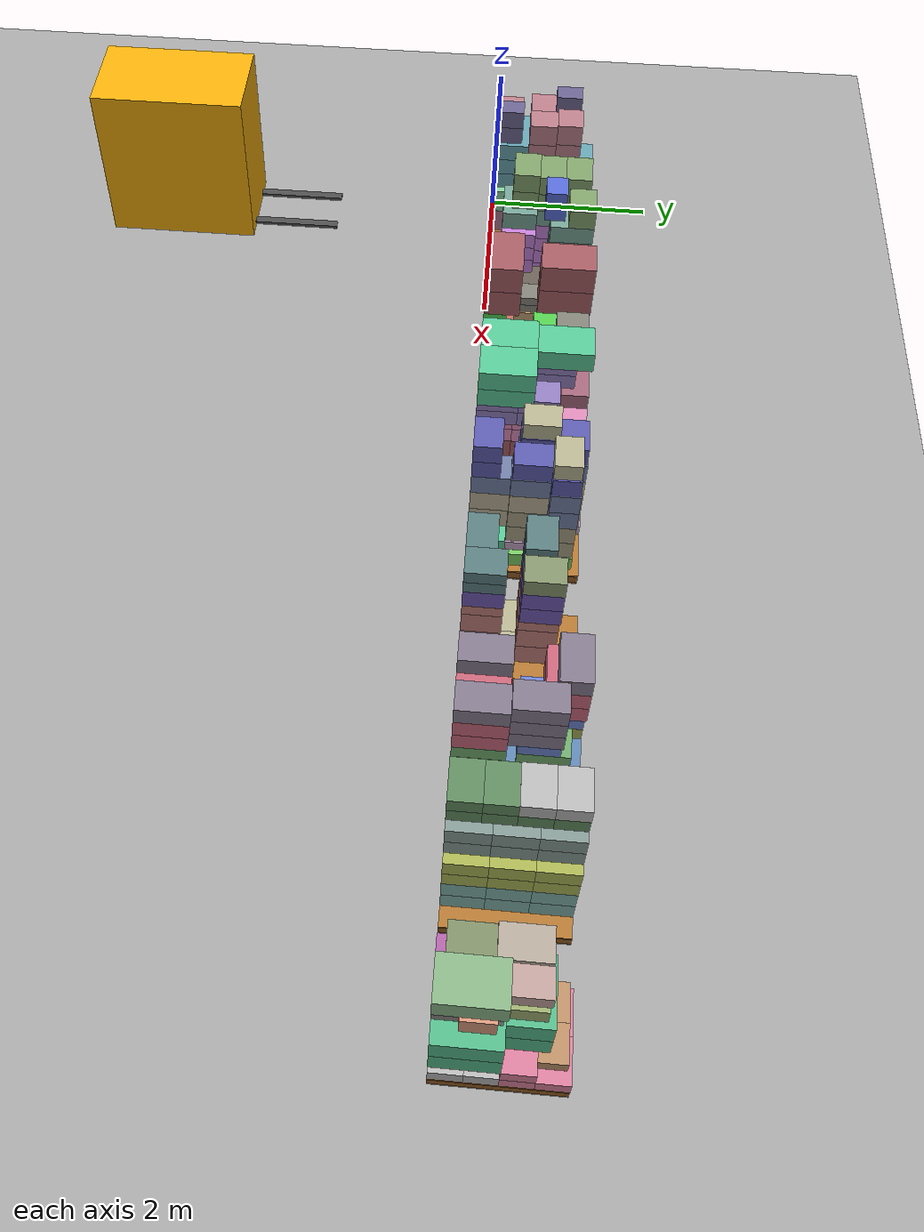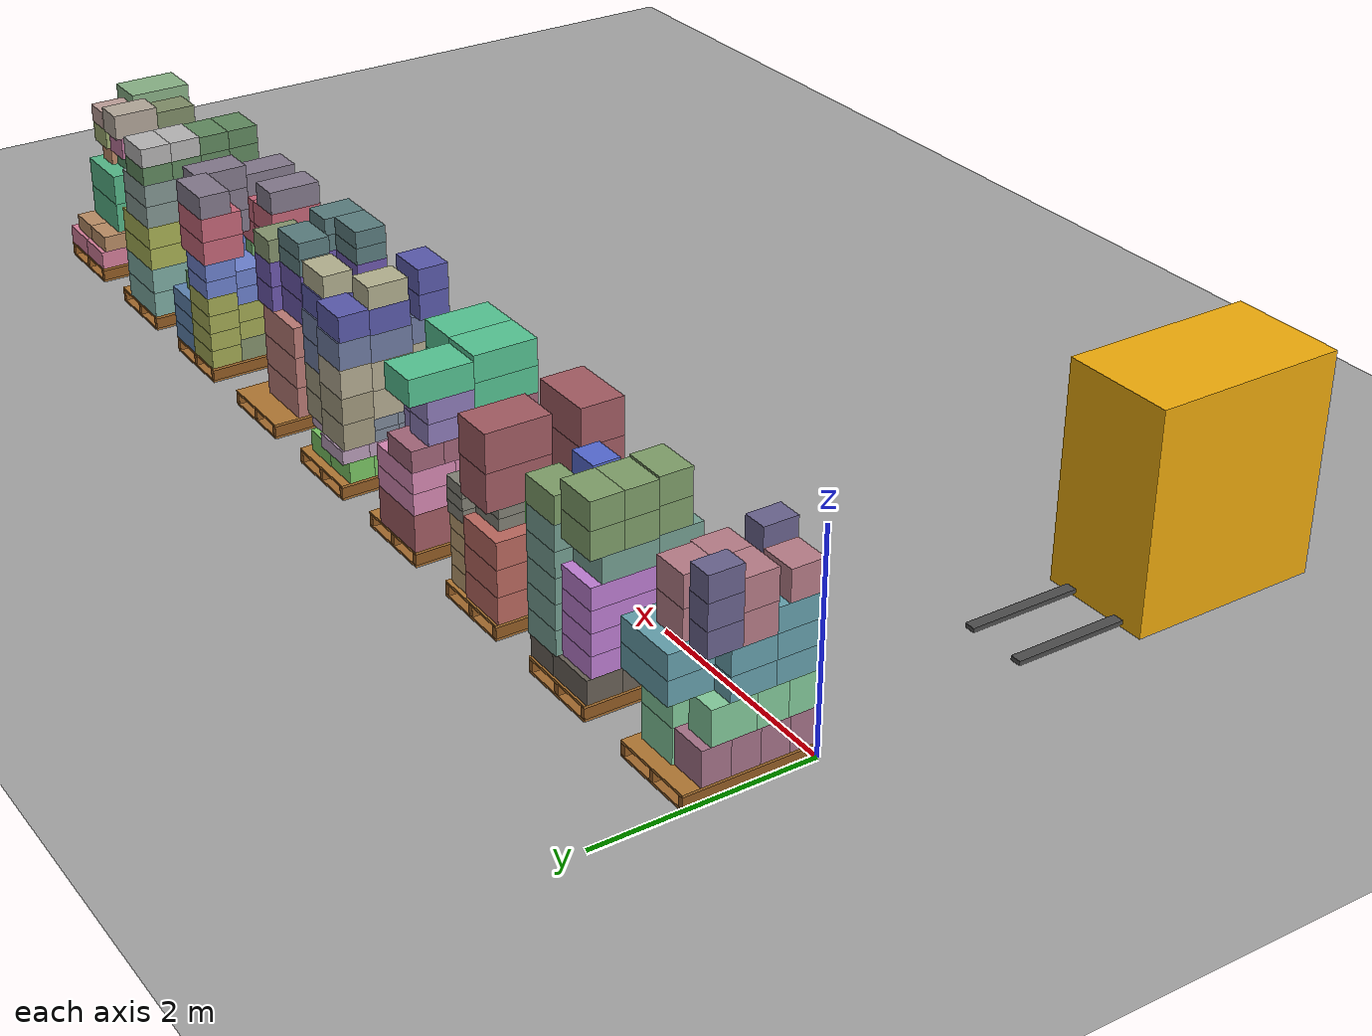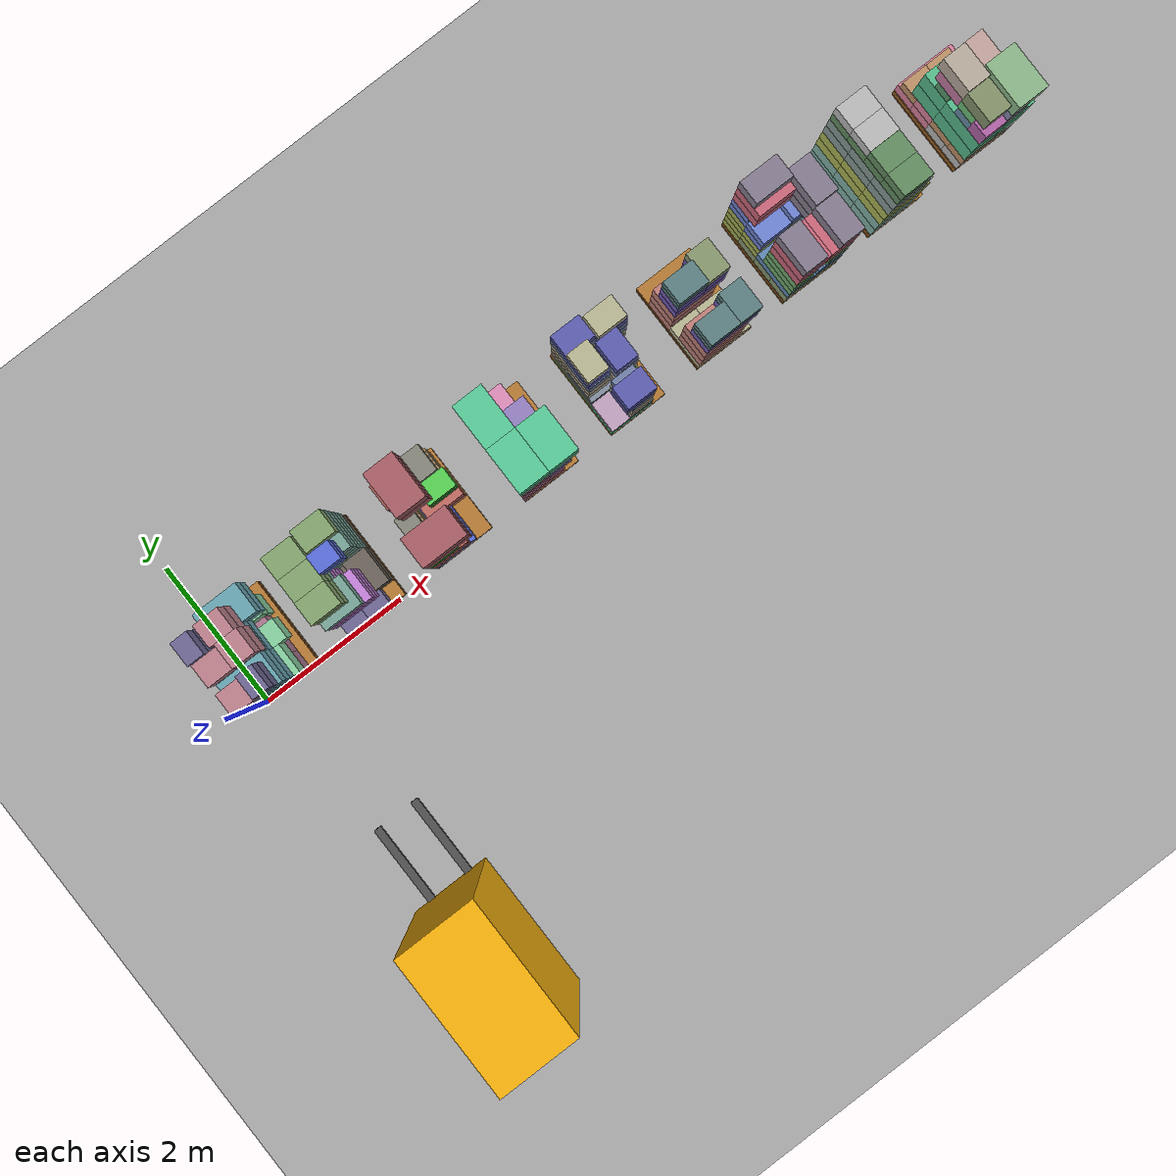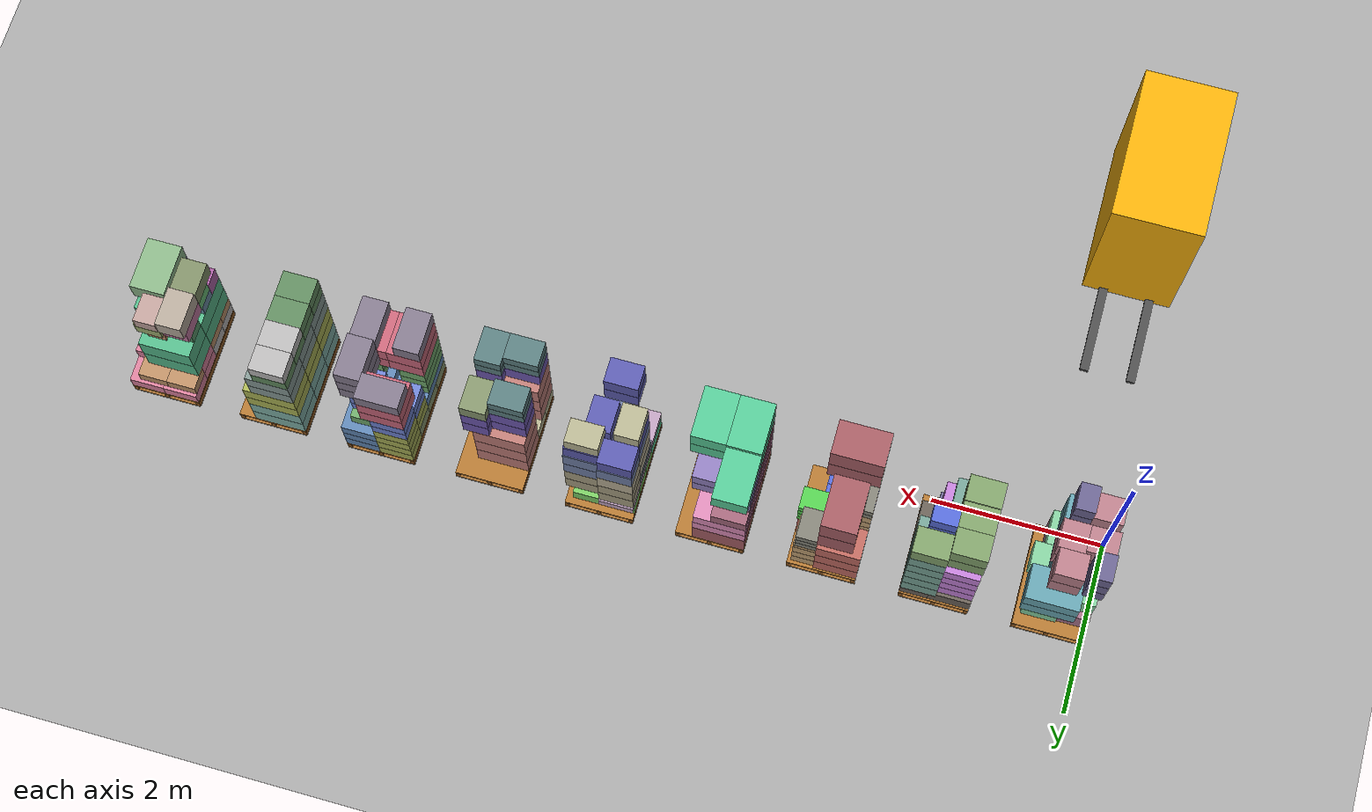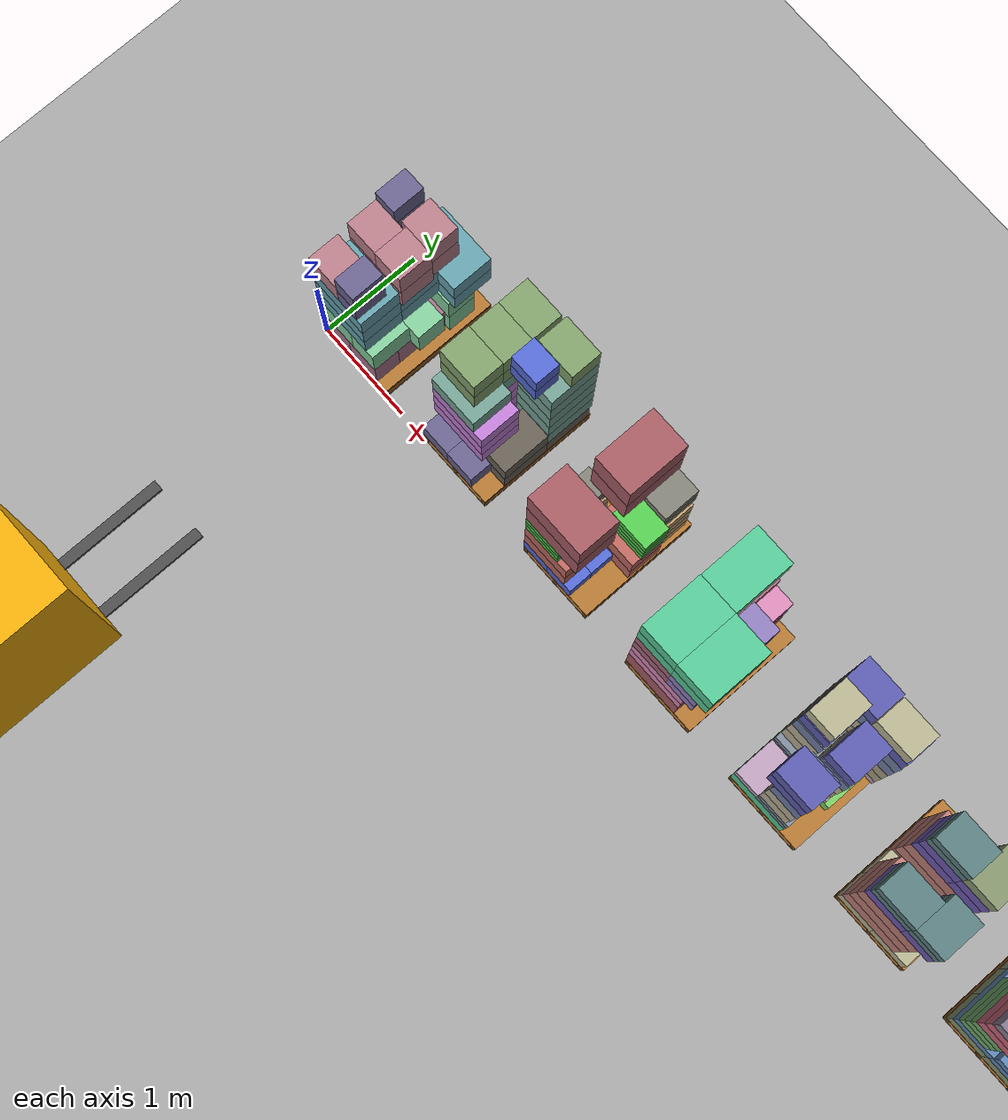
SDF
<?xml version="1.0" ?>
<sdf version="1.10">
  <world name="pallet_towers">
    <gravity>0 0 -9.81</gravity>

    <physics name="pallet_physics" type="ignored">
      <max_step_size>0.002</max_step_size>
      <real_time_factor>1</real_time_factor>
      <real_time_update_rate>500</real_time_update_rate>
      <max_contacts>100</max_contacts>
    </physics>

    <plugin filename="gz-sim-physics-system" name="gz::sim::systems::Physics" />
    <plugin filename="gz-sim-user-commands-system" name="gz::sim::systems::UserCommands" />
    <plugin filename="gz-sim-scene-broadcaster-system" name="gz::sim::systems::SceneBroadcaster" />

    <gui fullscreen="0">
      <plugin filename="MinimalScene" name="3D View">
        <gz-gui>
          <title>3D View</title>
          <property type="bool" key="showTitleBar">false</property>
          <property type="string" key="state">docked</property>
        </gz-gui>
        <engine>ogre2</engine>
        <scene>scene</scene>
        <ambient_light>0.4 0.4 0.4</ambient_light>
        <background_color>0.8 0.8 0.8</background_color>
        <camera_pose>-6 -8 6 0 0.45 0.75</camera_pose>
      </plugin>
      <plugin filename="GzSceneManager" name="Scene Manager" />
      <plugin filename="InteractiveViewControl" name="Interactive view control" />
      <plugin filename="CameraTracking" name="Camera Tracking" />
      <plugin filename="MarkerManager" name="Marker manager" />
      <plugin filename="SelectEntities" name="Select entities" />
      <plugin filename="EntityContextMenuPlugin" name="Entity context menu" />
      <plugin filename="VisualizationCapabilities" name="Visualization capabilities" />
      <plugin filename="WorldControl" name="World control">
        <gz-gui>
          <title>World control</title>
          <property type="bool" key="showTitleBar">false</property>
          <property type="bool" key="resizable">false</property>
          <property type="double" key="height">72</property>
          <property type="double" key="width">121</property>
          <property type="string" key="state">floating</property>
          <anchors target="3D View">
            <line own="left" target="left" />
            <line own="bottom" target="bottom" />
          </anchors>
        </gz-gui>
        <play_pause>true</play_pause>
        <step>true</step>
        <start_paused>true</start_paused>
      </plugin>
      <plugin filename="WorldStats" name="World stats">
        <gz-gui>
          <title>World stats</title>
          <property type="bool" key="showTitleBar">false</property>
          <property type="bool" key="resizable">false</property>
          <property type="double" key="height">110</property>
          <property type="double" key="width">290</property>
          <property type="string" key="state">floating</property>
          <anchors target="3D View">
            <line own="right" target="right" />
            <line own="bottom" target="bottom" />
          </anchors>
        </gz-gui>
        <sim_time>true</sim_time>
        <real_time>true</real_time>
        <real_time_factor>true</real_time_factor>
        <iterations>true</iterations>
      </plugin>
      <plugin filename="ForkliftTeleop"
              name="Forklift teleoperation">
        <gz-gui>
          <title>Forklift controls</title>
          <property type="double" key="width">330</property>
          <property type="double" key="height">230</property>
          <property type="string" key="state">floating</property>
          <anchors target="3D View">
            <line own="right" target="right" />
            <line own="top" target="top" />
          </anchors>
        </gz-gui>
        <drive_topic>/forklift/cmd_vel</drive_topic>
        <left_fork_topic>/forklift/left_fork/cmd_vel</left_fork_topic>
        <right_fork_topic>/forklift/right_fork/cmd_vel</right_fork_topic>
        <world_stats_topic>/world/pallet_towers/stats</world_stats_topic>
        <max_linear_speed>2</max_linear_speed>
        <max_linear_acceleration>0.5</max_linear_acceleration>
        <max_angular_speed>0.8</max_angular_speed>
        <max_angular_acceleration>1</max_angular_acceleration>
        <fork_speed>0.15</fork_speed>
        <update_rate_hz>50</update_rate_hz>
        <forward_key>16777235</forward_key>
        <reverse_key>16777237</reverse_key>
        <left_key>16777234</left_key>
        <right_key>16777236</right_key>
        <lift_key>16777235</lift_key>
        <lower_key>16777237</lower_key>
      </plugin>
    </gui>

    <light type="directional" name="sun">
      <cast_shadows>true</cast_shadows>
      <pose>0 0 10 0 0 0</pose>
      <diffuse>0.8 0.8 0.8 1</diffuse>
      <specular>0.2 0.2 0.2 1</specular>
      <direction>-0.5 0.2 -0.9</direction>
    </light>

    <model name="ground_plane">
      <static>true</static>
      <link name="link">
        <collision name="collision">
          <geometry>
            <plane>
              <normal>0 0 1</normal>
              <size>30 30</size>
            </plane>
          </geometry>

          <surface>
            <friction>
              <ode>
                <mu>0.55</mu>
                <mu2>0.55</mu2>
              </ode>
            </friction>
            <bounce>
              <restitution_coefficient>0</restitution_coefficient>
              <threshold>100000</threshold>
            </bounce>
            <contact>
              <ode>
                <kp>1000000</kp>
                <kd>100</kd>
                <max_vel>1</max_vel>
                <min_depth>0.0005</min_depth>
              </ode>
            </contact>
          </surface>
        </collision>

        <visual name="visual">
          <geometry>
            <plane>
              <normal>0 0 1</normal>
              <size>30 30</size>
            </plane>
          </geometry>
          <material>
            <ambient>0.65 0.65 0.65 1</ambient>
            <diffuse>0.65 0.65 0.65 1</diffuse>
          </material>
        </visual>
      </link>
    </model>

    <model name="pallet_01_P01">
          <static>false</static>
          <pose>0.4 0.6 0.002 0 0 0</pose>
          <self_collide>false</self_collide>
          <allow_auto_disable>false</allow_auto_disable>
          <link name="body">
                <gravity>true</gravity>
                <kinematic>false</kinematic>
                <inertial>
                      <pose>0 0 0.072 0 0 0</pose>
                      <mass>25</mass>
                      <inertia>
                            <ixx>3.07216082</ixx>
                            <ixy>0</ixy>
                            <ixz>0</ixz>
                            <iyy>1.70896776</iyy>
                            <iyz>0</iyz>
                            <izz>4.63680694</izz>
                      </inertia>
                </inertial>
                <collision name="bottom_deck_collision">
                      <pose>0 0 0.011 0 0 0</pose>
                      <geometry>
                            <box>
                                  <size>0.8 1.2 0.022</size>
                            </box>
                      </geometry>
                      <surface>
                            <friction>
                                  <ode>
                                        <mu>0.55</mu>
                                        <mu2>0.55</mu2>
                                  </ode>
                            </friction>
                            <bounce>
                                  <restitution_coefficient>0</restitution_coefficient>
                                  <threshold>100000</threshold>
                            </bounce>
                            <contact>
                                  <ode>
                                        <kp>1000000</kp>
                                        <kd>100</kd>
                                        <max_vel>1</max_vel>
                                        <min_depth>0.0005</min_depth>
                                  </ode>
                            </contact>
                      </surface>
                </collision>
                <visual name="bottom_deck_visual">
                      <pose>0 0 0.011 0 0 0</pose>
                      <geometry>
                            <box>
                                  <size>0.8 1.2 0.022</size>
                            </box>
                      </geometry>
                      <material>
                            <ambient>0.46 0.28 0.10 1</ambient>
                            <diffuse>0.64 0.42 0.18 1</diffuse>
                            <specular>0.03 0.03 0.03 1</specular>
                      </material>
                </visual>
                <collision name="left_stringer_collision">
                      <pose>-0.375 0 0.072 0 0 0</pose>
                      <geometry>
                            <box>
                                  <size>0.05 1.2 0.1</size>
                            </box>
                      </geometry>
                      <surface>
                            <friction>
                                  <ode>
                                        <mu>0.55</mu>
                                        <mu2>0.55</mu2>
                                  </ode>
                            </friction>
                            <bounce>
                                  <restitution_coefficient>0</restitution_coefficient>
                                  <threshold>100000</threshold>
                            </bounce>
                            <contact>
                                  <ode>
                                        <kp>1000000</kp>
                                        <kd>100</kd>
                                        <max_vel>1</max_vel>
                                        <min_depth>0.0005</min_depth>
                                  </ode>
                            </contact>
                      </surface>
                </collision>
                <visual name="left_stringer_visual">
                      <pose>-0.375 0 0.072 0 0 0</pose>
                      <geometry>
                            <box>
                                  <size>0.05 1.2 0.1</size>
                            </box>
                      </geometry>
                      <material>
                            <ambient>0.42 0.25 0.09 1</ambient>
                            <diffuse>0.58 0.36 0.14 1</diffuse>
                            <specular>0.03 0.03 0.03 1</specular>
                      </material>
                </visual>
                <collision name="centre_stringer_collision">
                      <pose>0 0 0.072 0 0 0</pose>
                      <geometry>
                            <box>
                                  <size>0.05 1.2 0.1</size>
                            </box>
                      </geometry>
                      <surface>
                            <friction>
                                  <ode>
                                        <mu>0.55</mu>
                                        <mu2>0.55</mu2>
                                  </ode>
                            </friction>
                            <bounce>
                                  <restitution_coefficient>0</restitution_coefficient>
                                  <threshold>100000</threshold>
                            </bounce>
                            <contact>
                                  <ode>
                                        <kp>1000000</kp>
                                        <kd>100</kd>
                                        <max_vel>1</max_vel>
                                        <min_depth>0.0005</min_depth>
                                  </ode>
                            </contact>
                      </surface>
                </collision>
                <visual name="centre_stringer_visual">
                      <pose>0 0 0.072 0 0 0</pose>
                      <geometry>
                            <box>
                                  <size>0.05 1.2 0.1</size>
                            </box>
                      </geometry>
                      <material>
                            <ambient>0.42 0.25 0.09 1</ambient>
                            <diffuse>0.58 0.36 0.14 1</diffuse>
                            <specular>0.03 0.03 0.03 1</specular>
                      </material>
                </visual>
                <collision name="right_stringer_collision">
                      <pose>0.375 0 0.072 0 0 0</pose>
                      <geometry>
                            <box>
                                  <size>0.05 1.2 0.1</size>
                            </box>
                      </geometry>
                      <surface>
                            <friction>
                                  <ode>
                                        <mu>0.55</mu>
                                        <mu2>0.55</mu2>
                                  </ode>
                            </friction>
                            <bounce>
                                  <restitution_coefficient>0</restitution_coefficient>
                                  <threshold>100000</threshold>
                            </bounce>
                            <contact>
                                  <ode>
                                        <kp>1000000</kp>
                                        <kd>100</kd>
                                        <max_vel>1</max_vel>
                                        <min_depth>0.0005</min_depth>
                                  </ode>
                            </contact>
                      </surface>
                </collision>
                <visual name="right_stringer_visual">
                      <pose>0.375 0 0.072 0 0 0</pose>
                      <geometry>
                            <box>
                                  <size>0.05 1.2 0.1</size>
                            </box>
                      </geometry>
                      <material>
                            <ambient>0.42 0.25 0.09 1</ambient>
                            <diffuse>0.58 0.36 0.14 1</diffuse>
                            <specular>0.03 0.03 0.03 1</specular>
                      </material>
                </visual>
                <collision name="top_deck_collision">
                      <pose>0 0 0.133 0 0 0</pose>
                      <geometry>
                            <box>
                                  <size>0.8 1.2 0.022</size>
                            </box>
                      </geometry>
                      <surface>
                            <friction>
                                  <ode>
                                        <mu>0.55</mu>
                                        <mu2>0.55</mu2>
                                  </ode>
                            </friction>
                            <bounce>
                                  <restitution_coefficient>0</restitution_coefficient>
                                  <threshold>100000</threshold>
                            </bounce>
                            <contact>
                                  <ode>
                                        <kp>1000000</kp>
                                        <kd>100</kd>
                                        <max_vel>1</max_vel>
                                        <min_depth>0.0005</min_depth>
                                  </ode>
                            </contact>
                      </surface>
                </collision>
                <visual name="top_deck_visual">
                      <pose>0 0 0.133 0 0 0</pose>
                      <geometry>
                            <box>
                                  <size>0.8 1.2 0.022</size>
                            </box>
                      </geometry>
                      <material>
                            <ambient>0.50 0.31 0.11 1</ambient>
                            <diffuse>0.70 0.47 0.20 1</diffuse>
                            <specular>0.03 0.03 0.03 1</specular>
                      </material>
                </visual>
          </link>
    </model>

    <model name="box_p01_0001_WINE_001_WINE">
      <static>false</static>
      <pose>0.17 0.13 0.306 0 0 0</pose>
      <link name="body">
        <gravity>true</gravity>
        <inertial>
          <mass>18</mass>
          <inertia>
            <ixx>0.255</ixx>
            <ixy>0</ixy>
            <ixz>0</ixz>
            <iyy>0.327</iyy>
            <iyz>0</iyz>
            <izz>0.2748</izz>
          </inertia>
        </inertial>

        <collision name="collision">
          <geometry>
            <box>
              <size>0.34 0.26 0.32</size>
            </box>
          </geometry>

          <surface>
            <friction>
              <ode>
                <mu>0.55</mu>
                <mu2>0.55</mu2>
              </ode>
            </friction>
            <bounce>
              <restitution_coefficient>0</restitution_coefficient>
              <threshold>100000</threshold>
            </bounce>
            <contact>
              <ode>
                <kp>1000000</kp>
                <kd>100</kd>
                <max_vel>1</max_vel>
                <min_depth>0.0005</min_depth>
              </ode>
            </contact>
          </surface>
        </collision>

        <visual name="visual">
          <geometry>
            <box>
              <size>0.34 0.26 0.32</size>
            </box>
          </geometry>
          <material>
            <ambient>0.654901961 0.450980392 0.541176471 1</ambient>
            <diffuse>0.654901961 0.450980392 0.541176471 1</diffuse>
            <specular>0.05 0.05 0.05 1</specular>
          </material>
        </visual>
      </link>
    </model>
    <model name="box_p01_0002_WINE_002_WINE">
      <static>false</static>
      <pose>0.51 0.13 0.306 0 0 0</pose>
      <link name="body">
        <gravity>true</gravity>
        <inertial>
          <mass>18</mass>
          <inertia>
            <ixx>0.255</ixx>
            <ixy>0</ixy>
            <ixz>0</ixz>
            <iyy>0.327</iyy>
            <iyz>0</iyz>
            <izz>0.2748</izz>
          </inertia>
        </inertial>

        <collision name="collision">
          <geometry>
            <box>
              <size>0.34 0.26 0.32</size>
            </box>
          </geometry>

          <surface>
            <friction>
              <ode>
                <mu>0.55</mu>
                <mu2>0.55</mu2>
              </ode>
            </friction>
            <bounce>
              <restitution_coefficient>0</restitution_coefficient>
              <threshold>100000</threshold>
            </bounce>
            <contact>
              <ode>
                <kp>1000000</kp>
                <kd>100</kd>
                <max_vel>1</max_vel>
                <min_depth>0.0005</min_depth>
              </ode>
            </contact>
          </surface>
        </collision>

        <visual name="visual">
          <geometry>
            <box>
              <size>0.34 0.26 0.32</size>
            </box>
          </geometry>
          <material>
            <ambient>0.654901961 0.450980392 0.541176471 1</ambient>
            <diffuse>0.654901961 0.450980392 0.541176471 1</diffuse>
            <specular>0.05 0.05 0.05 1</specular>
          </material>
        </visual>
      </link>
    </model>
    <model name="box_p01_0003_WINE_003_WINE">
      <static>false</static>
      <pose>0.17 0.39 0.306 0 0 0</pose>
      <link name="body">
        <gravity>true</gravity>
        <inertial>
          <mass>18</mass>
          <inertia>
            <ixx>0.255</ixx>
            <ixy>0</ixy>
            <ixz>0</ixz>
            <iyy>0.327</iyy>
            <iyz>0</iyz>
            <izz>0.2748</izz>
          </inertia>
        </inertial>

        <collision name="collision">
          <geometry>
            <box>
              <size>0.34 0.26 0.32</size>
            </box>
          </geometry>

          <surface>
            <friction>
              <ode>
                <mu>0.55</mu>
                <mu2>0.55</mu2>
              </ode>
            </friction>
            <bounce>
              <restitution_coefficient>0</restitution_coefficient>
              <threshold>100000</threshold>
            </bounce>
            <contact>
              <ode>
                <kp>1000000</kp>
                <kd>100</kd>
                <max_vel>1</max_vel>
                <min_depth>0.0005</min_depth>
              </ode>
            </contact>
          </surface>
        </collision>

        <visual name="visual">
          <geometry>
            <box>
              <size>0.34 0.26 0.32</size>
            </box>
          </geometry>
          <material>
            <ambient>0.654901961 0.450980392 0.541176471 1</ambient>
            <diffuse>0.654901961 0.450980392 0.541176471 1</diffuse>
            <specular>0.05 0.05 0.05 1</specular>
          </material>
        </visual>
      </link>
    </model>
    <model name="box_p01_0004_WINE_004_WINE">
      <static>false</static>
      <pose>0.51 0.39 0.306 0 0 0</pose>
      <link name="body">
        <gravity>true</gravity>
        <inertial>
          <mass>18</mass>
          <inertia>
            <ixx>0.255</ixx>
            <ixy>0</ixy>
            <ixz>0</ixz>
            <iyy>0.327</iyy>
            <iyz>0</iyz>
            <izz>0.2748</izz>
          </inertia>
        </inertial>

        <collision name="collision">
          <geometry>
            <box>
              <size>0.34 0.26 0.32</size>
            </box>
          </geometry>

          <surface>
            <friction>
              <ode>
                <mu>0.55</mu>
                <mu2>0.55</mu2>
              </ode>
            </friction>
            <bounce>
              <restitution_coefficient>0</restitution_coefficient>
              <threshold>100000</threshold>
            </bounce>
            <contact>
              <ode>
                <kp>1000000</kp>
                <kd>100</kd>
                <max_vel>1</max_vel>
                <min_depth>0.0005</min_depth>
              </ode>
            </contact>
          </surface>
        </collision>

        <visual name="visual">
          <geometry>
            <box>
              <size>0.34 0.26 0.32</size>
            </box>
          </geometry>
          <material>
            <ambient>0.654901961 0.450980392 0.541176471 1</ambient>
            <diffuse>0.654901961 0.450980392 0.541176471 1</diffuse>
            <specular>0.05 0.05 0.05 1</specular>
          </material>
        </visual>
      </link>
    </model>
    <model name="box_p01_0005_WINE_005_WINE">
      <static>false</static>
      <pose>0.17 0.65 0.306 0 0 0</pose>
      <link name="body">
        <gravity>true</gravity>
        <inertial>
          <mass>18</mass>
          <inertia>
            <ixx>0.255</ixx>
            <ixy>0</ixy>
            <ixz>0</ixz>
            <iyy>0.327</iyy>
            <iyz>0</iyz>
            <izz>0.2748</izz>
          </inertia>
        </inertial>

        <collision name="collision">
          <geometry>
            <box>
              <size>0.34 0.26 0.32</size>
            </box>
          </geometry>

          <surface>
            <friction>
              <ode>
                <mu>0.55</mu>
                <mu2>0.55</mu2>
              </ode>
            </friction>
            <bounce>
              <restitution_coefficient>0</restitution_coefficient>
              <threshold>100000</threshold>
            </bounce>
            <contact>
              <ode>
                <kp>1000000</kp>
                <kd>100</kd>
                <max_vel>1</max_vel>
                <min_depth>0.0005</min_depth>
              </ode>
            </contact>
          </surface>
        </collision>

        <visual name="visual">
          <geometry>
            <box>
              <size>0.34 0.26 0.32</size>
            </box>
          </geometry>
          <material>
            <ambient>0.654901961 0.450980392 0.541176471 1</ambient>
            <diffuse>0.654901961 0.450980392 0.541176471 1</diffuse>
            <specular>0.05 0.05 0.05 1</specular>
          </material>
        </visual>
      </link>
    </model>
    <model name="box_p01_0006_WINE_006_WINE">
      <static>false</static>
      <pose>0.51 0.65 0.306 0 0 0</pose>
      <link name="body">
        <gravity>true</gravity>
        <inertial>
          <mass>18</mass>
          <inertia>
            <ixx>0.255</ixx>
            <ixy>0</ixy>
            <ixz>0</ixz>
            <iyy>0.327</iyy>
            <iyz>0</iyz>
            <izz>0.2748</izz>
          </inertia>
        </inertial>

        <collision name="collision">
          <geometry>
            <box>
              <size>0.34 0.26 0.32</size>
            </box>
          </geometry>

          <surface>
            <friction>
              <ode>
                <mu>0.55</mu>
                <mu2>0.55</mu2>
              </ode>
            </friction>
            <bounce>
              <restitution_coefficient>0</restitution_coefficient>
              <threshold>100000</threshold>
            </bounce>
            <contact>
              <ode>
                <kp>1000000</kp>
                <kd>100</kd>
                <max_vel>1</max_vel>
                <min_depth>0.0005</min_depth>
              </ode>
            </contact>
          </surface>
        </collision>

        <visual name="visual">
          <geometry>
            <box>
              <size>0.34 0.26 0.32</size>
            </box>
          </geometry>
          <material>
            <ambient>0.654901961 0.450980392 0.541176471 1</ambient>
            <diffuse>0.654901961 0.450980392 0.541176471 1</diffuse>
            <specular>0.05 0.05 0.05 1</specular>
          </material>
        </visual>
      </link>
    </model>
    <model name="box_p01_0007_WINE_007_WINE">
      <static>false</static>
      <pose>0.17 0.91 0.306 0 0 0</pose>
      <link name="body">
        <gravity>true</gravity>
        <inertial>
          <mass>18</mass>
          <inertia>
            <ixx>0.255</ixx>
            <ixy>0</ixy>
            <ixz>0</ixz>
            <iyy>0.327</iyy>
            <iyz>0</iyz>
            <izz>0.2748</izz>
          </inertia>
        </inertial>

        <collision name="collision">
          <geometry>
            <box>
              <size>0.34 0.26 0.32</size>
            </box>
          </geometry>

          <surface>
            <friction>
              <ode>
                <mu>0.55</mu>
                <mu2>0.55</mu2>
              </ode>
            </friction>
            <bounce>
              <restitution_coefficient>0</restitution_coefficient>
              <threshold>100000</threshold>
            </bounce>
            <contact>
              <ode>
                <kp>1000000</kp>
                <kd>100</kd>
                <max_vel>1</max_vel>
                <min_depth>0.0005</min_depth>
              </ode>
            </contact>
          </surface>
        </collision>

        <visual name="visual">
          <geometry>
            <box>
              <size>0.34 0.26 0.32</size>
            </box>
          </geometry>
          <material>
            <ambient>0.654901961 0.450980392 0.541176471 1</ambient>
            <diffuse>0.654901961 0.450980392 0.541176471 1</diffuse>
            <specular>0.05 0.05 0.05 1</specular>
          </material>
        </visual>
      </link>
    </model>
    <model name="box_p01_0008_DETERG_001_DETERG">
      <static>false</static>
      <pose>0.54 0.92 0.306 0 0 0</pose>
      <link name="body">
        <gravity>true</gravity>
        <inertial>
          <mass>7</mass>
          <inertia>
            <ixx>0.105466667</ixx>
            <ixy>0</ixy>
            <ixz>0</ixz>
            <iyy>0.153066667</iyy>
            <iyz>0</iyz>
            <izz>0.139066667</izz>
          </inertia>
        </inertial>

        <collision name="collision">
          <geometry>
            <box>
              <size>0.4 0.28 0.32</size>
            </box>
          </geometry>

          <surface>
            <friction>
              <ode>
                <mu>0.55</mu>
                <mu2>0.55</mu2>
              </ode>
            </friction>
            <bounce>
              <restitution_coefficient>0</restitution_coefficient>
              <threshold>100000</threshold>
            </bounce>
            <contact>
              <ode>
                <kp>1000000</kp>
                <kd>100</kd>
                <max_vel>1</max_vel>
                <min_depth>0.0005</min_depth>
              </ode>
            </contact>
          </surface>
        </collision>

        <visual name="visual">
          <geometry>
            <box>
              <size>0.4 0.28 0.32</size>
            </box>
          </geometry>
          <material>
            <ambient>0.517647059 0.803921569 0.615686275 1</ambient>
            <diffuse>0.517647059 0.803921569 0.615686275 1</diffuse>
            <specular>0.05 0.05 0.05 1</specular>
          </material>
        </visual>
      </link>
    </model>
    <model name="box_p01_0009_DETERG_002_DETERG">
      <static>false</static>
      <pose>0.54 0.92 0.626 0 0 0</pose>
      <link name="body">
        <gravity>true</gravity>
        <inertial>
          <mass>7</mass>
          <inertia>
            <ixx>0.105466667</ixx>
            <ixy>0</ixy>
            <ixz>0</ixz>
            <iyy>0.153066667</iyy>
            <iyz>0</iyz>
            <izz>0.139066667</izz>
          </inertia>
        </inertial>

        <collision name="collision">
          <geometry>
            <box>
              <size>0.4 0.28 0.32</size>
            </box>
          </geometry>

          <surface>
            <friction>
              <ode>
                <mu>0.55</mu>
                <mu2>0.55</mu2>
              </ode>
            </friction>
            <bounce>
              <restitution_coefficient>0</restitution_coefficient>
              <threshold>100000</threshold>
            </bounce>
            <contact>
              <ode>
                <kp>1000000</kp>
                <kd>100</kd>
                <max_vel>1</max_vel>
                <min_depth>0.0005</min_depth>
              </ode>
            </contact>
          </surface>
        </collision>

        <visual name="visual">
          <geometry>
            <box>
              <size>0.4 0.28 0.32</size>
            </box>
          </geometry>
          <material>
            <ambient>0.517647059 0.803921569 0.615686275 1</ambient>
            <diffuse>0.517647059 0.803921569 0.615686275 1</diffuse>
            <specular>0.05 0.05 0.05 1</specular>
          </material>
        </visual>
      </link>
    </model>
    <model name="box_p01_0010_DETERG_003_DETERG">
      <static>false</static>
      <pose>0.2 0.14 0.626 0 0 0</pose>
      <link name="body">
        <gravity>true</gravity>
        <inertial>
          <mass>7</mass>
          <inertia>
            <ixx>0.105466667</ixx>
            <ixy>0</ixy>
            <ixz>0</ixz>
            <iyy>0.153066667</iyy>
            <iyz>0</iyz>
            <izz>0.139066667</izz>
          </inertia>
        </inertial>

        <collision name="collision">
          <geometry>
            <box>
              <size>0.4 0.28 0.32</size>
            </box>
          </geometry>

          <surface>
            <friction>
              <ode>
                <mu>0.55</mu>
                <mu2>0.55</mu2>
              </ode>
            </friction>
            <bounce>
              <restitution_coefficient>0</restitution_coefficient>
              <threshold>100000</threshold>
            </bounce>
            <contact>
              <ode>
                <kp>1000000</kp>
                <kd>100</kd>
                <max_vel>1</max_vel>
                <min_depth>0.0005</min_depth>
              </ode>
            </contact>
          </surface>
        </collision>

        <visual name="visual">
          <geometry>
            <box>
              <size>0.4 0.28 0.32</size>
            </box>
          </geometry>
          <material>
            <ambient>0.517647059 0.803921569 0.615686275 1</ambient>
            <diffuse>0.517647059 0.803921569 0.615686275 1</diffuse>
            <specular>0.05 0.05 0.05 1</specular>
          </material>
        </visual>
      </link>
    </model>
    <model name="box_p01_0011_DETERG_004_DETERG">
      <static>false</static>
      <pose>0.54 0.2 0.626 0 0 0</pose>
      <link name="body">
        <gravity>true</gravity>
        <inertial>
          <mass>7</mass>
          <inertia>
            <ixx>0.153066667</ixx>
            <ixy>0</ixy>
            <ixz>0</ixz>
            <iyy>0.105466667</iyy>
            <iyz>0</iyz>
            <izz>0.139066667</izz>
          </inertia>
        </inertial>

        <collision name="collision">
          <geometry>
            <box>
              <size>0.28 0.4 0.32</size>
            </box>
          </geometry>

          <surface>
            <friction>
              <ode>
                <mu>0.55</mu>
                <mu2>0.55</mu2>
              </ode>
            </friction>
            <bounce>
              <restitution_coefficient>0</restitution_coefficient>
              <threshold>100000</threshold>
            </bounce>
            <contact>
              <ode>
                <kp>1000000</kp>
                <kd>100</kd>
                <max_vel>1</max_vel>
                <min_depth>0.0005</min_depth>
              </ode>
            </contact>
          </surface>
        </collision>

        <visual name="visual">
          <geometry>
            <box>
              <size>0.28 0.4 0.32</size>
            </box>
          </geometry>
          <material>
            <ambient>0.517647059 0.803921569 0.615686275 1</ambient>
            <diffuse>0.517647059 0.803921569 0.615686275 1</diffuse>
            <specular>0.05 0.05 0.05 1</specular>
          </material>
        </visual>
      </link>
    </model>
    <model name="box_p01_0012_DETERG_005_DETERG">
      <static>false</static>
      <pose>0.2 0.42 0.626 0 0 0</pose>
      <link name="body">
        <gravity>true</gravity>
        <inertial>
          <mass>7</mass>
          <inertia>
            <ixx>0.105466667</ixx>
            <ixy>0</ixy>
            <ixz>0</ixz>
            <iyy>0.153066667</iyy>
            <iyz>0</iyz>
            <izz>0.139066667</izz>
          </inertia>
        </inertial>

        <collision name="collision">
          <geometry>
            <box>
              <size>0.4 0.28 0.32</size>
            </box>
          </geometry>

          <surface>
            <friction>
              <ode>
                <mu>0.55</mu>
                <mu2>0.55</mu2>
              </ode>
            </friction>
            <bounce>
              <restitution_coefficient>0</restitution_coefficient>
              <threshold>100000</threshold>
            </bounce>
            <contact>
              <ode>
                <kp>1000000</kp>
                <kd>100</kd>
                <max_vel>1</max_vel>
                <min_depth>0.0005</min_depth>
              </ode>
            </contact>
          </surface>
        </collision>

        <visual name="visual">
          <geometry>
            <box>
              <size>0.4 0.28 0.32</size>
            </box>
          </geometry>
          <material>
            <ambient>0.517647059 0.803921569 0.615686275 1</ambient>
            <diffuse>0.517647059 0.803921569 0.615686275 1</diffuse>
            <specular>0.05 0.05 0.05 1</specular>
          </material>
        </visual>
      </link>
    </model>
    <model name="box_p01_0013_DETERG_006_DETERG">
      <static>false</static>
      <pose>0.14 0.76 0.626 0 0 0</pose>
      <link name="body">
        <gravity>true</gravity>
        <inertial>
          <mass>7</mass>
          <inertia>
            <ixx>0.153066667</ixx>
            <ixy>0</ixy>
            <ixz>0</ixz>
            <iyy>0.105466667</iyy>
            <iyz>0</iyz>
            <izz>0.139066667</izz>
          </inertia>
        </inertial>

        <collision name="collision">
          <geometry>
            <box>
              <size>0.28 0.4 0.32</size>
            </box>
          </geometry>

          <surface>
            <friction>
              <ode>
                <mu>0.55</mu>
                <mu2>0.55</mu2>
              </ode>
            </friction>
            <bounce>
              <restitution_coefficient>0</restitution_coefficient>
              <threshold>100000</threshold>
            </bounce>
            <contact>
              <ode>
                <kp>1000000</kp>
                <kd>100</kd>
                <max_vel>1</max_vel>
                <min_depth>0.0005</min_depth>
              </ode>
            </contact>
          </surface>
        </collision>

        <visual name="visual">
          <geometry>
            <box>
              <size>0.28 0.4 0.32</size>
            </box>
          </geometry>
          <material>
            <ambient>0.517647059 0.803921569 0.615686275 1</ambient>
            <diffuse>0.517647059 0.803921569 0.615686275 1</diffuse>
            <specular>0.05 0.05 0.05 1</specular>
          </material>
        </visual>
      </link>
    </model>
    <model name="box_p01_0014_DETERG_007_DETERG">
      <static>false</static>
      <pose>0.6 0.54 0.626 0 0 0</pose>
      <link name="body">
        <gravity>true</gravity>
        <inertial>
          <mass>7</mass>
          <inertia>
            <ixx>0.105466667</ixx>
            <ixy>0</ixy>
            <ixz>0</ixz>
            <iyy>0.153066667</iyy>
            <iyz>0</iyz>
            <izz>0.139066667</izz>
          </inertia>
        </inertial>

        <collision name="collision">
          <geometry>
            <box>
              <size>0.4 0.28 0.32</size>
            </box>
          </geometry>

          <surface>
            <friction>
              <ode>
                <mu>0.55</mu>
                <mu2>0.55</mu2>
              </ode>
            </friction>
            <bounce>
              <restitution_coefficient>0</restitution_coefficient>
              <threshold>100000</threshold>
            </bounce>
            <contact>
              <ode>
                <kp>1000000</kp>
                <kd>100</kd>
                <max_vel>1</max_vel>
                <min_depth>0.0005</min_depth>
              </ode>
            </contact>
          </surface>
        </collision>

        <visual name="visual">
          <geometry>
            <box>
              <size>0.4 0.28 0.32</size>
            </box>
          </geometry>
          <material>
            <ambient>0.517647059 0.803921569 0.615686275 1</ambient>
            <diffuse>0.517647059 0.803921569 0.615686275 1</diffuse>
            <specular>0.05 0.05 0.05 1</specular>
          </material>
        </visual>
      </link>
    </model>
    <model name="box_p01_0015_APPLES_001_APPLES">
      <static>false</static>
      <pose>0.3 0.2 0.896 0 0 0</pose>
      <link name="body">
        <gravity>true</gravity>
        <inertial>
          <mass>12</mass>
          <inertia>
            <ixx>0.2084</ixx>
            <ixy>0</ixy>
            <ixz>0</ixz>
            <iyy>0.4084</iyy>
            <iyz>0</iyz>
            <izz>0.52</izz>
          </inertia>
        </inertial>

        <collision name="collision">
          <geometry>
            <box>
              <size>0.6 0.4 0.22</size>
            </box>
          </geometry>

          <surface>
            <friction>
              <ode>
                <mu>0.55</mu>
                <mu2>0.55</mu2>
              </ode>
            </friction>
            <bounce>
              <restitution_coefficient>0</restitution_coefficient>
              <threshold>100000</threshold>
            </bounce>
            <contact>
              <ode>
                <kp>1000000</kp>
                <kd>100</kd>
                <max_vel>1</max_vel>
                <min_depth>0.0005</min_depth>
              </ode>
            </contact>
          </surface>
        </collision>

        <visual name="visual">
          <geometry>
            <box>
              <size>0.6 0.4 0.22</size>
            </box>
          </geometry>
          <material>
            <ambient>0.4 0.635294118 0.68627451 1</ambient>
            <diffuse>0.4 0.635294118 0.68627451 1</diffuse>
            <specular>0.05 0.05 0.05 1</specular>
          </material>
        </visual>
      </link>
    </model>
    <model name="box_p01_0016_APPLES_002_APPLES">
      <static>false</static>
      <pose>0.3 0.6 0.896 0 0 0</pose>
      <link name="body">
        <gravity>true</gravity>
        <inertial>
          <mass>12</mass>
          <inertia>
            <ixx>0.2084</ixx>
            <ixy>0</ixy>
            <ixz>0</ixz>
            <iyy>0.4084</iyy>
            <iyz>0</iyz>
            <izz>0.52</izz>
          </inertia>
        </inertial>

        <collision name="collision">
          <geometry>
            <box>
              <size>0.6 0.4 0.22</size>
            </box>
          </geometry>

          <surface>
            <friction>
              <ode>
                <mu>0.55</mu>
                <mu2>0.55</mu2>
              </ode>
            </friction>
            <bounce>
              <restitution_coefficient>0</restitution_coefficient>
              <threshold>100000</threshold>
            </bounce>
            <contact>
              <ode>
                <kp>1000000</kp>
                <kd>100</kd>
                <max_vel>1</max_vel>
                <min_depth>0.0005</min_depth>
              </ode>
            </contact>
          </surface>
        </collision>

        <visual name="visual">
          <geometry>
            <box>
              <size>0.6 0.4 0.22</size>
            </box>
          </geometry>
          <material>
            <ambient>0.4 0.635294118 0.68627451 1</ambient>
            <diffuse>0.4 0.635294118 0.68627451 1</diffuse>
            <specular>0.05 0.05 0.05 1</specular>
          </material>
        </visual>
      </link>
    </model>
    <model name="box_p01_0017_APPLES_003_APPLES">
      <static>false</static>
      <pose>0.3 0.2 1.116 0 0 0</pose>
      <link name="body">
        <gravity>true</gravity>
        <inertial>
          <mass>12</mass>
          <inertia>
            <ixx>0.2084</ixx>
            <ixy>0</ixy>
            <ixz>0</ixz>
            <iyy>0.4084</iyy>
            <iyz>0</iyz>
            <izz>0.52</izz>
          </inertia>
        </inertial>

        <collision name="collision">
          <geometry>
            <box>
              <size>0.6 0.4 0.22</size>
            </box>
          </geometry>

          <surface>
            <friction>
              <ode>
                <mu>0.55</mu>
                <mu2>0.55</mu2>
              </ode>
            </friction>
            <bounce>
              <restitution_coefficient>0</restitution_coefficient>
              <threshold>100000</threshold>
            </bounce>
            <contact>
              <ode>
                <kp>1000000</kp>
                <kd>100</kd>
                <max_vel>1</max_vel>
                <min_depth>0.0005</min_depth>
              </ode>
            </contact>
          </surface>
        </collision>

        <visual name="visual">
          <geometry>
            <box>
              <size>0.6 0.4 0.22</size>
            </box>
          </geometry>
          <material>
            <ambient>0.4 0.635294118 0.68627451 1</ambient>
            <diffuse>0.4 0.635294118 0.68627451 1</diffuse>
            <specular>0.05 0.05 0.05 1</specular>
          </material>
        </visual>
      </link>
    </model>
    <model name="box_p01_0018_APPLES_004_APPLES">
      <static>false</static>
      <pose>0.3 0.6 1.116 0 0 0</pose>
      <link name="body">
        <gravity>true</gravity>
        <inertial>
          <mass>12</mass>
          <inertia>
            <ixx>0.2084</ixx>
            <ixy>0</ixy>
            <ixz>0</ixz>
            <iyy>0.4084</iyy>
            <iyz>0</iyz>
            <izz>0.52</izz>
          </inertia>
        </inertial>

        <collision name="collision">
          <geometry>
            <box>
              <size>0.6 0.4 0.22</size>
            </box>
          </geometry>

          <surface>
            <friction>
              <ode>
                <mu>0.55</mu>
                <mu2>0.55</mu2>
              </ode>
            </friction>
            <bounce>
              <restitution_coefficient>0</restitution_coefficient>
              <threshold>100000</threshold>
            </bounce>
            <contact>
              <ode>
                <kp>1000000</kp>
                <kd>100</kd>
                <max_vel>1</max_vel>
                <min_depth>0.0005</min_depth>
              </ode>
            </contact>
          </surface>
        </collision>

        <visual name="visual">
          <geometry>
            <box>
              <size>0.6 0.4 0.22</size>
            </box>
          </geometry>
          <material>
            <ambient>0.4 0.635294118 0.68627451 1</ambient>
            <diffuse>0.4 0.635294118 0.68627451 1</diffuse>
            <specular>0.05 0.05 0.05 1</specular>
          </material>
        </visual>
      </link>
    </model>
    <model name="box_p01_0019_APPLES_005_APPLES">
      <static>false</static>
      <pose>0.5 1 0.896 0 0 0</pose>
      <link name="body">
        <gravity>true</gravity>
        <inertial>
          <mass>12</mass>
          <inertia>
            <ixx>0.2084</ixx>
            <ixy>0</ixy>
            <ixz>0</ixz>
            <iyy>0.4084</iyy>
            <iyz>0</iyz>
            <izz>0.52</izz>
          </inertia>
        </inertial>

        <collision name="collision">
          <geometry>
            <box>
              <size>0.6 0.4 0.22</size>
            </box>
          </geometry>

          <surface>
            <friction>
              <ode>
                <mu>0.55</mu>
                <mu2>0.55</mu2>
              </ode>
            </friction>
            <bounce>
              <restitution_coefficient>0</restitution_coefficient>
              <threshold>100000</threshold>
            </bounce>
            <contact>
              <ode>
                <kp>1000000</kp>
                <kd>100</kd>
                <max_vel>1</max_vel>
                <min_depth>0.0005</min_depth>
              </ode>
            </contact>
          </surface>
        </collision>

        <visual name="visual">
          <geometry>
            <box>
              <size>0.6 0.4 0.22</size>
            </box>
          </geometry>
          <material>
            <ambient>0.4 0.635294118 0.68627451 1</ambient>
            <diffuse>0.4 0.635294118 0.68627451 1</diffuse>
            <specular>0.05 0.05 0.05 1</specular>
          </material>
        </visual>
      </link>
    </model>
    <model name="box_p01_0020_APPLES_006_APPLES">
      <static>false</static>
      <pose>0.5 1 1.116 0 0 0</pose>
      <link name="body">
        <gravity>true</gravity>
        <inertial>
          <mass>12</mass>
          <inertia>
            <ixx>0.2084</ixx>
            <ixy>0</ixy>
            <ixz>0</ixz>
            <iyy>0.4084</iyy>
            <iyz>0</iyz>
            <izz>0.52</izz>
          </inertia>
        </inertial>

        <collision name="collision">
          <geometry>
            <box>
              <size>0.6 0.4 0.22</size>
            </box>
          </geometry>

          <surface>
            <friction>
              <ode>
                <mu>0.55</mu>
                <mu2>0.55</mu2>
              </ode>
            </friction>
            <bounce>
              <restitution_coefficient>0</restitution_coefficient>
              <threshold>100000</threshold>
            </bounce>
            <contact>
              <ode>
                <kp>1000000</kp>
                <kd>100</kd>
                <max_vel>1</max_vel>
                <min_depth>0.0005</min_depth>
              </ode>
            </contact>
          </surface>
        </collision>

        <visual name="visual">
          <geometry>
            <box>
              <size>0.6 0.4 0.22</size>
            </box>
          </geometry>
          <material>
            <ambient>0.4 0.635294118 0.68627451 1</ambient>
            <diffuse>0.4 0.635294118 0.68627451 1</diffuse>
            <specular>0.05 0.05 0.05 1</specular>
          </material>
        </visual>
      </link>
    </model>
    <model name="box_p01_0021_APPLES_007_APPLES">
      <static>false</static>
      <pose>0.3 0.2 1.336 0 0 0</pose>
      <link name="body">
        <gravity>true</gravity>
        <inertial>
          <mass>12</mass>
          <inertia>
            <ixx>0.2084</ixx>
            <ixy>0</ixy>
            <ixz>0</ixz>
            <iyy>0.4084</iyy>
            <iyz>0</iyz>
            <izz>0.52</izz>
          </inertia>
        </inertial>

        <collision name="collision">
          <geometry>
            <box>
              <size>0.6 0.4 0.22</size>
            </box>
          </geometry>

          <surface>
            <friction>
              <ode>
                <mu>0.55</mu>
                <mu2>0.55</mu2>
              </ode>
            </friction>
            <bounce>
              <restitution_coefficient>0</restitution_coefficient>
              <threshold>100000</threshold>
            </bounce>
            <contact>
              <ode>
                <kp>1000000</kp>
                <kd>100</kd>
                <max_vel>1</max_vel>
                <min_depth>0.0005</min_depth>
              </ode>
            </contact>
          </surface>
        </collision>

        <visual name="visual">
          <geometry>
            <box>
              <size>0.6 0.4 0.22</size>
            </box>
          </geometry>
          <material>
            <ambient>0.4 0.635294118 0.68627451 1</ambient>
            <diffuse>0.4 0.635294118 0.68627451 1</diffuse>
            <specular>0.05 0.05 0.05 1</specular>
          </material>
        </visual>
      </link>
    </model>
    <model name="box_p01_0022_EGGS_001_EGGS">
      <static>false</static>
      <pose>0.165 0.55 1.366 0 0 0</pose>
      <link name="body">
        <gravity>true</gravity>
        <inertial>
          <mass>18</mass>
          <inertia>
            <ixx>0.2526</ixx>
            <ixy>0</ixy>
            <ixz>0</ixz>
            <iyy>0.28095</iyy>
            <iyz>0</iyz>
            <izz>0.29835</izz>
          </inertia>
        </inertial>

        <collision name="collision">
          <geometry>
            <box>
              <size>0.33 0.3 0.28</size>
            </box>
          </geometry>

          <surface>
            <friction>
              <ode>
                <mu>0.55</mu>
                <mu2>0.55</mu2>
              </ode>
            </friction>
            <bounce>
              <restitution_coefficient>0</restitution_coefficient>
              <threshold>100000</threshold>
            </bounce>
            <contact>
              <ode>
                <kp>1000000</kp>
                <kd>100</kd>
                <max_vel>1</max_vel>
                <min_depth>0.0005</min_depth>
              </ode>
            </contact>
          </surface>
        </collision>

        <visual name="visual">
          <geometry>
            <box>
              <size>0.33 0.3 0.28</size>
            </box>
          </geometry>
          <material>
            <ambient>0.725490196 0.494117647 0.537254902 1</ambient>
            <diffuse>0.725490196 0.494117647 0.537254902 1</diffuse>
            <specular>0.05 0.05 0.05 1</specular>
          </material>
        </visual>
      </link>
    </model>
    <model name="box_p01_0023_EGGS_002_EGGS">
      <static>false</static>
      <pose>0.48 0.565 1.366 0 0 0</pose>
      <link name="body">
        <gravity>true</gravity>
        <inertial>
          <mass>18</mass>
          <inertia>
            <ixx>0.28095</ixx>
            <ixy>0</ixy>
            <ixz>0</ixz>
            <iyy>0.2526</iyy>
            <iyz>0</iyz>
            <izz>0.29835</izz>
          </inertia>
        </inertial>

        <collision name="collision">
          <geometry>
            <box>
              <size>0.3 0.33 0.28</size>
            </box>
          </geometry>

          <surface>
            <friction>
              <ode>
                <mu>0.55</mu>
                <mu2>0.55</mu2>
              </ode>
            </friction>
            <bounce>
              <restitution_coefficient>0</restitution_coefficient>
              <threshold>100000</threshold>
            </bounce>
            <contact>
              <ode>
                <kp>1000000</kp>
                <kd>100</kd>
                <max_vel>1</max_vel>
                <min_depth>0.0005</min_depth>
              </ode>
            </contact>
          </surface>
        </collision>

        <visual name="visual">
          <geometry>
            <box>
              <size>0.3 0.33 0.28</size>
            </box>
          </geometry>
          <material>
            <ambient>0.725490196 0.494117647 0.537254902 1</ambient>
            <diffuse>0.725490196 0.494117647 0.537254902 1</diffuse>
            <specular>0.05 0.05 0.05 1</specular>
          </material>
        </visual>
      </link>
    </model>
    <model name="box_p01_0024_EGGS_003_EGGS">
      <static>false</static>
      <pose>0.435 0.88 1.366 0 0 0</pose>
      <link name="body">
        <gravity>true</gravity>
        <inertial>
          <mass>18</mass>
          <inertia>
            <ixx>0.2526</ixx>
            <ixy>0</ixy>
            <ixz>0</ixz>
            <iyy>0.28095</iyy>
            <iyz>0</iyz>
            <izz>0.29835</izz>
          </inertia>
        </inertial>

        <collision name="collision">
          <geometry>
            <box>
              <size>0.33 0.3 0.28</size>
            </box>
          </geometry>

          <surface>
            <friction>
              <ode>
                <mu>0.55</mu>
                <mu2>0.55</mu2>
              </ode>
            </friction>
            <bounce>
              <restitution_coefficient>0</restitution_coefficient>
              <threshold>100000</threshold>
            </bounce>
            <contact>
              <ode>
                <kp>1000000</kp>
                <kd>100</kd>
                <max_vel>1</max_vel>
                <min_depth>0.0005</min_depth>
              </ode>
            </contact>
          </surface>
        </collision>

        <visual name="visual">
          <geometry>
            <box>
              <size>0.33 0.3 0.28</size>
            </box>
          </geometry>
          <material>
            <ambient>0.725490196 0.494117647 0.537254902 1</ambient>
            <diffuse>0.725490196 0.494117647 0.537254902 1</diffuse>
            <specular>0.05 0.05 0.05 1</specular>
          </material>
        </visual>
      </link>
    </model>
    <model name="box_p01_0025_EGGS_004_EGGS">
      <static>false</static>
      <pose>0.165 0.55 1.646 0 0 0</pose>
      <link name="body">
        <gravity>true</gravity>
        <inertial>
          <mass>18</mass>
          <inertia>
            <ixx>0.2526</ixx>
            <ixy>0</ixy>
            <ixz>0</ixz>
            <iyy>0.28095</iyy>
            <iyz>0</iyz>
            <izz>0.29835</izz>
          </inertia>
        </inertial>

        <collision name="collision">
          <geometry>
            <box>
              <size>0.33 0.3 0.28</size>
            </box>
          </geometry>

          <surface>
            <friction>
              <ode>
                <mu>0.55</mu>
                <mu2>0.55</mu2>
              </ode>
            </friction>
            <bounce>
              <restitution_coefficient>0</restitution_coefficient>
              <threshold>100000</threshold>
            </bounce>
            <contact>
              <ode>
                <kp>1000000</kp>
                <kd>100</kd>
                <max_vel>1</max_vel>
                <min_depth>0.0005</min_depth>
              </ode>
            </contact>
          </surface>
        </collision>

        <visual name="visual">
          <geometry>
            <box>
              <size>0.33 0.3 0.28</size>
            </box>
          </geometry>
          <material>
            <ambient>0.725490196 0.494117647 0.537254902 1</ambient>
            <diffuse>0.725490196 0.494117647 0.537254902 1</diffuse>
            <specular>0.05 0.05 0.05 1</specular>
          </material>
        </visual>
      </link>
    </model>
    <model name="box_p01_0026_EGGS_005_EGGS">
      <static>false</static>
      <pose>0.48 0.565 1.646 0 0 0</pose>
      <link name="body">
        <gravity>true</gravity>
        <inertial>
          <mass>18</mass>
          <inertia>
            <ixx>0.28095</ixx>
            <ixy>0</ixy>
            <ixz>0</ixz>
            <iyy>0.2526</iyy>
            <iyz>0</iyz>
            <izz>0.29835</izz>
          </inertia>
        </inertial>

        <collision name="collision">
          <geometry>
            <box>
              <size>0.3 0.33 0.28</size>
            </box>
          </geometry>

          <surface>
            <friction>
              <ode>
                <mu>0.55</mu>
                <mu2>0.55</mu2>
              </ode>
            </friction>
            <bounce>
              <restitution_coefficient>0</restitution_coefficient>
              <threshold>100000</threshold>
            </bounce>
            <contact>
              <ode>
                <kp>1000000</kp>
                <kd>100</kd>
                <max_vel>1</max_vel>
                <min_depth>0.0005</min_depth>
              </ode>
            </contact>
          </surface>
        </collision>

        <visual name="visual">
          <geometry>
            <box>
              <size>0.3 0.33 0.28</size>
            </box>
          </geometry>
          <material>
            <ambient>0.725490196 0.494117647 0.537254902 1</ambient>
            <diffuse>0.725490196 0.494117647 0.537254902 1</diffuse>
            <specular>0.05 0.05 0.05 1</specular>
          </material>
        </visual>
      </link>
    </model>
    <model name="box_p01_0027_EGGS_006_EGGS">
      <static>false</static>
      <pose>0.435 0.88 1.646 0 0 0</pose>
      <link name="body">
        <gravity>true</gravity>
        <inertial>
          <mass>18</mass>
          <inertia>
            <ixx>0.2526</ixx>
            <ixy>0</ixy>
            <ixz>0</ixz>
            <iyy>0.28095</iyy>
            <iyz>0</iyz>
            <izz>0.29835</izz>
          </inertia>
        </inertial>

        <collision name="collision">
          <geometry>
            <box>
              <size>0.33 0.3 0.28</size>
            </box>
          </geometry>

          <surface>
            <friction>
              <ode>
                <mu>0.55</mu>
                <mu2>0.55</mu2>
              </ode>
            </friction>
            <bounce>
              <restitution_coefficient>0</restitution_coefficient>
              <threshold>100000</threshold>
            </bounce>
            <contact>
              <ode>
                <kp>1000000</kp>
                <kd>100</kd>
                <max_vel>1</max_vel>
                <min_depth>0.0005</min_depth>
              </ode>
            </contact>
          </surface>
        </collision>

        <visual name="visual">
          <geometry>
            <box>
              <size>0.33 0.3 0.28</size>
            </box>
          </geometry>
          <material>
            <ambient>0.725490196 0.494117647 0.537254902 1</ambient>
            <diffuse>0.725490196 0.494117647 0.537254902 1</diffuse>
            <specular>0.05 0.05 0.05 1</specular>
          </material>
        </visual>
      </link>
    </model>
    <model name="box_p01_0028_EGGS_007_EGGS">
      <static>false</static>
      <pose>0.165 0.15 1.586 0 0 0</pose>
      <link name="body">
        <gravity>true</gravity>
        <inertial>
          <mass>18</mass>
          <inertia>
            <ixx>0.2526</ixx>
            <ixy>0</ixy>
            <ixz>0</ixz>
            <iyy>0.28095</iyy>
            <iyz>0</iyz>
            <izz>0.29835</izz>
          </inertia>
        </inertial>

        <collision name="collision">
          <geometry>
            <box>
              <size>0.33 0.3 0.28</size>
            </box>
          </geometry>

          <surface>
            <friction>
              <ode>
                <mu>0.55</mu>
                <mu2>0.55</mu2>
              </ode>
            </friction>
            <bounce>
              <restitution_coefficient>0</restitution_coefficient>
              <threshold>100000</threshold>
            </bounce>
            <contact>
              <ode>
                <kp>1000000</kp>
                <kd>100</kd>
                <max_vel>1</max_vel>
                <min_depth>0.0005</min_depth>
              </ode>
            </contact>
          </surface>
        </collision>

        <visual name="visual">
          <geometry>
            <box>
              <size>0.33 0.3 0.28</size>
            </box>
          </geometry>
          <material>
            <ambient>0.725490196 0.494117647 0.537254902 1</ambient>
            <diffuse>0.725490196 0.494117647 0.537254902 1</diffuse>
            <specular>0.05 0.05 0.05 1</specular>
          </material>
        </visual>
      </link>
    </model>
    <model name="box_p01_0029_SUGAR_001_SUGAR">
      <static>false</static>
      <pose>0.11 0.855 1.341 0 0 0</pose>
      <link name="body">
        <gravity>true</gravity>
        <inertial>
          <mass>10</mass>
          <inertia>
            <ixx>0.124166667</ixx>
            <ixy>0</ixy>
            <ixz>0</ixz>
            <iyy>0.0844166667</iyy>
            <iyz>0</iyz>
            <izz>0.120416667</izz>
          </inertia>
        </inertial>

        <collision name="collision">
          <geometry>
            <box>
              <size>0.22 0.31 0.23</size>
            </box>
          </geometry>

          <surface>
            <friction>
              <ode>
                <mu>0.55</mu>
                <mu2>0.55</mu2>
              </ode>
            </friction>
            <bounce>
              <restitution_coefficient>0</restitution_coefficient>
              <threshold>100000</threshold>
            </bounce>
            <contact>
              <ode>
                <kp>1000000</kp>
                <kd>100</kd>
                <max_vel>1</max_vel>
                <min_depth>0.0005</min_depth>
              </ode>
            </contact>
          </surface>
        </collision>

        <visual name="visual">
          <geometry>
            <box>
              <size>0.22 0.31 0.23</size>
            </box>
          </geometry>
          <material>
            <ambient>0.419607843 0.392156863 0.564705882 1</ambient>
            <diffuse>0.419607843 0.392156863 0.564705882 1</diffuse>
            <specular>0.05 0.05 0.05 1</specular>
          </material>
        </visual>
      </link>
    </model>
    <model name="box_p01_0030_SUGAR_002_SUGAR">
      <static>false</static>
      <pose>0.11 0.855 1.571 0 0 0</pose>
      <link name="body">
        <gravity>true</gravity>
        <inertial>
          <mass>10</mass>
          <inertia>
            <ixx>0.124166667</ixx>
            <ixy>0</ixy>
            <ixz>0</ixz>
            <iyy>0.0844166667</iyy>
            <iyz>0</iyz>
            <izz>0.120416667</izz>
          </inertia>
        </inertial>

        <collision name="collision">
          <geometry>
            <box>
              <size>0.22 0.31 0.23</size>
            </box>
          </geometry>

          <surface>
            <friction>
              <ode>
                <mu>0.55</mu>
                <mu2>0.55</mu2>
              </ode>
            </friction>
            <bounce>
              <restitution_coefficient>0</restitution_coefficient>
              <threshold>100000</threshold>
            </bounce>
            <contact>
              <ode>
                <kp>1000000</kp>
                <kd>100</kd>
                <max_vel>1</max_vel>
                <min_depth>0.0005</min_depth>
              </ode>
            </contact>
          </surface>
        </collision>

        <visual name="visual">
          <geometry>
            <box>
              <size>0.22 0.31 0.23</size>
            </box>
          </geometry>
          <material>
            <ambient>0.419607843 0.392156863 0.564705882 1</ambient>
            <diffuse>0.419607843 0.392156863 0.564705882 1</diffuse>
            <specular>0.05 0.05 0.05 1</specular>
          </material>
        </visual>
      </link>
    </model>
    <model name="box_p01_0031_SUGAR_003_SUGAR">
      <static>false</static>
      <pose>0.44 0.155 1.561 0 0 0</pose>
      <link name="body">
        <gravity>true</gravity>
        <inertial>
          <mass>10</mass>
          <inertia>
            <ixx>0.124166667</ixx>
            <ixy>0</ixy>
            <ixz>0</ixz>
            <iyy>0.0844166667</iyy>
            <iyz>0</iyz>
            <izz>0.120416667</izz>
          </inertia>
        </inertial>

        <collision name="collision">
          <geometry>
            <box>
              <size>0.22 0.31 0.23</size>
            </box>
          </geometry>

          <surface>
            <friction>
              <ode>
                <mu>0.55</mu>
                <mu2>0.55</mu2>
              </ode>
            </friction>
            <bounce>
              <restitution_coefficient>0</restitution_coefficient>
              <threshold>100000</threshold>
            </bounce>
            <contact>
              <ode>
                <kp>1000000</kp>
                <kd>100</kd>
                <max_vel>1</max_vel>
                <min_depth>0.0005</min_depth>
              </ode>
            </contact>
          </surface>
        </collision>

        <visual name="visual">
          <geometry>
            <box>
              <size>0.22 0.31 0.23</size>
            </box>
          </geometry>
          <material>
            <ambient>0.419607843 0.392156863 0.564705882 1</ambient>
            <diffuse>0.419607843 0.392156863 0.564705882 1</diffuse>
            <specular>0.05 0.05 0.05 1</specular>
          </material>
        </visual>
      </link>
    </model>
    <model name="box_p01_0032_SUGAR_004_SUGAR">
      <static>false</static>
      <pose>0.44 0.155 1.791 0 0 0</pose>
      <link name="body">
        <gravity>true</gravity>
        <inertial>
          <mass>10</mass>
          <inertia>
            <ixx>0.124166667</ixx>
            <ixy>0</ixy>
            <ixz>0</ixz>
            <iyy>0.0844166667</iyy>
            <iyz>0</iyz>
            <izz>0.120416667</izz>
          </inertia>
        </inertial>

        <collision name="collision">
          <geometry>
            <box>
              <size>0.22 0.31 0.23</size>
            </box>
          </geometry>

          <surface>
            <friction>
              <ode>
                <mu>0.55</mu>
                <mu2>0.55</mu2>
              </ode>
            </friction>
            <bounce>
              <restitution_coefficient>0</restitution_coefficient>
              <threshold>100000</threshold>
            </bounce>
            <contact>
              <ode>
                <kp>1000000</kp>
                <kd>100</kd>
                <max_vel>1</max_vel>
                <min_depth>0.0005</min_depth>
              </ode>
            </contact>
          </surface>
        </collision>

        <visual name="visual">
          <geometry>
            <box>
              <size>0.22 0.31 0.23</size>
            </box>
          </geometry>
          <material>
            <ambient>0.419607843 0.392156863 0.564705882 1</ambient>
            <diffuse>0.419607843 0.392156863 0.564705882 1</diffuse>
            <specular>0.05 0.05 0.05 1</specular>
          </material>
        </visual>
      </link>
    </model>
    <model name="box_p01_0033_SUGAR_005_SUGAR">
      <static>false</static>
      <pose>0.11 0.855 1.801 0 0 0</pose>
      <link name="body">
        <gravity>true</gravity>
        <inertial>
          <mass>10</mass>
          <inertia>
            <ixx>0.124166667</ixx>
            <ixy>0</ixy>
            <ixz>0</ixz>
            <iyy>0.0844166667</iyy>
            <iyz>0</iyz>
            <izz>0.120416667</izz>
          </inertia>
        </inertial>

        <collision name="collision">
          <geometry>
            <box>
              <size>0.22 0.31 0.23</size>
            </box>
          </geometry>

          <surface>
            <friction>
              <ode>
                <mu>0.55</mu>
                <mu2>0.55</mu2>
              </ode>
            </friction>
            <bounce>
              <restitution_coefficient>0</restitution_coefficient>
              <threshold>100000</threshold>
            </bounce>
            <contact>
              <ode>
                <kp>1000000</kp>
                <kd>100</kd>
                <max_vel>1</max_vel>
                <min_depth>0.0005</min_depth>
              </ode>
            </contact>
          </surface>
        </collision>

        <visual name="visual">
          <geometry>
            <box>
              <size>0.22 0.31 0.23</size>
            </box>
          </geometry>
          <material>
            <ambient>0.419607843 0.392156863 0.564705882 1</ambient>
            <diffuse>0.419607843 0.392156863 0.564705882 1</diffuse>
            <specular>0.05 0.05 0.05 1</specular>
          </material>
        </visual>
      </link>
    </model>
    <model name="pallet_02_P02">
          <static>false</static>
          <pose>1.7 0.6 0.002 0 0 0</pose>
          <self_collide>false</self_collide>
          <allow_auto_disable>false</allow_auto_disable>
          <link name="body">
                <gravity>true</gravity>
                <kinematic>false</kinematic>
                <inertial>
                      <pose>0 0 0.072 0 0 0</pose>
                      <mass>25</mass>
                      <inertia>
                            <ixx>3.07216082</ixx>
                            <ixy>0</ixy>
                            <ixz>0</ixz>
                            <iyy>1.70896776</iyy>
                            <iyz>0</iyz>
                            <izz>4.63680694</izz>
                      </inertia>
                </inertial>
                <collision name="bottom_deck_collision">
                      <pose>0 0 0.011 0 0 0</pose>
                      <geometry>
                            <box>
                                  <size>0.8 1.2 0.022</size>
                            </box>
                      </geometry>
                      <surface>
                            <friction>
                                  <ode>
                                        <mu>0.55</mu>
                                        <mu2>0.55</mu2>
                                  </ode>
                            </friction>
                            <bounce>
                                  <restitution_coefficient>0</restitution_coefficient>
                                  <threshold>100000</threshold>
                            </bounce>
                            <contact>
                                  <ode>
                                        <kp>1000000</kp>
                                        <kd>100</kd>
                                        <max_vel>1</max_vel>
                                        <min_depth>0.0005</min_depth>
                                  </ode>
                            </contact>
                      </surface>
                </collision>
                <visual name="bottom_deck_visual">
                      <pose>0 0 0.011 0 0 0</pose>
                      <geometry>
                            <box>
                                  <size>0.8 1.2 0.022</size>
                            </box>
                      </geometry>
                      <material>
                            <ambient>0.46 0.28 0.10 1</ambient>
                            <diffuse>0.64 0.42 0.18 1</diffuse>
                            <specular>0.03 0.03 0.03 1</specular>
                      </material>
                </visual>
                <collision name="left_stringer_collision">
                      <pose>-0.375 0 0.072 0 0 0</pose>
                      <geometry>
                            <box>
                                  <size>0.05 1.2 0.1</size>
                            </box>
                      </geometry>
                      <surface>
                            <friction>
                                  <ode>
                                        <mu>0.55</mu>
                                        <mu2>0.55</mu2>
                                  </ode>
                            </friction>
                            <bounce>
                                  <restitution_coefficient>0</restitution_coefficient>
                                  <threshold>100000</threshold>
                            </bounce>
                            <contact>
                                  <ode>
                                        <kp>1000000</kp>
                                        <kd>100</kd>
                                        <max_vel>1</max_vel>
                                        <min_depth>0.0005</min_depth>
                                  </ode>
                            </contact>
                      </surface>
                </collision>
                <visual name="left_stringer_visual">
                      <pose>-0.375 0 0.072 0 0 0</pose>
                      <geometry>
                            <box>
                                  <size>0.05 1.2 0.1</size>
                            </box>
                      </geometry>
                      <material>
                            <ambient>0.42 0.25 0.09 1</ambient>
                            <diffuse>0.58 0.36 0.14 1</diffuse>
                            <specular>0.03 0.03 0.03 1</specular>
                      </material>
                </visual>
                <collision name="centre_stringer_collision">
                      <pose>0 0 0.072 0 0 0</pose>
                      <geometry>
                            <box>
                                  <size>0.05 1.2 0.1</size>
                            </box>
                      </geometry>
                      <surface>
                            <friction>
                                  <ode>
                                        <mu>0.55</mu>
                                        <mu2>0.55</mu2>
                                  </ode>
                            </friction>
                            <bounce>
                                  <restitution_coefficient>0</restitution_coefficient>
                                  <threshold>100000</threshold>
                            </bounce>
                            <contact>
                                  <ode>
                                        <kp>1000000</kp>
                                        <kd>100</kd>
                                        <max_vel>1</max_vel>
                                        <min_depth>0.0005</min_depth>
                                  </ode>
                            </contact>
                      </surface>
                </collision>
                <visual name="centre_stringer_visual">
                      <pose>0 0 0.072 0 0 0</pose>
                      <geometry>
                            <box>
                                  <size>0.05 1.2 0.1</size>
                            </box>
                      </geometry>
                      <material>
                            <ambient>0.42 0.25 0.09 1</ambient>
                            <diffuse>0.58 0.36 0.14 1</diffuse>
                            <specular>0.03 0.03 0.03 1</specular>
                      </material>
                </visual>
                <collision name="right_stringer_collision">
                      <pose>0.375 0 0.072 0 0 0</pose>
                      <geometry>
                            <box>
                                  <size>0.05 1.2 0.1</size>
                            </box>
                      </geometry>
                      <surface>
                            <friction>
                                  <ode>
                                        <mu>0.55</mu>
                                        <mu2>0.55</mu2>
                                  </ode>
                            </friction>
                            <bounce>
                                  <restitution_coefficient>0</restitution_coefficient>
                                  <threshold>100000</threshold>
                            </bounce>
                            <contact>
                                  <ode>
                                        <kp>1000000</kp>
                                        <kd>100</kd>
                                        <max_vel>1</max_vel>
                                        <min_depth>0.0005</min_depth>
                                  </ode>
                            </contact>
                      </surface>
                </collision>
                <visual name="right_stringer_visual">
                      <pose>0.375 0 0.072 0 0 0</pose>
                      <geometry>
                            <box>
                                  <size>0.05 1.2 0.1</size>
                            </box>
                      </geometry>
                      <material>
                            <ambient>0.42 0.25 0.09 1</ambient>
                            <diffuse>0.58 0.36 0.14 1</diffuse>
                            <specular>0.03 0.03 0.03 1</specular>
                      </material>
                </visual>
                <collision name="top_deck_collision">
                      <pose>0 0 0.133 0 0 0</pose>
                      <geometry>
                            <box>
                                  <size>0.8 1.2 0.022</size>
                            </box>
                      </geometry>
                      <surface>
                            <friction>
                                  <ode>
                                        <mu>0.55</mu>
                                        <mu2>0.55</mu2>
                                  </ode>
                            </friction>
                            <bounce>
                                  <restitution_coefficient>0</restitution_coefficient>
                                  <threshold>100000</threshold>
                            </bounce>
                            <contact>
                                  <ode>
                                        <kp>1000000</kp>
                                        <kd>100</kd>
                                        <max_vel>1</max_vel>
                                        <min_depth>0.0005</min_depth>
                                  </ode>
                            </contact>
                      </surface>
                </collision>
                <visual name="top_deck_visual">
                      <pose>0 0 0.133 0 0 0</pose>
                      <geometry>
                            <box>
                                  <size>0.8 1.2 0.022</size>
                            </box>
                      </geometry>
                      <material>
                            <ambient>0.50 0.31 0.11 1</ambient>
                            <diffuse>0.70 0.47 0.20 1</diffuse>
                            <specular>0.03 0.03 0.03 1</specular>
                      </material>
                </visual>
          </link>
    </model>

    <model name="box_p02_0001_SUGAR_006_SUGAR">
      <static>false</static>
      <pose>1.455 0.11 0.261 0 0 0</pose>
      <link name="body">
        <gravity>true</gravity>
        <inertial>
          <mass>10</mass>
          <inertia>
            <ixx>0.0844166667</ixx>
            <ixy>0</ixy>
            <ixz>0</ixz>
            <iyy>0.124166667</iyy>
            <iyz>0</iyz>
            <izz>0.120416667</izz>
          </inertia>
        </inertial>

        <collision name="collision">
          <geometry>
            <box>
              <size>0.31 0.22 0.23</size>
            </box>
          </geometry>

          <surface>
            <friction>
              <ode>
                <mu>0.55</mu>
                <mu2>0.55</mu2>
              </ode>
            </friction>
            <bounce>
              <restitution_coefficient>0</restitution_coefficient>
              <threshold>100000</threshold>
            </bounce>
            <contact>
              <ode>
                <kp>1000000</kp>
                <kd>100</kd>
                <max_vel>1</max_vel>
                <min_depth>0.0005</min_depth>
              </ode>
            </contact>
          </surface>
        </collision>

        <visual name="visual">
          <geometry>
            <box>
              <size>0.31 0.22 0.23</size>
            </box>
          </geometry>
          <material>
            <ambient>0.419607843 0.392156863 0.564705882 1</ambient>
            <diffuse>0.419607843 0.392156863 0.564705882 1</diffuse>
            <specular>0.05 0.05 0.05 1</specular>
          </material>
        </visual>
      </link>
    </model>
    <model name="box_p02_0002_SUGAR_007_SUGAR">
      <static>false</static>
      <pose>1.765 0.11 0.261 0 0 0</pose>
      <link name="body">
        <gravity>true</gravity>
        <inertial>
          <mass>10</mass>
          <inertia>
            <ixx>0.0844166667</ixx>
            <ixy>0</ixy>
            <ixz>0</ixz>
            <iyy>0.124166667</iyy>
            <iyz>0</iyz>
            <izz>0.120416667</izz>
          </inertia>
        </inertial>

        <collision name="collision">
          <geometry>
            <box>
              <size>0.31 0.22 0.23</size>
            </box>
          </geometry>

          <surface>
            <friction>
              <ode>
                <mu>0.55</mu>
                <mu2>0.55</mu2>
              </ode>
            </friction>
            <bounce>
              <restitution_coefficient>0</restitution_coefficient>
              <threshold>100000</threshold>
            </bounce>
            <contact>
              <ode>
                <kp>1000000</kp>
                <kd>100</kd>
                <max_vel>1</max_vel>
                <min_depth>0.0005</min_depth>
              </ode>
            </contact>
          </surface>
        </collision>

        <visual name="visual">
          <geometry>
            <box>
              <size>0.31 0.22 0.23</size>
            </box>
          </geometry>
          <material>
            <ambient>0.419607843 0.392156863 0.564705882 1</ambient>
            <diffuse>0.419607843 0.392156863 0.564705882 1</diffuse>
            <specular>0.05 0.05 0.05 1</specular>
          </material>
        </visual>
      </link>
    </model>
    <model name="box_p02_0003_FLOUR_001_FLOUR">
      <static>false</static>
      <pose>1.54 0.38 0.256 0 0 0</pose>
      <link name="body">
        <gravity>true</gravity>
        <inertial>
          <mass>15</mass>
          <inertia>
            <ixx>0.1885</ixx>
            <ixy>0</ixy>
            <ixz>0</ixz>
            <iyy>0.3485</iyy>
            <iyz>0</iyz>
            <izz>0.416</izz>
          </inertia>
        </inertial>

        <collision name="collision">
          <geometry>
            <box>
              <size>0.48 0.32 0.22</size>
            </box>
          </geometry>

          <surface>
            <friction>
              <ode>
                <mu>0.55</mu>
                <mu2>0.55</mu2>
              </ode>
            </friction>
            <bounce>
              <restitution_coefficient>0</restitution_coefficient>
              <threshold>100000</threshold>
            </bounce>
            <contact>
              <ode>
                <kp>1000000</kp>
                <kd>100</kd>
                <max_vel>1</max_vel>
                <min_depth>0.0005</min_depth>
              </ode>
            </contact>
          </surface>
        </collision>

        <visual name="visual">
          <geometry>
            <box>
              <size>0.48 0.32 0.22</size>
            </box>
          </geometry>
          <material>
            <ambient>0.411764706 0.380392157 0.341176471 1</ambient>
            <diffuse>0.411764706 0.380392157 0.341176471 1</diffuse>
            <specular>0.05 0.05 0.05 1</specular>
          </material>
        </visual>
      </link>
    </model>
    <model name="box_p02_0004_FLOUR_002_FLOUR">
      <static>false</static>
      <pose>1.94 0.46 0.256 0 0 0</pose>
      <link name="body">
        <gravity>true</gravity>
        <inertial>
          <mass>15</mass>
          <inertia>
            <ixx>0.3485</ixx>
            <ixy>0</ixy>
            <ixz>0</ixz>
            <iyy>0.1885</iyy>
            <iyz>0</iyz>
            <izz>0.416</izz>
          </inertia>
        </inertial>

        <collision name="collision">
          <geometry>
            <box>
              <size>0.32 0.48 0.22</size>
            </box>
          </geometry>

          <surface>
            <friction>
              <ode>
                <mu>0.55</mu>
                <mu2>0.55</mu2>
              </ode>
            </friction>
            <bounce>
              <restitution_coefficient>0</restitution_coefficient>
              <threshold>100000</threshold>
            </bounce>
            <contact>
              <ode>
                <kp>1000000</kp>
                <kd>100</kd>
                <max_vel>1</max_vel>
                <min_depth>0.0005</min_depth>
              </ode>
            </contact>
          </surface>
        </collision>

        <visual name="visual">
          <geometry>
            <box>
              <size>0.32 0.48 0.22</size>
            </box>
          </geometry>
          <material>
            <ambient>0.411764706 0.380392157 0.341176471 1</ambient>
            <diffuse>0.411764706 0.380392157 0.341176471 1</diffuse>
            <specular>0.05 0.05 0.05 1</specular>
          </material>
        </visual>
      </link>
    </model>
    <model name="box_p02_0005_FLOUR_003_FLOUR">
      <static>false</static>
      <pose>1.54 0.7 0.256 0 0 0</pose>
      <link name="body">
        <gravity>true</gravity>
        <inertial>
          <mass>15</mass>
          <inertia>
            <ixx>0.1885</ixx>
            <ixy>0</ixy>
            <ixz>0</ixz>
            <iyy>0.3485</iyy>
            <iyz>0</iyz>
            <izz>0.416</izz>
          </inertia>
        </inertial>

        <collision name="collision">
          <geometry>
            <box>
              <size>0.48 0.32 0.22</size>
            </box>
          </geometry>

          <surface>
            <friction>
              <ode>
                <mu>0.55</mu>
                <mu2>0.55</mu2>
              </ode>
            </friction>
            <bounce>
              <restitution_coefficient>0</restitution_coefficient>
              <threshold>100000</threshold>
            </bounce>
            <contact>
              <ode>
                <kp>1000000</kp>
                <kd>100</kd>
                <max_vel>1</max_vel>
                <min_depth>0.0005</min_depth>
              </ode>
            </contact>
          </surface>
        </collision>

        <visual name="visual">
          <geometry>
            <box>
              <size>0.48 0.32 0.22</size>
            </box>
          </geometry>
          <material>
            <ambient>0.411764706 0.380392157 0.341176471 1</ambient>
            <diffuse>0.411764706 0.380392157 0.341176471 1</diffuse>
            <specular>0.05 0.05 0.05 1</specular>
          </material>
        </visual>
      </link>
    </model>
    <model name="box_p02_0006_FLOUR_004_FLOUR">
      <static>false</static>
      <pose>1.94 0.94 0.256 0 0 0</pose>
      <link name="body">
        <gravity>true</gravity>
        <inertial>
          <mass>15</mass>
          <inertia>
            <ixx>0.3485</ixx>
            <ixy>0</ixy>
            <ixz>0</ixz>
            <iyy>0.1885</iyy>
            <iyz>0</iyz>
            <izz>0.416</izz>
          </inertia>
        </inertial>

        <collision name="collision">
          <geometry>
            <box>
              <size>0.32 0.48 0.22</size>
            </box>
          </geometry>

          <surface>
            <friction>
              <ode>
                <mu>0.55</mu>
                <mu2>0.55</mu2>
              </ode>
            </friction>
            <bounce>
              <restitution_coefficient>0</restitution_coefficient>
              <threshold>100000</threshold>
            </bounce>
            <contact>
              <ode>
                <kp>1000000</kp>
                <kd>100</kd>
                <max_vel>1</max_vel>
                <min_depth>0.0005</min_depth>
              </ode>
            </contact>
          </surface>
        </collision>

        <visual name="visual">
          <geometry>
            <box>
              <size>0.32 0.48 0.22</size>
            </box>
          </geometry>
          <material>
            <ambient>0.411764706 0.380392157 0.341176471 1</ambient>
            <diffuse>0.411764706 0.380392157 0.341176471 1</diffuse>
            <specular>0.05 0.05 0.05 1</specular>
          </material>
        </visual>
      </link>
    </model>
    <model name="box_p02_0007_FLOUR_005_FLOUR">
      <static>false</static>
      <pose>1.54 1.02 0.256 0 0 0</pose>
      <link name="body">
        <gravity>true</gravity>
        <inertial>
          <mass>15</mass>
          <inertia>
            <ixx>0.1885</ixx>
            <ixy>0</ixy>
            <ixz>0</ixz>
            <iyy>0.3485</iyy>
            <iyz>0</iyz>
            <izz>0.416</izz>
          </inertia>
        </inertial>

        <collision name="collision">
          <geometry>
            <box>
              <size>0.48 0.32 0.22</size>
            </box>
          </geometry>

          <surface>
            <friction>
              <ode>
                <mu>0.55</mu>
                <mu2>0.55</mu2>
              </ode>
            </friction>
            <bounce>
              <restitution_coefficient>0</restitution_coefficient>
              <threshold>100000</threshold>
            </bounce>
            <contact>
              <ode>
                <kp>1000000</kp>
                <kd>100</kd>
                <max_vel>1</max_vel>
                <min_depth>0.0005</min_depth>
              </ode>
            </contact>
          </surface>
        </collision>

        <visual name="visual">
          <geometry>
            <box>
              <size>0.48 0.32 0.22</size>
            </box>
          </geometry>
          <material>
            <ambient>0.411764706 0.380392157 0.341176471 1</ambient>
            <diffuse>0.411764706 0.380392157 0.341176471 1</diffuse>
            <specular>0.05 0.05 0.05 1</specular>
          </material>
        </visual>
      </link>
    </model>
    <model name="box_p02_0008_FLOUR_006_FLOUR">
      <static>false</static>
      <pose>1.54 0.38 0.476 0 0 0</pose>
      <link name="body">
        <gravity>true</gravity>
        <inertial>
          <mass>15</mass>
          <inertia>
            <ixx>0.1885</ixx>
            <ixy>0</ixy>
            <ixz>0</ixz>
            <iyy>0.3485</iyy>
            <iyz>0</iyz>
            <izz>0.416</izz>
          </inertia>
        </inertial>

        <collision name="collision">
          <geometry>
            <box>
              <size>0.48 0.32 0.22</size>
            </box>
          </geometry>

          <surface>
            <friction>
              <ode>
                <mu>0.55</mu>
                <mu2>0.55</mu2>
              </ode>
            </friction>
            <bounce>
              <restitution_coefficient>0</restitution_coefficient>
              <threshold>100000</threshold>
            </bounce>
            <contact>
              <ode>
                <kp>1000000</kp>
                <kd>100</kd>
                <max_vel>1</max_vel>
                <min_depth>0.0005</min_depth>
              </ode>
            </contact>
          </surface>
        </collision>

        <visual name="visual">
          <geometry>
            <box>
              <size>0.48 0.32 0.22</size>
            </box>
          </geometry>
          <material>
            <ambient>0.411764706 0.380392157 0.341176471 1</ambient>
            <diffuse>0.411764706 0.380392157 0.341176471 1</diffuse>
            <specular>0.05 0.05 0.05 1</specular>
          </material>
        </visual>
      </link>
    </model>
    <model name="box_p02_0009_FLOUR_007_FLOUR">
      <static>false</static>
      <pose>1.94 0.46 0.476 0 0 0</pose>
      <link name="body">
        <gravity>true</gravity>
        <inertial>
          <mass>15</mass>
          <inertia>
            <ixx>0.3485</ixx>
            <ixy>0</ixy>
            <ixz>0</ixz>
            <iyy>0.1885</iyy>
            <iyz>0</iyz>
            <izz>0.416</izz>
          </inertia>
        </inertial>

        <collision name="collision">
          <geometry>
            <box>
              <size>0.32 0.48 0.22</size>
            </box>
          </geometry>

          <surface>
            <friction>
              <ode>
                <mu>0.55</mu>
                <mu2>0.55</mu2>
              </ode>
            </friction>
            <bounce>
              <restitution_coefficient>0</restitution_coefficient>
              <threshold>100000</threshold>
            </bounce>
            <contact>
              <ode>
                <kp>1000000</kp>
                <kd>100</kd>
                <max_vel>1</max_vel>
                <min_depth>0.0005</min_depth>
              </ode>
            </contact>
          </surface>
        </collision>

        <visual name="visual">
          <geometry>
            <box>
              <size>0.32 0.48 0.22</size>
            </box>
          </geometry>
          <material>
            <ambient>0.411764706 0.380392157 0.341176471 1</ambient>
            <diffuse>0.411764706 0.380392157 0.341176471 1</diffuse>
            <specular>0.05 0.05 0.05 1</specular>
          </material>
        </visual>
      </link>
    </model>
    <model name="box_p02_0010_BREAD_001_BREAD">
      <static>false</static>
      <pose>1.5 0.84 0.466 0 0 0</pose>
      <link name="body">
        <gravity>true</gravity>
        <inertial>
          <mass>4.5</mass>
          <inertia>
            <ixx>0.15</ixx>
            <ixy>0</ixy>
            <ixz>0</ixz>
            <iyy>0.075</iyy>
            <iyz>0</iyz>
            <izz>0.195</izz>
          </inertia>
        </inertial>

        <collision name="collision">
          <geometry>
            <box>
              <size>0.4 0.6 0.2</size>
            </box>
          </geometry>

          <surface>
            <friction>
              <ode>
                <mu>0.55</mu>
                <mu2>0.55</mu2>
              </ode>
            </friction>
            <bounce>
              <restitution_coefficient>0</restitution_coefficient>
              <threshold>100000</threshold>
            </bounce>
            <contact>
              <ode>
                <kp>1000000</kp>
                <kd>100</kd>
                <max_vel>1</max_vel>
                <min_depth>0.0005</min_depth>
              </ode>
            </contact>
          </surface>
        </collision>

        <visual name="visual">
          <geometry>
            <box>
              <size>0.4 0.6 0.2</size>
            </box>
          </geometry>
          <material>
            <ambient>0.756862745 0.498039216 0.839215686 1</ambient>
            <diffuse>0.756862745 0.498039216 0.839215686 1</diffuse>
            <specular>0.05 0.05 0.05 1</specular>
          </material>
        </visual>
      </link>
    </model>
    <model name="box_p02_0011_BREAD_002_BREAD">
      <static>false</static>
      <pose>1.5 0.84 0.666 0 0 0</pose>
      <link name="body">
        <gravity>true</gravity>
        <inertial>
          <mass>4.5</mass>
          <inertia>
            <ixx>0.15</ixx>
            <ixy>0</ixy>
            <ixz>0</ixz>
            <iyy>0.075</iyy>
            <iyz>0</iyz>
            <izz>0.195</izz>
          </inertia>
        </inertial>

        <collision name="collision">
          <geometry>
            <box>
              <size>0.4 0.6 0.2</size>
            </box>
          </geometry>

          <surface>
            <friction>
              <ode>
                <mu>0.55</mu>
                <mu2>0.55</mu2>
              </ode>
            </friction>
            <bounce>
              <restitution_coefficient>0</restitution_coefficient>
              <threshold>100000</threshold>
            </bounce>
            <contact>
              <ode>
                <kp>1000000</kp>
                <kd>100</kd>
                <max_vel>1</max_vel>
                <min_depth>0.0005</min_depth>
              </ode>
            </contact>
          </surface>
        </collision>

        <visual name="visual">
          <geometry>
            <box>
              <size>0.4 0.6 0.2</size>
            </box>
          </geometry>
          <material>
            <ambient>0.756862745 0.498039216 0.839215686 1</ambient>
            <diffuse>0.756862745 0.498039216 0.839215686 1</diffuse>
            <specular>0.05 0.05 0.05 1</specular>
          </material>
        </visual>
      </link>
    </model>
    <model name="box_p02_0012_BREAD_003_BREAD">
      <static>false</static>
      <pose>1.6 0.34 0.686 0 0 0</pose>
      <link name="body">
        <gravity>true</gravity>
        <inertial>
          <mass>4.5</mass>
          <inertia>
            <ixx>0.075</ixx>
            <ixy>0</ixy>
            <ixz>0</ixz>
            <iyy>0.15</iyy>
            <iyz>0</iyz>
            <izz>0.195</izz>
          </inertia>
        </inertial>

        <collision name="collision">
          <geometry>
            <box>
              <size>0.6 0.4 0.2</size>
            </box>
          </geometry>

          <surface>
            <friction>
              <ode>
                <mu>0.55</mu>
                <mu2>0.55</mu2>
              </ode>
            </friction>
            <bounce>
              <restitution_coefficient>0</restitution_coefficient>
              <threshold>100000</threshold>
            </bounce>
            <contact>
              <ode>
                <kp>1000000</kp>
                <kd>100</kd>
                <max_vel>1</max_vel>
                <min_depth>0.0005</min_depth>
              </ode>
            </contact>
          </surface>
        </collision>

        <visual name="visual">
          <geometry>
            <box>
              <size>0.6 0.4 0.2</size>
            </box>
          </geometry>
          <material>
            <ambient>0.756862745 0.498039216 0.839215686 1</ambient>
            <diffuse>0.756862745 0.498039216 0.839215686 1</diffuse>
            <specular>0.05 0.05 0.05 1</specular>
          </material>
        </visual>
      </link>
    </model>
    <model name="box_p02_0013_BREAD_004_BREAD">
      <static>false</static>
      <pose>1.5 0.84 0.866 0 0 0</pose>
      <link name="body">
        <gravity>true</gravity>
        <inertial>
          <mass>4.5</mass>
          <inertia>
            <ixx>0.15</ixx>
            <ixy>0</ixy>
            <ixz>0</ixz>
            <iyy>0.075</iyy>
            <iyz>0</iyz>
            <izz>0.195</izz>
          </inertia>
        </inertial>

        <collision name="collision">
          <geometry>
            <box>
              <size>0.4 0.6 0.2</size>
            </box>
          </geometry>

          <surface>
            <friction>
              <ode>
                <mu>0.55</mu>
                <mu2>0.55</mu2>
              </ode>
            </friction>
            <bounce>
              <restitution_coefficient>0</restitution_coefficient>
              <threshold>100000</threshold>
            </bounce>
            <contact>
              <ode>
                <kp>1000000</kp>
                <kd>100</kd>
                <max_vel>1</max_vel>
                <min_depth>0.0005</min_depth>
              </ode>
            </contact>
          </surface>
        </collision>

        <visual name="visual">
          <geometry>
            <box>
              <size>0.4 0.6 0.2</size>
            </box>
          </geometry>
          <material>
            <ambient>0.756862745 0.498039216 0.839215686 1</ambient>
            <diffuse>0.756862745 0.498039216 0.839215686 1</diffuse>
            <specular>0.05 0.05 0.05 1</specular>
          </material>
        </visual>
      </link>
    </model>
    <model name="box_p02_0014_BREAD_005_BREAD">
      <static>false</static>
      <pose>1.6 0.34 0.886 0 0 0</pose>
      <link name="body">
        <gravity>true</gravity>
        <inertial>
          <mass>4.5</mass>
          <inertia>
            <ixx>0.075</ixx>
            <ixy>0</ixy>
            <ixz>0</ixz>
            <iyy>0.15</iyy>
            <iyz>0</iyz>
            <izz>0.195</izz>
          </inertia>
        </inertial>

        <collision name="collision">
          <geometry>
            <box>
              <size>0.6 0.4 0.2</size>
            </box>
          </geometry>

          <surface>
            <friction>
              <ode>
                <mu>0.55</mu>
                <mu2>0.55</mu2>
              </ode>
            </friction>
            <bounce>
              <restitution_coefficient>0</restitution_coefficient>
              <threshold>100000</threshold>
            </bounce>
            <contact>
              <ode>
                <kp>1000000</kp>
                <kd>100</kd>
                <max_vel>1</max_vel>
                <min_depth>0.0005</min_depth>
              </ode>
            </contact>
          </surface>
        </collision>

        <visual name="visual">
          <geometry>
            <box>
              <size>0.6 0.4 0.2</size>
            </box>
          </geometry>
          <material>
            <ambient>0.756862745 0.498039216 0.839215686 1</ambient>
            <diffuse>0.756862745 0.498039216 0.839215686 1</diffuse>
            <specular>0.05 0.05 0.05 1</specular>
          </material>
        </visual>
      </link>
    </model>
    <model name="box_p02_0015_BREAD_006_BREAD">
      <static>false</static>
      <pose>1.5 0.84 1.066 0 0 0</pose>
      <link name="body">
        <gravity>true</gravity>
        <inertial>
          <mass>4.5</mass>
          <inertia>
            <ixx>0.15</ixx>
            <ixy>0</ixy>
            <ixz>0</ixz>
            <iyy>0.075</iyy>
            <iyz>0</iyz>
            <izz>0.195</izz>
          </inertia>
        </inertial>

        <collision name="collision">
          <geometry>
            <box>
              <size>0.4 0.6 0.2</size>
            </box>
          </geometry>

          <surface>
            <friction>
              <ode>
                <mu>0.55</mu>
                <mu2>0.55</mu2>
              </ode>
            </friction>
            <bounce>
              <restitution_coefficient>0</restitution_coefficient>
              <threshold>100000</threshold>
            </bounce>
            <contact>
              <ode>
                <kp>1000000</kp>
                <kd>100</kd>
                <max_vel>1</max_vel>
                <min_depth>0.0005</min_depth>
              </ode>
            </contact>
          </surface>
        </collision>

        <visual name="visual">
          <geometry>
            <box>
              <size>0.4 0.6 0.2</size>
            </box>
          </geometry>
          <material>
            <ambient>0.756862745 0.498039216 0.839215686 1</ambient>
            <diffuse>0.756862745 0.498039216 0.839215686 1</diffuse>
            <specular>0.05 0.05 0.05 1</specular>
          </material>
        </visual>
      </link>
    </model>
    <model name="box_p02_0016_BREAD_007_BREAD">
      <static>false</static>
      <pose>1.6 0.34 1.086 0 0 0</pose>
      <link name="body">
        <gravity>true</gravity>
        <inertial>
          <mass>4.5</mass>
          <inertia>
            <ixx>0.075</ixx>
            <ixy>0</ixy>
            <ixz>0</ixz>
            <iyy>0.15</iyy>
            <iyz>0</iyz>
            <izz>0.195</izz>
          </inertia>
        </inertial>

        <collision name="collision">
          <geometry>
            <box>
              <size>0.6 0.4 0.2</size>
            </box>
          </geometry>

          <surface>
            <friction>
              <ode>
                <mu>0.55</mu>
                <mu2>0.55</mu2>
              </ode>
            </friction>
            <bounce>
              <restitution_coefficient>0</restitution_coefficient>
              <threshold>100000</threshold>
            </bounce>
            <contact>
              <ode>
                <kp>1000000</kp>
                <kd>100</kd>
                <max_vel>1</max_vel>
                <min_depth>0.0005</min_depth>
              </ode>
            </contact>
          </surface>
        </collision>

        <visual name="visual">
          <geometry>
            <box>
              <size>0.6 0.4 0.2</size>
            </box>
          </geometry>
          <material>
            <ambient>0.756862745 0.498039216 0.839215686 1</ambient>
            <diffuse>0.756862745 0.498039216 0.839215686 1</diffuse>
            <specular>0.05 0.05 0.05 1</specular>
          </material>
        </visual>
      </link>
    </model>
    <model name="box_p02_0017_BANANA_001_BANANA">
      <static>false</static>
      <pose>1.9 0.95 0.481 0 0 0</pose>
      <link name="body">
        <gravity>true</gravity>
        <inertial>
          <mass>18</mass>
          <inertia>
            <ixx>0.45435</ixx>
            <ixy>0</ixy>
            <ixz>0</ixz>
            <iyy>0.31935</iyy>
            <iyz>0</iyz>
            <izz>0.615</izz>
          </inertia>
        </inertial>

        <collision name="collision">
          <geometry>
            <box>
              <size>0.4 0.5 0.23</size>
            </box>
          </geometry>

          <surface>
            <friction>
              <ode>
                <mu>0.55</mu>
                <mu2>0.55</mu2>
              </ode>
            </friction>
            <bounce>
              <restitution_coefficient>0</restitution_coefficient>
              <threshold>100000</threshold>
            </bounce>
            <contact>
              <ode>
                <kp>1000000</kp>
                <kd>100</kd>
                <max_vel>1</max_vel>
                <min_depth>0.0005</min_depth>
              </ode>
            </contact>
          </surface>
        </collision>

        <visual name="visual">
          <geometry>
            <box>
              <size>0.4 0.5 0.23</size>
            </box>
          </geometry>
          <material>
            <ambient>0.462745098 0.635294118 0.584313725 1</ambient>
            <diffuse>0.462745098 0.635294118 0.584313725 1</diffuse>
            <specular>0.05 0.05 0.05 1</specular>
          </material>
        </visual>
      </link>
    </model>
    <model name="box_p02_0018_BANANA_002_BANANA">
      <static>false</static>
      <pose>1.9 0.95 0.711 0 0 0</pose>
      <link name="body">
        <gravity>true</gravity>
        <inertial>
          <mass>18</mass>
          <inertia>
            <ixx>0.45435</ixx>
            <ixy>0</ixy>
            <ixz>0</ixz>
            <iyy>0.31935</iyy>
            <iyz>0</iyz>
            <izz>0.615</izz>
          </inertia>
        </inertial>

        <collision name="collision">
          <geometry>
            <box>
              <size>0.4 0.5 0.23</size>
            </box>
          </geometry>

          <surface>
            <friction>
              <ode>
                <mu>0.55</mu>
                <mu2>0.55</mu2>
              </ode>
            </friction>
            <bounce>
              <restitution_coefficient>0</restitution_coefficient>
              <threshold>100000</threshold>
            </bounce>
            <contact>
              <ode>
                <kp>1000000</kp>
                <kd>100</kd>
                <max_vel>1</max_vel>
                <min_depth>0.0005</min_depth>
              </ode>
            </contact>
          </surface>
        </collision>

        <visual name="visual">
          <geometry>
            <box>
              <size>0.4 0.5 0.23</size>
            </box>
          </geometry>
          <material>
            <ambient>0.462745098 0.635294118 0.584313725 1</ambient>
            <diffuse>0.462745098 0.635294118 0.584313725 1</diffuse>
            <specular>0.05 0.05 0.05 1</specular>
          </material>
        </visual>
      </link>
    </model>
    <model name="box_p02_0019_BANANA_003_BANANA">
      <static>false</static>
      <pose>1.9 0.95 0.941 0 0 0</pose>
      <link name="body">
        <gravity>true</gravity>
        <inertial>
          <mass>18</mass>
          <inertia>
            <ixx>0.45435</ixx>
            <ixy>0</ixy>
            <ixz>0</ixz>
            <iyy>0.31935</iyy>
            <iyz>0</iyz>
            <izz>0.615</izz>
          </inertia>
        </inertial>

        <collision name="collision">
          <geometry>
            <box>
              <size>0.4 0.5 0.23</size>
            </box>
          </geometry>

          <surface>
            <friction>
              <ode>
                <mu>0.55</mu>
                <mu2>0.55</mu2>
              </ode>
            </friction>
            <bounce>
              <restitution_coefficient>0</restitution_coefficient>
              <threshold>100000</threshold>
            </bounce>
            <contact>
              <ode>
                <kp>1000000</kp>
                <kd>100</kd>
                <max_vel>1</max_vel>
                <min_depth>0.0005</min_depth>
              </ode>
            </contact>
          </surface>
        </collision>

        <visual name="visual">
          <geometry>
            <box>
              <size>0.4 0.5 0.23</size>
            </box>
          </geometry>
          <material>
            <ambient>0.462745098 0.635294118 0.584313725 1</ambient>
            <diffuse>0.462745098 0.635294118 0.584313725 1</diffuse>
            <specular>0.05 0.05 0.05 1</specular>
          </material>
        </visual>
      </link>
    </model>
    <model name="box_p02_0020_BANANA_004_BANANA">
      <static>false</static>
      <pose>1.9 0.95 1.171 0 0 0</pose>
      <link name="body">
        <gravity>true</gravity>
        <inertial>
          <mass>18</mass>
          <inertia>
            <ixx>0.45435</ixx>
            <ixy>0</ixy>
            <ixz>0</ixz>
            <iyy>0.31935</iyy>
            <iyz>0</iyz>
            <izz>0.615</izz>
          </inertia>
        </inertial>

        <collision name="collision">
          <geometry>
            <box>
              <size>0.4 0.5 0.23</size>
            </box>
          </geometry>

          <surface>
            <friction>
              <ode>
                <mu>0.55</mu>
                <mu2>0.55</mu2>
              </ode>
            </friction>
            <bounce>
              <restitution_coefficient>0</restitution_coefficient>
              <threshold>100000</threshold>
            </bounce>
            <contact>
              <ode>
                <kp>1000000</kp>
                <kd>100</kd>
                <max_vel>1</max_vel>
                <min_depth>0.0005</min_depth>
              </ode>
            </contact>
          </surface>
        </collision>

        <visual name="visual">
          <geometry>
            <box>
              <size>0.4 0.5 0.23</size>
            </box>
          </geometry>
          <material>
            <ambient>0.462745098 0.635294118 0.584313725 1</ambient>
            <diffuse>0.462745098 0.635294118 0.584313725 1</diffuse>
            <specular>0.05 0.05 0.05 1</specular>
          </material>
        </visual>
      </link>
    </model>
    <model name="box_p02_0021_BANANA_005_BANANA">
      <static>false</static>
      <pose>1.5 0.79 1.281 0 0 0</pose>
      <link name="body">
        <gravity>true</gravity>
        <inertial>
          <mass>18</mass>
          <inertia>
            <ixx>0.45435</ixx>
            <ixy>0</ixy>
            <ixz>0</ixz>
            <iyy>0.31935</iyy>
            <iyz>0</iyz>
            <izz>0.615</izz>
          </inertia>
        </inertial>

        <collision name="collision">
          <geometry>
            <box>
              <size>0.4 0.5 0.23</size>
            </box>
          </geometry>

          <surface>
            <friction>
              <ode>
                <mu>0.55</mu>
                <mu2>0.55</mu2>
              </ode>
            </friction>
            <bounce>
              <restitution_coefficient>0</restitution_coefficient>
              <threshold>100000</threshold>
            </bounce>
            <contact>
              <ode>
                <kp>1000000</kp>
                <kd>100</kd>
                <max_vel>1</max_vel>
                <min_depth>0.0005</min_depth>
              </ode>
            </contact>
          </surface>
        </collision>

        <visual name="visual">
          <geometry>
            <box>
              <size>0.4 0.5 0.23</size>
            </box>
          </geometry>
          <material>
            <ambient>0.462745098 0.635294118 0.584313725 1</ambient>
            <diffuse>0.462745098 0.635294118 0.584313725 1</diffuse>
            <specular>0.05 0.05 0.05 1</specular>
          </material>
        </visual>
      </link>
    </model>
    <model name="box_p02_0022_BANANA_006_BANANA">
      <static>false</static>
      <pose>1.9 0.95 1.401 0 0 0</pose>
      <link name="body">
        <gravity>true</gravity>
        <inertial>
          <mass>18</mass>
          <inertia>
            <ixx>0.45435</ixx>
            <ixy>0</ixy>
            <ixz>0</ixz>
            <iyy>0.31935</iyy>
            <iyz>0</iyz>
            <izz>0.615</izz>
          </inertia>
        </inertial>

        <collision name="collision">
          <geometry>
            <box>
              <size>0.4 0.5 0.23</size>
            </box>
          </geometry>

          <surface>
            <friction>
              <ode>
                <mu>0.55</mu>
                <mu2>0.55</mu2>
              </ode>
            </friction>
            <bounce>
              <restitution_coefficient>0</restitution_coefficient>
              <threshold>100000</threshold>
            </bounce>
            <contact>
              <ode>
                <kp>1000000</kp>
                <kd>100</kd>
                <max_vel>1</max_vel>
                <min_depth>0.0005</min_depth>
              </ode>
            </contact>
          </surface>
        </collision>

        <visual name="visual">
          <geometry>
            <box>
              <size>0.4 0.5 0.23</size>
            </box>
          </geometry>
          <material>
            <ambient>0.462745098 0.635294118 0.584313725 1</ambient>
            <diffuse>0.462745098 0.635294118 0.584313725 1</diffuse>
            <specular>0.05 0.05 0.05 1</specular>
          </material>
        </visual>
      </link>
    </model>
    <model name="box_p02_0023_BANANA_007_BANANA">
      <static>false</static>
      <pose>1.55 0.34 1.301 0 0 0</pose>
      <link name="body">
        <gravity>true</gravity>
        <inertial>
          <mass>18</mass>
          <inertia>
            <ixx>0.31935</ixx>
            <ixy>0</ixy>
            <ixz>0</ixz>
            <iyy>0.45435</iyy>
            <iyz>0</iyz>
            <izz>0.615</izz>
          </inertia>
        </inertial>

        <collision name="collision">
          <geometry>
            <box>
              <size>0.5 0.4 0.23</size>
            </box>
          </geometry>

          <surface>
            <friction>
              <ode>
                <mu>0.55</mu>
                <mu2>0.55</mu2>
              </ode>
            </friction>
            <bounce>
              <restitution_coefficient>0</restitution_coefficient>
              <threshold>100000</threshold>
            </bounce>
            <contact>
              <ode>
                <kp>1000000</kp>
                <kd>100</kd>
                <max_vel>1</max_vel>
                <min_depth>0.0005</min_depth>
              </ode>
            </contact>
          </surface>
        </collision>

        <visual name="visual">
          <geometry>
            <box>
              <size>0.5 0.4 0.23</size>
            </box>
          </geometry>
          <material>
            <ambient>0.462745098 0.635294118 0.584313725 1</ambient>
            <diffuse>0.462745098 0.635294118 0.584313725 1</diffuse>
            <specular>0.05 0.05 0.05 1</specular>
          </material>
        </visual>
      </link>
    </model>
    <model name="box_p02_0024_COFFEE_001_COFFEE">
      <static>false</static>
      <pose>1.5 0.69 1.521 0 0 0</pose>
      <link name="body">
        <gravity>true</gravity>
        <inertial>
          <mass>13</mass>
          <inertia>
            <ixx>0.165208333</ixx>
            <ixy>0</ixy>
            <ixz>0</ixz>
            <iyy>0.241041667</iyy>
            <iyz>0</iyz>
            <izz>0.270833333</izz>
          </inertia>
        </inertial>

        <collision name="collision">
          <geometry>
            <box>
              <size>0.4 0.3 0.25</size>
            </box>
          </geometry>

          <surface>
            <friction>
              <ode>
                <mu>0.55</mu>
                <mu2>0.55</mu2>
              </ode>
            </friction>
            <bounce>
              <restitution_coefficient>0</restitution_coefficient>
              <threshold>100000</threshold>
            </bounce>
            <contact>
              <ode>
                <kp>1000000</kp>
                <kd>100</kd>
                <max_vel>1</max_vel>
                <min_depth>0.0005</min_depth>
              </ode>
            </contact>
          </surface>
        </collision>

        <visual name="visual">
          <geometry>
            <box>
              <size>0.4 0.3 0.25</size>
            </box>
          </geometry>
          <material>
            <ambient>0.505882353 0.631372549 0.419607843 1</ambient>
            <diffuse>0.505882353 0.631372549 0.419607843 1</diffuse>
            <specular>0.05 0.05 0.05 1</specular>
          </material>
        </visual>
      </link>
    </model>
    <model name="box_p02_0025_COFFEE_002_COFFEE">
      <static>false</static>
      <pose>1.5 0.39 1.541 0 0 0</pose>
      <link name="body">
        <gravity>true</gravity>
        <inertial>
          <mass>13</mass>
          <inertia>
            <ixx>0.165208333</ixx>
            <ixy>0</ixy>
            <ixz>0</ixz>
            <iyy>0.241041667</iyy>
            <iyz>0</iyz>
            <izz>0.270833333</izz>
          </inertia>
        </inertial>

        <collision name="collision">
          <geometry>
            <box>
              <size>0.4 0.3 0.25</size>
            </box>
          </geometry>

          <surface>
            <friction>
              <ode>
                <mu>0.55</mu>
                <mu2>0.55</mu2>
              </ode>
            </friction>
            <bounce>
              <restitution_coefficient>0</restitution_coefficient>
              <threshold>100000</threshold>
            </bounce>
            <contact>
              <ode>
                <kp>1000000</kp>
                <kd>100</kd>
                <max_vel>1</max_vel>
                <min_depth>0.0005</min_depth>
              </ode>
            </contact>
          </surface>
        </collision>

        <visual name="visual">
          <geometry>
            <box>
              <size>0.4 0.3 0.25</size>
            </box>
          </geometry>
          <material>
            <ambient>0.505882353 0.631372549 0.419607843 1</ambient>
            <diffuse>0.505882353 0.631372549 0.419607843 1</diffuse>
            <specular>0.05 0.05 0.05 1</specular>
          </material>
        </visual>
      </link>
    </model>
    <model name="box_p02_0026_COFFEE_003_COFFEE">
      <static>false</static>
      <pose>1.5 0.99 1.521 0 0 0</pose>
      <link name="body">
        <gravity>true</gravity>
        <inertial>
          <mass>13</mass>
          <inertia>
            <ixx>0.165208333</ixx>
            <ixy>0</ixy>
            <ixz>0</ixz>
            <iyy>0.241041667</iyy>
            <iyz>0</iyz>
            <izz>0.270833333</izz>
          </inertia>
        </inertial>

        <collision name="collision">
          <geometry>
            <box>
              <size>0.4 0.3 0.25</size>
            </box>
          </geometry>

          <surface>
            <friction>
              <ode>
                <mu>0.55</mu>
                <mu2>0.55</mu2>
              </ode>
            </friction>
            <bounce>
              <restitution_coefficient>0</restitution_coefficient>
              <threshold>100000</threshold>
            </bounce>
            <contact>
              <ode>
                <kp>1000000</kp>
                <kd>100</kd>
                <max_vel>1</max_vel>
                <min_depth>0.0005</min_depth>
              </ode>
            </contact>
          </surface>
        </collision>

        <visual name="visual">
          <geometry>
            <box>
              <size>0.4 0.3 0.25</size>
            </box>
          </geometry>
          <material>
            <ambient>0.505882353 0.631372549 0.419607843 1</ambient>
            <diffuse>0.505882353 0.631372549 0.419607843 1</diffuse>
            <specular>0.05 0.05 0.05 1</specular>
          </material>
        </visual>
      </link>
    </model>
    <model name="box_p02_0027_COFFEE_004_COFFEE">
      <static>false</static>
      <pose>1.5 0.69 1.771 0 0 0</pose>
      <link name="body">
        <gravity>true</gravity>
        <inertial>
          <mass>13</mass>
          <inertia>
            <ixx>0.165208333</ixx>
            <ixy>0</ixy>
            <ixz>0</ixz>
            <iyy>0.241041667</iyy>
            <iyz>0</iyz>
            <izz>0.270833333</izz>
          </inertia>
        </inertial>

        <collision name="collision">
          <geometry>
            <box>
              <size>0.4 0.3 0.25</size>
            </box>
          </geometry>

          <surface>
            <friction>
              <ode>
                <mu>0.55</mu>
                <mu2>0.55</mu2>
              </ode>
            </friction>
            <bounce>
              <restitution_coefficient>0</restitution_coefficient>
              <threshold>100000</threshold>
            </bounce>
            <contact>
              <ode>
                <kp>1000000</kp>
                <kd>100</kd>
                <max_vel>1</max_vel>
                <min_depth>0.0005</min_depth>
              </ode>
            </contact>
          </surface>
        </collision>

        <visual name="visual">
          <geometry>
            <box>
              <size>0.4 0.3 0.25</size>
            </box>
          </geometry>
          <material>
            <ambient>0.505882353 0.631372549 0.419607843 1</ambient>
            <diffuse>0.505882353 0.631372549 0.419607843 1</diffuse>
            <specular>0.05 0.05 0.05 1</specular>
          </material>
        </visual>
      </link>
    </model>
    <model name="box_p02_0028_COFFEE_005_COFFEE">
      <static>false</static>
      <pose>1.9 1.05 1.641 0 0 0</pose>
      <link name="body">
        <gravity>true</gravity>
        <inertial>
          <mass>13</mass>
          <inertia>
            <ixx>0.165208333</ixx>
            <ixy>0</ixy>
            <ixz>0</ixz>
            <iyy>0.241041667</iyy>
            <iyz>0</iyz>
            <izz>0.270833333</izz>
          </inertia>
        </inertial>

        <collision name="collision">
          <geometry>
            <box>
              <size>0.4 0.3 0.25</size>
            </box>
          </geometry>

          <surface>
            <friction>
              <ode>
                <mu>0.55</mu>
                <mu2>0.55</mu2>
              </ode>
            </friction>
            <bounce>
              <restitution_coefficient>0</restitution_coefficient>
              <threshold>100000</threshold>
            </bounce>
            <contact>
              <ode>
                <kp>1000000</kp>
                <kd>100</kd>
                <max_vel>1</max_vel>
                <min_depth>0.0005</min_depth>
              </ode>
            </contact>
          </surface>
        </collision>

        <visual name="visual">
          <geometry>
            <box>
              <size>0.4 0.3 0.25</size>
            </box>
          </geometry>
          <material>
            <ambient>0.505882353 0.631372549 0.419607843 1</ambient>
            <diffuse>0.505882353 0.631372549 0.419607843 1</diffuse>
            <specular>0.05 0.05 0.05 1</specular>
          </material>
        </visual>
      </link>
    </model>
    <model name="box_p02_0029_COFFEE_006_COFFEE">
      <static>false</static>
      <pose>1.5 0.39 1.791 0 0 0</pose>
      <link name="body">
        <gravity>true</gravity>
        <inertial>
          <mass>13</mass>
          <inertia>
            <ixx>0.165208333</ixx>
            <ixy>0</ixy>
            <ixz>0</ixz>
            <iyy>0.241041667</iyy>
            <iyz>0</iyz>
            <izz>0.270833333</izz>
          </inertia>
        </inertial>

        <collision name="collision">
          <geometry>
            <box>
              <size>0.4 0.3 0.25</size>
            </box>
          </geometry>

          <surface>
            <friction>
              <ode>
                <mu>0.55</mu>
                <mu2>0.55</mu2>
              </ode>
            </friction>
            <bounce>
              <restitution_coefficient>0</restitution_coefficient>
              <threshold>100000</threshold>
            </bounce>
            <contact>
              <ode>
                <kp>1000000</kp>
                <kd>100</kd>
                <max_vel>1</max_vel>
                <min_depth>0.0005</min_depth>
              </ode>
            </contact>
          </surface>
        </collision>

        <visual name="visual">
          <geometry>
            <box>
              <size>0.4 0.3 0.25</size>
            </box>
          </geometry>
          <material>
            <ambient>0.505882353 0.631372549 0.419607843 1</ambient>
            <diffuse>0.505882353 0.631372549 0.419607843 1</diffuse>
            <specular>0.05 0.05 0.05 1</specular>
          </material>
        </visual>
      </link>
    </model>
    <model name="box_p02_0030_COFFEE_007_COFFEE">
      <static>false</static>
      <pose>1.5 0.99 1.771 0 0 0</pose>
      <link name="body">
        <gravity>true</gravity>
        <inertial>
          <mass>13</mass>
          <inertia>
            <ixx>0.165208333</ixx>
            <ixy>0</ixy>
            <ixz>0</ixz>
            <iyy>0.241041667</iyy>
            <iyz>0</iyz>
            <izz>0.270833333</izz>
          </inertia>
        </inertial>

        <collision name="collision">
          <geometry>
            <box>
              <size>0.4 0.3 0.25</size>
            </box>
          </geometry>

          <surface>
            <friction>
              <ode>
                <mu>0.55</mu>
                <mu2>0.55</mu2>
              </ode>
            </friction>
            <bounce>
              <restitution_coefficient>0</restitution_coefficient>
              <threshold>100000</threshold>
            </bounce>
            <contact>
              <ode>
                <kp>1000000</kp>
                <kd>100</kd>
                <max_vel>1</max_vel>
                <min_depth>0.0005</min_depth>
              </ode>
            </contact>
          </surface>
        </collision>

        <visual name="visual">
          <geometry>
            <box>
              <size>0.4 0.3 0.25</size>
            </box>
          </geometry>
          <material>
            <ambient>0.505882353 0.631372549 0.419607843 1</ambient>
            <diffuse>0.505882353 0.631372549 0.419607843 1</diffuse>
            <specular>0.05 0.05 0.05 1</specular>
          </material>
        </visual>
      </link>
    </model>
    <model name="box_p02_0031_CHOCO_001_CHOCO">
      <static>false</static>
      <pose>1.845 0.74 1.616 0 0 0</pose>
      <link name="body">
        <gravity>true</gravity>
        <inertial>
          <mass>6</mass>
          <inertia>
            <ixx>0.0488</ixx>
            <ixy>0</ixy>
            <ixz>0</ixz>
            <iyy>0.06205</iyy>
            <iyz>0</iyz>
            <izz>0.07085</izz>
          </inertia>
        </inertial>

        <collision name="collision">
          <geometry>
            <box>
              <size>0.29 0.24 0.2</size>
            </box>
          </geometry>

          <surface>
            <friction>
              <ode>
                <mu>0.55</mu>
                <mu2>0.55</mu2>
              </ode>
            </friction>
            <bounce>
              <restitution_coefficient>0</restitution_coefficient>
              <threshold>100000</threshold>
            </bounce>
            <contact>
              <ode>
                <kp>1000000</kp>
                <kd>100</kd>
                <max_vel>1</max_vel>
                <min_depth>0.0005</min_depth>
              </ode>
            </contact>
          </surface>
        </collision>

        <visual name="visual">
          <geometry>
            <box>
              <size>0.29 0.24 0.2</size>
            </box>
          </geometry>
          <material>
            <ambient>0.337254902 0.419607843 0.835294118 1</ambient>
            <diffuse>0.337254902 0.419607843 0.835294118 1</diffuse>
            <specular>0.05 0.05 0.05 1</specular>
          </material>
        </visual>
      </link>
    </model>
    <model name="box_p02_0032_CHOCO_002_CHOCO">
      <static>false</static>
      <pose>1.845 0.74 1.816 0 0 0</pose>
      <link name="body">
        <gravity>true</gravity>
        <inertial>
          <mass>6</mass>
          <inertia>
            <ixx>0.0488</ixx>
            <ixy>0</ixy>
            <ixz>0</ixz>
            <iyy>0.06205</iyy>
            <iyz>0</iyz>
            <izz>0.07085</izz>
          </inertia>
        </inertial>

        <collision name="collision">
          <geometry>
            <box>
              <size>0.29 0.24 0.2</size>
            </box>
          </geometry>

          <surface>
            <friction>
              <ode>
                <mu>0.55</mu>
                <mu2>0.55</mu2>
              </ode>
            </friction>
            <bounce>
              <restitution_coefficient>0</restitution_coefficient>
              <threshold>100000</threshold>
            </bounce>
            <contact>
              <ode>
                <kp>1000000</kp>
                <kd>100</kd>
                <max_vel>1</max_vel>
                <min_depth>0.0005</min_depth>
              </ode>
            </contact>
          </surface>
        </collision>

        <visual name="visual">
          <geometry>
            <box>
              <size>0.29 0.24 0.2</size>
            </box>
          </geometry>
          <material>
            <ambient>0.337254902 0.419607843 0.835294118 1</ambient>
            <diffuse>0.337254902 0.419607843 0.835294118 1</diffuse>
            <specular>0.05 0.05 0.05 1</specular>
          </material>
        </visual>
      </link>
    </model>
    <model name="pallet_03_P03">
          <static>false</static>
          <pose>3 0.6 0.002 0 0 0</pose>
          <self_collide>false</self_collide>
          <allow_auto_disable>false</allow_auto_disable>
          <link name="body">
                <gravity>true</gravity>
                <kinematic>false</kinematic>
                <inertial>
                      <pose>0 0 0.072 0 0 0</pose>
                      <mass>25</mass>
                      <inertia>
                            <ixx>3.07216082</ixx>
                            <ixy>0</ixy>
                            <ixz>0</ixz>
                            <iyy>1.70896776</iyy>
                            <iyz>0</iyz>
                            <izz>4.63680694</izz>
                      </inertia>
                </inertial>
                <collision name="bottom_deck_collision">
                      <pose>0 0 0.011 0 0 0</pose>
                      <geometry>
                            <box>
                                  <size>0.8 1.2 0.022</size>
                            </box>
                      </geometry>
                      <surface>
                            <friction>
                                  <ode>
                                        <mu>0.55</mu>
                                        <mu2>0.55</mu2>
                                  </ode>
                            </friction>
                            <bounce>
                                  <restitution_coefficient>0</restitution_coefficient>
                                  <threshold>100000</threshold>
                            </bounce>
                            <contact>
                                  <ode>
                                        <kp>1000000</kp>
                                        <kd>100</kd>
                                        <max_vel>1</max_vel>
                                        <min_depth>0.0005</min_depth>
                                  </ode>
                            </contact>
                      </surface>
                </collision>
                <visual name="bottom_deck_visual">
                      <pose>0 0 0.011 0 0 0</pose>
                      <geometry>
                            <box>
                                  <size>0.8 1.2 0.022</size>
                            </box>
                      </geometry>
                      <material>
                            <ambient>0.46 0.28 0.10 1</ambient>
                            <diffuse>0.64 0.42 0.18 1</diffuse>
                            <specular>0.03 0.03 0.03 1</specular>
                      </material>
                </visual>
                <collision name="left_stringer_collision">
                      <pose>-0.375 0 0.072 0 0 0</pose>
                      <geometry>
                            <box>
                                  <size>0.05 1.2 0.1</size>
                            </box>
                      </geometry>
                      <surface>
                            <friction>
                                  <ode>
                                        <mu>0.55</mu>
                                        <mu2>0.55</mu2>
                                  </ode>
                            </friction>
                            <bounce>
                                  <restitution_coefficient>0</restitution_coefficient>
                                  <threshold>100000</threshold>
                            </bounce>
                            <contact>
                                  <ode>
                                        <kp>1000000</kp>
                                        <kd>100</kd>
                                        <max_vel>1</max_vel>
                                        <min_depth>0.0005</min_depth>
                                  </ode>
                            </contact>
                      </surface>
                </collision>
                <visual name="left_stringer_visual">
                      <pose>-0.375 0 0.072 0 0 0</pose>
                      <geometry>
                            <box>
                                  <size>0.05 1.2 0.1</size>
                            </box>
                      </geometry>
                      <material>
                            <ambient>0.42 0.25 0.09 1</ambient>
                            <diffuse>0.58 0.36 0.14 1</diffuse>
                            <specular>0.03 0.03 0.03 1</specular>
                      </material>
                </visual>
                <collision name="centre_stringer_collision">
                      <pose>0 0 0.072 0 0 0</pose>
                      <geometry>
                            <box>
                                  <size>0.05 1.2 0.1</size>
                            </box>
                      </geometry>
                      <surface>
                            <friction>
                                  <ode>
                                        <mu>0.55</mu>
                                        <mu2>0.55</mu2>
                                  </ode>
                            </friction>
                            <bounce>
                                  <restitution_coefficient>0</restitution_coefficient>
                                  <threshold>100000</threshold>
                            </bounce>
                            <contact>
                                  <ode>
                                        <kp>1000000</kp>
                                        <kd>100</kd>
                                        <max_vel>1</max_vel>
                                        <min_depth>0.0005</min_depth>
                                  </ode>
                            </contact>
                      </surface>
                </collision>
                <visual name="centre_stringer_visual">
                      <pose>0 0 0.072 0 0 0</pose>
                      <geometry>
                            <box>
                                  <size>0.05 1.2 0.1</size>
                            </box>
                      </geometry>
                      <material>
                            <ambient>0.42 0.25 0.09 1</ambient>
                            <diffuse>0.58 0.36 0.14 1</diffuse>
                            <specular>0.03 0.03 0.03 1</specular>
                      </material>
                </visual>
                <collision name="right_stringer_collision">
                      <pose>0.375 0 0.072 0 0 0</pose>
                      <geometry>
                            <box>
                                  <size>0.05 1.2 0.1</size>
                            </box>
                      </geometry>
                      <surface>
                            <friction>
                                  <ode>
                                        <mu>0.55</mu>
                                        <mu2>0.55</mu2>
                                  </ode>
                            </friction>
                            <bounce>
                                  <restitution_coefficient>0</restitution_coefficient>
                                  <threshold>100000</threshold>
                            </bounce>
                            <contact>
                                  <ode>
                                        <kp>1000000</kp>
                                        <kd>100</kd>
                                        <max_vel>1</max_vel>
                                        <min_depth>0.0005</min_depth>
                                  </ode>
                            </contact>
                      </surface>
                </collision>
                <visual name="right_stringer_visual">
                      <pose>0.375 0 0.072 0 0 0</pose>
                      <geometry>
                            <box>
                                  <size>0.05 1.2 0.1</size>
                            </box>
                      </geometry>
                      <material>
                            <ambient>0.42 0.25 0.09 1</ambient>
                            <diffuse>0.58 0.36 0.14 1</diffuse>
                            <specular>0.03 0.03 0.03 1</specular>
                      </material>
                </visual>
                <collision name="top_deck_collision">
                      <pose>0 0 0.133 0 0 0</pose>
                      <geometry>
                            <box>
                                  <size>0.8 1.2 0.022</size>
                            </box>
                      </geometry>
                      <surface>
                            <friction>
                                  <ode>
                                        <mu>0.55</mu>
                                        <mu2>0.55</mu2>
                                  </ode>
                            </friction>
                            <bounce>
                                  <restitution_coefficient>0</restitution_coefficient>
                                  <threshold>100000</threshold>
                            </bounce>
                            <contact>
                                  <ode>
                                        <kp>1000000</kp>
                                        <kd>100</kd>
                                        <max_vel>1</max_vel>
                                        <min_depth>0.0005</min_depth>
                                  </ode>
                            </contact>
                      </surface>
                </collision>
                <visual name="top_deck_visual">
                      <pose>0 0 0.133 0 0 0</pose>
                      <geometry>
                            <box>
                                  <size>0.8 1.2 0.022</size>
                            </box>
                      </geometry>
                      <material>
                            <ambient>0.50 0.31 0.11 1</ambient>
                            <diffuse>0.70 0.47 0.20 1</diffuse>
                            <specular>0.03 0.03 0.03 1</specular>
                      </material>
                </visual>
          </link>
    </model>

    <model name="box_p03_0001_CHOCO_003_CHOCO">
      <static>false</static>
      <pose>2.745 0.12 0.246 0 0 0</pose>
      <link name="body">
        <gravity>true</gravity>
        <inertial>
          <mass>6</mass>
          <inertia>
            <ixx>0.0488</ixx>
            <ixy>0</ixy>
            <ixz>0</ixz>
            <iyy>0.06205</iyy>
            <iyz>0</iyz>
            <izz>0.07085</izz>
          </inertia>
        </inertial>

        <collision name="collision">
          <geometry>
            <box>
              <size>0.29 0.24 0.2</size>
            </box>
          </geometry>

          <surface>
            <friction>
              <ode>
                <mu>0.55</mu>
                <mu2>0.55</mu2>
              </ode>
            </friction>
            <bounce>
              <restitution_coefficient>0</restitution_coefficient>
              <threshold>100000</threshold>
            </bounce>
            <contact>
              <ode>
                <kp>1000000</kp>
                <kd>100</kd>
                <max_vel>1</max_vel>
                <min_depth>0.0005</min_depth>
              </ode>
            </contact>
          </surface>
        </collision>

        <visual name="visual">
          <geometry>
            <box>
              <size>0.29 0.24 0.2</size>
            </box>
          </geometry>
          <material>
            <ambient>0.337254902 0.419607843 0.835294118 1</ambient>
            <diffuse>0.337254902 0.419607843 0.835294118 1</diffuse>
            <specular>0.05 0.05 0.05 1</specular>
          </material>
        </visual>
      </link>
    </model>
    <model name="box_p03_0002_CHOCO_004_CHOCO">
      <static>false</static>
      <pose>3.035 0.12 0.246 0 0 0</pose>
      <link name="body">
        <gravity>true</gravity>
        <inertial>
          <mass>6</mass>
          <inertia>
            <ixx>0.0488</ixx>
            <ixy>0</ixy>
            <ixz>0</ixz>
            <iyy>0.06205</iyy>
            <iyz>0</iyz>
            <izz>0.07085</izz>
          </inertia>
        </inertial>

        <collision name="collision">
          <geometry>
            <box>
              <size>0.29 0.24 0.2</size>
            </box>
          </geometry>

          <surface>
            <friction>
              <ode>
                <mu>0.55</mu>
                <mu2>0.55</mu2>
              </ode>
            </friction>
            <bounce>
              <restitution_coefficient>0</restitution_coefficient>
              <threshold>100000</threshold>
            </bounce>
            <contact>
              <ode>
                <kp>1000000</kp>
                <kd>100</kd>
                <max_vel>1</max_vel>
                <min_depth>0.0005</min_depth>
              </ode>
            </contact>
          </surface>
        </collision>

        <visual name="visual">
          <geometry>
            <box>
              <size>0.29 0.24 0.2</size>
            </box>
          </geometry>
          <material>
            <ambient>0.337254902 0.419607843 0.835294118 1</ambient>
            <diffuse>0.337254902 0.419607843 0.835294118 1</diffuse>
            <specular>0.05 0.05 0.05 1</specular>
          </material>
        </visual>
      </link>
    </model>
    <model name="box_p03_0003_CHOCO_005_CHOCO">
      <static>false</static>
      <pose>2.745 0.36 0.246 0 0 0</pose>
      <link name="body">
        <gravity>true</gravity>
        <inertial>
          <mass>6</mass>
          <inertia>
            <ixx>0.0488</ixx>
            <ixy>0</ixy>
            <ixz>0</ixz>
            <iyy>0.06205</iyy>
            <iyz>0</iyz>
            <izz>0.07085</izz>
          </inertia>
        </inertial>

        <collision name="collision">
          <geometry>
            <box>
              <size>0.29 0.24 0.2</size>
            </box>
          </geometry>

          <surface>
            <friction>
              <ode>
                <mu>0.55</mu>
                <mu2>0.55</mu2>
              </ode>
            </friction>
            <bounce>
              <restitution_coefficient>0</restitution_coefficient>
              <threshold>100000</threshold>
            </bounce>
            <contact>
              <ode>
                <kp>1000000</kp>
                <kd>100</kd>
                <max_vel>1</max_vel>
                <min_depth>0.0005</min_depth>
              </ode>
            </contact>
          </surface>
        </collision>

        <visual name="visual">
          <geometry>
            <box>
              <size>0.29 0.24 0.2</size>
            </box>
          </geometry>
          <material>
            <ambient>0.337254902 0.419607843 0.835294118 1</ambient>
            <diffuse>0.337254902 0.419607843 0.835294118 1</diffuse>
            <specular>0.05 0.05 0.05 1</specular>
          </material>
        </visual>
      </link>
    </model>
    <model name="box_p03_0004_CHOCO_006_CHOCO">
      <static>false</static>
      <pose>3.035 0.36 0.246 0 0 0</pose>
      <link name="body">
        <gravity>true</gravity>
        <inertial>
          <mass>6</mass>
          <inertia>
            <ixx>0.0488</ixx>
            <ixy>0</ixy>
            <ixz>0</ixz>
            <iyy>0.06205</iyy>
            <iyz>0</iyz>
            <izz>0.07085</izz>
          </inertia>
        </inertial>

        <collision name="collision">
          <geometry>
            <box>
              <size>0.29 0.24 0.2</size>
            </box>
          </geometry>

          <surface>
            <friction>
              <ode>
                <mu>0.55</mu>
                <mu2>0.55</mu2>
              </ode>
            </friction>
            <bounce>
              <restitution_coefficient>0</restitution_coefficient>
              <threshold>100000</threshold>
            </bounce>
            <contact>
              <ode>
                <kp>1000000</kp>
                <kd>100</kd>
                <max_vel>1</max_vel>
                <min_depth>0.0005</min_depth>
              </ode>
            </contact>
          </surface>
        </collision>

        <visual name="visual">
          <geometry>
            <box>
              <size>0.29 0.24 0.2</size>
            </box>
          </geometry>
          <material>
            <ambient>0.337254902 0.419607843 0.835294118 1</ambient>
            <diffuse>0.337254902 0.419607843 0.835294118 1</diffuse>
            <specular>0.05 0.05 0.05 1</specular>
          </material>
        </visual>
      </link>
    </model>
    <model name="box_p03_0005_CHOCO_007_CHOCO">
      <static>false</static>
      <pose>2.745 0.6 0.246 0 0 0</pose>
      <link name="body">
        <gravity>true</gravity>
        <inertial>
          <mass>6</mass>
          <inertia>
            <ixx>0.0488</ixx>
            <ixy>0</ixy>
            <ixz>0</ixz>
            <iyy>0.06205</iyy>
            <iyz>0</iyz>
            <izz>0.07085</izz>
          </inertia>
        </inertial>

        <collision name="collision">
          <geometry>
            <box>
              <size>0.29 0.24 0.2</size>
            </box>
          </geometry>

          <surface>
            <friction>
              <ode>
                <mu>0.55</mu>
                <mu2>0.55</mu2>
              </ode>
            </friction>
            <bounce>
              <restitution_coefficient>0</restitution_coefficient>
              <threshold>100000</threshold>
            </bounce>
            <contact>
              <ode>
                <kp>1000000</kp>
                <kd>100</kd>
                <max_vel>1</max_vel>
                <min_depth>0.0005</min_depth>
              </ode>
            </contact>
          </surface>
        </collision>

        <visual name="visual">
          <geometry>
            <box>
              <size>0.29 0.24 0.2</size>
            </box>
          </geometry>
          <material>
            <ambient>0.337254902 0.419607843 0.835294118 1</ambient>
            <diffuse>0.337254902 0.419607843 0.835294118 1</diffuse>
            <specular>0.05 0.05 0.05 1</specular>
          </material>
        </visual>
      </link>
    </model>
    <model name="box_p03_0006_ONION_001_ONION">
      <static>false</static>
      <pose>3.14 0.655 0.271 0 0 0</pose>
      <link name="body">
        <gravity>true</gravity>
        <inertial>
          <mass>10</mass>
          <inertia>
            <ixx>0.154166667</ixx>
            <ixy>0</ixy>
            <ixz>0</ixz>
            <iyy>0.260416667</iyy>
            <iyz>0</iyz>
            <izz>0.310416667</izz>
          </inertia>
        </inertial>

        <collision name="collision">
          <geometry>
            <box>
              <size>0.5 0.35 0.25</size>
            </box>
          </geometry>

          <surface>
            <friction>
              <ode>
                <mu>0.55</mu>
                <mu2>0.55</mu2>
              </ode>
            </friction>
            <bounce>
              <restitution_coefficient>0</restitution_coefficient>
              <threshold>100000</threshold>
            </bounce>
            <contact>
              <ode>
                <kp>1000000</kp>
                <kd>100</kd>
                <max_vel>1</max_vel>
                <min_depth>0.0005</min_depth>
              </ode>
            </contact>
          </surface>
        </collision>

        <visual name="visual">
          <geometry>
            <box>
              <size>0.5 0.35 0.25</size>
            </box>
          </geometry>
          <material>
            <ambient>0.741176471 0.411764706 0.376470588 1</ambient>
            <diffuse>0.741176471 0.411764706 0.376470588 1</diffuse>
            <specular>0.05 0.05 0.05 1</specular>
          </material>
        </visual>
      </link>
    </model>
    <model name="box_p03_0007_ONION_002_ONION">
      <static>false</static>
      <pose>2.85 1.005 0.271 0 0 0</pose>
      <link name="body">
        <gravity>true</gravity>
        <inertial>
          <mass>10</mass>
          <inertia>
            <ixx>0.154166667</ixx>
            <ixy>0</ixy>
            <ixz>0</ixz>
            <iyy>0.260416667</iyy>
            <iyz>0</iyz>
            <izz>0.310416667</izz>
          </inertia>
        </inertial>

        <collision name="collision">
          <geometry>
            <box>
              <size>0.5 0.35 0.25</size>
            </box>
          </geometry>

          <surface>
            <friction>
              <ode>
                <mu>0.55</mu>
                <mu2>0.55</mu2>
              </ode>
            </friction>
            <bounce>
              <restitution_coefficient>0</restitution_coefficient>
              <threshold>100000</threshold>
            </bounce>
            <contact>
              <ode>
                <kp>1000000</kp>
                <kd>100</kd>
                <max_vel>1</max_vel>
                <min_depth>0.0005</min_depth>
              </ode>
            </contact>
          </surface>
        </collision>

        <visual name="visual">
          <geometry>
            <box>
              <size>0.5 0.35 0.25</size>
            </box>
          </geometry>
          <material>
            <ambient>0.741176471 0.411764706 0.376470588 1</ambient>
            <diffuse>0.741176471 0.411764706 0.376470588 1</diffuse>
            <specular>0.05 0.05 0.05 1</specular>
          </material>
        </visual>
      </link>
    </model>
    <model name="box_p03_0008_ONION_003_ONION">
      <static>false</static>
      <pose>2.85 1.005 0.521 0 0 0</pose>
      <link name="body">
        <gravity>true</gravity>
        <inertial>
          <mass>10</mass>
          <inertia>
            <ixx>0.154166667</ixx>
            <ixy>0</ixy>
            <ixz>0</ixz>
            <iyy>0.260416667</iyy>
            <iyz>0</iyz>
            <izz>0.310416667</izz>
          </inertia>
        </inertial>

        <collision name="collision">
          <geometry>
            <box>
              <size>0.5 0.35 0.25</size>
            </box>
          </geometry>

          <surface>
            <friction>
              <ode>
                <mu>0.55</mu>
                <mu2>0.55</mu2>
              </ode>
            </friction>
            <bounce>
              <restitution_coefficient>0</restitution_coefficient>
              <threshold>100000</threshold>
            </bounce>
            <contact>
              <ode>
                <kp>1000000</kp>
                <kd>100</kd>
                <max_vel>1</max_vel>
                <min_depth>0.0005</min_depth>
              </ode>
            </contact>
          </surface>
        </collision>

        <visual name="visual">
          <geometry>
            <box>
              <size>0.5 0.35 0.25</size>
            </box>
          </geometry>
          <material>
            <ambient>0.741176471 0.411764706 0.376470588 1</ambient>
            <diffuse>0.741176471 0.411764706 0.376470588 1</diffuse>
            <specular>0.05 0.05 0.05 1</specular>
          </material>
        </visual>
      </link>
    </model>
    <model name="box_p03_0009_ONION_004_ONION">
      <static>false</static>
      <pose>3.14 0.655 0.521 0 0 0</pose>
      <link name="body">
        <gravity>true</gravity>
        <inertial>
          <mass>10</mass>
          <inertia>
            <ixx>0.154166667</ixx>
            <ixy>0</ixy>
            <ixz>0</ixz>
            <iyy>0.260416667</iyy>
            <iyz>0</iyz>
            <izz>0.310416667</izz>
          </inertia>
        </inertial>

        <collision name="collision">
          <geometry>
            <box>
              <size>0.5 0.35 0.25</size>
            </box>
          </geometry>

          <surface>
            <friction>
              <ode>
                <mu>0.55</mu>
                <mu2>0.55</mu2>
              </ode>
            </friction>
            <bounce>
              <restitution_coefficient>0</restitution_coefficient>
              <threshold>100000</threshold>
            </bounce>
            <contact>
              <ode>
                <kp>1000000</kp>
                <kd>100</kd>
                <max_vel>1</max_vel>
                <min_depth>0.0005</min_depth>
              </ode>
            </contact>
          </surface>
        </collision>

        <visual name="visual">
          <geometry>
            <box>
              <size>0.5 0.35 0.25</size>
            </box>
          </geometry>
          <material>
            <ambient>0.741176471 0.411764706 0.376470588 1</ambient>
            <diffuse>0.741176471 0.411764706 0.376470588 1</diffuse>
            <specular>0.05 0.05 0.05 1</specular>
          </material>
        </visual>
      </link>
    </model>
    <model name="box_p03_0010_ONION_005_ONION">
      <static>false</static>
      <pose>2.85 0.175 0.471 0 0 0</pose>
      <link name="body">
        <gravity>true</gravity>
        <inertial>
          <mass>10</mass>
          <inertia>
            <ixx>0.154166667</ixx>
            <ixy>0</ixy>
            <ixz>0</ixz>
            <iyy>0.260416667</iyy>
            <iyz>0</iyz>
            <izz>0.310416667</izz>
          </inertia>
        </inertial>

        <collision name="collision">
          <geometry>
            <box>
              <size>0.5 0.35 0.25</size>
            </box>
          </geometry>

          <surface>
            <friction>
              <ode>
                <mu>0.55</mu>
                <mu2>0.55</mu2>
              </ode>
            </friction>
            <bounce>
              <restitution_coefficient>0</restitution_coefficient>
              <threshold>100000</threshold>
            </bounce>
            <contact>
              <ode>
                <kp>1000000</kp>
                <kd>100</kd>
                <max_vel>1</max_vel>
                <min_depth>0.0005</min_depth>
              </ode>
            </contact>
          </surface>
        </collision>

        <visual name="visual">
          <geometry>
            <box>
              <size>0.5 0.35 0.25</size>
            </box>
          </geometry>
          <material>
            <ambient>0.741176471 0.411764706 0.376470588 1</ambient>
            <diffuse>0.741176471 0.411764706 0.376470588 1</diffuse>
            <specular>0.05 0.05 0.05 1</specular>
          </material>
        </visual>
      </link>
    </model>
    <model name="box_p03_0011_ONION_006_ONION">
      <static>false</static>
      <pose>2.85 0.175 0.721 0 0 0</pose>
      <link name="body">
        <gravity>true</gravity>
        <inertial>
          <mass>10</mass>
          <inertia>
            <ixx>0.154166667</ixx>
            <ixy>0</ixy>
            <ixz>0</ixz>
            <iyy>0.260416667</iyy>
            <iyz>0</iyz>
            <izz>0.310416667</izz>
          </inertia>
        </inertial>

        <collision name="collision">
          <geometry>
            <box>
              <size>0.5 0.35 0.25</size>
            </box>
          </geometry>

          <surface>
            <friction>
              <ode>
                <mu>0.55</mu>
                <mu2>0.55</mu2>
              </ode>
            </friction>
            <bounce>
              <restitution_coefficient>0</restitution_coefficient>
              <threshold>100000</threshold>
            </bounce>
            <contact>
              <ode>
                <kp>1000000</kp>
                <kd>100</kd>
                <max_vel>1</max_vel>
                <min_depth>0.0005</min_depth>
              </ode>
            </contact>
          </surface>
        </collision>

        <visual name="visual">
          <geometry>
            <box>
              <size>0.5 0.35 0.25</size>
            </box>
          </geometry>
          <material>
            <ambient>0.741176471 0.411764706 0.376470588 1</ambient>
            <diffuse>0.741176471 0.411764706 0.376470588 1</diffuse>
            <specular>0.05 0.05 0.05 1</specular>
          </material>
        </visual>
      </link>
    </model>
    <model name="box_p03_0012_ONION_007_ONION">
      <static>false</static>
      <pose>2.85 1.005 0.771 0 0 0</pose>
      <link name="body">
        <gravity>true</gravity>
        <inertial>
          <mass>10</mass>
          <inertia>
            <ixx>0.154166667</ixx>
            <ixy>0</ixy>
            <ixz>0</ixz>
            <iyy>0.260416667</iyy>
            <iyz>0</iyz>
            <izz>0.310416667</izz>
          </inertia>
        </inertial>

        <collision name="collision">
          <geometry>
            <box>
              <size>0.5 0.35 0.25</size>
            </box>
          </geometry>

          <surface>
            <friction>
              <ode>
                <mu>0.55</mu>
                <mu2>0.55</mu2>
              </ode>
            </friction>
            <bounce>
              <restitution_coefficient>0</restitution_coefficient>
              <threshold>100000</threshold>
            </bounce>
            <contact>
              <ode>
                <kp>1000000</kp>
                <kd>100</kd>
                <max_vel>1</max_vel>
                <min_depth>0.0005</min_depth>
              </ode>
            </contact>
          </surface>
        </collision>

        <visual name="visual">
          <geometry>
            <box>
              <size>0.5 0.35 0.25</size>
            </box>
          </geometry>
          <material>
            <ambient>0.741176471 0.411764706 0.376470588 1</ambient>
            <diffuse>0.741176471 0.411764706 0.376470588 1</diffuse>
            <specular>0.05 0.05 0.05 1</specular>
          </material>
        </visual>
      </link>
    </model>
    <model name="box_p03_0013_HONEY_001_HONEY">
      <static>false</static>
      <pose>3.23 0.995 0.231 0 0 0</pose>
      <link name="body">
        <gravity>true</gravity>
        <inertial>
          <mass>8</mass>
          <inertia>
            <ixx>0.0918666667</ixx>
            <ixy>0</ixy>
            <ixz>0</ixz>
            <iyy>0.0643333333</iyy>
            <iyz>0</iyz>
            <izz>0.117666667</izz>
          </inertia>
        </inertial>

        <collision name="collision">
          <geometry>
            <box>
              <size>0.26 0.33 0.17</size>
            </box>
          </geometry>

          <surface>
            <friction>
              <ode>
                <mu>0.55</mu>
                <mu2>0.55</mu2>
              </ode>
            </friction>
            <bounce>
              <restitution_coefficient>0</restitution_coefficient>
              <threshold>100000</threshold>
            </bounce>
            <contact>
              <ode>
                <kp>1000000</kp>
                <kd>100</kd>
                <max_vel>1</max_vel>
                <min_depth>0.0005</min_depth>
              </ode>
            </contact>
          </surface>
        </collision>

        <visual name="visual">
          <geometry>
            <box>
              <size>0.26 0.33 0.17</size>
            </box>
          </geometry>
          <material>
            <ambient>0.752941176 0.623529412 0.443137255 1</ambient>
            <diffuse>0.752941176 0.623529412 0.443137255 1</diffuse>
            <specular>0.05 0.05 0.05 1</specular>
          </material>
        </visual>
      </link>
    </model>
    <model name="box_p03_0014_HONEY_002_HONEY">
      <static>false</static>
      <pose>3.23 0.995 0.401 0 0 0</pose>
      <link name="body">
        <gravity>true</gravity>
        <inertial>
          <mass>8</mass>
          <inertia>
            <ixx>0.0918666667</ixx>
            <ixy>0</ixy>
            <ixz>0</ixz>
            <iyy>0.0643333333</iyy>
            <iyz>0</iyz>
            <izz>0.117666667</izz>
          </inertia>
        </inertial>

        <collision name="collision">
          <geometry>
            <box>
              <size>0.26 0.33 0.17</size>
            </box>
          </geometry>

          <surface>
            <friction>
              <ode>
                <mu>0.55</mu>
                <mu2>0.55</mu2>
              </ode>
            </friction>
            <bounce>
              <restitution_coefficient>0</restitution_coefficient>
              <threshold>100000</threshold>
            </bounce>
            <contact>
              <ode>
                <kp>1000000</kp>
                <kd>100</kd>
                <max_vel>1</max_vel>
                <min_depth>0.0005</min_depth>
              </ode>
            </contact>
          </surface>
        </collision>

        <visual name="visual">
          <geometry>
            <box>
              <size>0.26 0.33 0.17</size>
            </box>
          </geometry>
          <material>
            <ambient>0.752941176 0.623529412 0.443137255 1</ambient>
            <diffuse>0.752941176 0.623529412 0.443137255 1</diffuse>
            <specular>0.05 0.05 0.05 1</specular>
          </material>
        </visual>
      </link>
    </model>
    <model name="box_p03_0015_HONEY_003_HONEY">
      <static>false</static>
      <pose>3.23 0.995 0.571 0 0 0</pose>
      <link name="body">
        <gravity>true</gravity>
        <inertial>
          <mass>8</mass>
          <inertia>
            <ixx>0.0918666667</ixx>
            <ixy>0</ixy>
            <ixz>0</ixz>
            <iyy>0.0643333333</iyy>
            <iyz>0</iyz>
            <izz>0.117666667</izz>
          </inertia>
        </inertial>

        <collision name="collision">
          <geometry>
            <box>
              <size>0.26 0.33 0.17</size>
            </box>
          </geometry>

          <surface>
            <friction>
              <ode>
                <mu>0.55</mu>
                <mu2>0.55</mu2>
              </ode>
            </friction>
            <bounce>
              <restitution_coefficient>0</restitution_coefficient>
              <threshold>100000</threshold>
            </bounce>
            <contact>
              <ode>
                <kp>1000000</kp>
                <kd>100</kd>
                <max_vel>1</max_vel>
                <min_depth>0.0005</min_depth>
              </ode>
            </contact>
          </surface>
        </collision>

        <visual name="visual">
          <geometry>
            <box>
              <size>0.26 0.33 0.17</size>
            </box>
          </geometry>
          <material>
            <ambient>0.752941176 0.623529412 0.443137255 1</ambient>
            <diffuse>0.752941176 0.623529412 0.443137255 1</diffuse>
            <specular>0.05 0.05 0.05 1</specular>
          </material>
        </visual>
      </link>
    </model>
    <model name="box_p03_0016_HONEY_004_HONEY">
      <static>false</static>
      <pose>2.73 0.515 0.431 0 0 0</pose>
      <link name="body">
        <gravity>true</gravity>
        <inertial>
          <mass>8</mass>
          <inertia>
            <ixx>0.0918666667</ixx>
            <ixy>0</ixy>
            <ixz>0</ixz>
            <iyy>0.0643333333</iyy>
            <iyz>0</iyz>
            <izz>0.117666667</izz>
          </inertia>
        </inertial>

        <collision name="collision">
          <geometry>
            <box>
              <size>0.26 0.33 0.17</size>
            </box>
          </geometry>

          <surface>
            <friction>
              <ode>
                <mu>0.55</mu>
                <mu2>0.55</mu2>
              </ode>
            </friction>
            <bounce>
              <restitution_coefficient>0</restitution_coefficient>
              <threshold>100000</threshold>
            </bounce>
            <contact>
              <ode>
                <kp>1000000</kp>
                <kd>100</kd>
                <max_vel>1</max_vel>
                <min_depth>0.0005</min_depth>
              </ode>
            </contact>
          </surface>
        </collision>

        <visual name="visual">
          <geometry>
            <box>
              <size>0.26 0.33 0.17</size>
            </box>
          </geometry>
          <material>
            <ambient>0.752941176 0.623529412 0.443137255 1</ambient>
            <diffuse>0.752941176 0.623529412 0.443137255 1</diffuse>
            <specular>0.05 0.05 0.05 1</specular>
          </material>
        </visual>
      </link>
    </model>
    <model name="box_p03_0017_HONEY_005_HONEY">
      <static>false</static>
      <pose>2.73 0.515 0.601 0 0 0</pose>
      <link name="body">
        <gravity>true</gravity>
        <inertial>
          <mass>8</mass>
          <inertia>
            <ixx>0.0918666667</ixx>
            <ixy>0</ixy>
            <ixz>0</ixz>
            <iyy>0.0643333333</iyy>
            <iyz>0</iyz>
            <izz>0.117666667</izz>
          </inertia>
        </inertial>

        <collision name="collision">
          <geometry>
            <box>
              <size>0.26 0.33 0.17</size>
            </box>
          </geometry>

          <surface>
            <friction>
              <ode>
                <mu>0.55</mu>
                <mu2>0.55</mu2>
              </ode>
            </friction>
            <bounce>
              <restitution_coefficient>0</restitution_coefficient>
              <threshold>100000</threshold>
            </bounce>
            <contact>
              <ode>
                <kp>1000000</kp>
                <kd>100</kd>
                <max_vel>1</max_vel>
                <min_depth>0.0005</min_depth>
              </ode>
            </contact>
          </surface>
        </collision>

        <visual name="visual">
          <geometry>
            <box>
              <size>0.26 0.33 0.17</size>
            </box>
          </geometry>
          <material>
            <ambient>0.752941176 0.623529412 0.443137255 1</ambient>
            <diffuse>0.752941176 0.623529412 0.443137255 1</diffuse>
            <specular>0.05 0.05 0.05 1</specular>
          </material>
        </visual>
      </link>
    </model>
    <model name="box_p03_0018_HONEY_006_HONEY">
      <static>false</static>
      <pose>3.23 0.995 0.741 0 0 0</pose>
      <link name="body">
        <gravity>true</gravity>
        <inertial>
          <mass>8</mass>
          <inertia>
            <ixx>0.0918666667</ixx>
            <ixy>0</ixy>
            <ixz>0</ixz>
            <iyy>0.0643333333</iyy>
            <iyz>0</iyz>
            <izz>0.117666667</izz>
          </inertia>
        </inertial>

        <collision name="collision">
          <geometry>
            <box>
              <size>0.26 0.33 0.17</size>
            </box>
          </geometry>

          <surface>
            <friction>
              <ode>
                <mu>0.55</mu>
                <mu2>0.55</mu2>
              </ode>
            </friction>
            <bounce>
              <restitution_coefficient>0</restitution_coefficient>
              <threshold>100000</threshold>
            </bounce>
            <contact>
              <ode>
                <kp>1000000</kp>
                <kd>100</kd>
                <max_vel>1</max_vel>
                <min_depth>0.0005</min_depth>
              </ode>
            </contact>
          </surface>
        </collision>

        <visual name="visual">
          <geometry>
            <box>
              <size>0.26 0.33 0.17</size>
            </box>
          </geometry>
          <material>
            <ambient>0.752941176 0.623529412 0.443137255 1</ambient>
            <diffuse>0.752941176 0.623529412 0.443137255 1</diffuse>
            <specular>0.05 0.05 0.05 1</specular>
          </material>
        </visual>
      </link>
    </model>
    <model name="box_p03_0019_HONEY_007_HONEY">
      <static>false</static>
      <pose>2.73 0.515 0.771 0 0 0</pose>
      <link name="body">
        <gravity>true</gravity>
        <inertial>
          <mass>8</mass>
          <inertia>
            <ixx>0.0918666667</ixx>
            <ixy>0</ixy>
            <ixz>0</ixz>
            <iyy>0.0643333333</iyy>
            <iyz>0</iyz>
            <izz>0.117666667</izz>
          </inertia>
        </inertial>

        <collision name="collision">
          <geometry>
            <box>
              <size>0.26 0.33 0.17</size>
            </box>
          </geometry>

          <surface>
            <friction>
              <ode>
                <mu>0.55</mu>
                <mu2>0.55</mu2>
              </ode>
            </friction>
            <bounce>
              <restitution_coefficient>0</restitution_coefficient>
              <threshold>100000</threshold>
            </bounce>
            <contact>
              <ode>
                <kp>1000000</kp>
                <kd>100</kd>
                <max_vel>1</max_vel>
                <min_depth>0.0005</min_depth>
              </ode>
            </contact>
          </surface>
        </collision>

        <visual name="visual">
          <geometry>
            <box>
              <size>0.26 0.33 0.17</size>
            </box>
          </geometry>
          <material>
            <ambient>0.752941176 0.623529412 0.443137255 1</ambient>
            <diffuse>0.752941176 0.623529412 0.443137255 1</diffuse>
            <specular>0.05 0.05 0.05 1</specular>
          </material>
        </visual>
      </link>
    </model>
    <model name="box_p03_0020_YOGURT_001_YOGURT">
      <static>false</static>
      <pose>3.205 0.7 0.696 0 0 0</pose>
      <link name="body">
        <gravity>true</gravity>
        <inertial>
          <mass>5</mass>
          <inertia>
            <ixx>0.0323333333</ixx>
            <ixy>0</ixy>
            <ixz>0</ixz>
            <iyy>0.0675416667</iyy>
            <iyz>0</iyz>
            <izz>0.0915416667</izz>
          </inertia>
        </inertial>

        <collision name="collision">
          <geometry>
            <box>
              <size>0.39 0.26 0.1</size>
            </box>
          </geometry>

          <surface>
            <friction>
              <ode>
                <mu>0.55</mu>
                <mu2>0.55</mu2>
              </ode>
            </friction>
            <bounce>
              <restitution_coefficient>0</restitution_coefficient>
              <threshold>100000</threshold>
            </bounce>
            <contact>
              <ode>
                <kp>1000000</kp>
                <kd>100</kd>
                <max_vel>1</max_vel>
                <min_depth>0.0005</min_depth>
              </ode>
            </contact>
          </surface>
        </collision>

        <visual name="visual">
          <geometry>
            <box>
              <size>0.39 0.26 0.1</size>
            </box>
          </geometry>
          <material>
            <ambient>0.329411765 0.803921569 0.31372549 1</ambient>
            <diffuse>0.329411765 0.803921569 0.31372549 1</diffuse>
            <specular>0.05 0.05 0.05 1</specular>
          </material>
        </visual>
      </link>
    </model>
    <model name="box_p03_0021_YOGURT_002_YOGURT">
      <static>false</static>
      <pose>3.205 0.7 0.796 0 0 0</pose>
      <link name="body">
        <gravity>true</gravity>
        <inertial>
          <mass>5</mass>
          <inertia>
            <ixx>0.0323333333</ixx>
            <ixy>0</ixy>
            <ixz>0</ixz>
            <iyy>0.0675416667</iyy>
            <iyz>0</iyz>
            <izz>0.0915416667</izz>
          </inertia>
        </inertial>

        <collision name="collision">
          <geometry>
            <box>
              <size>0.39 0.26 0.1</size>
            </box>
          </geometry>

          <surface>
            <friction>
              <ode>
                <mu>0.55</mu>
                <mu2>0.55</mu2>
              </ode>
            </friction>
            <bounce>
              <restitution_coefficient>0</restitution_coefficient>
              <threshold>100000</threshold>
            </bounce>
            <contact>
              <ode>
                <kp>1000000</kp>
                <kd>100</kd>
                <max_vel>1</max_vel>
                <min_depth>0.0005</min_depth>
              </ode>
            </contact>
          </surface>
        </collision>

        <visual name="visual">
          <geometry>
            <box>
              <size>0.39 0.26 0.1</size>
            </box>
          </geometry>
          <material>
            <ambient>0.329411765 0.803921569 0.31372549 1</ambient>
            <diffuse>0.329411765 0.803921569 0.31372549 1</diffuse>
            <specular>0.05 0.05 0.05 1</specular>
          </material>
        </visual>
      </link>
    </model>
    <model name="box_p03_0022_YOGURT_003_YOGURT">
      <static>false</static>
      <pose>3.205 0.7 0.896 0 0 0</pose>
      <link name="body">
        <gravity>true</gravity>
        <inertial>
          <mass>5</mass>
          <inertia>
            <ixx>0.0323333333</ixx>
            <ixy>0</ixy>
            <ixz>0</ixz>
            <iyy>0.0675416667</iyy>
            <iyz>0</iyz>
            <izz>0.0915416667</izz>
          </inertia>
        </inertial>

        <collision name="collision">
          <geometry>
            <box>
              <size>0.39 0.26 0.1</size>
            </box>
          </geometry>

          <surface>
            <friction>
              <ode>
                <mu>0.55</mu>
                <mu2>0.55</mu2>
              </ode>
            </friction>
            <bounce>
              <restitution_coefficient>0</restitution_coefficient>
              <threshold>100000</threshold>
            </bounce>
            <contact>
              <ode>
                <kp>1000000</kp>
                <kd>100</kd>
                <max_vel>1</max_vel>
                <min_depth>0.0005</min_depth>
              </ode>
            </contact>
          </surface>
        </collision>

        <visual name="visual">
          <geometry>
            <box>
              <size>0.39 0.26 0.1</size>
            </box>
          </geometry>
          <material>
            <ambient>0.329411765 0.803921569 0.31372549 1</ambient>
            <diffuse>0.329411765 0.803921569 0.31372549 1</diffuse>
            <specular>0.05 0.05 0.05 1</specular>
          </material>
        </visual>
      </link>
    </model>
    <model name="box_p03_0023_YOGURT_004_YOGURT">
      <static>false</static>
      <pose>3.205 0.7 0.996 0 0 0</pose>
      <link name="body">
        <gravity>true</gravity>
        <inertial>
          <mass>5</mass>
          <inertia>
            <ixx>0.0323333333</ixx>
            <ixy>0</ixy>
            <ixz>0</ixz>
            <iyy>0.0675416667</iyy>
            <iyz>0</iyz>
            <izz>0.0915416667</izz>
          </inertia>
        </inertial>

        <collision name="collision">
          <geometry>
            <box>
              <size>0.39 0.26 0.1</size>
            </box>
          </geometry>

          <surface>
            <friction>
              <ode>
                <mu>0.55</mu>
                <mu2>0.55</mu2>
              </ode>
            </friction>
            <bounce>
              <restitution_coefficient>0</restitution_coefficient>
              <threshold>100000</threshold>
            </bounce>
            <contact>
              <ode>
                <kp>1000000</kp>
                <kd>100</kd>
                <max_vel>1</max_vel>
                <min_depth>0.0005</min_depth>
              </ode>
            </contact>
          </surface>
        </collision>

        <visual name="visual">
          <geometry>
            <box>
              <size>0.39 0.26 0.1</size>
            </box>
          </geometry>
          <material>
            <ambient>0.329411765 0.803921569 0.31372549 1</ambient>
            <diffuse>0.329411765 0.803921569 0.31372549 1</diffuse>
            <specular>0.05 0.05 0.05 1</specular>
          </material>
        </visual>
      </link>
    </model>
    <model name="box_p03_0024_YOGURT_005_YOGURT">
      <static>false</static>
      <pose>2.795 0.13 0.896 0 0 0</pose>
      <link name="body">
        <gravity>true</gravity>
        <inertial>
          <mass>5</mass>
          <inertia>
            <ixx>0.0323333333</ixx>
            <ixy>0</ixy>
            <ixz>0</ixz>
            <iyy>0.0675416667</iyy>
            <iyz>0</iyz>
            <izz>0.0915416667</izz>
          </inertia>
        </inertial>

        <collision name="collision">
          <geometry>
            <box>
              <size>0.39 0.26 0.1</size>
            </box>
          </geometry>

          <surface>
            <friction>
              <ode>
                <mu>0.55</mu>
                <mu2>0.55</mu2>
              </ode>
            </friction>
            <bounce>
              <restitution_coefficient>0</restitution_coefficient>
              <threshold>100000</threshold>
            </bounce>
            <contact>
              <ode>
                <kp>1000000</kp>
                <kd>100</kd>
                <max_vel>1</max_vel>
                <min_depth>0.0005</min_depth>
              </ode>
            </contact>
          </surface>
        </collision>

        <visual name="visual">
          <geometry>
            <box>
              <size>0.39 0.26 0.1</size>
            </box>
          </geometry>
          <material>
            <ambient>0.329411765 0.803921569 0.31372549 1</ambient>
            <diffuse>0.329411765 0.803921569 0.31372549 1</diffuse>
            <specular>0.05 0.05 0.05 1</specular>
          </material>
        </visual>
      </link>
    </model>
    <model name="box_p03_0025_YOGURT_006_YOGURT">
      <static>false</static>
      <pose>2.795 0.13 0.996 0 0 0</pose>
      <link name="body">
        <gravity>true</gravity>
        <inertial>
          <mass>5</mass>
          <inertia>
            <ixx>0.0323333333</ixx>
            <ixy>0</ixy>
            <ixz>0</ixz>
            <iyy>0.0675416667</iyy>
            <iyz>0</iyz>
            <izz>0.0915416667</izz>
          </inertia>
        </inertial>

        <collision name="collision">
          <geometry>
            <box>
              <size>0.39 0.26 0.1</size>
            </box>
          </geometry>

          <surface>
            <friction>
              <ode>
                <mu>0.55</mu>
                <mu2>0.55</mu2>
              </ode>
            </friction>
            <bounce>
              <restitution_coefficient>0</restitution_coefficient>
              <threshold>100000</threshold>
            </bounce>
            <contact>
              <ode>
                <kp>1000000</kp>
                <kd>100</kd>
                <max_vel>1</max_vel>
                <min_depth>0.0005</min_depth>
              </ode>
            </contact>
          </surface>
        </collision>

        <visual name="visual">
          <geometry>
            <box>
              <size>0.39 0.26 0.1</size>
            </box>
          </geometry>
          <material>
            <ambient>0.329411765 0.803921569 0.31372549 1</ambient>
            <diffuse>0.329411765 0.803921569 0.31372549 1</diffuse>
            <specular>0.05 0.05 0.05 1</specular>
          </material>
        </visual>
      </link>
    </model>
    <model name="box_p03_0026_YOGURT_007_YOGURT">
      <static>false</static>
      <pose>2.795 0.13 1.096 0 0 0</pose>
      <link name="body">
        <gravity>true</gravity>
        <inertial>
          <mass>5</mass>
          <inertia>
            <ixx>0.0323333333</ixx>
            <ixy>0</ixy>
            <ixz>0</ixz>
            <iyy>0.0675416667</iyy>
            <iyz>0</iyz>
            <izz>0.0915416667</izz>
          </inertia>
        </inertial>

        <collision name="collision">
          <geometry>
            <box>
              <size>0.39 0.26 0.1</size>
            </box>
          </geometry>

          <surface>
            <friction>
              <ode>
                <mu>0.55</mu>
                <mu2>0.55</mu2>
              </ode>
            </friction>
            <bounce>
              <restitution_coefficient>0</restitution_coefficient>
              <threshold>100000</threshold>
            </bounce>
            <contact>
              <ode>
                <kp>1000000</kp>
                <kd>100</kd>
                <max_vel>1</max_vel>
                <min_depth>0.0005</min_depth>
              </ode>
            </contact>
          </surface>
        </collision>

        <visual name="visual">
          <geometry>
            <box>
              <size>0.39 0.26 0.1</size>
            </box>
          </geometry>
          <material>
            <ambient>0.329411765 0.803921569 0.31372549 1</ambient>
            <diffuse>0.329411765 0.803921569 0.31372549 1</diffuse>
            <specular>0.05 0.05 0.05 1</specular>
          </material>
        </visual>
      </link>
    </model>
    <model name="box_p03_0027_BUTTER_001_BUTTER">
      <static>false</static>
      <pose>3.22 1.01 0.881 0 0 0</pose>
      <link name="body">
        <gravity>true</gravity>
        <inertial>
          <mass>10</mass>
          <inertia>
            <ixx>0.118083333</ixx>
            <ixy>0</ixy>
            <ixz>0</ixz>
            <iyy>0.0580833333</iyy>
            <iyz>0</iyz>
            <izz>0.156</izz>
          </inertia>
        </inertial>

        <collision name="collision">
          <geometry>
            <box>
              <size>0.24 0.36 0.11</size>
            </box>
          </geometry>

          <surface>
            <friction>
              <ode>
                <mu>0.55</mu>
                <mu2>0.55</mu2>
              </ode>
            </friction>
            <bounce>
              <restitution_coefficient>0</restitution_coefficient>
              <threshold>100000</threshold>
            </bounce>
            <contact>
              <ode>
                <kp>1000000</kp>
                <kd>100</kd>
                <max_vel>1</max_vel>
                <min_depth>0.0005</min_depth>
              </ode>
            </contact>
          </surface>
        </collision>

        <visual name="visual">
          <geometry>
            <box>
              <size>0.24 0.36 0.11</size>
            </box>
          </geometry>
          <material>
            <ambient>0.51372549 0.509803922 0.466666667 1</ambient>
            <diffuse>0.51372549 0.509803922 0.466666667 1</diffuse>
            <specular>0.05 0.05 0.05 1</specular>
          </material>
        </visual>
      </link>
    </model>
    <model name="box_p03_0028_BUTTER_002_BUTTER">
      <static>false</static>
      <pose>3.22 1.01 0.991 0 0 0</pose>
      <link name="body">
        <gravity>true</gravity>
        <inertial>
          <mass>10</mass>
          <inertia>
            <ixx>0.118083333</ixx>
            <ixy>0</ixy>
            <ixz>0</ixz>
            <iyy>0.0580833333</iyy>
            <iyz>0</iyz>
            <izz>0.156</izz>
          </inertia>
        </inertial>

        <collision name="collision">
          <geometry>
            <box>
              <size>0.24 0.36 0.11</size>
            </box>
          </geometry>

          <surface>
            <friction>
              <ode>
                <mu>0.55</mu>
                <mu2>0.55</mu2>
              </ode>
            </friction>
            <bounce>
              <restitution_coefficient>0</restitution_coefficient>
              <threshold>100000</threshold>
            </bounce>
            <contact>
              <ode>
                <kp>1000000</kp>
                <kd>100</kd>
                <max_vel>1</max_vel>
                <min_depth>0.0005</min_depth>
              </ode>
            </contact>
          </surface>
        </collision>

        <visual name="visual">
          <geometry>
            <box>
              <size>0.24 0.36 0.11</size>
            </box>
          </geometry>
          <material>
            <ambient>0.51372549 0.509803922 0.466666667 1</ambient>
            <diffuse>0.51372549 0.509803922 0.466666667 1</diffuse>
            <specular>0.05 0.05 0.05 1</specular>
          </material>
        </visual>
      </link>
    </model>
    <model name="box_p03_0029_BUTTER_003_BUTTER">
      <static>false</static>
      <pose>2.92 0.95 0.951 0 0 0</pose>
      <link name="body">
        <gravity>true</gravity>
        <inertial>
          <mass>10</mass>
          <inertia>
            <ixx>0.0580833333</ixx>
            <ixy>0</ixy>
            <ixz>0</ixz>
            <iyy>0.118083333</iyy>
            <iyz>0</iyz>
            <izz>0.156</izz>
          </inertia>
        </inertial>

        <collision name="collision">
          <geometry>
            <box>
              <size>0.36 0.24 0.11</size>
            </box>
          </geometry>

          <surface>
            <friction>
              <ode>
                <mu>0.55</mu>
                <mu2>0.55</mu2>
              </ode>
            </friction>
            <bounce>
              <restitution_coefficient>0</restitution_coefficient>
              <threshold>100000</threshold>
            </bounce>
            <contact>
              <ode>
                <kp>1000000</kp>
                <kd>100</kd>
                <max_vel>1</max_vel>
                <min_depth>0.0005</min_depth>
              </ode>
            </contact>
          </surface>
        </collision>

        <visual name="visual">
          <geometry>
            <box>
              <size>0.36 0.24 0.11</size>
            </box>
          </geometry>
          <material>
            <ambient>0.51372549 0.509803922 0.466666667 1</ambient>
            <diffuse>0.51372549 0.509803922 0.466666667 1</diffuse>
            <specular>0.05 0.05 0.05 1</specular>
          </material>
        </visual>
      </link>
    </model>
    <model name="box_p03_0030_BUTTER_004_BUTTER">
      <static>false</static>
      <pose>2.92 0.95 1.061 0 0 0</pose>
      <link name="body">
        <gravity>true</gravity>
        <inertial>
          <mass>10</mass>
          <inertia>
            <ixx>0.0580833333</ixx>
            <ixy>0</ixy>
            <ixz>0</ixz>
            <iyy>0.118083333</iyy>
            <iyz>0</iyz>
            <izz>0.156</izz>
          </inertia>
        </inertial>

        <collision name="collision">
          <geometry>
            <box>
              <size>0.36 0.24 0.11</size>
            </box>
          </geometry>

          <surface>
            <friction>
              <ode>
                <mu>0.55</mu>
                <mu2>0.55</mu2>
              </ode>
            </friction>
            <bounce>
              <restitution_coefficient>0</restitution_coefficient>
              <threshold>100000</threshold>
            </bounce>
            <contact>
              <ode>
                <kp>1000000</kp>
                <kd>100</kd>
                <max_vel>1</max_vel>
                <min_depth>0.0005</min_depth>
              </ode>
            </contact>
          </surface>
        </collision>

        <visual name="visual">
          <geometry>
            <box>
              <size>0.36 0.24 0.11</size>
            </box>
          </geometry>
          <material>
            <ambient>0.51372549 0.509803922 0.466666667 1</ambient>
            <diffuse>0.51372549 0.509803922 0.466666667 1</diffuse>
            <specular>0.05 0.05 0.05 1</specular>
          </material>
        </visual>
      </link>
    </model>
    <model name="box_p03_0031_BUTTER_005_BUTTER">
      <static>false</static>
      <pose>2.72 0.5 0.911 0 0 0</pose>
      <link name="body">
        <gravity>true</gravity>
        <inertial>
          <mass>10</mass>
          <inertia>
            <ixx>0.118083333</ixx>
            <ixy>0</ixy>
            <ixz>0</ixz>
            <iyy>0.0580833333</iyy>
            <iyz>0</iyz>
            <izz>0.156</izz>
          </inertia>
        </inertial>

        <collision name="collision">
          <geometry>
            <box>
              <size>0.24 0.36 0.11</size>
            </box>
          </geometry>

          <surface>
            <friction>
              <ode>
                <mu>0.55</mu>
                <mu2>0.55</mu2>
              </ode>
            </friction>
            <bounce>
              <restitution_coefficient>0</restitution_coefficient>
              <threshold>100000</threshold>
            </bounce>
            <contact>
              <ode>
                <kp>1000000</kp>
                <kd>100</kd>
                <max_vel>1</max_vel>
                <min_depth>0.0005</min_depth>
              </ode>
            </contact>
          </surface>
        </collision>

        <visual name="visual">
          <geometry>
            <box>
              <size>0.24 0.36 0.11</size>
            </box>
          </geometry>
          <material>
            <ambient>0.51372549 0.509803922 0.466666667 1</ambient>
            <diffuse>0.51372549 0.509803922 0.466666667 1</diffuse>
            <specular>0.05 0.05 0.05 1</specular>
          </material>
        </visual>
      </link>
    </model>
    <model name="box_p03_0032_BUTTER_006_BUTTER">
      <static>false</static>
      <pose>2.72 0.5 1.021 0 0 0</pose>
      <link name="body">
        <gravity>true</gravity>
        <inertial>
          <mass>10</mass>
          <inertia>
            <ixx>0.118083333</ixx>
            <ixy>0</ixy>
            <ixz>0</ixz>
            <iyy>0.0580833333</iyy>
            <iyz>0</iyz>
            <izz>0.156</izz>
          </inertia>
        </inertial>

        <collision name="collision">
          <geometry>
            <box>
              <size>0.24 0.36 0.11</size>
            </box>
          </geometry>

          <surface>
            <friction>
              <ode>
                <mu>0.55</mu>
                <mu2>0.55</mu2>
              </ode>
            </friction>
            <bounce>
              <restitution_coefficient>0</restitution_coefficient>
              <threshold>100000</threshold>
            </bounce>
            <contact>
              <ode>
                <kp>1000000</kp>
                <kd>100</kd>
                <max_vel>1</max_vel>
                <min_depth>0.0005</min_depth>
              </ode>
            </contact>
          </surface>
        </collision>

        <visual name="visual">
          <geometry>
            <box>
              <size>0.24 0.36 0.11</size>
            </box>
          </geometry>
          <material>
            <ambient>0.51372549 0.509803922 0.466666667 1</ambient>
            <diffuse>0.51372549 0.509803922 0.466666667 1</diffuse>
            <specular>0.05 0.05 0.05 1</specular>
          </material>
        </visual>
      </link>
    </model>
    <model name="box_p03_0033_BUTTER_007_BUTTER">
      <static>false</static>
      <pose>3.22 1.01 1.101 0 0 0</pose>
      <link name="body">
        <gravity>true</gravity>
        <inertial>
          <mass>10</mass>
          <inertia>
            <ixx>0.118083333</ixx>
            <ixy>0</ixy>
            <ixz>0</ixz>
            <iyy>0.0580833333</iyy>
            <iyz>0</iyz>
            <izz>0.156</izz>
          </inertia>
        </inertial>

        <collision name="collision">
          <geometry>
            <box>
              <size>0.24 0.36 0.11</size>
            </box>
          </geometry>

          <surface>
            <friction>
              <ode>
                <mu>0.55</mu>
                <mu2>0.55</mu2>
              </ode>
            </friction>
            <bounce>
              <restitution_coefficient>0</restitution_coefficient>
              <threshold>100000</threshold>
            </bounce>
            <contact>
              <ode>
                <kp>1000000</kp>
                <kd>100</kd>
                <max_vel>1</max_vel>
                <min_depth>0.0005</min_depth>
              </ode>
            </contact>
          </surface>
        </collision>

        <visual name="visual">
          <geometry>
            <box>
              <size>0.24 0.36 0.11</size>
            </box>
          </geometry>
          <material>
            <ambient>0.51372549 0.509803922 0.466666667 1</ambient>
            <diffuse>0.51372549 0.509803922 0.466666667 1</diffuse>
            <specular>0.05 0.05 0.05 1</specular>
          </material>
        </visual>
      </link>
    </model>
    <model name="box_p03_0034_CHIPS_001_CHIPS">
      <static>false</static>
      <pose>2.9 0.9 1.291 0 0 0</pose>
      <link name="body">
        <gravity>true</gravity>
        <inertial>
          <mass>3.5</mass>
          <inertia>
            <ixx>0.140729167</ixx>
            <ixy>0</ixy>
            <ixz>0</ixz>
            <iyy>0.0823958333</iyy>
            <iyz>0</iyz>
            <izz>0.151666667</izz>
          </inertia>
        </inertial>

        <collision name="collision">
          <geometry>
            <box>
              <size>0.4 0.6 0.35</size>
            </box>
          </geometry>

          <surface>
            <friction>
              <ode>
                <mu>0.55</mu>
                <mu2>0.55</mu2>
              </ode>
            </friction>
            <bounce>
              <restitution_coefficient>0</restitution_coefficient>
              <threshold>100000</threshold>
            </bounce>
            <contact>
              <ode>
                <kp>1000000</kp>
                <kd>100</kd>
                <max_vel>1</max_vel>
                <min_depth>0.0005</min_depth>
              </ode>
            </contact>
          </surface>
        </collision>

        <visual name="visual">
          <geometry>
            <box>
              <size>0.4 0.6 0.35</size>
            </box>
          </geometry>
          <material>
            <ambient>0.643137255 0.360784314 0.388235294 1</ambient>
            <diffuse>0.643137255 0.360784314 0.388235294 1</diffuse>
            <specular>0.05 0.05 0.05 1</specular>
          </material>
        </visual>
      </link>
    </model>
    <model name="box_p03_0035_CHIPS_002_CHIPS">
      <static>false</static>
      <pose>2.9 0.2 1.321 0 0 0</pose>
      <link name="body">
        <gravity>true</gravity>
        <inertial>
          <mass>3.5</mass>
          <inertia>
            <ixx>0.0823958333</ixx>
            <ixy>0</ixy>
            <ixz>0</ixz>
            <iyy>0.140729167</iyy>
            <iyz>0</iyz>
            <izz>0.151666667</izz>
          </inertia>
        </inertial>

        <collision name="collision">
          <geometry>
            <box>
              <size>0.6 0.4 0.35</size>
            </box>
          </geometry>

          <surface>
            <friction>
              <ode>
                <mu>0.55</mu>
                <mu2>0.55</mu2>
              </ode>
            </friction>
            <bounce>
              <restitution_coefficient>0</restitution_coefficient>
              <threshold>100000</threshold>
            </bounce>
            <contact>
              <ode>
                <kp>1000000</kp>
                <kd>100</kd>
                <max_vel>1</max_vel>
                <min_depth>0.0005</min_depth>
              </ode>
            </contact>
          </surface>
        </collision>

        <visual name="visual">
          <geometry>
            <box>
              <size>0.6 0.4 0.35</size>
            </box>
          </geometry>
          <material>
            <ambient>0.643137255 0.360784314 0.388235294 1</ambient>
            <diffuse>0.643137255 0.360784314 0.388235294 1</diffuse>
            <specular>0.05 0.05 0.05 1</specular>
          </material>
        </visual>
      </link>
    </model>
    <model name="box_p03_0036_CHIPS_003_CHIPS">
      <static>false</static>
      <pose>2.9 0.2 1.671 0 0 0</pose>
      <link name="body">
        <gravity>true</gravity>
        <inertial>
          <mass>3.5</mass>
          <inertia>
            <ixx>0.0823958333</ixx>
            <ixy>0</ixy>
            <ixz>0</ixz>
            <iyy>0.140729167</iyy>
            <iyz>0</iyz>
            <izz>0.151666667</izz>
          </inertia>
        </inertial>

        <collision name="collision">
          <geometry>
            <box>
              <size>0.6 0.4 0.35</size>
            </box>
          </geometry>

          <surface>
            <friction>
              <ode>
                <mu>0.55</mu>
                <mu2>0.55</mu2>
              </ode>
            </friction>
            <bounce>
              <restitution_coefficient>0</restitution_coefficient>
              <threshold>100000</threshold>
            </bounce>
            <contact>
              <ode>
                <kp>1000000</kp>
                <kd>100</kd>
                <max_vel>1</max_vel>
                <min_depth>0.0005</min_depth>
              </ode>
            </contact>
          </surface>
        </collision>

        <visual name="visual">
          <geometry>
            <box>
              <size>0.6 0.4 0.35</size>
            </box>
          </geometry>
          <material>
            <ambient>0.643137255 0.360784314 0.388235294 1</ambient>
            <diffuse>0.643137255 0.360784314 0.388235294 1</diffuse>
            <specular>0.05 0.05 0.05 1</specular>
          </material>
        </visual>
      </link>
    </model>
    <model name="box_p03_0037_CHIPS_004_CHIPS">
      <static>false</static>
      <pose>2.9 0.9 1.641 0 0 0</pose>
      <link name="body">
        <gravity>true</gravity>
        <inertial>
          <mass>3.5</mass>
          <inertia>
            <ixx>0.140729167</ixx>
            <ixy>0</ixy>
            <ixz>0</ixz>
            <iyy>0.0823958333</iyy>
            <iyz>0</iyz>
            <izz>0.151666667</izz>
          </inertia>
        </inertial>

        <collision name="collision">
          <geometry>
            <box>
              <size>0.4 0.6 0.35</size>
            </box>
          </geometry>

          <surface>
            <friction>
              <ode>
                <mu>0.55</mu>
                <mu2>0.55</mu2>
              </ode>
            </friction>
            <bounce>
              <restitution_coefficient>0</restitution_coefficient>
              <threshold>100000</threshold>
            </bounce>
            <contact>
              <ode>
                <kp>1000000</kp>
                <kd>100</kd>
                <max_vel>1</max_vel>
                <min_depth>0.0005</min_depth>
              </ode>
            </contact>
          </surface>
        </collision>

        <visual name="visual">
          <geometry>
            <box>
              <size>0.4 0.6 0.35</size>
            </box>
          </geometry>
          <material>
            <ambient>0.643137255 0.360784314 0.388235294 1</ambient>
            <diffuse>0.643137255 0.360784314 0.388235294 1</diffuse>
            <specular>0.05 0.05 0.05 1</specular>
          </material>
        </visual>
      </link>
    </model>
    <model name="pallet_04_P04">
          <static>false</static>
          <pose>4.3 0.6 0.002 0 0 0</pose>
          <self_collide>false</self_collide>
          <allow_auto_disable>false</allow_auto_disable>
          <link name="body">
                <gravity>true</gravity>
                <kinematic>false</kinematic>
                <inertial>
                      <pose>0 0 0.072 0 0 0</pose>
                      <mass>25</mass>
                      <inertia>
                            <ixx>3.07216082</ixx>
                            <ixy>0</ixy>
                            <ixz>0</ixz>
                            <iyy>1.70896776</iyy>
                            <iyz>0</iyz>
                            <izz>4.63680694</izz>
                      </inertia>
                </inertial>
                <collision name="bottom_deck_collision">
                      <pose>0 0 0.011 0 0 0</pose>
                      <geometry>
                            <box>
                                  <size>0.8 1.2 0.022</size>
                            </box>
                      </geometry>
                      <surface>
                            <friction>
                                  <ode>
                                        <mu>0.55</mu>
                                        <mu2>0.55</mu2>
                                  </ode>
                            </friction>
                            <bounce>
                                  <restitution_coefficient>0</restitution_coefficient>
                                  <threshold>100000</threshold>
                            </bounce>
                            <contact>
                                  <ode>
                                        <kp>1000000</kp>
                                        <kd>100</kd>
                                        <max_vel>1</max_vel>
                                        <min_depth>0.0005</min_depth>
                                  </ode>
                            </contact>
                      </surface>
                </collision>
                <visual name="bottom_deck_visual">
                      <pose>0 0 0.011 0 0 0</pose>
                      <geometry>
                            <box>
                                  <size>0.8 1.2 0.022</size>
                            </box>
                      </geometry>
                      <material>
                            <ambient>0.46 0.28 0.10 1</ambient>
                            <diffuse>0.64 0.42 0.18 1</diffuse>
                            <specular>0.03 0.03 0.03 1</specular>
                      </material>
                </visual>
                <collision name="left_stringer_collision">
                      <pose>-0.375 0 0.072 0 0 0</pose>
                      <geometry>
                            <box>
                                  <size>0.05 1.2 0.1</size>
                            </box>
                      </geometry>
                      <surface>
                            <friction>
                                  <ode>
                                        <mu>0.55</mu>
                                        <mu2>0.55</mu2>
                                  </ode>
                            </friction>
                            <bounce>
                                  <restitution_coefficient>0</restitution_coefficient>
                                  <threshold>100000</threshold>
                            </bounce>
                            <contact>
                                  <ode>
                                        <kp>1000000</kp>
                                        <kd>100</kd>
                                        <max_vel>1</max_vel>
                                        <min_depth>0.0005</min_depth>
                                  </ode>
                            </contact>
                      </surface>
                </collision>
                <visual name="left_stringer_visual">
                      <pose>-0.375 0 0.072 0 0 0</pose>
                      <geometry>
                            <box>
                                  <size>0.05 1.2 0.1</size>
                            </box>
                      </geometry>
                      <material>
                            <ambient>0.42 0.25 0.09 1</ambient>
                            <diffuse>0.58 0.36 0.14 1</diffuse>
                            <specular>0.03 0.03 0.03 1</specular>
                      </material>
                </visual>
                <collision name="centre_stringer_collision">
                      <pose>0 0 0.072 0 0 0</pose>
                      <geometry>
                            <box>
                                  <size>0.05 1.2 0.1</size>
                            </box>
                      </geometry>
                      <surface>
                            <friction>
                                  <ode>
                                        <mu>0.55</mu>
                                        <mu2>0.55</mu2>
                                  </ode>
                            </friction>
                            <bounce>
                                  <restitution_coefficient>0</restitution_coefficient>
                                  <threshold>100000</threshold>
                            </bounce>
                            <contact>
                                  <ode>
                                        <kp>1000000</kp>
                                        <kd>100</kd>
                                        <max_vel>1</max_vel>
                                        <min_depth>0.0005</min_depth>
                                  </ode>
                            </contact>
                      </surface>
                </collision>
                <visual name="centre_stringer_visual">
                      <pose>0 0 0.072 0 0 0</pose>
                      <geometry>
                            <box>
                                  <size>0.05 1.2 0.1</size>
                            </box>
                      </geometry>
                      <material>
                            <ambient>0.42 0.25 0.09 1</ambient>
                            <diffuse>0.58 0.36 0.14 1</diffuse>
                            <specular>0.03 0.03 0.03 1</specular>
                      </material>
                </visual>
                <collision name="right_stringer_collision">
                      <pose>0.375 0 0.072 0 0 0</pose>
                      <geometry>
                            <box>
                                  <size>0.05 1.2 0.1</size>
                            </box>
                      </geometry>
                      <surface>
                            <friction>
                                  <ode>
                                        <mu>0.55</mu>
                                        <mu2>0.55</mu2>
                                  </ode>
                            </friction>
                            <bounce>
                                  <restitution_coefficient>0</restitution_coefficient>
                                  <threshold>100000</threshold>
                            </bounce>
                            <contact>
                                  <ode>
                                        <kp>1000000</kp>
                                        <kd>100</kd>
                                        <max_vel>1</max_vel>
                                        <min_depth>0.0005</min_depth>
                                  </ode>
                            </contact>
                      </surface>
                </collision>
                <visual name="right_stringer_visual">
                      <pose>0.375 0 0.072 0 0 0</pose>
                      <geometry>
                            <box>
                                  <size>0.05 1.2 0.1</size>
                            </box>
                      </geometry>
                      <material>
                            <ambient>0.42 0.25 0.09 1</ambient>
                            <diffuse>0.58 0.36 0.14 1</diffuse>
                            <specular>0.03 0.03 0.03 1</specular>
                      </material>
                </visual>
                <collision name="top_deck_collision">
                      <pose>0 0 0.133 0 0 0</pose>
                      <geometry>
                            <box>
                                  <size>0.8 1.2 0.022</size>
                            </box>
                      </geometry>
                      <surface>
                            <friction>
                                  <ode>
                                        <mu>0.55</mu>
                                        <mu2>0.55</mu2>
                                  </ode>
                            </friction>
                            <bounce>
                                  <restitution_coefficient>0</restitution_coefficient>
                                  <threshold>100000</threshold>
                            </bounce>
                            <contact>
                                  <ode>
                                        <kp>1000000</kp>
                                        <kd>100</kd>
                                        <max_vel>1</max_vel>
                                        <min_depth>0.0005</min_depth>
                                  </ode>
                            </contact>
                      </surface>
                </collision>
                <visual name="top_deck_visual">
                      <pose>0 0 0.133 0 0 0</pose>
                      <geometry>
                            <box>
                                  <size>0.8 1.2 0.022</size>
                            </box>
                      </geometry>
                      <material>
                            <ambient>0.50 0.31 0.11 1</ambient>
                            <diffuse>0.70 0.47 0.20 1</diffuse>
                            <specular>0.03 0.03 0.03 1</specular>
                      </material>
                </visual>
          </link>
    </model>

    <model name="box_p04_0001_CHIPS_005_CHIPS">
      <static>false</static>
      <pose>4.2 0.2 0.321 0 0 0</pose>
      <link name="body">
        <gravity>true</gravity>
        <inertial>
          <mass>3.5</mass>
          <inertia>
            <ixx>0.0823958333</ixx>
            <ixy>0</ixy>
            <ixz>0</ixz>
            <iyy>0.140729167</iyy>
            <iyz>0</iyz>
            <izz>0.151666667</izz>
          </inertia>
        </inertial>

        <collision name="collision">
          <geometry>
            <box>
              <size>0.6 0.4 0.35</size>
            </box>
          </geometry>

          <surface>
            <friction>
              <ode>
                <mu>0.55</mu>
                <mu2>0.55</mu2>
              </ode>
            </friction>
            <bounce>
              <restitution_coefficient>0</restitution_coefficient>
              <threshold>100000</threshold>
            </bounce>
            <contact>
              <ode>
                <kp>1000000</kp>
                <kd>100</kd>
                <max_vel>1</max_vel>
                <min_depth>0.0005</min_depth>
              </ode>
            </contact>
          </surface>
        </collision>

        <visual name="visual">
          <geometry>
            <box>
              <size>0.6 0.4 0.35</size>
            </box>
          </geometry>
          <material>
            <ambient>0.643137255 0.360784314 0.388235294 1</ambient>
            <diffuse>0.643137255 0.360784314 0.388235294 1</diffuse>
            <specular>0.05 0.05 0.05 1</specular>
          </material>
        </visual>
      </link>
    </model>
    <model name="box_p04_0002_CHIPS_006_CHIPS">
      <static>false</static>
      <pose>4.2 0.6 0.321 0 0 0</pose>
      <link name="body">
        <gravity>true</gravity>
        <inertial>
          <mass>3.5</mass>
          <inertia>
            <ixx>0.0823958333</ixx>
            <ixy>0</ixy>
            <ixz>0</ixz>
            <iyy>0.140729167</iyy>
            <iyz>0</iyz>
            <izz>0.151666667</izz>
          </inertia>
        </inertial>

        <collision name="collision">
          <geometry>
            <box>
              <size>0.6 0.4 0.35</size>
            </box>
          </geometry>

          <surface>
            <friction>
              <ode>
                <mu>0.55</mu>
                <mu2>0.55</mu2>
              </ode>
            </friction>
            <bounce>
              <restitution_coefficient>0</restitution_coefficient>
              <threshold>100000</threshold>
            </bounce>
            <contact>
              <ode>
                <kp>1000000</kp>
                <kd>100</kd>
                <max_vel>1</max_vel>
                <min_depth>0.0005</min_depth>
              </ode>
            </contact>
          </surface>
        </collision>

        <visual name="visual">
          <geometry>
            <box>
              <size>0.6 0.4 0.35</size>
            </box>
          </geometry>
          <material>
            <ambient>0.643137255 0.360784314 0.388235294 1</ambient>
            <diffuse>0.643137255 0.360784314 0.388235294 1</diffuse>
            <specular>0.05 0.05 0.05 1</specular>
          </material>
        </visual>
      </link>
    </model>
    <model name="box_p04_0003_CHIPS_007_CHIPS">
      <static>false</static>
      <pose>4.2 1 0.321 0 0 0</pose>
      <link name="body">
        <gravity>true</gravity>
        <inertial>
          <mass>3.5</mass>
          <inertia>
            <ixx>0.0823958333</ixx>
            <ixy>0</ixy>
            <ixz>0</ixz>
            <iyy>0.140729167</iyy>
            <iyz>0</iyz>
            <izz>0.151666667</izz>
          </inertia>
        </inertial>

        <collision name="collision">
          <geometry>
            <box>
              <size>0.6 0.4 0.35</size>
            </box>
          </geometry>

          <surface>
            <friction>
              <ode>
                <mu>0.55</mu>
                <mu2>0.55</mu2>
              </ode>
            </friction>
            <bounce>
              <restitution_coefficient>0</restitution_coefficient>
              <threshold>100000</threshold>
            </bounce>
            <contact>
              <ode>
                <kp>1000000</kp>
                <kd>100</kd>
                <max_vel>1</max_vel>
                <min_depth>0.0005</min_depth>
              </ode>
            </contact>
          </surface>
        </collision>

        <visual name="visual">
          <geometry>
            <box>
              <size>0.6 0.4 0.35</size>
            </box>
          </geometry>
          <material>
            <ambient>0.643137255 0.360784314 0.388235294 1</ambient>
            <diffuse>0.643137255 0.360784314 0.388235294 1</diffuse>
            <specular>0.05 0.05 0.05 1</specular>
          </material>
        </visual>
      </link>
    </model>
    <model name="box_p04_0004_POTATO_001_POTATO">
      <static>false</static>
      <pose>4.2 0.2 0.596 0 0 0</pose>
      <link name="body">
        <gravity>true</gravity>
        <inertial>
          <mass>25</mass>
          <inertia>
            <ixx>0.416666667</ixx>
            <ixy>0</ixy>
            <ixz>0</ixz>
            <iyy>0.833333333</iyy>
            <iyz>0</iyz>
            <izz>1.08333333</izz>
          </inertia>
        </inertial>

        <collision name="collision">
          <geometry>
            <box>
              <size>0.6 0.4 0.2</size>
            </box>
          </geometry>

          <surface>
            <friction>
              <ode>
                <mu>0.55</mu>
                <mu2>0.55</mu2>
              </ode>
            </friction>
            <bounce>
              <restitution_coefficient>0</restitution_coefficient>
              <threshold>100000</threshold>
            </bounce>
            <contact>
              <ode>
                <kp>1000000</kp>
                <kd>100</kd>
                <max_vel>1</max_vel>
                <min_depth>0.0005</min_depth>
              </ode>
            </contact>
          </surface>
        </collision>

        <visual name="visual">
          <geometry>
            <box>
              <size>0.6 0.4 0.2</size>
            </box>
          </geometry>
          <material>
            <ambient>0.854901961 0.541176471 0.71372549 1</ambient>
            <diffuse>0.854901961 0.541176471 0.71372549 1</diffuse>
            <specular>0.05 0.05 0.05 1</specular>
          </material>
        </visual>
      </link>
    </model>
    <model name="box_p04_0005_POTATO_002_POTATO">
      <static>false</static>
      <pose>4.2 0.6 0.596 0 0 0</pose>
      <link name="body">
        <gravity>true</gravity>
        <inertial>
          <mass>25</mass>
          <inertia>
            <ixx>0.416666667</ixx>
            <ixy>0</ixy>
            <ixz>0</ixz>
            <iyy>0.833333333</iyy>
            <iyz>0</iyz>
            <izz>1.08333333</izz>
          </inertia>
        </inertial>

        <collision name="collision">
          <geometry>
            <box>
              <size>0.6 0.4 0.2</size>
            </box>
          </geometry>

          <surface>
            <friction>
              <ode>
                <mu>0.55</mu>
                <mu2>0.55</mu2>
              </ode>
            </friction>
            <bounce>
              <restitution_coefficient>0</restitution_coefficient>
              <threshold>100000</threshold>
            </bounce>
            <contact>
              <ode>
                <kp>1000000</kp>
                <kd>100</kd>
                <max_vel>1</max_vel>
                <min_depth>0.0005</min_depth>
              </ode>
            </contact>
          </surface>
        </collision>

        <visual name="visual">
          <geometry>
            <box>
              <size>0.6 0.4 0.2</size>
            </box>
          </geometry>
          <material>
            <ambient>0.854901961 0.541176471 0.71372549 1</ambient>
            <diffuse>0.854901961 0.541176471 0.71372549 1</diffuse>
            <specular>0.05 0.05 0.05 1</specular>
          </material>
        </visual>
      </link>
    </model>
    <model name="box_p04_0006_POTATO_003_POTATO">
      <static>false</static>
      <pose>4.2 1 0.596 0 0 0</pose>
      <link name="body">
        <gravity>true</gravity>
        <inertial>
          <mass>25</mass>
          <inertia>
            <ixx>0.416666667</ixx>
            <ixy>0</ixy>
            <ixz>0</ixz>
            <iyy>0.833333333</iyy>
            <iyz>0</iyz>
            <izz>1.08333333</izz>
          </inertia>
        </inertial>

        <collision name="collision">
          <geometry>
            <box>
              <size>0.6 0.4 0.2</size>
            </box>
          </geometry>

          <surface>
            <friction>
              <ode>
                <mu>0.55</mu>
                <mu2>0.55</mu2>
              </ode>
            </friction>
            <bounce>
              <restitution_coefficient>0</restitution_coefficient>
              <threshold>100000</threshold>
            </bounce>
            <contact>
              <ode>
                <kp>1000000</kp>
                <kd>100</kd>
                <max_vel>1</max_vel>
                <min_depth>0.0005</min_depth>
              </ode>
            </contact>
          </surface>
        </collision>

        <visual name="visual">
          <geometry>
            <box>
              <size>0.6 0.4 0.2</size>
            </box>
          </geometry>
          <material>
            <ambient>0.854901961 0.541176471 0.71372549 1</ambient>
            <diffuse>0.854901961 0.541176471 0.71372549 1</diffuse>
            <specular>0.05 0.05 0.05 1</specular>
          </material>
        </visual>
      </link>
    </model>
    <model name="box_p04_0007_POTATO_004_POTATO">
      <static>false</static>
      <pose>4.2 0.2 0.796 0 0 0</pose>
      <link name="body">
        <gravity>true</gravity>
        <inertial>
          <mass>25</mass>
          <inertia>
            <ixx>0.416666667</ixx>
            <ixy>0</ixy>
            <ixz>0</ixz>
            <iyy>0.833333333</iyy>
            <iyz>0</iyz>
            <izz>1.08333333</izz>
          </inertia>
        </inertial>

        <collision name="collision">
          <geometry>
            <box>
              <size>0.6 0.4 0.2</size>
            </box>
          </geometry>

          <surface>
            <friction>
              <ode>
                <mu>0.55</mu>
                <mu2>0.55</mu2>
              </ode>
            </friction>
            <bounce>
              <restitution_coefficient>0</restitution_coefficient>
              <threshold>100000</threshold>
            </bounce>
            <contact>
              <ode>
                <kp>1000000</kp>
                <kd>100</kd>
                <max_vel>1</max_vel>
                <min_depth>0.0005</min_depth>
              </ode>
            </contact>
          </surface>
        </collision>

        <visual name="visual">
          <geometry>
            <box>
              <size>0.6 0.4 0.2</size>
            </box>
          </geometry>
          <material>
            <ambient>0.854901961 0.541176471 0.71372549 1</ambient>
            <diffuse>0.854901961 0.541176471 0.71372549 1</diffuse>
            <specular>0.05 0.05 0.05 1</specular>
          </material>
        </visual>
      </link>
    </model>
    <model name="box_p04_0008_POTATO_005_POTATO">
      <static>false</static>
      <pose>4.2 0.6 0.796 0 0 0</pose>
      <link name="body">
        <gravity>true</gravity>
        <inertial>
          <mass>25</mass>
          <inertia>
            <ixx>0.416666667</ixx>
            <ixy>0</ixy>
            <ixz>0</ixz>
            <iyy>0.833333333</iyy>
            <iyz>0</iyz>
            <izz>1.08333333</izz>
          </inertia>
        </inertial>

        <collision name="collision">
          <geometry>
            <box>
              <size>0.6 0.4 0.2</size>
            </box>
          </geometry>

          <surface>
            <friction>
              <ode>
                <mu>0.55</mu>
                <mu2>0.55</mu2>
              </ode>
            </friction>
            <bounce>
              <restitution_coefficient>0</restitution_coefficient>
              <threshold>100000</threshold>
            </bounce>
            <contact>
              <ode>
                <kp>1000000</kp>
                <kd>100</kd>
                <max_vel>1</max_vel>
                <min_depth>0.0005</min_depth>
              </ode>
            </contact>
          </surface>
        </collision>

        <visual name="visual">
          <geometry>
            <box>
              <size>0.6 0.4 0.2</size>
            </box>
          </geometry>
          <material>
            <ambient>0.854901961 0.541176471 0.71372549 1</ambient>
            <diffuse>0.854901961 0.541176471 0.71372549 1</diffuse>
            <specular>0.05 0.05 0.05 1</specular>
          </material>
        </visual>
      </link>
    </model>
    <model name="box_p04_0009_POTATO_006_POTATO">
      <static>false</static>
      <pose>4.2 1 0.796 0 0 0</pose>
      <link name="body">
        <gravity>true</gravity>
        <inertial>
          <mass>25</mass>
          <inertia>
            <ixx>0.416666667</ixx>
            <ixy>0</ixy>
            <ixz>0</ixz>
            <iyy>0.833333333</iyy>
            <iyz>0</iyz>
            <izz>1.08333333</izz>
          </inertia>
        </inertial>

        <collision name="collision">
          <geometry>
            <box>
              <size>0.6 0.4 0.2</size>
            </box>
          </geometry>

          <surface>
            <friction>
              <ode>
                <mu>0.55</mu>
                <mu2>0.55</mu2>
              </ode>
            </friction>
            <bounce>
              <restitution_coefficient>0</restitution_coefficient>
              <threshold>100000</threshold>
            </bounce>
            <contact>
              <ode>
                <kp>1000000</kp>
                <kd>100</kd>
                <max_vel>1</max_vel>
                <min_depth>0.0005</min_depth>
              </ode>
            </contact>
          </surface>
        </collision>

        <visual name="visual">
          <geometry>
            <box>
              <size>0.6 0.4 0.2</size>
            </box>
          </geometry>
          <material>
            <ambient>0.854901961 0.541176471 0.71372549 1</ambient>
            <diffuse>0.854901961 0.541176471 0.71372549 1</diffuse>
            <specular>0.05 0.05 0.05 1</specular>
          </material>
        </visual>
      </link>
    </model>
    <model name="box_p04_0010_ICECRM_001_ICECRM">
      <static>false</static>
      <pose>4.1 0.15 0.996 0 0 0</pose>
      <link name="body">
        <gravity>true</gravity>
        <inertial>
          <mass>8</mass>
          <inertia>
            <ixx>0.0866666667</ixx>
            <ixy>0</ixy>
            <ixz>0</ixz>
            <iyy>0.133333333</iyy>
            <iyz>0</iyz>
            <izz>0.166666667</izz>
          </inertia>
        </inertial>

        <collision name="collision">
          <geometry>
            <box>
              <size>0.4 0.3 0.2</size>
            </box>
          </geometry>

          <surface>
            <friction>
              <ode>
                <mu>0.55</mu>
                <mu2>0.55</mu2>
              </ode>
            </friction>
            <bounce>
              <restitution_coefficient>0</restitution_coefficient>
              <threshold>100000</threshold>
            </bounce>
            <contact>
              <ode>
                <kp>1000000</kp>
                <kd>100</kd>
                <max_vel>1</max_vel>
                <min_depth>0.0005</min_depth>
              </ode>
            </contact>
          </surface>
        </collision>

        <visual name="visual">
          <geometry>
            <box>
              <size>0.4 0.3 0.2</size>
            </box>
          </geometry>
          <material>
            <ambient>0.643137255 0.403921569 0.482352941 1</ambient>
            <diffuse>0.643137255 0.403921569 0.482352941 1</diffuse>
            <specular>0.05 0.05 0.05 1</specular>
          </material>
        </visual>
      </link>
    </model>
    <model name="box_p04_0011_ICECRM_002_ICECRM">
      <static>false</static>
      <pose>4.1 0.45 0.996 0 0 0</pose>
      <link name="body">
        <gravity>true</gravity>
        <inertial>
          <mass>8</mass>
          <inertia>
            <ixx>0.0866666667</ixx>
            <ixy>0</ixy>
            <ixz>0</ixz>
            <iyy>0.133333333</iyy>
            <iyz>0</iyz>
            <izz>0.166666667</izz>
          </inertia>
        </inertial>

        <collision name="collision">
          <geometry>
            <box>
              <size>0.4 0.3 0.2</size>
            </box>
          </geometry>

          <surface>
            <friction>
              <ode>
                <mu>0.55</mu>
                <mu2>0.55</mu2>
              </ode>
            </friction>
            <bounce>
              <restitution_coefficient>0</restitution_coefficient>
              <threshold>100000</threshold>
            </bounce>
            <contact>
              <ode>
                <kp>1000000</kp>
                <kd>100</kd>
                <max_vel>1</max_vel>
                <min_depth>0.0005</min_depth>
              </ode>
            </contact>
          </surface>
        </collision>

        <visual name="visual">
          <geometry>
            <box>
              <size>0.4 0.3 0.2</size>
            </box>
          </geometry>
          <material>
            <ambient>0.643137255 0.403921569 0.482352941 1</ambient>
            <diffuse>0.643137255 0.403921569 0.482352941 1</diffuse>
            <specular>0.05 0.05 0.05 1</specular>
          </material>
        </visual>
      </link>
    </model>
    <model name="box_p04_0012_ICECRM_003_ICECRM">
      <static>false</static>
      <pose>4.1 0.75 0.996 0 0 0</pose>
      <link name="body">
        <gravity>true</gravity>
        <inertial>
          <mass>8</mass>
          <inertia>
            <ixx>0.0866666667</ixx>
            <ixy>0</ixy>
            <ixz>0</ixz>
            <iyy>0.133333333</iyy>
            <iyz>0</iyz>
            <izz>0.166666667</izz>
          </inertia>
        </inertial>

        <collision name="collision">
          <geometry>
            <box>
              <size>0.4 0.3 0.2</size>
            </box>
          </geometry>

          <surface>
            <friction>
              <ode>
                <mu>0.55</mu>
                <mu2>0.55</mu2>
              </ode>
            </friction>
            <bounce>
              <restitution_coefficient>0</restitution_coefficient>
              <threshold>100000</threshold>
            </bounce>
            <contact>
              <ode>
                <kp>1000000</kp>
                <kd>100</kd>
                <max_vel>1</max_vel>
                <min_depth>0.0005</min_depth>
              </ode>
            </contact>
          </surface>
        </collision>

        <visual name="visual">
          <geometry>
            <box>
              <size>0.4 0.3 0.2</size>
            </box>
          </geometry>
          <material>
            <ambient>0.643137255 0.403921569 0.482352941 1</ambient>
            <diffuse>0.643137255 0.403921569 0.482352941 1</diffuse>
            <specular>0.05 0.05 0.05 1</specular>
          </material>
        </visual>
      </link>
    </model>
    <model name="box_p04_0013_ICECRM_004_ICECRM">
      <static>false</static>
      <pose>4.1 1.05 0.996 0 0 0</pose>
      <link name="body">
        <gravity>true</gravity>
        <inertial>
          <mass>8</mass>
          <inertia>
            <ixx>0.0866666667</ixx>
            <ixy>0</ixy>
            <ixz>0</ixz>
            <iyy>0.133333333</iyy>
            <iyz>0</iyz>
            <izz>0.166666667</izz>
          </inertia>
        </inertial>

        <collision name="collision">
          <geometry>
            <box>
              <size>0.4 0.3 0.2</size>
            </box>
          </geometry>

          <surface>
            <friction>
              <ode>
                <mu>0.55</mu>
                <mu2>0.55</mu2>
              </ode>
            </friction>
            <bounce>
              <restitution_coefficient>0</restitution_coefficient>
              <threshold>100000</threshold>
            </bounce>
            <contact>
              <ode>
                <kp>1000000</kp>
                <kd>100</kd>
                <max_vel>1</max_vel>
                <min_depth>0.0005</min_depth>
              </ode>
            </contact>
          </surface>
        </collision>

        <visual name="visual">
          <geometry>
            <box>
              <size>0.4 0.3 0.2</size>
            </box>
          </geometry>
          <material>
            <ambient>0.643137255 0.403921569 0.482352941 1</ambient>
            <diffuse>0.643137255 0.403921569 0.482352941 1</diffuse>
            <specular>0.05 0.05 0.05 1</specular>
          </material>
        </visual>
      </link>
    </model>
    <model name="box_p04_0014_ICECRM_005_ICECRM">
      <static>false</static>
      <pose>4.1 0.15 1.196 0 0 0</pose>
      <link name="body">
        <gravity>true</gravity>
        <inertial>
          <mass>8</mass>
          <inertia>
            <ixx>0.0866666667</ixx>
            <ixy>0</ixy>
            <ixz>0</ixz>
            <iyy>0.133333333</iyy>
            <iyz>0</iyz>
            <izz>0.166666667</izz>
          </inertia>
        </inertial>

        <collision name="collision">
          <geometry>
            <box>
              <size>0.4 0.3 0.2</size>
            </box>
          </geometry>

          <surface>
            <friction>
              <ode>
                <mu>0.55</mu>
                <mu2>0.55</mu2>
              </ode>
            </friction>
            <bounce>
              <restitution_coefficient>0</restitution_coefficient>
              <threshold>100000</threshold>
            </bounce>
            <contact>
              <ode>
                <kp>1000000</kp>
                <kd>100</kd>
                <max_vel>1</max_vel>
                <min_depth>0.0005</min_depth>
              </ode>
            </contact>
          </surface>
        </collision>

        <visual name="visual">
          <geometry>
            <box>
              <size>0.4 0.3 0.2</size>
            </box>
          </geometry>
          <material>
            <ambient>0.643137255 0.403921569 0.482352941 1</ambient>
            <diffuse>0.643137255 0.403921569 0.482352941 1</diffuse>
            <specular>0.05 0.05 0.05 1</specular>
          </material>
        </visual>
      </link>
    </model>
    <model name="box_p04_0015_ICECRM_006_ICECRM">
      <static>false</static>
      <pose>4.1 0.45 1.196 0 0 0</pose>
      <link name="body">
        <gravity>true</gravity>
        <inertial>
          <mass>8</mass>
          <inertia>
            <ixx>0.0866666667</ixx>
            <ixy>0</ixy>
            <ixz>0</ixz>
            <iyy>0.133333333</iyy>
            <iyz>0</iyz>
            <izz>0.166666667</izz>
          </inertia>
        </inertial>

        <collision name="collision">
          <geometry>
            <box>
              <size>0.4 0.3 0.2</size>
            </box>
          </geometry>

          <surface>
            <friction>
              <ode>
                <mu>0.55</mu>
                <mu2>0.55</mu2>
              </ode>
            </friction>
            <bounce>
              <restitution_coefficient>0</restitution_coefficient>
              <threshold>100000</threshold>
            </bounce>
            <contact>
              <ode>
                <kp>1000000</kp>
                <kd>100</kd>
                <max_vel>1</max_vel>
                <min_depth>0.0005</min_depth>
              </ode>
            </contact>
          </surface>
        </collision>

        <visual name="visual">
          <geometry>
            <box>
              <size>0.4 0.3 0.2</size>
            </box>
          </geometry>
          <material>
            <ambient>0.643137255 0.403921569 0.482352941 1</ambient>
            <diffuse>0.643137255 0.403921569 0.482352941 1</diffuse>
            <specular>0.05 0.05 0.05 1</specular>
          </material>
        </visual>
      </link>
    </model>
    <model name="box_p04_0016_RICE_001_RICE">
      <static>false</static>
      <pose>4.45 0.22 0.996 0 0 0</pose>
      <link name="body">
        <gravity>true</gravity>
        <inertial>
          <mass>20</mass>
          <inertia>
            <ixx>0.389333333</ixx>
            <ixy>0</ixy>
            <ixz>0</ixz>
            <iyy>0.216666667</iyy>
            <iyz>0</iyz>
            <izz>0.472666667</izz>
          </inertia>
        </inertial>

        <collision name="collision">
          <geometry>
            <box>
              <size>0.3 0.44 0.2</size>
            </box>
          </geometry>

          <surface>
            <friction>
              <ode>
                <mu>0.55</mu>
                <mu2>0.55</mu2>
              </ode>
            </friction>
            <bounce>
              <restitution_coefficient>0</restitution_coefficient>
              <threshold>100000</threshold>
            </bounce>
            <contact>
              <ode>
                <kp>1000000</kp>
                <kd>100</kd>
                <max_vel>1</max_vel>
                <min_depth>0.0005</min_depth>
              </ode>
            </contact>
          </surface>
        </collision>

        <visual name="visual">
          <geometry>
            <box>
              <size>0.3 0.44 0.2</size>
            </box>
          </geometry>
          <material>
            <ambient>0.564705882 0.494117647 0.741176471 1</ambient>
            <diffuse>0.564705882 0.494117647 0.741176471 1</diffuse>
            <specular>0.05 0.05 0.05 1</specular>
          </material>
        </visual>
      </link>
    </model>
    <model name="box_p04_0017_RICE_002_RICE">
      <static>false</static>
      <pose>4.45 0.66 0.996 0 0 0</pose>
      <link name="body">
        <gravity>true</gravity>
        <inertial>
          <mass>20</mass>
          <inertia>
            <ixx>0.389333333</ixx>
            <ixy>0</ixy>
            <ixz>0</ixz>
            <iyy>0.216666667</iyy>
            <iyz>0</iyz>
            <izz>0.472666667</izz>
          </inertia>
        </inertial>

        <collision name="collision">
          <geometry>
            <box>
              <size>0.3 0.44 0.2</size>
            </box>
          </geometry>

          <surface>
            <friction>
              <ode>
                <mu>0.55</mu>
                <mu2>0.55</mu2>
              </ode>
            </friction>
            <bounce>
              <restitution_coefficient>0</restitution_coefficient>
              <threshold>100000</threshold>
            </bounce>
            <contact>
              <ode>
                <kp>1000000</kp>
                <kd>100</kd>
                <max_vel>1</max_vel>
                <min_depth>0.0005</min_depth>
              </ode>
            </contact>
          </surface>
        </collision>

        <visual name="visual">
          <geometry>
            <box>
              <size>0.3 0.44 0.2</size>
            </box>
          </geometry>
          <material>
            <ambient>0.564705882 0.494117647 0.741176471 1</ambient>
            <diffuse>0.564705882 0.494117647 0.741176471 1</diffuse>
            <specular>0.05 0.05 0.05 1</specular>
          </material>
        </visual>
      </link>
    </model>
    <model name="box_p04_0018_RICE_003_RICE">
      <static>false</static>
      <pose>4.45 0.22 1.196 0 0 0</pose>
      <link name="body">
        <gravity>true</gravity>
        <inertial>
          <mass>20</mass>
          <inertia>
            <ixx>0.389333333</ixx>
            <ixy>0</ixy>
            <ixz>0</ixz>
            <iyy>0.216666667</iyy>
            <iyz>0</iyz>
            <izz>0.472666667</izz>
          </inertia>
        </inertial>

        <collision name="collision">
          <geometry>
            <box>
              <size>0.3 0.44 0.2</size>
            </box>
          </geometry>

          <surface>
            <friction>
              <ode>
                <mu>0.55</mu>
                <mu2>0.55</mu2>
              </ode>
            </friction>
            <bounce>
              <restitution_coefficient>0</restitution_coefficient>
              <threshold>100000</threshold>
            </bounce>
            <contact>
              <ode>
                <kp>1000000</kp>
                <kd>100</kd>
                <max_vel>1</max_vel>
                <min_depth>0.0005</min_depth>
              </ode>
            </contact>
          </surface>
        </collision>

        <visual name="visual">
          <geometry>
            <box>
              <size>0.3 0.44 0.2</size>
            </box>
          </geometry>
          <material>
            <ambient>0.564705882 0.494117647 0.741176471 1</ambient>
            <diffuse>0.564705882 0.494117647 0.741176471 1</diffuse>
            <specular>0.05 0.05 0.05 1</specular>
          </material>
        </visual>
      </link>
    </model>
    <model name="box_p04_0019_RICE_004_RICE">
      <static>false</static>
      <pose>4.45 0.66 1.196 0 0 0</pose>
      <link name="body">
        <gravity>true</gravity>
        <inertial>
          <mass>20</mass>
          <inertia>
            <ixx>0.389333333</ixx>
            <ixy>0</ixy>
            <ixz>0</ixz>
            <iyy>0.216666667</iyy>
            <iyz>0</iyz>
            <izz>0.472666667</izz>
          </inertia>
        </inertial>

        <collision name="collision">
          <geometry>
            <box>
              <size>0.3 0.44 0.2</size>
            </box>
          </geometry>

          <surface>
            <friction>
              <ode>
                <mu>0.55</mu>
                <mu2>0.55</mu2>
              </ode>
            </friction>
            <bounce>
              <restitution_coefficient>0</restitution_coefficient>
              <threshold>100000</threshold>
            </bounce>
            <contact>
              <ode>
                <kp>1000000</kp>
                <kd>100</kd>
                <max_vel>1</max_vel>
                <min_depth>0.0005</min_depth>
              </ode>
            </contact>
          </surface>
        </collision>

        <visual name="visual">
          <geometry>
            <box>
              <size>0.3 0.44 0.2</size>
            </box>
          </geometry>
          <material>
            <ambient>0.564705882 0.494117647 0.741176471 1</ambient>
            <diffuse>0.564705882 0.494117647 0.741176471 1</diffuse>
            <specular>0.05 0.05 0.05 1</specular>
          </material>
        </visual>
      </link>
    </model>
    <model name="box_p04_0020_RICE_005_RICE">
      <static>false</static>
      <pose>4.05 0.82 1.196 0 0 0</pose>
      <link name="body">
        <gravity>true</gravity>
        <inertial>
          <mass>20</mass>
          <inertia>
            <ixx>0.389333333</ixx>
            <ixy>0</ixy>
            <ixz>0</ixz>
            <iyy>0.216666667</iyy>
            <iyz>0</iyz>
            <izz>0.472666667</izz>
          </inertia>
        </inertial>

        <collision name="collision">
          <geometry>
            <box>
              <size>0.3 0.44 0.2</size>
            </box>
          </geometry>

          <surface>
            <friction>
              <ode>
                <mu>0.55</mu>
                <mu2>0.55</mu2>
              </ode>
            </friction>
            <bounce>
              <restitution_coefficient>0</restitution_coefficient>
              <threshold>100000</threshold>
            </bounce>
            <contact>
              <ode>
                <kp>1000000</kp>
                <kd>100</kd>
                <max_vel>1</max_vel>
                <min_depth>0.0005</min_depth>
              </ode>
            </contact>
          </surface>
        </collision>

        <visual name="visual">
          <geometry>
            <box>
              <size>0.3 0.44 0.2</size>
            </box>
          </geometry>
          <material>
            <ambient>0.564705882 0.494117647 0.741176471 1</ambient>
            <diffuse>0.564705882 0.494117647 0.741176471 1</diffuse>
            <specular>0.05 0.05 0.05 1</specular>
          </material>
        </visual>
      </link>
    </model>
    <model name="box_p04_0021_RICE_006_RICE">
      <static>false</static>
      <pose>4.05 0.82 1.396 0 0 0</pose>
      <link name="body">
        <gravity>true</gravity>
        <inertial>
          <mass>20</mass>
          <inertia>
            <ixx>0.389333333</ixx>
            <ixy>0</ixy>
            <ixz>0</ixz>
            <iyy>0.216666667</iyy>
            <iyz>0</iyz>
            <izz>0.472666667</izz>
          </inertia>
        </inertial>

        <collision name="collision">
          <geometry>
            <box>
              <size>0.3 0.44 0.2</size>
            </box>
          </geometry>

          <surface>
            <friction>
              <ode>
                <mu>0.55</mu>
                <mu2>0.55</mu2>
              </ode>
            </friction>
            <bounce>
              <restitution_coefficient>0</restitution_coefficient>
              <threshold>100000</threshold>
            </bounce>
            <contact>
              <ode>
                <kp>1000000</kp>
                <kd>100</kd>
                <max_vel>1</max_vel>
                <min_depth>0.0005</min_depth>
              </ode>
            </contact>
          </surface>
        </collision>

        <visual name="visual">
          <geometry>
            <box>
              <size>0.3 0.44 0.2</size>
            </box>
          </geometry>
          <material>
            <ambient>0.564705882 0.494117647 0.741176471 1</ambient>
            <diffuse>0.564705882 0.494117647 0.741176471 1</diffuse>
            <specular>0.05 0.05 0.05 1</specular>
          </material>
        </visual>
      </link>
    </model>
    <model name="box_p04_0022_DIAPER_001_DIAPER">
      <static>false</static>
      <pose>4.1 0.3 1.421 0 0 0</pose>
      <link name="body">
        <gravity>true</gravity>
        <inertial>
          <mass>7</mass>
          <inertia>
            <ixx>0.246458333</ixx>
            <ixy>0</ixy>
            <ixz>0</ixz>
            <iyy>0.129791667</iyy>
            <iyz>0</iyz>
            <izz>0.303333333</izz>
          </inertia>
        </inertial>

        <collision name="collision">
          <geometry>
            <box>
              <size>0.4 0.6 0.25</size>
            </box>
          </geometry>

          <surface>
            <friction>
              <ode>
                <mu>0.55</mu>
                <mu2>0.55</mu2>
              </ode>
            </friction>
            <bounce>
              <restitution_coefficient>0</restitution_coefficient>
              <threshold>100000</threshold>
            </bounce>
            <contact>
              <ode>
                <kp>1000000</kp>
                <kd>100</kd>
                <max_vel>1</max_vel>
                <min_depth>0.0005</min_depth>
              </ode>
            </contact>
          </surface>
        </collision>

        <visual name="visual">
          <geometry>
            <box>
              <size>0.4 0.6 0.25</size>
            </box>
          </geometry>
          <material>
            <ambient>0.337254902 0.780392157 0.584313725 1</ambient>
            <diffuse>0.337254902 0.780392157 0.584313725 1</diffuse>
            <specular>0.05 0.05 0.05 1</specular>
          </material>
        </visual>
      </link>
    </model>
    <model name="box_p04_0023_DIAPER_002_DIAPER">
      <static>false</static>
      <pose>4.5 0.3 1.421 0 0 0</pose>
      <link name="body">
        <gravity>true</gravity>
        <inertial>
          <mass>7</mass>
          <inertia>
            <ixx>0.246458333</ixx>
            <ixy>0</ixy>
            <ixz>0</ixz>
            <iyy>0.129791667</iyy>
            <iyz>0</iyz>
            <izz>0.303333333</izz>
          </inertia>
        </inertial>

        <collision name="collision">
          <geometry>
            <box>
              <size>0.4 0.6 0.25</size>
            </box>
          </geometry>

          <surface>
            <friction>
              <ode>
                <mu>0.55</mu>
                <mu2>0.55</mu2>
              </ode>
            </friction>
            <bounce>
              <restitution_coefficient>0</restitution_coefficient>
              <threshold>100000</threshold>
            </bounce>
            <contact>
              <ode>
                <kp>1000000</kp>
                <kd>100</kd>
                <max_vel>1</max_vel>
                <min_depth>0.0005</min_depth>
              </ode>
            </contact>
          </surface>
        </collision>

        <visual name="visual">
          <geometry>
            <box>
              <size>0.4 0.6 0.25</size>
            </box>
          </geometry>
          <material>
            <ambient>0.337254902 0.780392157 0.584313725 1</ambient>
            <diffuse>0.337254902 0.780392157 0.584313725 1</diffuse>
            <specular>0.05 0.05 0.05 1</specular>
          </material>
        </visual>
      </link>
    </model>
    <model name="box_p04_0024_DIAPER_003_DIAPER">
      <static>false</static>
      <pose>4.1 0.3 1.671 0 0 0</pose>
      <link name="body">
        <gravity>true</gravity>
        <inertial>
          <mass>7</mass>
          <inertia>
            <ixx>0.246458333</ixx>
            <ixy>0</ixy>
            <ixz>0</ixz>
            <iyy>0.129791667</iyy>
            <iyz>0</iyz>
            <izz>0.303333333</izz>
          </inertia>
        </inertial>

        <collision name="collision">
          <geometry>
            <box>
              <size>0.4 0.6 0.25</size>
            </box>
          </geometry>

          <surface>
            <friction>
              <ode>
                <mu>0.55</mu>
                <mu2>0.55</mu2>
              </ode>
            </friction>
            <bounce>
              <restitution_coefficient>0</restitution_coefficient>
              <threshold>100000</threshold>
            </bounce>
            <contact>
              <ode>
                <kp>1000000</kp>
                <kd>100</kd>
                <max_vel>1</max_vel>
                <min_depth>0.0005</min_depth>
              </ode>
            </contact>
          </surface>
        </collision>

        <visual name="visual">
          <geometry>
            <box>
              <size>0.4 0.6 0.25</size>
            </box>
          </geometry>
          <material>
            <ambient>0.337254902 0.780392157 0.584313725 1</ambient>
            <diffuse>0.337254902 0.780392157 0.584313725 1</diffuse>
            <specular>0.05 0.05 0.05 1</specular>
          </material>
        </visual>
      </link>
    </model>
    <model name="box_p04_0025_DIAPER_004_DIAPER">
      <static>false</static>
      <pose>4.5 0.3 1.671 0 0 0</pose>
      <link name="body">
        <gravity>true</gravity>
        <inertial>
          <mass>7</mass>
          <inertia>
            <ixx>0.246458333</ixx>
            <ixy>0</ixy>
            <ixz>0</ixz>
            <iyy>0.129791667</iyy>
            <iyz>0</iyz>
            <izz>0.303333333</izz>
          </inertia>
        </inertial>

        <collision name="collision">
          <geometry>
            <box>
              <size>0.4 0.6 0.25</size>
            </box>
          </geometry>

          <surface>
            <friction>
              <ode>
                <mu>0.55</mu>
                <mu2>0.55</mu2>
              </ode>
            </friction>
            <bounce>
              <restitution_coefficient>0</restitution_coefficient>
              <threshold>100000</threshold>
            </bounce>
            <contact>
              <ode>
                <kp>1000000</kp>
                <kd>100</kd>
                <max_vel>1</max_vel>
                <min_depth>0.0005</min_depth>
              </ode>
            </contact>
          </surface>
        </collision>

        <visual name="visual">
          <geometry>
            <box>
              <size>0.4 0.6 0.25</size>
            </box>
          </geometry>
          <material>
            <ambient>0.337254902 0.780392157 0.584313725 1</ambient>
            <diffuse>0.337254902 0.780392157 0.584313725 1</diffuse>
            <specular>0.05 0.05 0.05 1</specular>
          </material>
        </visual>
      </link>
    </model>
    <model name="box_p04_0026_DIAPER_005_DIAPER">
      <static>false</static>
      <pose>4.1 0.9 1.621 0 0 0</pose>
      <link name="body">
        <gravity>true</gravity>
        <inertial>
          <mass>7</mass>
          <inertia>
            <ixx>0.246458333</ixx>
            <ixy>0</ixy>
            <ixz>0</ixz>
            <iyy>0.129791667</iyy>
            <iyz>0</iyz>
            <izz>0.303333333</izz>
          </inertia>
        </inertial>

        <collision name="collision">
          <geometry>
            <box>
              <size>0.4 0.6 0.25</size>
            </box>
          </geometry>

          <surface>
            <friction>
              <ode>
                <mu>0.55</mu>
                <mu2>0.55</mu2>
              </ode>
            </friction>
            <bounce>
              <restitution_coefficient>0</restitution_coefficient>
              <threshold>100000</threshold>
            </bounce>
            <contact>
              <ode>
                <kp>1000000</kp>
                <kd>100</kd>
                <max_vel>1</max_vel>
                <min_depth>0.0005</min_depth>
              </ode>
            </contact>
          </surface>
        </collision>

        <visual name="visual">
          <geometry>
            <box>
              <size>0.4 0.6 0.25</size>
            </box>
          </geometry>
          <material>
            <ambient>0.337254902 0.780392157 0.584313725 1</ambient>
            <diffuse>0.337254902 0.780392157 0.584313725 1</diffuse>
            <specular>0.05 0.05 0.05 1</specular>
          </material>
        </visual>
      </link>
    </model>
    <model name="pallet_05_P05">
          <static>false</static>
          <pose>5.6 0.6 0.002 0 0 0</pose>
          <self_collide>false</self_collide>
          <allow_auto_disable>false</allow_auto_disable>
          <link name="body">
                <gravity>true</gravity>
                <kinematic>false</kinematic>
                <inertial>
                      <pose>0 0 0.072 0 0 0</pose>
                      <mass>25</mass>
                      <inertia>
                            <ixx>3.07216082</ixx>
                            <ixy>0</ixy>
                            <ixz>0</ixz>
                            <iyy>1.70896776</iyy>
                            <iyz>0</iyz>
                            <izz>4.63680694</izz>
                      </inertia>
                </inertial>
                <collision name="bottom_deck_collision">
                      <pose>0 0 0.011 0 0 0</pose>
                      <geometry>
                            <box>
                                  <size>0.8 1.2 0.022</size>
                            </box>
                      </geometry>
                      <surface>
                            <friction>
                                  <ode>
                                        <mu>0.55</mu>
                                        <mu2>0.55</mu2>
                                  </ode>
                            </friction>
                            <bounce>
                                  <restitution_coefficient>0</restitution_coefficient>
                                  <threshold>100000</threshold>
                            </bounce>
                            <contact>
                                  <ode>
                                        <kp>1000000</kp>
                                        <kd>100</kd>
                                        <max_vel>1</max_vel>
                                        <min_depth>0.0005</min_depth>
                                  </ode>
                            </contact>
                      </surface>
                </collision>
                <visual name="bottom_deck_visual">
                      <pose>0 0 0.011 0 0 0</pose>
                      <geometry>
                            <box>
                                  <size>0.8 1.2 0.022</size>
                            </box>
                      </geometry>
                      <material>
                            <ambient>0.46 0.28 0.10 1</ambient>
                            <diffuse>0.64 0.42 0.18 1</diffuse>
                            <specular>0.03 0.03 0.03 1</specular>
                      </material>
                </visual>
                <collision name="left_stringer_collision">
                      <pose>-0.375 0 0.072 0 0 0</pose>
                      <geometry>
                            <box>
                                  <size>0.05 1.2 0.1</size>
                            </box>
                      </geometry>
                      <surface>
                            <friction>
                                  <ode>
                                        <mu>0.55</mu>
                                        <mu2>0.55</mu2>
                                  </ode>
                            </friction>
                            <bounce>
                                  <restitution_coefficient>0</restitution_coefficient>
                                  <threshold>100000</threshold>
                            </bounce>
                            <contact>
                                  <ode>
                                        <kp>1000000</kp>
                                        <kd>100</kd>
                                        <max_vel>1</max_vel>
                                        <min_depth>0.0005</min_depth>
                                  </ode>
                            </contact>
                      </surface>
                </collision>
                <visual name="left_stringer_visual">
                      <pose>-0.375 0 0.072 0 0 0</pose>
                      <geometry>
                            <box>
                                  <size>0.05 1.2 0.1</size>
                            </box>
                      </geometry>
                      <material>
                            <ambient>0.42 0.25 0.09 1</ambient>
                            <diffuse>0.58 0.36 0.14 1</diffuse>
                            <specular>0.03 0.03 0.03 1</specular>
                      </material>
                </visual>
                <collision name="centre_stringer_collision">
                      <pose>0 0 0.072 0 0 0</pose>
                      <geometry>
                            <box>
                                  <size>0.05 1.2 0.1</size>
                            </box>
                      </geometry>
                      <surface>
                            <friction>
                                  <ode>
                                        <mu>0.55</mu>
                                        <mu2>0.55</mu2>
                                  </ode>
                            </friction>
                            <bounce>
                                  <restitution_coefficient>0</restitution_coefficient>
                                  <threshold>100000</threshold>
                            </bounce>
                            <contact>
                                  <ode>
                                        <kp>1000000</kp>
                                        <kd>100</kd>
                                        <max_vel>1</max_vel>
                                        <min_depth>0.0005</min_depth>
                                  </ode>
                            </contact>
                      </surface>
                </collision>
                <visual name="centre_stringer_visual">
                      <pose>0 0 0.072 0 0 0</pose>
                      <geometry>
                            <box>
                                  <size>0.05 1.2 0.1</size>
                            </box>
                      </geometry>
                      <material>
                            <ambient>0.42 0.25 0.09 1</ambient>
                            <diffuse>0.58 0.36 0.14 1</diffuse>
                            <specular>0.03 0.03 0.03 1</specular>
                      </material>
                </visual>
                <collision name="right_stringer_collision">
                      <pose>0.375 0 0.072 0 0 0</pose>
                      <geometry>
                            <box>
                                  <size>0.05 1.2 0.1</size>
                            </box>
                      </geometry>
                      <surface>
                            <friction>
                                  <ode>
                                        <mu>0.55</mu>
                                        <mu2>0.55</mu2>
                                  </ode>
                            </friction>
                            <bounce>
                                  <restitution_coefficient>0</restitution_coefficient>
                                  <threshold>100000</threshold>
                            </bounce>
                            <contact>
                                  <ode>
                                        <kp>1000000</kp>
                                        <kd>100</kd>
                                        <max_vel>1</max_vel>
                                        <min_depth>0.0005</min_depth>
                                  </ode>
                            </contact>
                      </surface>
                </collision>
                <visual name="right_stringer_visual">
                      <pose>0.375 0 0.072 0 0 0</pose>
                      <geometry>
                            <box>
                                  <size>0.05 1.2 0.1</size>
                            </box>
                      </geometry>
                      <material>
                            <ambient>0.42 0.25 0.09 1</ambient>
                            <diffuse>0.58 0.36 0.14 1</diffuse>
                            <specular>0.03 0.03 0.03 1</specular>
                      </material>
                </visual>
                <collision name="top_deck_collision">
                      <pose>0 0 0.133 0 0 0</pose>
                      <geometry>
                            <box>
                                  <size>0.8 1.2 0.022</size>
                            </box>
                      </geometry>
                      <surface>
                            <friction>
                                  <ode>
                                        <mu>0.55</mu>
                                        <mu2>0.55</mu2>
                                  </ode>
                            </friction>
                            <bounce>
                                  <restitution_coefficient>0</restitution_coefficient>
                                  <threshold>100000</threshold>
                            </bounce>
                            <contact>
                                  <ode>
                                        <kp>1000000</kp>
                                        <kd>100</kd>
                                        <max_vel>1</max_vel>
                                        <min_depth>0.0005</min_depth>
                                  </ode>
                            </contact>
                      </surface>
                </collision>
                <visual name="top_deck_visual">
                      <pose>0 0 0.133 0 0 0</pose>
                      <geometry>
                            <box>
                                  <size>0.8 1.2 0.022</size>
                            </box>
                      </geometry>
                      <material>
                            <ambient>0.50 0.31 0.11 1</ambient>
                            <diffuse>0.70 0.47 0.20 1</diffuse>
                            <specular>0.03 0.03 0.03 1</specular>
                      </material>
                </visual>
          </link>
    </model>

    <model name="box_p05_0001_DIAPER_006_DIAPER">
      <static>false</static>
      <pose>5.5 0.2 0.271 0 0 0</pose>
      <link name="body">
        <gravity>true</gravity>
        <inertial>
          <mass>7</mass>
          <inertia>
            <ixx>0.129791667</ixx>
            <ixy>0</ixy>
            <ixz>0</ixz>
            <iyy>0.246458333</iyy>
            <iyz>0</iyz>
            <izz>0.303333333</izz>
          </inertia>
        </inertial>

        <collision name="collision">
          <geometry>
            <box>
              <size>0.6 0.4 0.25</size>
            </box>
          </geometry>

          <surface>
            <friction>
              <ode>
                <mu>0.55</mu>
                <mu2>0.55</mu2>
              </ode>
            </friction>
            <bounce>
              <restitution_coefficient>0</restitution_coefficient>
              <threshold>100000</threshold>
            </bounce>
            <contact>
              <ode>
                <kp>1000000</kp>
                <kd>100</kd>
                <max_vel>1</max_vel>
                <min_depth>0.0005</min_depth>
              </ode>
            </contact>
          </surface>
        </collision>

        <visual name="visual">
          <geometry>
            <box>
              <size>0.6 0.4 0.25</size>
            </box>
          </geometry>
          <material>
            <ambient>0.337254902 0.780392157 0.584313725 1</ambient>
            <diffuse>0.337254902 0.780392157 0.584313725 1</diffuse>
            <specular>0.05 0.05 0.05 1</specular>
          </material>
        </visual>
      </link>
    </model>
    <model name="box_p05_0002_TEA_001_TEA">
      <static>false</static>
      <pose>5.38 0.52 0.246 0 0 0</pose>
      <link name="body">
        <gravity>true</gravity>
        <inertial>
          <mass>5</mass>
          <inertia>
            <ixx>0.0406666667</ixx>
            <ixy>0</ixy>
            <ixz>0</ixz>
            <iyy>0.0706666667</iyy>
            <iyz>0</iyz>
            <izz>0.078</izz>
          </inertia>
        </inertial>

        <collision name="collision">
          <geometry>
            <box>
              <size>0.36 0.24 0.2</size>
            </box>
          </geometry>

          <surface>
            <friction>
              <ode>
                <mu>0.55</mu>
                <mu2>0.55</mu2>
              </ode>
            </friction>
            <bounce>
              <restitution_coefficient>0</restitution_coefficient>
              <threshold>100000</threshold>
            </bounce>
            <contact>
              <ode>
                <kp>1000000</kp>
                <kd>100</kd>
                <max_vel>1</max_vel>
                <min_depth>0.0005</min_depth>
              </ode>
            </contact>
          </surface>
        </collision>

        <visual name="visual">
          <geometry>
            <box>
              <size>0.36 0.24 0.2</size>
            </box>
          </geometry>
          <material>
            <ambient>0.478431373 0.788235294 0.388235294 1</ambient>
            <diffuse>0.478431373 0.788235294 0.388235294 1</diffuse>
            <specular>0.05 0.05 0.05 1</specular>
          </material>
        </visual>
      </link>
    </model>
    <model name="box_p05_0003_TEA_002_TEA">
      <static>false</static>
      <pose>5.74 0.52 0.246 0 0 0</pose>
      <link name="body">
        <gravity>true</gravity>
        <inertial>
          <mass>5</mass>
          <inertia>
            <ixx>0.0406666667</ixx>
            <ixy>0</ixy>
            <ixz>0</ixz>
            <iyy>0.0706666667</iyy>
            <iyz>0</iyz>
            <izz>0.078</izz>
          </inertia>
        </inertial>

        <collision name="collision">
          <geometry>
            <box>
              <size>0.36 0.24 0.2</size>
            </box>
          </geometry>

          <surface>
            <friction>
              <ode>
                <mu>0.55</mu>
                <mu2>0.55</mu2>
              </ode>
            </friction>
            <bounce>
              <restitution_coefficient>0</restitution_coefficient>
              <threshold>100000</threshold>
            </bounce>
            <contact>
              <ode>
                <kp>1000000</kp>
                <kd>100</kd>
                <max_vel>1</max_vel>
                <min_depth>0.0005</min_depth>
              </ode>
            </contact>
          </surface>
        </collision>

        <visual name="visual">
          <geometry>
            <box>
              <size>0.36 0.24 0.2</size>
            </box>
          </geometry>
          <material>
            <ambient>0.478431373 0.788235294 0.388235294 1</ambient>
            <diffuse>0.478431373 0.788235294 0.388235294 1</diffuse>
            <specular>0.05 0.05 0.05 1</specular>
          </material>
        </visual>
      </link>
    </model>
    <model name="box_p05_0004_TEA_003_TEA">
      <static>false</static>
      <pose>5.38 0.76 0.246 0 0 0</pose>
      <link name="body">
        <gravity>true</gravity>
        <inertial>
          <mass>5</mass>
          <inertia>
            <ixx>0.0406666667</ixx>
            <ixy>0</ixy>
            <ixz>0</ixz>
            <iyy>0.0706666667</iyy>
            <iyz>0</iyz>
            <izz>0.078</izz>
          </inertia>
        </inertial>

        <collision name="collision">
          <geometry>
            <box>
              <size>0.36 0.24 0.2</size>
            </box>
          </geometry>

          <surface>
            <friction>
              <ode>
                <mu>0.55</mu>
                <mu2>0.55</mu2>
              </ode>
            </friction>
            <bounce>
              <restitution_coefficient>0</restitution_coefficient>
              <threshold>100000</threshold>
            </bounce>
            <contact>
              <ode>
                <kp>1000000</kp>
                <kd>100</kd>
                <max_vel>1</max_vel>
                <min_depth>0.0005</min_depth>
              </ode>
            </contact>
          </surface>
        </collision>

        <visual name="visual">
          <geometry>
            <box>
              <size>0.36 0.24 0.2</size>
            </box>
          </geometry>
          <material>
            <ambient>0.478431373 0.788235294 0.388235294 1</ambient>
            <diffuse>0.478431373 0.788235294 0.388235294 1</diffuse>
            <specular>0.05 0.05 0.05 1</specular>
          </material>
        </visual>
      </link>
    </model>
    <model name="box_p05_0005_TEA_004_TEA">
      <static>false</static>
      <pose>5.74 0.76 0.246 0 0 0</pose>
      <link name="body">
        <gravity>true</gravity>
        <inertial>
          <mass>5</mass>
          <inertia>
            <ixx>0.0406666667</ixx>
            <ixy>0</ixy>
            <ixz>0</ixz>
            <iyy>0.0706666667</iyy>
            <iyz>0</iyz>
            <izz>0.078</izz>
          </inertia>
        </inertial>

        <collision name="collision">
          <geometry>
            <box>
              <size>0.36 0.24 0.2</size>
            </box>
          </geometry>

          <surface>
            <friction>
              <ode>
                <mu>0.55</mu>
                <mu2>0.55</mu2>
              </ode>
            </friction>
            <bounce>
              <restitution_coefficient>0</restitution_coefficient>
              <threshold>100000</threshold>
            </bounce>
            <contact>
              <ode>
                <kp>1000000</kp>
                <kd>100</kd>
                <max_vel>1</max_vel>
                <min_depth>0.0005</min_depth>
              </ode>
            </contact>
          </surface>
        </collision>

        <visual name="visual">
          <geometry>
            <box>
              <size>0.36 0.24 0.2</size>
            </box>
          </geometry>
          <material>
            <ambient>0.478431373 0.788235294 0.388235294 1</ambient>
            <diffuse>0.478431373 0.788235294 0.388235294 1</diffuse>
            <specular>0.05 0.05 0.05 1</specular>
          </material>
        </visual>
      </link>
    </model>
    <model name="box_p05_0006_TEA_005_TEA">
      <static>false</static>
      <pose>5.38 1 0.246 0 0 0</pose>
      <link name="body">
        <gravity>true</gravity>
        <inertial>
          <mass>5</mass>
          <inertia>
            <ixx>0.0406666667</ixx>
            <ixy>0</ixy>
            <ixz>0</ixz>
            <iyy>0.0706666667</iyy>
            <iyz>0</iyz>
            <izz>0.078</izz>
          </inertia>
        </inertial>

        <collision name="collision">
          <geometry>
            <box>
              <size>0.36 0.24 0.2</size>
            </box>
          </geometry>

          <surface>
            <friction>
              <ode>
                <mu>0.55</mu>
                <mu2>0.55</mu2>
              </ode>
            </friction>
            <bounce>
              <restitution_coefficient>0</restitution_coefficient>
              <threshold>100000</threshold>
            </bounce>
            <contact>
              <ode>
                <kp>1000000</kp>
                <kd>100</kd>
                <max_vel>1</max_vel>
                <min_depth>0.0005</min_depth>
              </ode>
            </contact>
          </surface>
        </collision>

        <visual name="visual">
          <geometry>
            <box>
              <size>0.36 0.24 0.2</size>
            </box>
          </geometry>
          <material>
            <ambient>0.478431373 0.788235294 0.388235294 1</ambient>
            <diffuse>0.478431373 0.788235294 0.388235294 1</diffuse>
            <specular>0.05 0.05 0.05 1</specular>
          </material>
        </visual>
      </link>
    </model>
    <model name="box_p05_0007_TEA_006_TEA">
      <static>false</static>
      <pose>5.74 1 0.246 0 0 0</pose>
      <link name="body">
        <gravity>true</gravity>
        <inertial>
          <mass>5</mass>
          <inertia>
            <ixx>0.0406666667</ixx>
            <ixy>0</ixy>
            <ixz>0</ixz>
            <iyy>0.0706666667</iyy>
            <iyz>0</iyz>
            <izz>0.078</izz>
          </inertia>
        </inertial>

        <collision name="collision">
          <geometry>
            <box>
              <size>0.36 0.24 0.2</size>
            </box>
          </geometry>

          <surface>
            <friction>
              <ode>
                <mu>0.55</mu>
                <mu2>0.55</mu2>
              </ode>
            </friction>
            <bounce>
              <restitution_coefficient>0</restitution_coefficient>
              <threshold>100000</threshold>
            </bounce>
            <contact>
              <ode>
                <kp>1000000</kp>
                <kd>100</kd>
                <max_vel>1</max_vel>
                <min_depth>0.0005</min_depth>
              </ode>
            </contact>
          </surface>
        </collision>

        <visual name="visual">
          <geometry>
            <box>
              <size>0.36 0.24 0.2</size>
            </box>
          </geometry>
          <material>
            <ambient>0.478431373 0.788235294 0.388235294 1</ambient>
            <diffuse>0.478431373 0.788235294 0.388235294 1</diffuse>
            <specular>0.05 0.05 0.05 1</specular>
          </material>
        </visual>
      </link>
    </model>
    <model name="box_p05_0008_BEER24_001_BEER24">
      <static>false</static>
      <pose>5.4 0.53 0.411 0 0 0</pose>
      <link name="body">
        <gravity>true</gravity>
        <inertial>
          <mass>9</mass>
          <inertia>
            <ixx>0.063375</ixx>
            <ixy>0</ixy>
            <ixz>0</ixz>
            <iyy>0.132675</iyy>
            <iyz>0</iyz>
            <izz>0.1707</izz>
          </inertia>
        </inertial>

        <collision name="collision">
          <geometry>
            <box>
              <size>0.4 0.26 0.13</size>
            </box>
          </geometry>

          <surface>
            <friction>
              <ode>
                <mu>0.55</mu>
                <mu2>0.55</mu2>
              </ode>
            </friction>
            <bounce>
              <restitution_coefficient>0</restitution_coefficient>
              <threshold>100000</threshold>
            </bounce>
            <contact>
              <ode>
                <kp>1000000</kp>
                <kd>100</kd>
                <max_vel>1</max_vel>
                <min_depth>0.0005</min_depth>
              </ode>
            </contact>
          </surface>
        </collision>

        <visual name="visual">
          <geometry>
            <box>
              <size>0.4 0.26 0.13</size>
            </box>
          </geometry>
          <material>
            <ambient>0.741176471 0.62745098 0.737254902 1</ambient>
            <diffuse>0.741176471 0.62745098 0.737254902 1</diffuse>
            <specular>0.05 0.05 0.05 1</specular>
          </material>
        </visual>
      </link>
    </model>
    <model name="box_p05_0009_BEER24_002_BEER24">
      <static>false</static>
      <pose>5.73 0.6 0.411 0 0 0</pose>
      <link name="body">
        <gravity>true</gravity>
        <inertial>
          <mass>9</mass>
          <inertia>
            <ixx>0.132675</ixx>
            <ixy>0</ixy>
            <ixz>0</ixz>
            <iyy>0.063375</iyy>
            <iyz>0</iyz>
            <izz>0.1707</izz>
          </inertia>
        </inertial>

        <collision name="collision">
          <geometry>
            <box>
              <size>0.26 0.4 0.13</size>
            </box>
          </geometry>

          <surface>
            <friction>
              <ode>
                <mu>0.55</mu>
                <mu2>0.55</mu2>
              </ode>
            </friction>
            <bounce>
              <restitution_coefficient>0</restitution_coefficient>
              <threshold>100000</threshold>
            </bounce>
            <contact>
              <ode>
                <kp>1000000</kp>
                <kd>100</kd>
                <max_vel>1</max_vel>
                <min_depth>0.0005</min_depth>
              </ode>
            </contact>
          </surface>
        </collision>

        <visual name="visual">
          <geometry>
            <box>
              <size>0.26 0.4 0.13</size>
            </box>
          </geometry>
          <material>
            <ambient>0.741176471 0.62745098 0.737254902 1</ambient>
            <diffuse>0.741176471 0.62745098 0.737254902 1</diffuse>
            <specular>0.05 0.05 0.05 1</specular>
          </material>
        </visual>
      </link>
    </model>
    <model name="box_p05_0010_BEER24_003_BEER24">
      <static>false</static>
      <pose>5.4 0.79 0.411 0 0 0</pose>
      <link name="body">
        <gravity>true</gravity>
        <inertial>
          <mass>9</mass>
          <inertia>
            <ixx>0.063375</ixx>
            <ixy>0</ixy>
            <ixz>0</ixz>
            <iyy>0.132675</iyy>
            <iyz>0</iyz>
            <izz>0.1707</izz>
          </inertia>
        </inertial>

        <collision name="collision">
          <geometry>
            <box>
              <size>0.4 0.26 0.13</size>
            </box>
          </geometry>

          <surface>
            <friction>
              <ode>
                <mu>0.55</mu>
                <mu2>0.55</mu2>
              </ode>
            </friction>
            <bounce>
              <restitution_coefficient>0</restitution_coefficient>
              <threshold>100000</threshold>
            </bounce>
            <contact>
              <ode>
                <kp>1000000</kp>
                <kd>100</kd>
                <max_vel>1</max_vel>
                <min_depth>0.0005</min_depth>
              </ode>
            </contact>
          </surface>
        </collision>

        <visual name="visual">
          <geometry>
            <box>
              <size>0.4 0.26 0.13</size>
            </box>
          </geometry>
          <material>
            <ambient>0.741176471 0.62745098 0.737254902 1</ambient>
            <diffuse>0.741176471 0.62745098 0.737254902 1</diffuse>
            <specular>0.05 0.05 0.05 1</specular>
          </material>
        </visual>
      </link>
    </model>
    <model name="box_p05_0011_BEER24_004_BEER24">
      <static>false</static>
      <pose>5.8 0.93 0.411 0 0 0</pose>
      <link name="body">
        <gravity>true</gravity>
        <inertial>
          <mass>9</mass>
          <inertia>
            <ixx>0.063375</ixx>
            <ixy>0</ixy>
            <ixz>0</ixz>
            <iyy>0.132675</iyy>
            <iyz>0</iyz>
            <izz>0.1707</izz>
          </inertia>
        </inertial>

        <collision name="collision">
          <geometry>
            <box>
              <size>0.4 0.26 0.13</size>
            </box>
          </geometry>

          <surface>
            <friction>
              <ode>
                <mu>0.55</mu>
                <mu2>0.55</mu2>
              </ode>
            </friction>
            <bounce>
              <restitution_coefficient>0</restitution_coefficient>
              <threshold>100000</threshold>
            </bounce>
            <contact>
              <ode>
                <kp>1000000</kp>
                <kd>100</kd>
                <max_vel>1</max_vel>
                <min_depth>0.0005</min_depth>
              </ode>
            </contact>
          </surface>
        </collision>

        <visual name="visual">
          <geometry>
            <box>
              <size>0.4 0.26 0.13</size>
            </box>
          </geometry>
          <material>
            <ambient>0.741176471 0.62745098 0.737254902 1</ambient>
            <diffuse>0.741176471 0.62745098 0.737254902 1</diffuse>
            <specular>0.05 0.05 0.05 1</specular>
          </material>
        </visual>
      </link>
    </model>
    <model name="box_p05_0012_BEER24_005_BEER24">
      <static>false</static>
      <pose>5.4 1.05 0.411 0 0 0</pose>
      <link name="body">
        <gravity>true</gravity>
        <inertial>
          <mass>9</mass>
          <inertia>
            <ixx>0.063375</ixx>
            <ixy>0</ixy>
            <ixz>0</ixz>
            <iyy>0.132675</iyy>
            <iyz>0</iyz>
            <izz>0.1707</izz>
          </inertia>
        </inertial>

        <collision name="collision">
          <geometry>
            <box>
              <size>0.4 0.26 0.13</size>
            </box>
          </geometry>

          <surface>
            <friction>
              <ode>
                <mu>0.55</mu>
                <mu2>0.55</mu2>
              </ode>
            </friction>
            <bounce>
              <restitution_coefficient>0</restitution_coefficient>
              <threshold>100000</threshold>
            </bounce>
            <contact>
              <ode>
                <kp>1000000</kp>
                <kd>100</kd>
                <max_vel>1</max_vel>
                <min_depth>0.0005</min_depth>
              </ode>
            </contact>
          </surface>
        </collision>

        <visual name="visual">
          <geometry>
            <box>
              <size>0.4 0.26 0.13</size>
            </box>
          </geometry>
          <material>
            <ambient>0.741176471 0.62745098 0.737254902 1</ambient>
            <diffuse>0.741176471 0.62745098 0.737254902 1</diffuse>
            <specular>0.05 0.05 0.05 1</specular>
          </material>
        </visual>
      </link>
    </model>
    <model name="box_p05_0013_BEER24_006_BEER24">
      <static>false</static>
      <pose>5.33 0.2 0.461 0 0 0</pose>
      <link name="body">
        <gravity>true</gravity>
        <inertial>
          <mass>9</mass>
          <inertia>
            <ixx>0.132675</ixx>
            <ixy>0</ixy>
            <ixz>0</ixz>
            <iyy>0.063375</iyy>
            <iyz>0</iyz>
            <izz>0.1707</izz>
          </inertia>
        </inertial>

        <collision name="collision">
          <geometry>
            <box>
              <size>0.26 0.4 0.13</size>
            </box>
          </geometry>

          <surface>
            <friction>
              <ode>
                <mu>0.55</mu>
                <mu2>0.55</mu2>
              </ode>
            </friction>
            <bounce>
              <restitution_coefficient>0</restitution_coefficient>
              <threshold>100000</threshold>
            </bounce>
            <contact>
              <ode>
                <kp>1000000</kp>
                <kd>100</kd>
                <max_vel>1</max_vel>
                <min_depth>0.0005</min_depth>
              </ode>
            </contact>
          </surface>
        </collision>

        <visual name="visual">
          <geometry>
            <box>
              <size>0.26 0.4 0.13</size>
            </box>
          </geometry>
          <material>
            <ambient>0.741176471 0.62745098 0.737254902 1</ambient>
            <diffuse>0.741176471 0.62745098 0.737254902 1</diffuse>
            <specular>0.05 0.05 0.05 1</specular>
          </material>
        </visual>
      </link>
    </model>
    <model name="box_p05_0014_DOGFOOD_001_DOGFOOD">
      <static>false</static>
      <pose>5.63 0.115 0.451 0 0 0</pose>
      <link name="body">
        <gravity>true</gravity>
        <inertial>
          <mass>8</mass>
          <inertia>
            <ixx>0.0433333333</ixx>
            <ixy>0</ixy>
            <ixz>0</ixz>
            <iyy>0.0851333333</iyy>
            <iyz>0</iyz>
            <izz>0.112333333</izz>
          </inertia>
        </inertial>

        <collision name="collision">
          <geometry>
            <box>
              <size>0.34 0.23 0.11</size>
            </box>
          </geometry>

          <surface>
            <friction>
              <ode>
                <mu>0.55</mu>
                <mu2>0.55</mu2>
              </ode>
            </friction>
            <bounce>
              <restitution_coefficient>0</restitution_coefficient>
              <threshold>100000</threshold>
            </bounce>
            <contact>
              <ode>
                <kp>1000000</kp>
                <kd>100</kd>
                <max_vel>1</max_vel>
                <min_depth>0.0005</min_depth>
              </ode>
            </contact>
          </surface>
        </collision>

        <visual name="visual">
          <geometry>
            <box>
              <size>0.34 0.23 0.11</size>
            </box>
          </geometry>
          <material>
            <ambient>0.498039216 0.545098039 0.607843137 1</ambient>
            <diffuse>0.498039216 0.545098039 0.607843137 1</diffuse>
            <specular>0.05 0.05 0.05 1</specular>
          </material>
        </visual>
      </link>
    </model>
    <model name="box_p05_0015_DOGFOOD_002_DOGFOOD">
      <static>false</static>
      <pose>5.63 0.115 0.561 0 0 0</pose>
      <link name="body">
        <gravity>true</gravity>
        <inertial>
          <mass>8</mass>
          <inertia>
            <ixx>0.0433333333</ixx>
            <ixy>0</ixy>
            <ixz>0</ixz>
            <iyy>0.0851333333</iyy>
            <iyz>0</iyz>
            <izz>0.112333333</izz>
          </inertia>
        </inertial>

        <collision name="collision">
          <geometry>
            <box>
              <size>0.34 0.23 0.11</size>
            </box>
          </geometry>

          <surface>
            <friction>
              <ode>
                <mu>0.55</mu>
                <mu2>0.55</mu2>
              </ode>
            </friction>
            <bounce>
              <restitution_coefficient>0</restitution_coefficient>
              <threshold>100000</threshold>
            </bounce>
            <contact>
              <ode>
                <kp>1000000</kp>
                <kd>100</kd>
                <max_vel>1</max_vel>
                <min_depth>0.0005</min_depth>
              </ode>
            </contact>
          </surface>
        </collision>

        <visual name="visual">
          <geometry>
            <box>
              <size>0.34 0.23 0.11</size>
            </box>
          </geometry>
          <material>
            <ambient>0.498039216 0.545098039 0.607843137 1</ambient>
            <diffuse>0.498039216 0.545098039 0.607843137 1</diffuse>
            <specular>0.05 0.05 0.05 1</specular>
          </material>
        </visual>
      </link>
    </model>
    <model name="box_p05_0016_DOGFOOD_003_DOGFOOD">
      <static>false</static>
      <pose>5.37 0.515 0.531 0 0 0</pose>
      <link name="body">
        <gravity>true</gravity>
        <inertial>
          <mass>8</mass>
          <inertia>
            <ixx>0.0433333333</ixx>
            <ixy>0</ixy>
            <ixz>0</ixz>
            <iyy>0.0851333333</iyy>
            <iyz>0</iyz>
            <izz>0.112333333</izz>
          </inertia>
        </inertial>

        <collision name="collision">
          <geometry>
            <box>
              <size>0.34 0.23 0.11</size>
            </box>
          </geometry>

          <surface>
            <friction>
              <ode>
                <mu>0.55</mu>
                <mu2>0.55</mu2>
              </ode>
            </friction>
            <bounce>
              <restitution_coefficient>0</restitution_coefficient>
              <threshold>100000</threshold>
            </bounce>
            <contact>
              <ode>
                <kp>1000000</kp>
                <kd>100</kd>
                <max_vel>1</max_vel>
                <min_depth>0.0005</min_depth>
              </ode>
            </contact>
          </surface>
        </collision>

        <visual name="visual">
          <geometry>
            <box>
              <size>0.34 0.23 0.11</size>
            </box>
          </geometry>
          <material>
            <ambient>0.498039216 0.545098039 0.607843137 1</ambient>
            <diffuse>0.498039216 0.545098039 0.607843137 1</diffuse>
            <specular>0.05 0.05 0.05 1</specular>
          </material>
        </visual>
      </link>
    </model>
    <model name="box_p05_0017_DOGFOOD_004_DOGFOOD">
      <static>false</static>
      <pose>5.37 0.515 0.641 0 0 0</pose>
      <link name="body">
        <gravity>true</gravity>
        <inertial>
          <mass>8</mass>
          <inertia>
            <ixx>0.0433333333</ixx>
            <ixy>0</ixy>
            <ixz>0</ixz>
            <iyy>0.0851333333</iyy>
            <iyz>0</iyz>
            <izz>0.112333333</izz>
          </inertia>
        </inertial>

        <collision name="collision">
          <geometry>
            <box>
              <size>0.34 0.23 0.11</size>
            </box>
          </geometry>

          <surface>
            <friction>
              <ode>
                <mu>0.55</mu>
                <mu2>0.55</mu2>
              </ode>
            </friction>
            <bounce>
              <restitution_coefficient>0</restitution_coefficient>
              <threshold>100000</threshold>
            </bounce>
            <contact>
              <ode>
                <kp>1000000</kp>
                <kd>100</kd>
                <max_vel>1</max_vel>
                <min_depth>0.0005</min_depth>
              </ode>
            </contact>
          </surface>
        </collision>

        <visual name="visual">
          <geometry>
            <box>
              <size>0.34 0.23 0.11</size>
            </box>
          </geometry>
          <material>
            <ambient>0.498039216 0.545098039 0.607843137 1</ambient>
            <diffuse>0.498039216 0.545098039 0.607843137 1</diffuse>
            <specular>0.05 0.05 0.05 1</specular>
          </material>
        </visual>
      </link>
    </model>
    <model name="box_p05_0018_DOGFOOD_005_DOGFOOD">
      <static>false</static>
      <pose>5.37 0.745 0.531 0 0 0</pose>
      <link name="body">
        <gravity>true</gravity>
        <inertial>
          <mass>8</mass>
          <inertia>
            <ixx>0.0433333333</ixx>
            <ixy>0</ixy>
            <ixz>0</ixz>
            <iyy>0.0851333333</iyy>
            <iyz>0</iyz>
            <izz>0.112333333</izz>
          </inertia>
        </inertial>

        <collision name="collision">
          <geometry>
            <box>
              <size>0.34 0.23 0.11</size>
            </box>
          </geometry>

          <surface>
            <friction>
              <ode>
                <mu>0.55</mu>
                <mu2>0.55</mu2>
              </ode>
            </friction>
            <bounce>
              <restitution_coefficient>0</restitution_coefficient>
              <threshold>100000</threshold>
            </bounce>
            <contact>
              <ode>
                <kp>1000000</kp>
                <kd>100</kd>
                <max_vel>1</max_vel>
                <min_depth>0.0005</min_depth>
              </ode>
            </contact>
          </surface>
        </collision>

        <visual name="visual">
          <geometry>
            <box>
              <size>0.34 0.23 0.11</size>
            </box>
          </geometry>
          <material>
            <ambient>0.498039216 0.545098039 0.607843137 1</ambient>
            <diffuse>0.498039216 0.545098039 0.607843137 1</diffuse>
            <specular>0.05 0.05 0.05 1</specular>
          </material>
        </visual>
      </link>
    </model>
    <model name="box_p05_0019_DOGFOOD_006_DOGFOOD">
      <static>false</static>
      <pose>5.37 0.745 0.641 0 0 0</pose>
      <link name="body">
        <gravity>true</gravity>
        <inertial>
          <mass>8</mass>
          <inertia>
            <ixx>0.0433333333</ixx>
            <ixy>0</ixy>
            <ixz>0</ixz>
            <iyy>0.0851333333</iyy>
            <iyz>0</iyz>
            <izz>0.112333333</izz>
          </inertia>
        </inertial>

        <collision name="collision">
          <geometry>
            <box>
              <size>0.34 0.23 0.11</size>
            </box>
          </geometry>

          <surface>
            <friction>
              <ode>
                <mu>0.55</mu>
                <mu2>0.55</mu2>
              </ode>
            </friction>
            <bounce>
              <restitution_coefficient>0</restitution_coefficient>
              <threshold>100000</threshold>
            </bounce>
            <contact>
              <ode>
                <kp>1000000</kp>
                <kd>100</kd>
                <max_vel>1</max_vel>
                <min_depth>0.0005</min_depth>
              </ode>
            </contact>
          </surface>
        </collision>

        <visual name="visual">
          <geometry>
            <box>
              <size>0.34 0.23 0.11</size>
            </box>
          </geometry>
          <material>
            <ambient>0.498039216 0.545098039 0.607843137 1</ambient>
            <diffuse>0.498039216 0.545098039 0.607843137 1</diffuse>
            <specular>0.05 0.05 0.05 1</specular>
          </material>
        </visual>
      </link>
    </model>
    <model name="box_p05_0020_MILK12_001_MILK12">
      <static>false</static>
      <pose>5.69 0.6 0.601 0 0 0</pose>
      <link name="body">
        <gravity>true</gravity>
        <inertial>
          <mass>12.5</mass>
          <inertia>
            <ixx>0.231770833</ixx>
            <ixy>0</ixy>
            <ixz>0</ixz>
            <iyy>0.158854167</iyy>
            <iyz>0</iyz>
            <izz>0.260416667</izz>
          </inertia>
        </inertial>

        <collision name="collision">
          <geometry>
            <box>
              <size>0.3 0.4 0.25</size>
            </box>
          </geometry>

          <surface>
            <friction>
              <ode>
                <mu>0.55</mu>
                <mu2>0.55</mu2>
              </ode>
            </friction>
            <bounce>
              <restitution_coefficient>0</restitution_coefficient>
              <threshold>100000</threshold>
            </bounce>
            <contact>
              <ode>
                <kp>1000000</kp>
                <kd>100</kd>
                <max_vel>1</max_vel>
                <min_depth>0.0005</min_depth>
              </ode>
            </contact>
          </surface>
        </collision>

        <visual name="visual">
          <geometry>
            <box>
              <size>0.3 0.4 0.25</size>
            </box>
          </geometry>
          <material>
            <ambient>0.647058824 0.615686275 0.505882353 1</ambient>
            <diffuse>0.647058824 0.615686275 0.505882353 1</diffuse>
            <specular>0.05 0.05 0.05 1</specular>
          </material>
        </visual>
      </link>
    </model>
    <model name="box_p05_0021_MILK12_002_MILK12">
      <static>false</static>
      <pose>5.4 1.01 0.601 0 0 0</pose>
      <link name="body">
        <gravity>true</gravity>
        <inertial>
          <mass>12.5</mass>
          <inertia>
            <ixx>0.158854167</ixx>
            <ixy>0</ixy>
            <ixz>0</ixz>
            <iyy>0.231770833</iyy>
            <iyz>0</iyz>
            <izz>0.260416667</izz>
          </inertia>
        </inertial>

        <collision name="collision">
          <geometry>
            <box>
              <size>0.4 0.3 0.25</size>
            </box>
          </geometry>

          <surface>
            <friction>
              <ode>
                <mu>0.55</mu>
                <mu2>0.55</mu2>
              </ode>
            </friction>
            <bounce>
              <restitution_coefficient>0</restitution_coefficient>
              <threshold>100000</threshold>
            </bounce>
            <contact>
              <ode>
                <kp>1000000</kp>
                <kd>100</kd>
                <max_vel>1</max_vel>
                <min_depth>0.0005</min_depth>
              </ode>
            </contact>
          </surface>
        </collision>

        <visual name="visual">
          <geometry>
            <box>
              <size>0.4 0.3 0.25</size>
            </box>
          </geometry>
          <material>
            <ambient>0.647058824 0.615686275 0.505882353 1</ambient>
            <diffuse>0.647058824 0.615686275 0.505882353 1</diffuse>
            <specular>0.05 0.05 0.05 1</specular>
          </material>
        </visual>
      </link>
    </model>
    <model name="box_p05_0022_MILK12_003_MILK12">
      <static>false</static>
      <pose>5.8 0.95 0.601 0 0 0</pose>
      <link name="body">
        <gravity>true</gravity>
        <inertial>
          <mass>12.5</mass>
          <inertia>
            <ixx>0.158854167</ixx>
            <ixy>0</ixy>
            <ixz>0</ixz>
            <iyy>0.231770833</iyy>
            <iyz>0</iyz>
            <izz>0.260416667</izz>
          </inertia>
        </inertial>

        <collision name="collision">
          <geometry>
            <box>
              <size>0.4 0.3 0.25</size>
            </box>
          </geometry>

          <surface>
            <friction>
              <ode>
                <mu>0.55</mu>
                <mu2>0.55</mu2>
              </ode>
            </friction>
            <bounce>
              <restitution_coefficient>0</restitution_coefficient>
              <threshold>100000</threshold>
            </bounce>
            <contact>
              <ode>
                <kp>1000000</kp>
                <kd>100</kd>
                <max_vel>1</max_vel>
                <min_depth>0.0005</min_depth>
              </ode>
            </contact>
          </surface>
        </collision>

        <visual name="visual">
          <geometry>
            <box>
              <size>0.4 0.3 0.25</size>
            </box>
          </geometry>
          <material>
            <ambient>0.647058824 0.615686275 0.505882353 1</ambient>
            <diffuse>0.647058824 0.615686275 0.505882353 1</diffuse>
            <specular>0.05 0.05 0.05 1</specular>
          </material>
        </visual>
      </link>
    </model>
    <model name="box_p05_0023_MILK12_004_MILK12">
      <static>false</static>
      <pose>5.69 0.6 0.851 0 0 0</pose>
      <link name="body">
        <gravity>true</gravity>
        <inertial>
          <mass>12.5</mass>
          <inertia>
            <ixx>0.231770833</ixx>
            <ixy>0</ixy>
            <ixz>0</ixz>
            <iyy>0.158854167</iyy>
            <iyz>0</iyz>
            <izz>0.260416667</izz>
          </inertia>
        </inertial>

        <collision name="collision">
          <geometry>
            <box>
              <size>0.3 0.4 0.25</size>
            </box>
          </geometry>

          <surface>
            <friction>
              <ode>
                <mu>0.55</mu>
                <mu2>0.55</mu2>
              </ode>
            </friction>
            <bounce>
              <restitution_coefficient>0</restitution_coefficient>
              <threshold>100000</threshold>
            </bounce>
            <contact>
              <ode>
                <kp>1000000</kp>
                <kd>100</kd>
                <max_vel>1</max_vel>
                <min_depth>0.0005</min_depth>
              </ode>
            </contact>
          </surface>
        </collision>

        <visual name="visual">
          <geometry>
            <box>
              <size>0.3 0.4 0.25</size>
            </box>
          </geometry>
          <material>
            <ambient>0.647058824 0.615686275 0.505882353 1</ambient>
            <diffuse>0.647058824 0.615686275 0.505882353 1</diffuse>
            <specular>0.05 0.05 0.05 1</specular>
          </material>
        </visual>
      </link>
    </model>
    <model name="box_p05_0024_MILK12_005_MILK12">
      <static>false</static>
      <pose>5.4 1.01 0.851 0 0 0</pose>
      <link name="body">
        <gravity>true</gravity>
        <inertial>
          <mass>12.5</mass>
          <inertia>
            <ixx>0.158854167</ixx>
            <ixy>0</ixy>
            <ixz>0</ixz>
            <iyy>0.231770833</iyy>
            <iyz>0</iyz>
            <izz>0.260416667</izz>
          </inertia>
        </inertial>

        <collision name="collision">
          <geometry>
            <box>
              <size>0.4 0.3 0.25</size>
            </box>
          </geometry>

          <surface>
            <friction>
              <ode>
                <mu>0.55</mu>
                <mu2>0.55</mu2>
              </ode>
            </friction>
            <bounce>
              <restitution_coefficient>0</restitution_coefficient>
              <threshold>100000</threshold>
            </bounce>
            <contact>
              <ode>
                <kp>1000000</kp>
                <kd>100</kd>
                <max_vel>1</max_vel>
                <min_depth>0.0005</min_depth>
              </ode>
            </contact>
          </surface>
        </collision>

        <visual name="visual">
          <geometry>
            <box>
              <size>0.4 0.3 0.25</size>
            </box>
          </geometry>
          <material>
            <ambient>0.647058824 0.615686275 0.505882353 1</ambient>
            <diffuse>0.647058824 0.615686275 0.505882353 1</diffuse>
            <specular>0.05 0.05 0.05 1</specular>
          </material>
        </visual>
      </link>
    </model>
    <model name="box_p05_0025_MILK12_006_MILK12">
      <static>false</static>
      <pose>5.8 0.95 0.851 0 0 0</pose>
      <link name="body">
        <gravity>true</gravity>
        <inertial>
          <mass>12.5</mass>
          <inertia>
            <ixx>0.158854167</ixx>
            <ixy>0</ixy>
            <ixz>0</ixz>
            <iyy>0.231770833</iyy>
            <iyz>0</iyz>
            <izz>0.260416667</izz>
          </inertia>
        </inertial>

        <collision name="collision">
          <geometry>
            <box>
              <size>0.4 0.3 0.25</size>
            </box>
          </geometry>

          <surface>
            <friction>
              <ode>
                <mu>0.55</mu>
                <mu2>0.55</mu2>
              </ode>
            </friction>
            <bounce>
              <restitution_coefficient>0</restitution_coefficient>
              <threshold>100000</threshold>
            </bounce>
            <contact>
              <ode>
                <kp>1000000</kp>
                <kd>100</kd>
                <max_vel>1</max_vel>
                <min_depth>0.0005</min_depth>
              </ode>
            </contact>
          </surface>
        </collision>

        <visual name="visual">
          <geometry>
            <box>
              <size>0.4 0.3 0.25</size>
            </box>
          </geometry>
          <material>
            <ambient>0.647058824 0.615686275 0.505882353 1</ambient>
            <diffuse>0.647058824 0.615686275 0.505882353 1</diffuse>
            <specular>0.05 0.05 0.05 1</specular>
          </material>
        </visual>
      </link>
    </model>
    <model name="box_p05_0026_WATER24_001_WATER24">
      <static>false</static>
      <pose>5.35 0.66 0.831 0 0 0</pose>
      <link name="body">
        <gravity>true</gravity>
        <inertial>
          <mass>13</mass>
          <inertia>
            <ixx>0.252308333</ixx>
            <ixy>0</ixy>
            <ixz>0</ixz>
            <iyy>0.176475</iyy>
            <iyz>0</iyz>
            <izz>0.270833333</izz>
          </inertia>
        </inertial>

        <collision name="collision">
          <geometry>
            <box>
              <size>0.3 0.4 0.27</size>
            </box>
          </geometry>

          <surface>
            <friction>
              <ode>
                <mu>0.55</mu>
                <mu2>0.55</mu2>
              </ode>
            </friction>
            <bounce>
              <restitution_coefficient>0</restitution_coefficient>
              <threshold>100000</threshold>
            </bounce>
            <contact>
              <ode>
                <kp>1000000</kp>
                <kd>100</kd>
                <max_vel>1</max_vel>
                <min_depth>0.0005</min_depth>
              </ode>
            </contact>
          </surface>
        </collision>

        <visual name="visual">
          <geometry>
            <box>
              <size>0.3 0.4 0.27</size>
            </box>
          </geometry>
          <material>
            <ambient>0.721568627 0.68627451 0.584313725 1</ambient>
            <diffuse>0.721568627 0.68627451 0.584313725 1</diffuse>
            <specular>0.05 0.05 0.05 1</specular>
          </material>
        </visual>
      </link>
    </model>
    <model name="box_p05_0027_WATER24_002_WATER24">
      <static>false</static>
      <pose>5.61 0.2 0.751 0 0 0</pose>
      <link name="body">
        <gravity>true</gravity>
        <inertial>
          <mass>13</mass>
          <inertia>
            <ixx>0.252308333</ixx>
            <ixy>0</ixy>
            <ixz>0</ixz>
            <iyy>0.176475</iyy>
            <iyz>0</iyz>
            <izz>0.270833333</izz>
          </inertia>
        </inertial>

        <collision name="collision">
          <geometry>
            <box>
              <size>0.3 0.4 0.27</size>
            </box>
          </geometry>

          <surface>
            <friction>
              <ode>
                <mu>0.55</mu>
                <mu2>0.55</mu2>
              </ode>
            </friction>
            <bounce>
              <restitution_coefficient>0</restitution_coefficient>
              <threshold>100000</threshold>
            </bounce>
            <contact>
              <ode>
                <kp>1000000</kp>
                <kd>100</kd>
                <max_vel>1</max_vel>
                <min_depth>0.0005</min_depth>
              </ode>
            </contact>
          </surface>
        </collision>

        <visual name="visual">
          <geometry>
            <box>
              <size>0.3 0.4 0.27</size>
            </box>
          </geometry>
          <material>
            <ambient>0.721568627 0.68627451 0.584313725 1</ambient>
            <diffuse>0.721568627 0.68627451 0.584313725 1</diffuse>
            <specular>0.05 0.05 0.05 1</specular>
          </material>
        </visual>
      </link>
    </model>
    <model name="box_p05_0028_WATER24_003_WATER24">
      <static>false</static>
      <pose>5.35 0.66 1.101 0 0 0</pose>
      <link name="body">
        <gravity>true</gravity>
        <inertial>
          <mass>13</mass>
          <inertia>
            <ixx>0.252308333</ixx>
            <ixy>0</ixy>
            <ixz>0</ixz>
            <iyy>0.176475</iyy>
            <iyz>0</iyz>
            <izz>0.270833333</izz>
          </inertia>
        </inertial>

        <collision name="collision">
          <geometry>
            <box>
              <size>0.3 0.4 0.27</size>
            </box>
          </geometry>

          <surface>
            <friction>
              <ode>
                <mu>0.55</mu>
                <mu2>0.55</mu2>
              </ode>
            </friction>
            <bounce>
              <restitution_coefficient>0</restitution_coefficient>
              <threshold>100000</threshold>
            </bounce>
            <contact>
              <ode>
                <kp>1000000</kp>
                <kd>100</kd>
                <max_vel>1</max_vel>
                <min_depth>0.0005</min_depth>
              </ode>
            </contact>
          </surface>
        </collision>

        <visual name="visual">
          <geometry>
            <box>
              <size>0.3 0.4 0.27</size>
            </box>
          </geometry>
          <material>
            <ambient>0.721568627 0.68627451 0.584313725 1</ambient>
            <diffuse>0.721568627 0.68627451 0.584313725 1</diffuse>
            <specular>0.05 0.05 0.05 1</specular>
          </material>
        </visual>
      </link>
    </model>
    <model name="box_p05_0029_WATER24_004_WATER24">
      <static>false</static>
      <pose>5.61 0.2 1.021 0 0 0</pose>
      <link name="body">
        <gravity>true</gravity>
        <inertial>
          <mass>13</mass>
          <inertia>
            <ixx>0.252308333</ixx>
            <ixy>0</ixy>
            <ixz>0</ixz>
            <iyy>0.176475</iyy>
            <iyz>0</iyz>
            <izz>0.270833333</izz>
          </inertia>
        </inertial>

        <collision name="collision">
          <geometry>
            <box>
              <size>0.3 0.4 0.27</size>
            </box>
          </geometry>

          <surface>
            <friction>
              <ode>
                <mu>0.55</mu>
                <mu2>0.55</mu2>
              </ode>
            </friction>
            <bounce>
              <restitution_coefficient>0</restitution_coefficient>
              <threshold>100000</threshold>
            </bounce>
            <contact>
              <ode>
                <kp>1000000</kp>
                <kd>100</kd>
                <max_vel>1</max_vel>
                <min_depth>0.0005</min_depth>
              </ode>
            </contact>
          </surface>
        </collision>

        <visual name="visual">
          <geometry>
            <box>
              <size>0.3 0.4 0.27</size>
            </box>
          </geometry>
          <material>
            <ambient>0.721568627 0.68627451 0.584313725 1</ambient>
            <diffuse>0.721568627 0.68627451 0.584313725 1</diffuse>
            <specular>0.05 0.05 0.05 1</specular>
          </material>
        </visual>
      </link>
    </model>
    <model name="box_p05_0030_WATER24_005_WATER24">
      <static>false</static>
      <pose>5.69 0.6 1.111 0 0 0</pose>
      <link name="body">
        <gravity>true</gravity>
        <inertial>
          <mass>13</mass>
          <inertia>
            <ixx>0.252308333</ixx>
            <ixy>0</ixy>
            <ixz>0</ixz>
            <iyy>0.176475</iyy>
            <iyz>0</iyz>
            <izz>0.270833333</izz>
          </inertia>
        </inertial>

        <collision name="collision">
          <geometry>
            <box>
              <size>0.3 0.4 0.27</size>
            </box>
          </geometry>

          <surface>
            <friction>
              <ode>
                <mu>0.55</mu>
                <mu2>0.55</mu2>
              </ode>
            </friction>
            <bounce>
              <restitution_coefficient>0</restitution_coefficient>
              <threshold>100000</threshold>
            </bounce>
            <contact>
              <ode>
                <kp>1000000</kp>
                <kd>100</kd>
                <max_vel>1</max_vel>
                <min_depth>0.0005</min_depth>
              </ode>
            </contact>
          </surface>
        </collision>

        <visual name="visual">
          <geometry>
            <box>
              <size>0.3 0.4 0.27</size>
            </box>
          </geometry>
          <material>
            <ambient>0.721568627 0.68627451 0.584313725 1</ambient>
            <diffuse>0.721568627 0.68627451 0.584313725 1</diffuse>
            <specular>0.05 0.05 0.05 1</specular>
          </material>
        </visual>
      </link>
    </model>
    <model name="box_p05_0031_WATER24_006_WATER24">
      <static>false</static>
      <pose>5.4 1.01 1.111 0 0 0</pose>
      <link name="body">
        <gravity>true</gravity>
        <inertial>
          <mass>13</mass>
          <inertia>
            <ixx>0.176475</ixx>
            <ixy>0</ixy>
            <ixz>0</ixz>
            <iyy>0.252308333</iyy>
            <iyz>0</iyz>
            <izz>0.270833333</izz>
          </inertia>
        </inertial>

        <collision name="collision">
          <geometry>
            <box>
              <size>0.4 0.3 0.27</size>
            </box>
          </geometry>

          <surface>
            <friction>
              <ode>
                <mu>0.55</mu>
                <mu2>0.55</mu2>
              </ode>
            </friction>
            <bounce>
              <restitution_coefficient>0</restitution_coefficient>
              <threshold>100000</threshold>
            </bounce>
            <contact>
              <ode>
                <kp>1000000</kp>
                <kd>100</kd>
                <max_vel>1</max_vel>
                <min_depth>0.0005</min_depth>
              </ode>
            </contact>
          </surface>
        </collision>

        <visual name="visual">
          <geometry>
            <box>
              <size>0.4 0.3 0.27</size>
            </box>
          </geometry>
          <material>
            <ambient>0.721568627 0.68627451 0.584313725 1</ambient>
            <diffuse>0.721568627 0.68627451 0.584313725 1</diffuse>
            <specular>0.05 0.05 0.05 1</specular>
          </material>
        </visual>
      </link>
    </model>
    <model name="box_p05_0032_COLA24_001_COLA24">
      <static>false</static>
      <pose>5.8 0.95 1.106 0 0 0</pose>
      <link name="body">
        <gravity>true</gravity>
        <inertial>
          <mass>13.5</mass>
          <inertia>
            <ixx>0.1773</ixx>
            <ixy>0</ixy>
            <ixz>0</ixz>
            <iyy>0.25605</iyy>
            <iyz>0</iyz>
            <izz>0.28125</izz>
          </inertia>
        </inertial>

        <collision name="collision">
          <geometry>
            <box>
              <size>0.4 0.3 0.26</size>
            </box>
          </geometry>

          <surface>
            <friction>
              <ode>
                <mu>0.55</mu>
                <mu2>0.55</mu2>
              </ode>
            </friction>
            <bounce>
              <restitution_coefficient>0</restitution_coefficient>
              <threshold>100000</threshold>
            </bounce>
            <contact>
              <ode>
                <kp>1000000</kp>
                <kd>100</kd>
                <max_vel>1</max_vel>
                <min_depth>0.0005</min_depth>
              </ode>
            </contact>
          </surface>
        </collision>

        <visual name="visual">
          <geometry>
            <box>
              <size>0.4 0.3 0.26</size>
            </box>
          </geometry>
          <material>
            <ambient>0.439215686 0.494117647 0.647058824 1</ambient>
            <diffuse>0.439215686 0.494117647 0.647058824 1</diffuse>
            <specular>0.05 0.05 0.05 1</specular>
          </material>
        </visual>
      </link>
    </model>
    <model name="box_p05_0033_COLA24_002_COLA24">
      <static>false</static>
      <pose>5.8 0.95 1.366 0 0 0</pose>
      <link name="body">
        <gravity>true</gravity>
        <inertial>
          <mass>13.5</mass>
          <inertia>
            <ixx>0.1773</ixx>
            <ixy>0</ixy>
            <ixz>0</ixz>
            <iyy>0.25605</iyy>
            <iyz>0</iyz>
            <izz>0.28125</izz>
          </inertia>
        </inertial>

        <collision name="collision">
          <geometry>
            <box>
              <size>0.4 0.3 0.26</size>
            </box>
          </geometry>

          <surface>
            <friction>
              <ode>
                <mu>0.55</mu>
                <mu2>0.55</mu2>
              </ode>
            </friction>
            <bounce>
              <restitution_coefficient>0</restitution_coefficient>
              <threshold>100000</threshold>
            </bounce>
            <contact>
              <ode>
                <kp>1000000</kp>
                <kd>100</kd>
                <max_vel>1</max_vel>
                <min_depth>0.0005</min_depth>
              </ode>
            </contact>
          </surface>
        </collision>

        <visual name="visual">
          <geometry>
            <box>
              <size>0.4 0.3 0.26</size>
            </box>
          </geometry>
          <material>
            <ambient>0.439215686 0.494117647 0.647058824 1</ambient>
            <diffuse>0.439215686 0.494117647 0.647058824 1</diffuse>
            <specular>0.05 0.05 0.05 1</specular>
          </material>
        </visual>
      </link>
    </model>
    <model name="box_p05_0034_COLA24_003_COLA24">
      <static>false</static>
      <pose>5.35 0.66 1.366 0 0 0</pose>
      <link name="body">
        <gravity>true</gravity>
        <inertial>
          <mass>13.5</mass>
          <inertia>
            <ixx>0.25605</ixx>
            <ixy>0</ixy>
            <ixz>0</ixz>
            <iyy>0.1773</iyy>
            <iyz>0</iyz>
            <izz>0.28125</izz>
          </inertia>
        </inertial>

        <collision name="collision">
          <geometry>
            <box>
              <size>0.3 0.4 0.26</size>
            </box>
          </geometry>

          <surface>
            <friction>
              <ode>
                <mu>0.55</mu>
                <mu2>0.55</mu2>
              </ode>
            </friction>
            <bounce>
              <restitution_coefficient>0</restitution_coefficient>
              <threshold>100000</threshold>
            </bounce>
            <contact>
              <ode>
                <kp>1000000</kp>
                <kd>100</kd>
                <max_vel>1</max_vel>
                <min_depth>0.0005</min_depth>
              </ode>
            </contact>
          </surface>
        </collision>

        <visual name="visual">
          <geometry>
            <box>
              <size>0.3 0.4 0.26</size>
            </box>
          </geometry>
          <material>
            <ambient>0.439215686 0.494117647 0.647058824 1</ambient>
            <diffuse>0.439215686 0.494117647 0.647058824 1</diffuse>
            <specular>0.05 0.05 0.05 1</specular>
          </material>
        </visual>
      </link>
    </model>
    <model name="box_p05_0035_COLA24_004_COLA24">
      <static>false</static>
      <pose>5.61 0.2 1.286 0 0 0</pose>
      <link name="body">
        <gravity>true</gravity>
        <inertial>
          <mass>13.5</mass>
          <inertia>
            <ixx>0.25605</ixx>
            <ixy>0</ixy>
            <ixz>0</ixz>
            <iyy>0.1773</iyy>
            <iyz>0</iyz>
            <izz>0.28125</izz>
          </inertia>
        </inertial>

        <collision name="collision">
          <geometry>
            <box>
              <size>0.3 0.4 0.26</size>
            </box>
          </geometry>

          <surface>
            <friction>
              <ode>
                <mu>0.55</mu>
                <mu2>0.55</mu2>
              </ode>
            </friction>
            <bounce>
              <restitution_coefficient>0</restitution_coefficient>
              <threshold>100000</threshold>
            </bounce>
            <contact>
              <ode>
                <kp>1000000</kp>
                <kd>100</kd>
                <max_vel>1</max_vel>
                <min_depth>0.0005</min_depth>
              </ode>
            </contact>
          </surface>
        </collision>

        <visual name="visual">
          <geometry>
            <box>
              <size>0.3 0.4 0.26</size>
            </box>
          </geometry>
          <material>
            <ambient>0.439215686 0.494117647 0.647058824 1</ambient>
            <diffuse>0.439215686 0.494117647 0.647058824 1</diffuse>
            <specular>0.05 0.05 0.05 1</specular>
          </material>
        </visual>
      </link>
    </model>
    <model name="box_p05_0036_COLA24_005_COLA24">
      <static>false</static>
      <pose>5.69 0.6 1.376 0 0 0</pose>
      <link name="body">
        <gravity>true</gravity>
        <inertial>
          <mass>13.5</mass>
          <inertia>
            <ixx>0.25605</ixx>
            <ixy>0</ixy>
            <ixz>0</ixz>
            <iyy>0.1773</iyy>
            <iyz>0</iyz>
            <izz>0.28125</izz>
          </inertia>
        </inertial>

        <collision name="collision">
          <geometry>
            <box>
              <size>0.3 0.4 0.26</size>
            </box>
          </geometry>

          <surface>
            <friction>
              <ode>
                <mu>0.55</mu>
                <mu2>0.55</mu2>
              </ode>
            </friction>
            <bounce>
              <restitution_coefficient>0</restitution_coefficient>
              <threshold>100000</threshold>
            </bounce>
            <contact>
              <ode>
                <kp>1000000</kp>
                <kd>100</kd>
                <max_vel>1</max_vel>
                <min_depth>0.0005</min_depth>
              </ode>
            </contact>
          </surface>
        </collision>

        <visual name="visual">
          <geometry>
            <box>
              <size>0.3 0.4 0.26</size>
            </box>
          </geometry>
          <material>
            <ambient>0.439215686 0.494117647 0.647058824 1</ambient>
            <diffuse>0.439215686 0.494117647 0.647058824 1</diffuse>
            <specular>0.05 0.05 0.05 1</specular>
          </material>
        </visual>
      </link>
    </model>
    <model name="box_p05_0037_COLA24_006_COLA24">
      <static>false</static>
      <pose>5.4 1.01 1.376 0 0 0</pose>
      <link name="body">
        <gravity>true</gravity>
        <inertial>
          <mass>13.5</mass>
          <inertia>
            <ixx>0.1773</ixx>
            <ixy>0</ixy>
            <ixz>0</ixz>
            <iyy>0.25605</iyy>
            <iyz>0</iyz>
            <izz>0.28125</izz>
          </inertia>
        </inertial>

        <collision name="collision">
          <geometry>
            <box>
              <size>0.4 0.3 0.26</size>
            </box>
          </geometry>

          <surface>
            <friction>
              <ode>
                <mu>0.55</mu>
                <mu2>0.55</mu2>
              </ode>
            </friction>
            <bounce>
              <restitution_coefficient>0</restitution_coefficient>
              <threshold>100000</threshold>
            </bounce>
            <contact>
              <ode>
                <kp>1000000</kp>
                <kd>100</kd>
                <max_vel>1</max_vel>
                <min_depth>0.0005</min_depth>
              </ode>
            </contact>
          </surface>
        </collision>

        <visual name="visual">
          <geometry>
            <box>
              <size>0.4 0.3 0.26</size>
            </box>
          </geometry>
          <material>
            <ambient>0.439215686 0.494117647 0.647058824 1</ambient>
            <diffuse>0.439215686 0.494117647 0.647058824 1</diffuse>
            <specular>0.05 0.05 0.05 1</specular>
          </material>
        </visual>
      </link>
    </model>
    <model name="box_p05_0038_PASTA_001_PASTA">
      <static>false</static>
      <pose>5.345 0.665 1.616 0 0 0</pose>
      <link name="body">
        <gravity>true</gravity>
        <inertial>
          <mass>8</mass>
          <inertia>
            <ixx>0.1398</ixx>
            <ixy>0</ixy>
            <ixz>0</ixz>
            <iyy>0.0944666667</iyy>
            <iyz>0</iyz>
            <izz>0.157466667</izz>
          </inertia>
        </inertial>

        <collision name="collision">
          <geometry>
            <box>
              <size>0.29 0.39 0.24</size>
            </box>
          </geometry>

          <surface>
            <friction>
              <ode>
                <mu>0.55</mu>
                <mu2>0.55</mu2>
              </ode>
            </friction>
            <bounce>
              <restitution_coefficient>0</restitution_coefficient>
              <threshold>100000</threshold>
            </bounce>
            <contact>
              <ode>
                <kp>1000000</kp>
                <kd>100</kd>
                <max_vel>1</max_vel>
                <min_depth>0.0005</min_depth>
              </ode>
            </contact>
          </surface>
        </collision>

        <visual name="visual">
          <geometry>
            <box>
              <size>0.29 0.39 0.24</size>
            </box>
          </geometry>
          <material>
            <ambient>0.356862745 0.356862745 0.682352941 1</ambient>
            <diffuse>0.356862745 0.356862745 0.682352941 1</diffuse>
            <specular>0.05 0.05 0.05 1</specular>
          </material>
        </visual>
      </link>
    </model>
    <model name="box_p05_0039_PASTA_002_PASTA">
      <static>false</static>
      <pose>5.565 0.145 1.536 0 0 0</pose>
      <link name="body">
        <gravity>true</gravity>
        <inertial>
          <mass>8</mass>
          <inertia>
            <ixx>0.0944666667</ixx>
            <ixy>0</ixy>
            <ixz>0</ixz>
            <iyy>0.1398</iyy>
            <iyz>0</iyz>
            <izz>0.157466667</izz>
          </inertia>
        </inertial>

        <collision name="collision">
          <geometry>
            <box>
              <size>0.39 0.29 0.24</size>
            </box>
          </geometry>

          <surface>
            <friction>
              <ode>
                <mu>0.55</mu>
                <mu2>0.55</mu2>
              </ode>
            </friction>
            <bounce>
              <restitution_coefficient>0</restitution_coefficient>
              <threshold>100000</threshold>
            </bounce>
            <contact>
              <ode>
                <kp>1000000</kp>
                <kd>100</kd>
                <max_vel>1</max_vel>
                <min_depth>0.0005</min_depth>
              </ode>
            </contact>
          </surface>
        </collision>

        <visual name="visual">
          <geometry>
            <box>
              <size>0.39 0.29 0.24</size>
            </box>
          </geometry>
          <material>
            <ambient>0.356862745 0.356862745 0.682352941 1</ambient>
            <diffuse>0.356862745 0.356862745 0.682352941 1</diffuse>
            <specular>0.05 0.05 0.05 1</specular>
          </material>
        </visual>
      </link>
    </model>
    <model name="box_p05_0040_PASTA_003_PASTA">
      <static>false</static>
      <pose>5.395 1.005 1.626 0 0 0</pose>
      <link name="body">
        <gravity>true</gravity>
        <inertial>
          <mass>8</mass>
          <inertia>
            <ixx>0.0944666667</ixx>
            <ixy>0</ixy>
            <ixz>0</ixz>
            <iyy>0.1398</iyy>
            <iyz>0</iyz>
            <izz>0.157466667</izz>
          </inertia>
        </inertial>

        <collision name="collision">
          <geometry>
            <box>
              <size>0.39 0.29 0.24</size>
            </box>
          </geometry>

          <surface>
            <friction>
              <ode>
                <mu>0.55</mu>
                <mu2>0.55</mu2>
              </ode>
            </friction>
            <bounce>
              <restitution_coefficient>0</restitution_coefficient>
              <threshold>100000</threshold>
            </bounce>
            <contact>
              <ode>
                <kp>1000000</kp>
                <kd>100</kd>
                <max_vel>1</max_vel>
                <min_depth>0.0005</min_depth>
              </ode>
            </contact>
          </surface>
        </collision>

        <visual name="visual">
          <geometry>
            <box>
              <size>0.39 0.29 0.24</size>
            </box>
          </geometry>
          <material>
            <ambient>0.356862745 0.356862745 0.682352941 1</ambient>
            <diffuse>0.356862745 0.356862745 0.682352941 1</diffuse>
            <specular>0.05 0.05 0.05 1</specular>
          </material>
        </visual>
      </link>
    </model>
    <model name="box_p05_0041_PASTA_004_PASTA">
      <static>false</static>
      <pose>5.795 0.945 1.616 0 0 0</pose>
      <link name="body">
        <gravity>true</gravity>
        <inertial>
          <mass>8</mass>
          <inertia>
            <ixx>0.0944666667</ixx>
            <ixy>0</ixy>
            <ixz>0</ixz>
            <iyy>0.1398</iyy>
            <iyz>0</iyz>
            <izz>0.157466667</izz>
          </inertia>
        </inertial>

        <collision name="collision">
          <geometry>
            <box>
              <size>0.39 0.29 0.24</size>
            </box>
          </geometry>

          <surface>
            <friction>
              <ode>
                <mu>0.55</mu>
                <mu2>0.55</mu2>
              </ode>
            </friction>
            <bounce>
              <restitution_coefficient>0</restitution_coefficient>
              <threshold>100000</threshold>
            </bounce>
            <contact>
              <ode>
                <kp>1000000</kp>
                <kd>100</kd>
                <max_vel>1</max_vel>
                <min_depth>0.0005</min_depth>
              </ode>
            </contact>
          </surface>
        </collision>

        <visual name="visual">
          <geometry>
            <box>
              <size>0.39 0.29 0.24</size>
            </box>
          </geometry>
          <material>
            <ambient>0.356862745 0.356862745 0.682352941 1</ambient>
            <diffuse>0.356862745 0.356862745 0.682352941 1</diffuse>
            <specular>0.05 0.05 0.05 1</specular>
          </material>
        </visual>
      </link>
    </model>
    <model name="box_p05_0042_PASTA_005_PASTA">
      <static>false</static>
      <pose>5.685 0.605 1.626 0 0 0</pose>
      <link name="body">
        <gravity>true</gravity>
        <inertial>
          <mass>8</mass>
          <inertia>
            <ixx>0.1398</ixx>
            <ixy>0</ixy>
            <ixz>0</ixz>
            <iyy>0.0944666667</iyy>
            <iyz>0</iyz>
            <izz>0.157466667</izz>
          </inertia>
        </inertial>

        <collision name="collision">
          <geometry>
            <box>
              <size>0.29 0.39 0.24</size>
            </box>
          </geometry>

          <surface>
            <friction>
              <ode>
                <mu>0.55</mu>
                <mu2>0.55</mu2>
              </ode>
            </friction>
            <bounce>
              <restitution_coefficient>0</restitution_coefficient>
              <threshold>100000</threshold>
            </bounce>
            <contact>
              <ode>
                <kp>1000000</kp>
                <kd>100</kd>
                <max_vel>1</max_vel>
                <min_depth>0.0005</min_depth>
              </ode>
            </contact>
          </surface>
        </collision>

        <visual name="visual">
          <geometry>
            <box>
              <size>0.29 0.39 0.24</size>
            </box>
          </geometry>
          <material>
            <ambient>0.356862745 0.356862745 0.682352941 1</ambient>
            <diffuse>0.356862745 0.356862745 0.682352941 1</diffuse>
            <specular>0.05 0.05 0.05 1</specular>
          </material>
        </visual>
      </link>
    </model>
    <model name="box_p05_0043_PASTA_006_PASTA">
      <static>false</static>
      <pose>5.565 0.145 1.776 0 0 0</pose>
      <link name="body">
        <gravity>true</gravity>
        <inertial>
          <mass>8</mass>
          <inertia>
            <ixx>0.0944666667</ixx>
            <ixy>0</ixy>
            <ixz>0</ixz>
            <iyy>0.1398</iyy>
            <iyz>0</iyz>
            <izz>0.157466667</izz>
          </inertia>
        </inertial>

        <collision name="collision">
          <geometry>
            <box>
              <size>0.39 0.29 0.24</size>
            </box>
          </geometry>

          <surface>
            <friction>
              <ode>
                <mu>0.55</mu>
                <mu2>0.55</mu2>
              </ode>
            </friction>
            <bounce>
              <restitution_coefficient>0</restitution_coefficient>
              <threshold>100000</threshold>
            </bounce>
            <contact>
              <ode>
                <kp>1000000</kp>
                <kd>100</kd>
                <max_vel>1</max_vel>
                <min_depth>0.0005</min_depth>
              </ode>
            </contact>
          </surface>
        </collision>

        <visual name="visual">
          <geometry>
            <box>
              <size>0.39 0.29 0.24</size>
            </box>
          </geometry>
          <material>
            <ambient>0.356862745 0.356862745 0.682352941 1</ambient>
            <diffuse>0.356862745 0.356862745 0.682352941 1</diffuse>
            <specular>0.05 0.05 0.05 1</specular>
          </material>
        </visual>
      </link>
    </model>
    <model name="box_p05_0044_TOMATO_001_TOMATO">
      <static>false</static>
      <pose>5.34 0.67 1.841 0 0 0</pose>
      <link name="body">
        <gravity>true</gravity>
        <inertial>
          <mass>9</mass>
          <inertia>
            <ixx>0.141375</ixx>
            <ixy>0</ixy>
            <ixz>0</ixz>
            <iyy>0.091875</iyy>
            <iyz>0</iyz>
            <izz>0.1671</izz>
          </inertia>
        </inertial>

        <collision name="collision">
          <geometry>
            <box>
              <size>0.28 0.38 0.21</size>
            </box>
          </geometry>

          <surface>
            <friction>
              <ode>
                <mu>0.55</mu>
                <mu2>0.55</mu2>
              </ode>
            </friction>
            <bounce>
              <restitution_coefficient>0</restitution_coefficient>
              <threshold>100000</threshold>
            </bounce>
            <contact>
              <ode>
                <kp>1000000</kp>
                <kd>100</kd>
                <max_vel>1</max_vel>
                <min_depth>0.0005</min_depth>
              </ode>
            </contact>
          </surface>
        </collision>

        <visual name="visual">
          <geometry>
            <box>
              <size>0.28 0.38 0.21</size>
            </box>
          </geometry>
          <material>
            <ambient>0.71372549 0.701960784 0.568627451 1</ambient>
            <diffuse>0.71372549 0.701960784 0.568627451 1</diffuse>
            <specular>0.05 0.05 0.05 1</specular>
          </material>
        </visual>
      </link>
    </model>
    <model name="box_p05_0045_TOMATO_002_TOMATO">
      <static>false</static>
      <pose>5.78 0.94 1.841 0 0 0</pose>
      <link name="body">
        <gravity>true</gravity>
        <inertial>
          <mass>9</mass>
          <inertia>
            <ixx>0.091875</ixx>
            <ixy>0</ixy>
            <ixz>0</ixz>
            <iyy>0.141375</iyy>
            <iyz>0</iyz>
            <izz>0.1671</izz>
          </inertia>
        </inertial>

        <collision name="collision">
          <geometry>
            <box>
              <size>0.38 0.28 0.21</size>
            </box>
          </geometry>

          <surface>
            <friction>
              <ode>
                <mu>0.55</mu>
                <mu2>0.55</mu2>
              </ode>
            </friction>
            <bounce>
              <restitution_coefficient>0</restitution_coefficient>
              <threshold>100000</threshold>
            </bounce>
            <contact>
              <ode>
                <kp>1000000</kp>
                <kd>100</kd>
                <max_vel>1</max_vel>
                <min_depth>0.0005</min_depth>
              </ode>
            </contact>
          </surface>
        </collision>

        <visual name="visual">
          <geometry>
            <box>
              <size>0.38 0.28 0.21</size>
            </box>
          </geometry>
          <material>
            <ambient>0.71372549 0.701960784 0.568627451 1</ambient>
            <diffuse>0.71372549 0.701960784 0.568627451 1</diffuse>
            <specular>0.05 0.05 0.05 1</specular>
          </material>
        </visual>
      </link>
    </model>
    <model name="pallet_06_P06">
          <static>false</static>
          <pose>6.9 0.6 0.002 0 0 0</pose>
          <self_collide>false</self_collide>
          <allow_auto_disable>false</allow_auto_disable>
          <link name="body">
                <gravity>true</gravity>
                <kinematic>false</kinematic>
                <inertial>
                      <pose>0 0 0.072 0 0 0</pose>
                      <mass>25</mass>
                      <inertia>
                            <ixx>3.07216082</ixx>
                            <ixy>0</ixy>
                            <ixz>0</ixz>
                            <iyy>1.70896776</iyy>
                            <iyz>0</iyz>
                            <izz>4.63680694</izz>
                      </inertia>
                </inertial>
                <collision name="bottom_deck_collision">
                      <pose>0 0 0.011 0 0 0</pose>
                      <geometry>
                            <box>
                                  <size>0.8 1.2 0.022</size>
                            </box>
                      </geometry>
                      <surface>
                            <friction>
                                  <ode>
                                        <mu>0.55</mu>
                                        <mu2>0.55</mu2>
                                  </ode>
                            </friction>
                            <bounce>
                                  <restitution_coefficient>0</restitution_coefficient>
                                  <threshold>100000</threshold>
                            </bounce>
                            <contact>
                                  <ode>
                                        <kp>1000000</kp>
                                        <kd>100</kd>
                                        <max_vel>1</max_vel>
                                        <min_depth>0.0005</min_depth>
                                  </ode>
                            </contact>
                      </surface>
                </collision>
                <visual name="bottom_deck_visual">
                      <pose>0 0 0.011 0 0 0</pose>
                      <geometry>
                            <box>
                                  <size>0.8 1.2 0.022</size>
                            </box>
                      </geometry>
                      <material>
                            <ambient>0.46 0.28 0.10 1</ambient>
                            <diffuse>0.64 0.42 0.18 1</diffuse>
                            <specular>0.03 0.03 0.03 1</specular>
                      </material>
                </visual>
                <collision name="left_stringer_collision">
                      <pose>-0.375 0 0.072 0 0 0</pose>
                      <geometry>
                            <box>
                                  <size>0.05 1.2 0.1</size>
                            </box>
                      </geometry>
                      <surface>
                            <friction>
                                  <ode>
                                        <mu>0.55</mu>
                                        <mu2>0.55</mu2>
                                  </ode>
                            </friction>
                            <bounce>
                                  <restitution_coefficient>0</restitution_coefficient>
                                  <threshold>100000</threshold>
                            </bounce>
                            <contact>
                                  <ode>
                                        <kp>1000000</kp>
                                        <kd>100</kd>
                                        <max_vel>1</max_vel>
                                        <min_depth>0.0005</min_depth>
                                  </ode>
                            </contact>
                      </surface>
                </collision>
                <visual name="left_stringer_visual">
                      <pose>-0.375 0 0.072 0 0 0</pose>
                      <geometry>
                            <box>
                                  <size>0.05 1.2 0.1</size>
                            </box>
                      </geometry>
                      <material>
                            <ambient>0.42 0.25 0.09 1</ambient>
                            <diffuse>0.58 0.36 0.14 1</diffuse>
                            <specular>0.03 0.03 0.03 1</specular>
                      </material>
                </visual>
                <collision name="centre_stringer_collision">
                      <pose>0 0 0.072 0 0 0</pose>
                      <geometry>
                            <box>
                                  <size>0.05 1.2 0.1</size>
                            </box>
                      </geometry>
                      <surface>
                            <friction>
                                  <ode>
                                        <mu>0.55</mu>
                                        <mu2>0.55</mu2>
                                  </ode>
                            </friction>
                            <bounce>
                                  <restitution_coefficient>0</restitution_coefficient>
                                  <threshold>100000</threshold>
                            </bounce>
                            <contact>
                                  <ode>
                                        <kp>1000000</kp>
                                        <kd>100</kd>
                                        <max_vel>1</max_vel>
                                        <min_depth>0.0005</min_depth>
                                  </ode>
                            </contact>
                      </surface>
                </collision>
                <visual name="centre_stringer_visual">
                      <pose>0 0 0.072 0 0 0</pose>
                      <geometry>
                            <box>
                                  <size>0.05 1.2 0.1</size>
                            </box>
                      </geometry>
                      <material>
                            <ambient>0.42 0.25 0.09 1</ambient>
                            <diffuse>0.58 0.36 0.14 1</diffuse>
                            <specular>0.03 0.03 0.03 1</specular>
                      </material>
                </visual>
                <collision name="right_stringer_collision">
                      <pose>0.375 0 0.072 0 0 0</pose>
                      <geometry>
                            <box>
                                  <size>0.05 1.2 0.1</size>
                            </box>
                      </geometry>
                      <surface>
                            <friction>
                                  <ode>
                                        <mu>0.55</mu>
                                        <mu2>0.55</mu2>
                                  </ode>
                            </friction>
                            <bounce>
                                  <restitution_coefficient>0</restitution_coefficient>
                                  <threshold>100000</threshold>
                            </bounce>
                            <contact>
                                  <ode>
                                        <kp>1000000</kp>
                                        <kd>100</kd>
                                        <max_vel>1</max_vel>
                                        <min_depth>0.0005</min_depth>
                                  </ode>
                            </contact>
                      </surface>
                </collision>
                <visual name="right_stringer_visual">
                      <pose>0.375 0 0.072 0 0 0</pose>
                      <geometry>
                            <box>
                                  <size>0.05 1.2 0.1</size>
                            </box>
                      </geometry>
                      <material>
                            <ambient>0.42 0.25 0.09 1</ambient>
                            <diffuse>0.58 0.36 0.14 1</diffuse>
                            <specular>0.03 0.03 0.03 1</specular>
                      </material>
                </visual>
                <collision name="top_deck_collision">
                      <pose>0 0 0.133 0 0 0</pose>
                      <geometry>
                            <box>
                                  <size>0.8 1.2 0.022</size>
                            </box>
                      </geometry>
                      <surface>
                            <friction>
                                  <ode>
                                        <mu>0.55</mu>
                                        <mu2>0.55</mu2>
                                  </ode>
                            </friction>
                            <bounce>
                                  <restitution_coefficient>0</restitution_coefficient>
                                  <threshold>100000</threshold>
                            </bounce>
                            <contact>
                                  <ode>
                                        <kp>1000000</kp>
                                        <kd>100</kd>
                                        <max_vel>1</max_vel>
                                        <min_depth>0.0005</min_depth>
                                  </ode>
                            </contact>
                      </surface>
                </collision>
                <visual name="top_deck_visual">
                      <pose>0 0 0.133 0 0 0</pose>
                      <geometry>
                            <box>
                                  <size>0.8 1.2 0.022</size>
                            </box>
                      </geometry>
                      <material>
                            <ambient>0.50 0.31 0.11 1</ambient>
                            <diffuse>0.70 0.47 0.20 1</diffuse>
                            <specular>0.03 0.03 0.03 1</specular>
                      </material>
                </visual>
          </link>
    </model>

    <model name="box_p06_0001_TOMATO_003_TOMATO">
      <static>false</static>
      <pose>6.69 0.14 0.251 0 0 0</pose>
      <link name="body">
        <gravity>true</gravity>
        <inertial>
          <mass>9</mass>
          <inertia>
            <ixx>0.091875</ixx>
            <ixy>0</ixy>
            <ixz>0</ixz>
            <iyy>0.141375</iyy>
            <iyz>0</iyz>
            <izz>0.1671</izz>
          </inertia>
        </inertial>

        <collision name="collision">
          <geometry>
            <box>
              <size>0.38 0.28 0.21</size>
            </box>
          </geometry>

          <surface>
            <friction>
              <ode>
                <mu>0.55</mu>
                <mu2>0.55</mu2>
              </ode>
            </friction>
            <bounce>
              <restitution_coefficient>0</restitution_coefficient>
              <threshold>100000</threshold>
            </bounce>
            <contact>
              <ode>
                <kp>1000000</kp>
                <kd>100</kd>
                <max_vel>1</max_vel>
                <min_depth>0.0005</min_depth>
              </ode>
            </contact>
          </surface>
        </collision>

        <visual name="visual">
          <geometry>
            <box>
              <size>0.38 0.28 0.21</size>
            </box>
          </geometry>
          <material>
            <ambient>0.71372549 0.701960784 0.568627451 1</ambient>
            <diffuse>0.71372549 0.701960784 0.568627451 1</diffuse>
            <specular>0.05 0.05 0.05 1</specular>
          </material>
        </visual>
      </link>
    </model>
    <model name="box_p06_0002_TOMATO_004_TOMATO">
      <static>false</static>
      <pose>7.07 0.14 0.251 0 0 0</pose>
      <link name="body">
        <gravity>true</gravity>
        <inertial>
          <mass>9</mass>
          <inertia>
            <ixx>0.091875</ixx>
            <ixy>0</ixy>
            <ixz>0</ixz>
            <iyy>0.141375</iyy>
            <iyz>0</iyz>
            <izz>0.1671</izz>
          </inertia>
        </inertial>

        <collision name="collision">
          <geometry>
            <box>
              <size>0.38 0.28 0.21</size>
            </box>
          </geometry>

          <surface>
            <friction>
              <ode>
                <mu>0.55</mu>
                <mu2>0.55</mu2>
              </ode>
            </friction>
            <bounce>
              <restitution_coefficient>0</restitution_coefficient>
              <threshold>100000</threshold>
            </bounce>
            <contact>
              <ode>
                <kp>1000000</kp>
                <kd>100</kd>
                <max_vel>1</max_vel>
                <min_depth>0.0005</min_depth>
              </ode>
            </contact>
          </surface>
        </collision>

        <visual name="visual">
          <geometry>
            <box>
              <size>0.38 0.28 0.21</size>
            </box>
          </geometry>
          <material>
            <ambient>0.71372549 0.701960784 0.568627451 1</ambient>
            <diffuse>0.71372549 0.701960784 0.568627451 1</diffuse>
            <specular>0.05 0.05 0.05 1</specular>
          </material>
        </visual>
      </link>
    </model>
    <model name="box_p06_0003_TOMATO_005_TOMATO">
      <static>false</static>
      <pose>6.69 0.42 0.251 0 0 0</pose>
      <link name="body">
        <gravity>true</gravity>
        <inertial>
          <mass>9</mass>
          <inertia>
            <ixx>0.091875</ixx>
            <ixy>0</ixy>
            <ixz>0</ixz>
            <iyy>0.141375</iyy>
            <iyz>0</iyz>
            <izz>0.1671</izz>
          </inertia>
        </inertial>

        <collision name="collision">
          <geometry>
            <box>
              <size>0.38 0.28 0.21</size>
            </box>
          </geometry>

          <surface>
            <friction>
              <ode>
                <mu>0.55</mu>
                <mu2>0.55</mu2>
              </ode>
            </friction>
            <bounce>
              <restitution_coefficient>0</restitution_coefficient>
              <threshold>100000</threshold>
            </bounce>
            <contact>
              <ode>
                <kp>1000000</kp>
                <kd>100</kd>
                <max_vel>1</max_vel>
                <min_depth>0.0005</min_depth>
              </ode>
            </contact>
          </surface>
        </collision>

        <visual name="visual">
          <geometry>
            <box>
              <size>0.38 0.28 0.21</size>
            </box>
          </geometry>
          <material>
            <ambient>0.71372549 0.701960784 0.568627451 1</ambient>
            <diffuse>0.71372549 0.701960784 0.568627451 1</diffuse>
            <specular>0.05 0.05 0.05 1</specular>
          </material>
        </visual>
      </link>
    </model>
    <model name="box_p06_0004_TOMATO_006_TOMATO">
      <static>false</static>
      <pose>7.07 0.42 0.251 0 0 0</pose>
      <link name="body">
        <gravity>true</gravity>
        <inertial>
          <mass>9</mass>
          <inertia>
            <ixx>0.091875</ixx>
            <ixy>0</ixy>
            <ixz>0</ixz>
            <iyy>0.141375</iyy>
            <iyz>0</iyz>
            <izz>0.1671</izz>
          </inertia>
        </inertial>

        <collision name="collision">
          <geometry>
            <box>
              <size>0.38 0.28 0.21</size>
            </box>
          </geometry>

          <surface>
            <friction>
              <ode>
                <mu>0.55</mu>
                <mu2>0.55</mu2>
              </ode>
            </friction>
            <bounce>
              <restitution_coefficient>0</restitution_coefficient>
              <threshold>100000</threshold>
            </bounce>
            <contact>
              <ode>
                <kp>1000000</kp>
                <kd>100</kd>
                <max_vel>1</max_vel>
                <min_depth>0.0005</min_depth>
              </ode>
            </contact>
          </surface>
        </collision>

        <visual name="visual">
          <geometry>
            <box>
              <size>0.38 0.28 0.21</size>
            </box>
          </geometry>
          <material>
            <ambient>0.71372549 0.701960784 0.568627451 1</ambient>
            <diffuse>0.71372549 0.701960784 0.568627451 1</diffuse>
            <specular>0.05 0.05 0.05 1</specular>
          </material>
        </visual>
      </link>
    </model>
    <model name="box_p06_0005_CEREAL_001_CEREAL">
      <static>false</static>
      <pose>6.8 0.76 0.296 0 0 0</pose>
      <link name="body">
        <gravity>true</gravity>
        <inertial>
          <mass>4</mass>
          <inertia>
            <ixx>0.0833333333</ixx>
            <ixy>0</ixy>
            <ixz>0</ixz>
            <iyy>0.15</iyy>
            <iyz>0</iyz>
            <izz>0.173333333</izz>
          </inertia>
        </inertial>

        <collision name="collision">
          <geometry>
            <box>
              <size>0.6 0.4 0.3</size>
            </box>
          </geometry>

          <surface>
            <friction>
              <ode>
                <mu>0.55</mu>
                <mu2>0.55</mu2>
              </ode>
            </friction>
            <bounce>
              <restitution_coefficient>0</restitution_coefficient>
              <threshold>100000</threshold>
            </bounce>
            <contact>
              <ode>
                <kp>1000000</kp>
                <kd>100</kd>
                <max_vel>1</max_vel>
                <min_depth>0.0005</min_depth>
              </ode>
            </contact>
          </surface>
        </collision>

        <visual name="visual">
          <geometry>
            <box>
              <size>0.6 0.4 0.3</size>
            </box>
          </geometry>
          <material>
            <ambient>0.741176471 0.48627451 0.462745098 1</ambient>
            <diffuse>0.741176471 0.48627451 0.462745098 1</diffuse>
            <specular>0.05 0.05 0.05 1</specular>
          </material>
        </visual>
      </link>
    </model>
    <model name="box_p06_0006_CEREAL_002_CEREAL">
      <static>false</static>
      <pose>6.8 0.76 0.596 0 0 0</pose>
      <link name="body">
        <gravity>true</gravity>
        <inertial>
          <mass>4</mass>
          <inertia>
            <ixx>0.0833333333</ixx>
            <ixy>0</ixy>
            <ixz>0</ixz>
            <iyy>0.15</iyy>
            <iyz>0</iyz>
            <izz>0.173333333</izz>
          </inertia>
        </inertial>

        <collision name="collision">
          <geometry>
            <box>
              <size>0.6 0.4 0.3</size>
            </box>
          </geometry>

          <surface>
            <friction>
              <ode>
                <mu>0.55</mu>
                <mu2>0.55</mu2>
              </ode>
            </friction>
            <bounce>
              <restitution_coefficient>0</restitution_coefficient>
              <threshold>100000</threshold>
            </bounce>
            <contact>
              <ode>
                <kp>1000000</kp>
                <kd>100</kd>
                <max_vel>1</max_vel>
                <min_depth>0.0005</min_depth>
              </ode>
            </contact>
          </surface>
        </collision>

        <visual name="visual">
          <geometry>
            <box>
              <size>0.6 0.4 0.3</size>
            </box>
          </geometry>
          <material>
            <ambient>0.741176471 0.48627451 0.462745098 1</ambient>
            <diffuse>0.741176471 0.48627451 0.462745098 1</diffuse>
            <specular>0.05 0.05 0.05 1</specular>
          </material>
        </visual>
      </link>
    </model>
    <model name="box_p06_0007_CEREAL_003_CEREAL">
      <static>false</static>
      <pose>6.8 0.2 0.506 0 0 0</pose>
      <link name="body">
        <gravity>true</gravity>
        <inertial>
          <mass>4</mass>
          <inertia>
            <ixx>0.0833333333</ixx>
            <ixy>0</ixy>
            <ixz>0</ixz>
            <iyy>0.15</iyy>
            <iyz>0</iyz>
            <izz>0.173333333</izz>
          </inertia>
        </inertial>

        <collision name="collision">
          <geometry>
            <box>
              <size>0.6 0.4 0.3</size>
            </box>
          </geometry>

          <surface>
            <friction>
              <ode>
                <mu>0.55</mu>
                <mu2>0.55</mu2>
              </ode>
            </friction>
            <bounce>
              <restitution_coefficient>0</restitution_coefficient>
              <threshold>100000</threshold>
            </bounce>
            <contact>
              <ode>
                <kp>1000000</kp>
                <kd>100</kd>
                <max_vel>1</max_vel>
                <min_depth>0.0005</min_depth>
              </ode>
            </contact>
          </surface>
        </collision>

        <visual name="visual">
          <geometry>
            <box>
              <size>0.6 0.4 0.3</size>
            </box>
          </geometry>
          <material>
            <ambient>0.741176471 0.48627451 0.462745098 1</ambient>
            <diffuse>0.741176471 0.48627451 0.462745098 1</diffuse>
            <specular>0.05 0.05 0.05 1</specular>
          </material>
        </visual>
      </link>
    </model>
    <model name="box_p06_0008_CEREAL_004_CEREAL">
      <static>false</static>
      <pose>6.8 0.2 0.806 0 0 0</pose>
      <link name="body">
        <gravity>true</gravity>
        <inertial>
          <mass>4</mass>
          <inertia>
            <ixx>0.0833333333</ixx>
            <ixy>0</ixy>
            <ixz>0</ixz>
            <iyy>0.15</iyy>
            <iyz>0</iyz>
            <izz>0.173333333</izz>
          </inertia>
        </inertial>

        <collision name="collision">
          <geometry>
            <box>
              <size>0.6 0.4 0.3</size>
            </box>
          </geometry>

          <surface>
            <friction>
              <ode>
                <mu>0.55</mu>
                <mu2>0.55</mu2>
              </ode>
            </friction>
            <bounce>
              <restitution_coefficient>0</restitution_coefficient>
              <threshold>100000</threshold>
            </bounce>
            <contact>
              <ode>
                <kp>1000000</kp>
                <kd>100</kd>
                <max_vel>1</max_vel>
                <min_depth>0.0005</min_depth>
              </ode>
            </contact>
          </surface>
        </collision>

        <visual name="visual">
          <geometry>
            <box>
              <size>0.6 0.4 0.3</size>
            </box>
          </geometry>
          <material>
            <ambient>0.741176471 0.48627451 0.462745098 1</ambient>
            <diffuse>0.741176471 0.48627451 0.462745098 1</diffuse>
            <specular>0.05 0.05 0.05 1</specular>
          </material>
        </visual>
      </link>
    </model>
    <model name="box_p06_0009_CEREAL_005_CEREAL">
      <static>false</static>
      <pose>6.8 0.76 0.896 0 0 0</pose>
      <link name="body">
        <gravity>true</gravity>
        <inertial>
          <mass>4</mass>
          <inertia>
            <ixx>0.0833333333</ixx>
            <ixy>0</ixy>
            <ixz>0</ixz>
            <iyy>0.15</iyy>
            <iyz>0</iyz>
            <izz>0.173333333</izz>
          </inertia>
        </inertial>

        <collision name="collision">
          <geometry>
            <box>
              <size>0.6 0.4 0.3</size>
            </box>
          </geometry>

          <surface>
            <friction>
              <ode>
                <mu>0.55</mu>
                <mu2>0.55</mu2>
              </ode>
            </friction>
            <bounce>
              <restitution_coefficient>0</restitution_coefficient>
              <threshold>100000</threshold>
            </bounce>
            <contact>
              <ode>
                <kp>1000000</kp>
                <kd>100</kd>
                <max_vel>1</max_vel>
                <min_depth>0.0005</min_depth>
              </ode>
            </contact>
          </surface>
        </collision>

        <visual name="visual">
          <geometry>
            <box>
              <size>0.6 0.4 0.3</size>
            </box>
          </geometry>
          <material>
            <ambient>0.741176471 0.48627451 0.462745098 1</ambient>
            <diffuse>0.741176471 0.48627451 0.462745098 1</diffuse>
            <specular>0.05 0.05 0.05 1</specular>
          </material>
        </visual>
      </link>
    </model>
    <model name="box_p06_0010_CEREAL_006_CEREAL">
      <static>false</static>
      <pose>6.8 0.2 1.106 0 0 0</pose>
      <link name="body">
        <gravity>true</gravity>
        <inertial>
          <mass>4</mass>
          <inertia>
            <ixx>0.0833333333</ixx>
            <ixy>0</ixy>
            <ixz>0</ixz>
            <iyy>0.15</iyy>
            <iyz>0</iyz>
            <izz>0.173333333</izz>
          </inertia>
        </inertial>

        <collision name="collision">
          <geometry>
            <box>
              <size>0.6 0.4 0.3</size>
            </box>
          </geometry>

          <surface>
            <friction>
              <ode>
                <mu>0.55</mu>
                <mu2>0.55</mu2>
              </ode>
            </friction>
            <bounce>
              <restitution_coefficient>0</restitution_coefficient>
              <threshold>100000</threshold>
            </bounce>
            <contact>
              <ode>
                <kp>1000000</kp>
                <kd>100</kd>
                <max_vel>1</max_vel>
                <min_depth>0.0005</min_depth>
              </ode>
            </contact>
          </surface>
        </collision>

        <visual name="visual">
          <geometry>
            <box>
              <size>0.6 0.4 0.3</size>
            </box>
          </geometry>
          <material>
            <ambient>0.741176471 0.48627451 0.462745098 1</ambient>
            <diffuse>0.741176471 0.48627451 0.462745098 1</diffuse>
            <specular>0.05 0.05 0.05 1</specular>
          </material>
        </visual>
      </link>
    </model>
    <model name="box_p06_0011_OATS_001_OATS">
      <static>false</static>
      <pose>6.7 0.71 1.166 0 0 0</pose>
      <link name="body">
        <gravity>true</gravity>
        <inertial>
          <mass>7</mass>
          <inertia>
            <ixx>0.0861</ixx>
            <ixy>0</ixy>
            <ixz>0</ixz>
            <iyy>0.126933333</iyy>
            <iyz>0</iyz>
            <izz>0.145833333</izz>
          </inertia>
        </inertial>

        <collision name="collision">
          <geometry>
            <box>
              <size>0.4 0.3 0.24</size>
            </box>
          </geometry>

          <surface>
            <friction>
              <ode>
                <mu>0.55</mu>
                <mu2>0.55</mu2>
              </ode>
            </friction>
            <bounce>
              <restitution_coefficient>0</restitution_coefficient>
              <threshold>100000</threshold>
            </bounce>
            <contact>
              <ode>
                <kp>1000000</kp>
                <kd>100</kd>
                <max_vel>1</max_vel>
                <min_depth>0.0005</min_depth>
              </ode>
            </contact>
          </surface>
        </collision>

        <visual name="visual">
          <geometry>
            <box>
              <size>0.4 0.3 0.24</size>
            </box>
          </geometry>
          <material>
            <ambient>0.42745098 0.345098039 0.690196078 1</ambient>
            <diffuse>0.42745098 0.345098039 0.690196078 1</diffuse>
            <specular>0.05 0.05 0.05 1</specular>
          </material>
        </visual>
      </link>
    </model>
    <model name="box_p06_0012_OATS_002_OATS">
      <static>false</static>
      <pose>7.05 0.76 1.166 0 0 0</pose>
      <link name="body">
        <gravity>true</gravity>
        <inertial>
          <mass>7</mass>
          <inertia>
            <ixx>0.126933333</ixx>
            <ixy>0</ixy>
            <ixz>0</ixz>
            <iyy>0.0861</iyy>
            <iyz>0</iyz>
            <izz>0.145833333</izz>
          </inertia>
        </inertial>

        <collision name="collision">
          <geometry>
            <box>
              <size>0.3 0.4 0.24</size>
            </box>
          </geometry>

          <surface>
            <friction>
              <ode>
                <mu>0.55</mu>
                <mu2>0.55</mu2>
              </ode>
            </friction>
            <bounce>
              <restitution_coefficient>0</restitution_coefficient>
              <threshold>100000</threshold>
            </bounce>
            <contact>
              <ode>
                <kp>1000000</kp>
                <kd>100</kd>
                <max_vel>1</max_vel>
                <min_depth>0.0005</min_depth>
              </ode>
            </contact>
          </surface>
        </collision>

        <visual name="visual">
          <geometry>
            <box>
              <size>0.3 0.4 0.24</size>
            </box>
          </geometry>
          <material>
            <ambient>0.42745098 0.345098039 0.690196078 1</ambient>
            <diffuse>0.42745098 0.345098039 0.690196078 1</diffuse>
            <specular>0.05 0.05 0.05 1</specular>
          </material>
        </visual>
      </link>
    </model>
    <model name="box_p06_0013_OATS_003_OATS">
      <static>false</static>
      <pose>6.7 0.71 1.406 0 0 0</pose>
      <link name="body">
        <gravity>true</gravity>
        <inertial>
          <mass>7</mass>
          <inertia>
            <ixx>0.0861</ixx>
            <ixy>0</ixy>
            <ixz>0</ixz>
            <iyy>0.126933333</iyy>
            <iyz>0</iyz>
            <izz>0.145833333</izz>
          </inertia>
        </inertial>

        <collision name="collision">
          <geometry>
            <box>
              <size>0.4 0.3 0.24</size>
            </box>
          </geometry>

          <surface>
            <friction>
              <ode>
                <mu>0.55</mu>
                <mu2>0.55</mu2>
              </ode>
            </friction>
            <bounce>
              <restitution_coefficient>0</restitution_coefficient>
              <threshold>100000</threshold>
            </bounce>
            <contact>
              <ode>
                <kp>1000000</kp>
                <kd>100</kd>
                <max_vel>1</max_vel>
                <min_depth>0.0005</min_depth>
              </ode>
            </contact>
          </surface>
        </collision>

        <visual name="visual">
          <geometry>
            <box>
              <size>0.4 0.3 0.24</size>
            </box>
          </geometry>
          <material>
            <ambient>0.42745098 0.345098039 0.690196078 1</ambient>
            <diffuse>0.42745098 0.345098039 0.690196078 1</diffuse>
            <specular>0.05 0.05 0.05 1</specular>
          </material>
        </visual>
      </link>
    </model>
    <model name="box_p06_0014_OATS_004_OATS">
      <static>false</static>
      <pose>7.05 0.76 1.406 0 0 0</pose>
      <link name="body">
        <gravity>true</gravity>
        <inertial>
          <mass>7</mass>
          <inertia>
            <ixx>0.126933333</ixx>
            <ixy>0</ixy>
            <ixz>0</ixz>
            <iyy>0.0861</iyy>
            <iyz>0</iyz>
            <izz>0.145833333</izz>
          </inertia>
        </inertial>

        <collision name="collision">
          <geometry>
            <box>
              <size>0.3 0.4 0.24</size>
            </box>
          </geometry>

          <surface>
            <friction>
              <ode>
                <mu>0.55</mu>
                <mu2>0.55</mu2>
              </ode>
            </friction>
            <bounce>
              <restitution_coefficient>0</restitution_coefficient>
              <threshold>100000</threshold>
            </bounce>
            <contact>
              <ode>
                <kp>1000000</kp>
                <kd>100</kd>
                <max_vel>1</max_vel>
                <min_depth>0.0005</min_depth>
              </ode>
            </contact>
          </surface>
        </collision>

        <visual name="visual">
          <geometry>
            <box>
              <size>0.3 0.4 0.24</size>
            </box>
          </geometry>
          <material>
            <ambient>0.42745098 0.345098039 0.690196078 1</ambient>
            <diffuse>0.42745098 0.345098039 0.690196078 1</diffuse>
            <specular>0.05 0.05 0.05 1</specular>
          </material>
        </visual>
      </link>
    </model>
    <model name="box_p06_0015_OATS_005_OATS">
      <static>false</static>
      <pose>6.7 0.15 1.376 0 0 0</pose>
      <link name="body">
        <gravity>true</gravity>
        <inertial>
          <mass>7</mass>
          <inertia>
            <ixx>0.0861</ixx>
            <ixy>0</ixy>
            <ixz>0</ixz>
            <iyy>0.126933333</iyy>
            <iyz>0</iyz>
            <izz>0.145833333</izz>
          </inertia>
        </inertial>

        <collision name="collision">
          <geometry>
            <box>
              <size>0.4 0.3 0.24</size>
            </box>
          </geometry>

          <surface>
            <friction>
              <ode>
                <mu>0.55</mu>
                <mu2>0.55</mu2>
              </ode>
            </friction>
            <bounce>
              <restitution_coefficient>0</restitution_coefficient>
              <threshold>100000</threshold>
            </bounce>
            <contact>
              <ode>
                <kp>1000000</kp>
                <kd>100</kd>
                <max_vel>1</max_vel>
                <min_depth>0.0005</min_depth>
              </ode>
            </contact>
          </surface>
        </collision>

        <visual name="visual">
          <geometry>
            <box>
              <size>0.4 0.3 0.24</size>
            </box>
          </geometry>
          <material>
            <ambient>0.42745098 0.345098039 0.690196078 1</ambient>
            <diffuse>0.42745098 0.345098039 0.690196078 1</diffuse>
            <specular>0.05 0.05 0.05 1</specular>
          </material>
        </visual>
      </link>
    </model>
    <model name="box_p06_0016_OATS_006_OATS">
      <static>false</static>
      <pose>7.05 0.2 1.376 0 0 0</pose>
      <link name="body">
        <gravity>true</gravity>
        <inertial>
          <mass>7</mass>
          <inertia>
            <ixx>0.126933333</ixx>
            <ixy>0</ixy>
            <ixz>0</ixz>
            <iyy>0.0861</iyy>
            <iyz>0</iyz>
            <izz>0.145833333</izz>
          </inertia>
        </inertial>

        <collision name="collision">
          <geometry>
            <box>
              <size>0.3 0.4 0.24</size>
            </box>
          </geometry>

          <surface>
            <friction>
              <ode>
                <mu>0.55</mu>
                <mu2>0.55</mu2>
              </ode>
            </friction>
            <bounce>
              <restitution_coefficient>0</restitution_coefficient>
              <threshold>100000</threshold>
            </bounce>
            <contact>
              <ode>
                <kp>1000000</kp>
                <kd>100</kd>
                <max_vel>1</max_vel>
                <min_depth>0.0005</min_depth>
              </ode>
            </contact>
          </surface>
        </collision>

        <visual name="visual">
          <geometry>
            <box>
              <size>0.3 0.4 0.24</size>
            </box>
          </geometry>
          <material>
            <ambient>0.42745098 0.345098039 0.690196078 1</ambient>
            <diffuse>0.42745098 0.345098039 0.690196078 1</diffuse>
            <specular>0.05 0.05 0.05 1</specular>
          </material>
        </visual>
      </link>
    </model>
    <model name="box_p06_0017_CHEESE_001_CHEESE">
      <static>false</static>
      <pose>6.7 0.15 1.576 0 0 0</pose>
      <link name="body">
        <gravity>true</gravity>
        <inertial>
          <mass>9.5</mass>
          <inertia>
            <ixx>0.0915166667</ixx>
            <ixy>0</ixy>
            <ixz>0</ixz>
            <iyy>0.146933333</iyy>
            <iyz>0</iyz>
            <izz>0.197916667</izz>
          </inertia>
        </inertial>

        <collision name="collision">
          <geometry>
            <box>
              <size>0.4 0.3 0.16</size>
            </box>
          </geometry>

          <surface>
            <friction>
              <ode>
                <mu>0.55</mu>
                <mu2>0.55</mu2>
              </ode>
            </friction>
            <bounce>
              <restitution_coefficient>0</restitution_coefficient>
              <threshold>100000</threshold>
            </bounce>
            <contact>
              <ode>
                <kp>1000000</kp>
                <kd>100</kd>
                <max_vel>1</max_vel>
                <min_depth>0.0005</min_depth>
              </ode>
            </contact>
          </surface>
        </collision>

        <visual name="visual">
          <geometry>
            <box>
              <size>0.4 0.3 0.16</size>
            </box>
          </geometry>
          <material>
            <ambient>0.356862745 0.494117647 0.501960784 1</ambient>
            <diffuse>0.356862745 0.494117647 0.501960784 1</diffuse>
            <specular>0.05 0.05 0.05 1</specular>
          </material>
        </visual>
      </link>
    </model>
    <model name="box_p06_0018_CHEESE_002_CHEESE">
      <static>false</static>
      <pose>6.7 0.15 1.736 0 0 0</pose>
      <link name="body">
        <gravity>true</gravity>
        <inertial>
          <mass>9.5</mass>
          <inertia>
            <ixx>0.0915166667</ixx>
            <ixy>0</ixy>
            <ixz>0</ixz>
            <iyy>0.146933333</iyy>
            <iyz>0</iyz>
            <izz>0.197916667</izz>
          </inertia>
        </inertial>

        <collision name="collision">
          <geometry>
            <box>
              <size>0.4 0.3 0.16</size>
            </box>
          </geometry>

          <surface>
            <friction>
              <ode>
                <mu>0.55</mu>
                <mu2>0.55</mu2>
              </ode>
            </friction>
            <bounce>
              <restitution_coefficient>0</restitution_coefficient>
              <threshold>100000</threshold>
            </bounce>
            <contact>
              <ode>
                <kp>1000000</kp>
                <kd>100</kd>
                <max_vel>1</max_vel>
                <min_depth>0.0005</min_depth>
              </ode>
            </contact>
          </surface>
        </collision>

        <visual name="visual">
          <geometry>
            <box>
              <size>0.4 0.3 0.16</size>
            </box>
          </geometry>
          <material>
            <ambient>0.356862745 0.494117647 0.501960784 1</ambient>
            <diffuse>0.356862745 0.494117647 0.501960784 1</diffuse>
            <specular>0.05 0.05 0.05 1</specular>
          </material>
        </visual>
      </link>
    </model>
    <model name="box_p06_0019_CHEESE_003_CHEESE">
      <static>false</static>
      <pose>6.7 0.71 1.606 0 0 0</pose>
      <link name="body">
        <gravity>true</gravity>
        <inertial>
          <mass>9.5</mass>
          <inertia>
            <ixx>0.0915166667</ixx>
            <ixy>0</ixy>
            <ixz>0</ixz>
            <iyy>0.146933333</iyy>
            <iyz>0</iyz>
            <izz>0.197916667</izz>
          </inertia>
        </inertial>

        <collision name="collision">
          <geometry>
            <box>
              <size>0.4 0.3 0.16</size>
            </box>
          </geometry>

          <surface>
            <friction>
              <ode>
                <mu>0.55</mu>
                <mu2>0.55</mu2>
              </ode>
            </friction>
            <bounce>
              <restitution_coefficient>0</restitution_coefficient>
              <threshold>100000</threshold>
            </bounce>
            <contact>
              <ode>
                <kp>1000000</kp>
                <kd>100</kd>
                <max_vel>1</max_vel>
                <min_depth>0.0005</min_depth>
              </ode>
            </contact>
          </surface>
        </collision>

        <visual name="visual">
          <geometry>
            <box>
              <size>0.4 0.3 0.16</size>
            </box>
          </geometry>
          <material>
            <ambient>0.356862745 0.494117647 0.501960784 1</ambient>
            <diffuse>0.356862745 0.494117647 0.501960784 1</diffuse>
            <specular>0.05 0.05 0.05 1</specular>
          </material>
        </visual>
      </link>
    </model>
    <model name="box_p06_0020_CHEESE_004_CHEESE">
      <static>false</static>
      <pose>6.7 0.71 1.766 0 0 0</pose>
      <link name="body">
        <gravity>true</gravity>
        <inertial>
          <mass>9.5</mass>
          <inertia>
            <ixx>0.0915166667</ixx>
            <ixy>0</ixy>
            <ixz>0</ixz>
            <iyy>0.146933333</iyy>
            <iyz>0</iyz>
            <izz>0.197916667</izz>
          </inertia>
        </inertial>

        <collision name="collision">
          <geometry>
            <box>
              <size>0.4 0.3 0.16</size>
            </box>
          </geometry>

          <surface>
            <friction>
              <ode>
                <mu>0.55</mu>
                <mu2>0.55</mu2>
              </ode>
            </friction>
            <bounce>
              <restitution_coefficient>0</restitution_coefficient>
              <threshold>100000</threshold>
            </bounce>
            <contact>
              <ode>
                <kp>1000000</kp>
                <kd>100</kd>
                <max_vel>1</max_vel>
                <min_depth>0.0005</min_depth>
              </ode>
            </contact>
          </surface>
        </collision>

        <visual name="visual">
          <geometry>
            <box>
              <size>0.4 0.3 0.16</size>
            </box>
          </geometry>
          <material>
            <ambient>0.356862745 0.494117647 0.501960784 1</ambient>
            <diffuse>0.356862745 0.494117647 0.501960784 1</diffuse>
            <specular>0.05 0.05 0.05 1</specular>
          </material>
        </visual>
      </link>
    </model>
    <model name="box_p06_0021_CHEESE_005_CHEESE">
      <static>false</static>
      <pose>7.05 0.2 1.576 0 0 0</pose>
      <link name="body">
        <gravity>true</gravity>
        <inertial>
          <mass>9.5</mass>
          <inertia>
            <ixx>0.146933333</ixx>
            <ixy>0</ixy>
            <ixz>0</ixz>
            <iyy>0.0915166667</iyy>
            <iyz>0</iyz>
            <izz>0.197916667</izz>
          </inertia>
        </inertial>

        <collision name="collision">
          <geometry>
            <box>
              <size>0.3 0.4 0.16</size>
            </box>
          </geometry>

          <surface>
            <friction>
              <ode>
                <mu>0.55</mu>
                <mu2>0.55</mu2>
              </ode>
            </friction>
            <bounce>
              <restitution_coefficient>0</restitution_coefficient>
              <threshold>100000</threshold>
            </bounce>
            <contact>
              <ode>
                <kp>1000000</kp>
                <kd>100</kd>
                <max_vel>1</max_vel>
                <min_depth>0.0005</min_depth>
              </ode>
            </contact>
          </surface>
        </collision>

        <visual name="visual">
          <geometry>
            <box>
              <size>0.3 0.4 0.16</size>
            </box>
          </geometry>
          <material>
            <ambient>0.356862745 0.494117647 0.501960784 1</ambient>
            <diffuse>0.356862745 0.494117647 0.501960784 1</diffuse>
            <specular>0.05 0.05 0.05 1</specular>
          </material>
        </visual>
      </link>
    </model>
    <model name="box_p06_0022_CHEESE_006_CHEESE">
      <static>false</static>
      <pose>7.05 0.2 1.736 0 0 0</pose>
      <link name="body">
        <gravity>true</gravity>
        <inertial>
          <mass>9.5</mass>
          <inertia>
            <ixx>0.146933333</ixx>
            <ixy>0</ixy>
            <ixz>0</ixz>
            <iyy>0.0915166667</iyy>
            <iyz>0</iyz>
            <izz>0.197916667</izz>
          </inertia>
        </inertial>

        <collision name="collision">
          <geometry>
            <box>
              <size>0.3 0.4 0.16</size>
            </box>
          </geometry>

          <surface>
            <friction>
              <ode>
                <mu>0.55</mu>
                <mu2>0.55</mu2>
              </ode>
            </friction>
            <bounce>
              <restitution_coefficient>0</restitution_coefficient>
              <threshold>100000</threshold>
            </bounce>
            <contact>
              <ode>
                <kp>1000000</kp>
                <kd>100</kd>
                <max_vel>1</max_vel>
                <min_depth>0.0005</min_depth>
              </ode>
            </contact>
          </surface>
        </collision>

        <visual name="visual">
          <geometry>
            <box>
              <size>0.3 0.4 0.16</size>
            </box>
          </geometry>
          <material>
            <ambient>0.356862745 0.494117647 0.501960784 1</ambient>
            <diffuse>0.356862745 0.494117647 0.501960784 1</diffuse>
            <specular>0.05 0.05 0.05 1</specular>
          </material>
        </visual>
      </link>
    </model>
    <model name="box_p06_0023_FRZVEG_001_FRZVEG">
      <static>false</static>
      <pose>7.05 0.76 1.636 0 0 0</pose>
      <link name="body">
        <gravity>true</gravity>
        <inertial>
          <mass>7.5</mass>
          <inertia>
            <ixx>0.13025</ixx>
            <ixy>0</ixy>
            <ixz>0</ixz>
            <iyy>0.0865</iyy>
            <iyz>0</iyz>
            <izz>0.15625</izz>
          </inertia>
        </inertial>

        <collision name="collision">
          <geometry>
            <box>
              <size>0.3 0.4 0.22</size>
            </box>
          </geometry>

          <surface>
            <friction>
              <ode>
                <mu>0.55</mu>
                <mu2>0.55</mu2>
              </ode>
            </friction>
            <bounce>
              <restitution_coefficient>0</restitution_coefficient>
              <threshold>100000</threshold>
            </bounce>
            <contact>
              <ode>
                <kp>1000000</kp>
                <kd>100</kd>
                <max_vel>1</max_vel>
                <min_depth>0.0005</min_depth>
              </ode>
            </contact>
          </surface>
        </collision>

        <visual name="visual">
          <geometry>
            <box>
              <size>0.3 0.4 0.22</size>
            </box>
          </geometry>
          <material>
            <ambient>0.525490196 0.584313725 0.431372549 1</ambient>
            <diffuse>0.525490196 0.584313725 0.431372549 1</diffuse>
            <specular>0.05 0.05 0.05 1</specular>
          </material>
        </visual>
      </link>
    </model>
    <model name="pallet_07_P07">
          <static>false</static>
          <pose>8.2 0.6 0.002 0 0 0</pose>
          <self_collide>false</self_collide>
          <allow_auto_disable>false</allow_auto_disable>
          <link name="body">
                <gravity>true</gravity>
                <kinematic>false</kinematic>
                <inertial>
                      <pose>0 0 0.072 0 0 0</pose>
                      <mass>25</mass>
                      <inertia>
                            <ixx>3.07216082</ixx>
                            <ixy>0</ixy>
                            <ixz>0</ixz>
                            <iyy>1.70896776</iyy>
                            <iyz>0</iyz>
                            <izz>4.63680694</izz>
                      </inertia>
                </inertial>
                <collision name="bottom_deck_collision">
                      <pose>0 0 0.011 0 0 0</pose>
                      <geometry>
                            <box>
                                  <size>0.8 1.2 0.022</size>
                            </box>
                      </geometry>
                      <surface>
                            <friction>
                                  <ode>
                                        <mu>0.55</mu>
                                        <mu2>0.55</mu2>
                                  </ode>
                            </friction>
                            <bounce>
                                  <restitution_coefficient>0</restitution_coefficient>
                                  <threshold>100000</threshold>
                            </bounce>
                            <contact>
                                  <ode>
                                        <kp>1000000</kp>
                                        <kd>100</kd>
                                        <max_vel>1</max_vel>
                                        <min_depth>0.0005</min_depth>
                                  </ode>
                            </contact>
                      </surface>
                </collision>
                <visual name="bottom_deck_visual">
                      <pose>0 0 0.011 0 0 0</pose>
                      <geometry>
                            <box>
                                  <size>0.8 1.2 0.022</size>
                            </box>
                      </geometry>
                      <material>
                            <ambient>0.46 0.28 0.10 1</ambient>
                            <diffuse>0.64 0.42 0.18 1</diffuse>
                            <specular>0.03 0.03 0.03 1</specular>
                      </material>
                </visual>
                <collision name="left_stringer_collision">
                      <pose>-0.375 0 0.072 0 0 0</pose>
                      <geometry>
                            <box>
                                  <size>0.05 1.2 0.1</size>
                            </box>
                      </geometry>
                      <surface>
                            <friction>
                                  <ode>
                                        <mu>0.55</mu>
                                        <mu2>0.55</mu2>
                                  </ode>
                            </friction>
                            <bounce>
                                  <restitution_coefficient>0</restitution_coefficient>
                                  <threshold>100000</threshold>
                            </bounce>
                            <contact>
                                  <ode>
                                        <kp>1000000</kp>
                                        <kd>100</kd>
                                        <max_vel>1</max_vel>
                                        <min_depth>0.0005</min_depth>
                                  </ode>
                            </contact>
                      </surface>
                </collision>
                <visual name="left_stringer_visual">
                      <pose>-0.375 0 0.072 0 0 0</pose>
                      <geometry>
                            <box>
                                  <size>0.05 1.2 0.1</size>
                            </box>
                      </geometry>
                      <material>
                            <ambient>0.42 0.25 0.09 1</ambient>
                            <diffuse>0.58 0.36 0.14 1</diffuse>
                            <specular>0.03 0.03 0.03 1</specular>
                      </material>
                </visual>
                <collision name="centre_stringer_collision">
                      <pose>0 0 0.072 0 0 0</pose>
                      <geometry>
                            <box>
                                  <size>0.05 1.2 0.1</size>
                            </box>
                      </geometry>
                      <surface>
                            <friction>
                                  <ode>
                                        <mu>0.55</mu>
                                        <mu2>0.55</mu2>
                                  </ode>
                            </friction>
                            <bounce>
                                  <restitution_coefficient>0</restitution_coefficient>
                                  <threshold>100000</threshold>
                            </bounce>
                            <contact>
                                  <ode>
                                        <kp>1000000</kp>
                                        <kd>100</kd>
                                        <max_vel>1</max_vel>
                                        <min_depth>0.0005</min_depth>
                                  </ode>
                            </contact>
                      </surface>
                </collision>
                <visual name="centre_stringer_visual">
                      <pose>0 0 0.072 0 0 0</pose>
                      <geometry>
                            <box>
                                  <size>0.05 1.2 0.1</size>
                            </box>
                      </geometry>
                      <material>
                            <ambient>0.42 0.25 0.09 1</ambient>
                            <diffuse>0.58 0.36 0.14 1</diffuse>
                            <specular>0.03 0.03 0.03 1</specular>
                      </material>
                </visual>
                <collision name="right_stringer_collision">
                      <pose>0.375 0 0.072 0 0 0</pose>
                      <geometry>
                            <box>
                                  <size>0.05 1.2 0.1</size>
                            </box>
                      </geometry>
                      <surface>
                            <friction>
                                  <ode>
                                        <mu>0.55</mu>
                                        <mu2>0.55</mu2>
                                  </ode>
                            </friction>
                            <bounce>
                                  <restitution_coefficient>0</restitution_coefficient>
                                  <threshold>100000</threshold>
                            </bounce>
                            <contact>
                                  <ode>
                                        <kp>1000000</kp>
                                        <kd>100</kd>
                                        <max_vel>1</max_vel>
                                        <min_depth>0.0005</min_depth>
                                  </ode>
                            </contact>
                      </surface>
                </collision>
                <visual name="right_stringer_visual">
                      <pose>0.375 0 0.072 0 0 0</pose>
                      <geometry>
                            <box>
                                  <size>0.05 1.2 0.1</size>
                            </box>
                      </geometry>
                      <material>
                            <ambient>0.42 0.25 0.09 1</ambient>
                            <diffuse>0.58 0.36 0.14 1</diffuse>
                            <specular>0.03 0.03 0.03 1</specular>
                      </material>
                </visual>
                <collision name="top_deck_collision">
                      <pose>0 0 0.133 0 0 0</pose>
                      <geometry>
                            <box>
                                  <size>0.8 1.2 0.022</size>
                            </box>
                      </geometry>
                      <surface>
                            <friction>
                                  <ode>
                                        <mu>0.55</mu>
                                        <mu2>0.55</mu2>
                                  </ode>
                            </friction>
                            <bounce>
                                  <restitution_coefficient>0</restitution_coefficient>
                                  <threshold>100000</threshold>
                            </bounce>
                            <contact>
                                  <ode>
                                        <kp>1000000</kp>
                                        <kd>100</kd>
                                        <max_vel>1</max_vel>
                                        <min_depth>0.0005</min_depth>
                                  </ode>
                            </contact>
                      </surface>
                </collision>
                <visual name="top_deck_visual">
                      <pose>0 0 0.133 0 0 0</pose>
                      <geometry>
                            <box>
                                  <size>0.8 1.2 0.022</size>
                            </box>
                      </geometry>
                      <material>
                            <ambient>0.50 0.31 0.11 1</ambient>
                            <diffuse>0.70 0.47 0.20 1</diffuse>
                            <specular>0.03 0.03 0.03 1</specular>
                      </material>
                </visual>
          </link>
    </model>

    <model name="box_p07_0001_FRZVEG_002_FRZVEG">
      <static>false</static>
      <pose>8 0.15 0.256 0 0 0</pose>
      <link name="body">
        <gravity>true</gravity>
        <inertial>
          <mass>7.5</mass>
          <inertia>
            <ixx>0.0865</ixx>
            <ixy>0</ixy>
            <ixz>0</ixz>
            <iyy>0.13025</iyy>
            <iyz>0</iyz>
            <izz>0.15625</izz>
          </inertia>
        </inertial>

        <collision name="collision">
          <geometry>
            <box>
              <size>0.4 0.3 0.22</size>
            </box>
          </geometry>

          <surface>
            <friction>
              <ode>
                <mu>0.55</mu>
                <mu2>0.55</mu2>
              </ode>
            </friction>
            <bounce>
              <restitution_coefficient>0</restitution_coefficient>
              <threshold>100000</threshold>
            </bounce>
            <contact>
              <ode>
                <kp>1000000</kp>
                <kd>100</kd>
                <max_vel>1</max_vel>
                <min_depth>0.0005</min_depth>
              </ode>
            </contact>
          </surface>
        </collision>

        <visual name="visual">
          <geometry>
            <box>
              <size>0.4 0.3 0.22</size>
            </box>
          </geometry>
          <material>
            <ambient>0.525490196 0.584313725 0.431372549 1</ambient>
            <diffuse>0.525490196 0.584313725 0.431372549 1</diffuse>
            <specular>0.05 0.05 0.05 1</specular>
          </material>
        </visual>
      </link>
    </model>
    <model name="box_p07_0002_FRZVEG_003_FRZVEG">
      <static>false</static>
      <pose>8.4 0.15 0.256 0 0 0</pose>
      <link name="body">
        <gravity>true</gravity>
        <inertial>
          <mass>7.5</mass>
          <inertia>
            <ixx>0.0865</ixx>
            <ixy>0</ixy>
            <ixz>0</ixz>
            <iyy>0.13025</iyy>
            <iyz>0</iyz>
            <izz>0.15625</izz>
          </inertia>
        </inertial>

        <collision name="collision">
          <geometry>
            <box>
              <size>0.4 0.3 0.22</size>
            </box>
          </geometry>

          <surface>
            <friction>
              <ode>
                <mu>0.55</mu>
                <mu2>0.55</mu2>
              </ode>
            </friction>
            <bounce>
              <restitution_coefficient>0</restitution_coefficient>
              <threshold>100000</threshold>
            </bounce>
            <contact>
              <ode>
                <kp>1000000</kp>
                <kd>100</kd>
                <max_vel>1</max_vel>
                <min_depth>0.0005</min_depth>
              </ode>
            </contact>
          </surface>
        </collision>

        <visual name="visual">
          <geometry>
            <box>
              <size>0.4 0.3 0.22</size>
            </box>
          </geometry>
          <material>
            <ambient>0.525490196 0.584313725 0.431372549 1</ambient>
            <diffuse>0.525490196 0.584313725 0.431372549 1</diffuse>
            <specular>0.05 0.05 0.05 1</specular>
          </material>
        </visual>
      </link>
    </model>
    <model name="box_p07_0003_FRZVEG_004_FRZVEG">
      <static>false</static>
      <pose>8 0.45 0.256 0 0 0</pose>
      <link name="body">
        <gravity>true</gravity>
        <inertial>
          <mass>7.5</mass>
          <inertia>
            <ixx>0.0865</ixx>
            <ixy>0</ixy>
            <ixz>0</ixz>
            <iyy>0.13025</iyy>
            <iyz>0</iyz>
            <izz>0.15625</izz>
          </inertia>
        </inertial>

        <collision name="collision">
          <geometry>
            <box>
              <size>0.4 0.3 0.22</size>
            </box>
          </geometry>

          <surface>
            <friction>
              <ode>
                <mu>0.55</mu>
                <mu2>0.55</mu2>
              </ode>
            </friction>
            <bounce>
              <restitution_coefficient>0</restitution_coefficient>
              <threshold>100000</threshold>
            </bounce>
            <contact>
              <ode>
                <kp>1000000</kp>
                <kd>100</kd>
                <max_vel>1</max_vel>
                <min_depth>0.0005</min_depth>
              </ode>
            </contact>
          </surface>
        </collision>

        <visual name="visual">
          <geometry>
            <box>
              <size>0.4 0.3 0.22</size>
            </box>
          </geometry>
          <material>
            <ambient>0.525490196 0.584313725 0.431372549 1</ambient>
            <diffuse>0.525490196 0.584313725 0.431372549 1</diffuse>
            <specular>0.05 0.05 0.05 1</specular>
          </material>
        </visual>
      </link>
    </model>
    <model name="box_p07_0004_FRZVEG_005_FRZVEG">
      <static>false</static>
      <pose>8.4 0.45 0.256 0 0 0</pose>
      <link name="body">
        <gravity>true</gravity>
        <inertial>
          <mass>7.5</mass>
          <inertia>
            <ixx>0.0865</ixx>
            <ixy>0</ixy>
            <ixz>0</ixz>
            <iyy>0.13025</iyy>
            <iyz>0</iyz>
            <izz>0.15625</izz>
          </inertia>
        </inertial>

        <collision name="collision">
          <geometry>
            <box>
              <size>0.4 0.3 0.22</size>
            </box>
          </geometry>

          <surface>
            <friction>
              <ode>
                <mu>0.55</mu>
                <mu2>0.55</mu2>
              </ode>
            </friction>
            <bounce>
              <restitution_coefficient>0</restitution_coefficient>
              <threshold>100000</threshold>
            </bounce>
            <contact>
              <ode>
                <kp>1000000</kp>
                <kd>100</kd>
                <max_vel>1</max_vel>
                <min_depth>0.0005</min_depth>
              </ode>
            </contact>
          </surface>
        </collision>

        <visual name="visual">
          <geometry>
            <box>
              <size>0.4 0.3 0.22</size>
            </box>
          </geometry>
          <material>
            <ambient>0.525490196 0.584313725 0.431372549 1</ambient>
            <diffuse>0.525490196 0.584313725 0.431372549 1</diffuse>
            <specular>0.05 0.05 0.05 1</specular>
          </material>
        </visual>
      </link>
    </model>
    <model name="box_p07_0005_FRZVEG_006_FRZVEG">
      <static>false</static>
      <pose>8 0.75 0.256 0 0 0</pose>
      <link name="body">
        <gravity>true</gravity>
        <inertial>
          <mass>7.5</mass>
          <inertia>
            <ixx>0.0865</ixx>
            <ixy>0</ixy>
            <ixz>0</ixz>
            <iyy>0.13025</iyy>
            <iyz>0</iyz>
            <izz>0.15625</izz>
          </inertia>
        </inertial>

        <collision name="collision">
          <geometry>
            <box>
              <size>0.4 0.3 0.22</size>
            </box>
          </geometry>

          <surface>
            <friction>
              <ode>
                <mu>0.55</mu>
                <mu2>0.55</mu2>
              </ode>
            </friction>
            <bounce>
              <restitution_coefficient>0</restitution_coefficient>
              <threshold>100000</threshold>
            </bounce>
            <contact>
              <ode>
                <kp>1000000</kp>
                <kd>100</kd>
                <max_vel>1</max_vel>
                <min_depth>0.0005</min_depth>
              </ode>
            </contact>
          </surface>
        </collision>

        <visual name="visual">
          <geometry>
            <box>
              <size>0.4 0.3 0.22</size>
            </box>
          </geometry>
          <material>
            <ambient>0.525490196 0.584313725 0.431372549 1</ambient>
            <diffuse>0.525490196 0.584313725 0.431372549 1</diffuse>
            <specular>0.05 0.05 0.05 1</specular>
          </material>
        </visual>
      </link>
    </model>
    <model name="box_p07_0006_PIZZA_001_PIZZA">
      <static>false</static>
      <pose>8.4 0.9 0.236 0 0 0</pose>
      <link name="body">
        <gravity>true</gravity>
        <inertial>
          <mass>6</mass>
          <inertia>
            <ixx>0.1962</ixx>
            <ixy>0</ixy>
            <ixz>0</ixz>
            <iyy>0.0962</iyy>
            <iyz>0</iyz>
            <izz>0.26</izz>
          </inertia>
        </inertial>

        <collision name="collision">
          <geometry>
            <box>
              <size>0.4 0.6 0.18</size>
            </box>
          </geometry>

          <surface>
            <friction>
              <ode>
                <mu>0.55</mu>
                <mu2>0.55</mu2>
              </ode>
            </friction>
            <bounce>
              <restitution_coefficient>0</restitution_coefficient>
              <threshold>100000</threshold>
            </bounce>
            <contact>
              <ode>
                <kp>1000000</kp>
                <kd>100</kd>
                <max_vel>1</max_vel>
                <min_depth>0.0005</min_depth>
              </ode>
            </contact>
          </surface>
        </collision>

        <visual name="visual">
          <geometry>
            <box>
              <size>0.4 0.6 0.18</size>
            </box>
          </geometry>
          <material>
            <ambient>0.37254902 0.525490196 0.701960784 1</ambient>
            <diffuse>0.37254902 0.525490196 0.701960784 1</diffuse>
            <specular>0.05 0.05 0.05 1</specular>
          </material>
        </visual>
      </link>
    </model>
    <model name="box_p07_0007_PIZZA_002_PIZZA">
      <static>false</static>
      <pose>8.4 0.9 0.416 0 0 0</pose>
      <link name="body">
        <gravity>true</gravity>
        <inertial>
          <mass>6</mass>
          <inertia>
            <ixx>0.1962</ixx>
            <ixy>0</ixy>
            <ixz>0</ixz>
            <iyy>0.0962</iyy>
            <iyz>0</iyz>
            <izz>0.26</izz>
          </inertia>
        </inertial>

        <collision name="collision">
          <geometry>
            <box>
              <size>0.4 0.6 0.18</size>
            </box>
          </geometry>

          <surface>
            <friction>
              <ode>
                <mu>0.55</mu>
                <mu2>0.55</mu2>
              </ode>
            </friction>
            <bounce>
              <restitution_coefficient>0</restitution_coefficient>
              <threshold>100000</threshold>
            </bounce>
            <contact>
              <ode>
                <kp>1000000</kp>
                <kd>100</kd>
                <max_vel>1</max_vel>
                <min_depth>0.0005</min_depth>
              </ode>
            </contact>
          </surface>
        </collision>

        <visual name="visual">
          <geometry>
            <box>
              <size>0.4 0.6 0.18</size>
            </box>
          </geometry>
          <material>
            <ambient>0.37254902 0.525490196 0.701960784 1</ambient>
            <diffuse>0.37254902 0.525490196 0.701960784 1</diffuse>
            <specular>0.05 0.05 0.05 1</specular>
          </material>
        </visual>
      </link>
    </model>
    <model name="box_p07_0008_PIZZA_003_PIZZA">
      <static>false</static>
      <pose>8.4 0.3 0.456 0 0 0</pose>
      <link name="body">
        <gravity>true</gravity>
        <inertial>
          <mass>6</mass>
          <inertia>
            <ixx>0.1962</ixx>
            <ixy>0</ixy>
            <ixz>0</ixz>
            <iyy>0.0962</iyy>
            <iyz>0</iyz>
            <izz>0.26</izz>
          </inertia>
        </inertial>

        <collision name="collision">
          <geometry>
            <box>
              <size>0.4 0.6 0.18</size>
            </box>
          </geometry>

          <surface>
            <friction>
              <ode>
                <mu>0.55</mu>
                <mu2>0.55</mu2>
              </ode>
            </friction>
            <bounce>
              <restitution_coefficient>0</restitution_coefficient>
              <threshold>100000</threshold>
            </bounce>
            <contact>
              <ode>
                <kp>1000000</kp>
                <kd>100</kd>
                <max_vel>1</max_vel>
                <min_depth>0.0005</min_depth>
              </ode>
            </contact>
          </surface>
        </collision>

        <visual name="visual">
          <geometry>
            <box>
              <size>0.4 0.6 0.18</size>
            </box>
          </geometry>
          <material>
            <ambient>0.37254902 0.525490196 0.701960784 1</ambient>
            <diffuse>0.37254902 0.525490196 0.701960784 1</diffuse>
            <specular>0.05 0.05 0.05 1</specular>
          </material>
        </visual>
      </link>
    </model>
    <model name="box_p07_0009_PIZZA_004_PIZZA">
      <static>false</static>
      <pose>8.4 0.9 0.596 0 0 0</pose>
      <link name="body">
        <gravity>true</gravity>
        <inertial>
          <mass>6</mass>
          <inertia>
            <ixx>0.1962</ixx>
            <ixy>0</ixy>
            <ixz>0</ixz>
            <iyy>0.0962</iyy>
            <iyz>0</iyz>
            <izz>0.26</izz>
          </inertia>
        </inertial>

        <collision name="collision">
          <geometry>
            <box>
              <size>0.4 0.6 0.18</size>
            </box>
          </geometry>

          <surface>
            <friction>
              <ode>
                <mu>0.55</mu>
                <mu2>0.55</mu2>
              </ode>
            </friction>
            <bounce>
              <restitution_coefficient>0</restitution_coefficient>
              <threshold>100000</threshold>
            </bounce>
            <contact>
              <ode>
                <kp>1000000</kp>
                <kd>100</kd>
                <max_vel>1</max_vel>
                <min_depth>0.0005</min_depth>
              </ode>
            </contact>
          </surface>
        </collision>

        <visual name="visual">
          <geometry>
            <box>
              <size>0.4 0.6 0.18</size>
            </box>
          </geometry>
          <material>
            <ambient>0.37254902 0.525490196 0.701960784 1</ambient>
            <diffuse>0.37254902 0.525490196 0.701960784 1</diffuse>
            <specular>0.05 0.05 0.05 1</specular>
          </material>
        </visual>
      </link>
    </model>
    <model name="box_p07_0010_PIZZA_005_PIZZA">
      <static>false</static>
      <pose>8 0.3 0.456 0 0 0</pose>
      <link name="body">
        <gravity>true</gravity>
        <inertial>
          <mass>6</mass>
          <inertia>
            <ixx>0.1962</ixx>
            <ixy>0</ixy>
            <ixz>0</ixz>
            <iyy>0.0962</iyy>
            <iyz>0</iyz>
            <izz>0.26</izz>
          </inertia>
        </inertial>

        <collision name="collision">
          <geometry>
            <box>
              <size>0.4 0.6 0.18</size>
            </box>
          </geometry>

          <surface>
            <friction>
              <ode>
                <mu>0.55</mu>
                <mu2>0.55</mu2>
              </ode>
            </friction>
            <bounce>
              <restitution_coefficient>0</restitution_coefficient>
              <threshold>100000</threshold>
            </bounce>
            <contact>
              <ode>
                <kp>1000000</kp>
                <kd>100</kd>
                <max_vel>1</max_vel>
                <min_depth>0.0005</min_depth>
              </ode>
            </contact>
          </surface>
        </collision>

        <visual name="visual">
          <geometry>
            <box>
              <size>0.4 0.6 0.18</size>
            </box>
          </geometry>
          <material>
            <ambient>0.37254902 0.525490196 0.701960784 1</ambient>
            <diffuse>0.37254902 0.525490196 0.701960784 1</diffuse>
            <specular>0.05 0.05 0.05 1</specular>
          </material>
        </visual>
      </link>
    </model>
    <model name="box_p07_0011_PIZZA_006_PIZZA">
      <static>false</static>
      <pose>8.4 0.3 0.636 0 0 0</pose>
      <link name="body">
        <gravity>true</gravity>
        <inertial>
          <mass>6</mass>
          <inertia>
            <ixx>0.1962</ixx>
            <ixy>0</ixy>
            <ixz>0</ixz>
            <iyy>0.0962</iyy>
            <iyz>0</iyz>
            <izz>0.26</izz>
          </inertia>
        </inertial>

        <collision name="collision">
          <geometry>
            <box>
              <size>0.4 0.6 0.18</size>
            </box>
          </geometry>

          <surface>
            <friction>
              <ode>
                <mu>0.55</mu>
                <mu2>0.55</mu2>
              </ode>
            </friction>
            <bounce>
              <restitution_coefficient>0</restitution_coefficient>
              <threshold>100000</threshold>
            </bounce>
            <contact>
              <ode>
                <kp>1000000</kp>
                <kd>100</kd>
                <max_vel>1</max_vel>
                <min_depth>0.0005</min_depth>
              </ode>
            </contact>
          </surface>
        </collision>

        <visual name="visual">
          <geometry>
            <box>
              <size>0.4 0.6 0.18</size>
            </box>
          </geometry>
          <material>
            <ambient>0.37254902 0.525490196 0.701960784 1</ambient>
            <diffuse>0.37254902 0.525490196 0.701960784 1</diffuse>
            <specular>0.05 0.05 0.05 1</specular>
          </material>
        </visual>
      </link>
    </model>
    <model name="box_p07_0012_SALMON_001_SALMON">
      <static>false</static>
      <pose>8 1.05 0.236 0 0 0</pose>
      <link name="body">
        <gravity>true</gravity>
        <inertial>
          <mass>8.5</mass>
          <inertia>
            <ixx>0.0867</ixx>
            <ixy>0</ixy>
            <ixz>0</ixz>
            <iyy>0.136283333</iyy>
            <iyz>0</iyz>
            <izz>0.177083333</izz>
          </inertia>
        </inertial>

        <collision name="collision">
          <geometry>
            <box>
              <size>0.4 0.3 0.18</size>
            </box>
          </geometry>

          <surface>
            <friction>
              <ode>
                <mu>0.55</mu>
                <mu2>0.55</mu2>
              </ode>
            </friction>
            <bounce>
              <restitution_coefficient>0</restitution_coefficient>
              <threshold>100000</threshold>
            </bounce>
            <contact>
              <ode>
                <kp>1000000</kp>
                <kd>100</kd>
                <max_vel>1</max_vel>
                <min_depth>0.0005</min_depth>
              </ode>
            </contact>
          </surface>
        </collision>

        <visual name="visual">
          <geometry>
            <box>
              <size>0.4 0.3 0.18</size>
            </box>
          </geometry>
          <material>
            <ambient>0.647058824 0.678431373 0.329411765 1</ambient>
            <diffuse>0.647058824 0.678431373 0.329411765 1</diffuse>
            <specular>0.05 0.05 0.05 1</specular>
          </material>
        </visual>
      </link>
    </model>
    <model name="box_p07_0013_SALMON_002_SALMON">
      <static>false</static>
      <pose>8 1.05 0.416 0 0 0</pose>
      <link name="body">
        <gravity>true</gravity>
        <inertial>
          <mass>8.5</mass>
          <inertia>
            <ixx>0.0867</ixx>
            <ixy>0</ixy>
            <ixz>0</ixz>
            <iyy>0.136283333</iyy>
            <iyz>0</iyz>
            <izz>0.177083333</izz>
          </inertia>
        </inertial>

        <collision name="collision">
          <geometry>
            <box>
              <size>0.4 0.3 0.18</size>
            </box>
          </geometry>

          <surface>
            <friction>
              <ode>
                <mu>0.55</mu>
                <mu2>0.55</mu2>
              </ode>
            </friction>
            <bounce>
              <restitution_coefficient>0</restitution_coefficient>
              <threshold>100000</threshold>
            </bounce>
            <contact>
              <ode>
                <kp>1000000</kp>
                <kd>100</kd>
                <max_vel>1</max_vel>
                <min_depth>0.0005</min_depth>
              </ode>
            </contact>
          </surface>
        </collision>

        <visual name="visual">
          <geometry>
            <box>
              <size>0.4 0.3 0.18</size>
            </box>
          </geometry>
          <material>
            <ambient>0.647058824 0.678431373 0.329411765 1</ambient>
            <diffuse>0.647058824 0.678431373 0.329411765 1</diffuse>
            <specular>0.05 0.05 0.05 1</specular>
          </material>
        </visual>
      </link>
    </model>
    <model name="box_p07_0014_SALMON_003_SALMON">
      <static>false</static>
      <pose>8 0.75 0.456 0 0 0</pose>
      <link name="body">
        <gravity>true</gravity>
        <inertial>
          <mass>8.5</mass>
          <inertia>
            <ixx>0.0867</ixx>
            <ixy>0</ixy>
            <ixz>0</ixz>
            <iyy>0.136283333</iyy>
            <iyz>0</iyz>
            <izz>0.177083333</izz>
          </inertia>
        </inertial>

        <collision name="collision">
          <geometry>
            <box>
              <size>0.4 0.3 0.18</size>
            </box>
          </geometry>

          <surface>
            <friction>
              <ode>
                <mu>0.55</mu>
                <mu2>0.55</mu2>
              </ode>
            </friction>
            <bounce>
              <restitution_coefficient>0</restitution_coefficient>
              <threshold>100000</threshold>
            </bounce>
            <contact>
              <ode>
                <kp>1000000</kp>
                <kd>100</kd>
                <max_vel>1</max_vel>
                <min_depth>0.0005</min_depth>
              </ode>
            </contact>
          </surface>
        </collision>

        <visual name="visual">
          <geometry>
            <box>
              <size>0.4 0.3 0.18</size>
            </box>
          </geometry>
          <material>
            <ambient>0.647058824 0.678431373 0.329411765 1</ambient>
            <diffuse>0.647058824 0.678431373 0.329411765 1</diffuse>
            <specular>0.05 0.05 0.05 1</specular>
          </material>
        </visual>
      </link>
    </model>
    <model name="box_p07_0015_SALMON_004_SALMON">
      <static>false</static>
      <pose>8 1.05 0.596 0 0 0</pose>
      <link name="body">
        <gravity>true</gravity>
        <inertial>
          <mass>8.5</mass>
          <inertia>
            <ixx>0.0867</ixx>
            <ixy>0</ixy>
            <ixz>0</ixz>
            <iyy>0.136283333</iyy>
            <iyz>0</iyz>
            <izz>0.177083333</izz>
          </inertia>
        </inertial>

        <collision name="collision">
          <geometry>
            <box>
              <size>0.4 0.3 0.18</size>
            </box>
          </geometry>

          <surface>
            <friction>
              <ode>
                <mu>0.55</mu>
                <mu2>0.55</mu2>
              </ode>
            </friction>
            <bounce>
              <restitution_coefficient>0</restitution_coefficient>
              <threshold>100000</threshold>
            </bounce>
            <contact>
              <ode>
                <kp>1000000</kp>
                <kd>100</kd>
                <max_vel>1</max_vel>
                <min_depth>0.0005</min_depth>
              </ode>
            </contact>
          </surface>
        </collision>

        <visual name="visual">
          <geometry>
            <box>
              <size>0.4 0.3 0.18</size>
            </box>
          </geometry>
          <material>
            <ambient>0.647058824 0.678431373 0.329411765 1</ambient>
            <diffuse>0.647058824 0.678431373 0.329411765 1</diffuse>
            <specular>0.05 0.05 0.05 1</specular>
          </material>
        </visual>
      </link>
    </model>
    <model name="box_p07_0016_SALMON_005_SALMON">
      <static>false</static>
      <pose>8 0.75 0.636 0 0 0</pose>
      <link name="body">
        <gravity>true</gravity>
        <inertial>
          <mass>8.5</mass>
          <inertia>
            <ixx>0.0867</ixx>
            <ixy>0</ixy>
            <ixz>0</ixz>
            <iyy>0.136283333</iyy>
            <iyz>0</iyz>
            <izz>0.177083333</izz>
          </inertia>
        </inertial>

        <collision name="collision">
          <geometry>
            <box>
              <size>0.4 0.3 0.18</size>
            </box>
          </geometry>

          <surface>
            <friction>
              <ode>
                <mu>0.55</mu>
                <mu2>0.55</mu2>
              </ode>
            </friction>
            <bounce>
              <restitution_coefficient>0</restitution_coefficient>
              <threshold>100000</threshold>
            </bounce>
            <contact>
              <ode>
                <kp>1000000</kp>
                <kd>100</kd>
                <max_vel>1</max_vel>
                <min_depth>0.0005</min_depth>
              </ode>
            </contact>
          </surface>
        </collision>

        <visual name="visual">
          <geometry>
            <box>
              <size>0.4 0.3 0.18</size>
            </box>
          </geometry>
          <material>
            <ambient>0.647058824 0.678431373 0.329411765 1</ambient>
            <diffuse>0.647058824 0.678431373 0.329411765 1</diffuse>
            <specular>0.05 0.05 0.05 1</specular>
          </material>
        </visual>
      </link>
    </model>
    <model name="box_p07_0017_SALMON_006_SALMON">
      <static>false</static>
      <pose>8 1.05 0.776 0 0 0</pose>
      <link name="body">
        <gravity>true</gravity>
        <inertial>
          <mass>8.5</mass>
          <inertia>
            <ixx>0.0867</ixx>
            <ixy>0</ixy>
            <ixz>0</ixz>
            <iyy>0.136283333</iyy>
            <iyz>0</iyz>
            <izz>0.177083333</izz>
          </inertia>
        </inertial>

        <collision name="collision">
          <geometry>
            <box>
              <size>0.4 0.3 0.18</size>
            </box>
          </geometry>

          <surface>
            <friction>
              <ode>
                <mu>0.55</mu>
                <mu2>0.55</mu2>
              </ode>
            </friction>
            <bounce>
              <restitution_coefficient>0</restitution_coefficient>
              <threshold>100000</threshold>
            </bounce>
            <contact>
              <ode>
                <kp>1000000</kp>
                <kd>100</kd>
                <max_vel>1</max_vel>
                <min_depth>0.0005</min_depth>
              </ode>
            </contact>
          </surface>
        </collision>

        <visual name="visual">
          <geometry>
            <box>
              <size>0.4 0.3 0.18</size>
            </box>
          </geometry>
          <material>
            <ambient>0.647058824 0.678431373 0.329411765 1</ambient>
            <diffuse>0.647058824 0.678431373 0.329411765 1</diffuse>
            <specular>0.05 0.05 0.05 1</specular>
          </material>
        </visual>
      </link>
    </model>
    <model name="box_p07_0018_CHICKEN_001_CHICKEN">
      <static>false</static>
      <pose>7.95 0.25 0.636 0 0 0</pose>
      <link name="body">
        <gravity>true</gravity>
        <inertial>
          <mass>10</mass>
          <inertia>
            <ixx>0.235333333</ixx>
            <ixy>0</ixy>
            <ixz>0</ixz>
            <iyy>0.102</iyy>
            <iyz>0</iyz>
            <izz>0.283333333</izz>
          </inertia>
        </inertial>

        <collision name="collision">
          <geometry>
            <box>
              <size>0.3 0.5 0.18</size>
            </box>
          </geometry>

          <surface>
            <friction>
              <ode>
                <mu>0.55</mu>
                <mu2>0.55</mu2>
              </ode>
            </friction>
            <bounce>
              <restitution_coefficient>0</restitution_coefficient>
              <threshold>100000</threshold>
            </bounce>
            <contact>
              <ode>
                <kp>1000000</kp>
                <kd>100</kd>
                <max_vel>1</max_vel>
                <min_depth>0.0005</min_depth>
              </ode>
            </contact>
          </surface>
        </collision>

        <visual name="visual">
          <geometry>
            <box>
              <size>0.3 0.5 0.18</size>
            </box>
          </geometry>
          <material>
            <ambient>0.439215686 0.666666667 0.423529412 1</ambient>
            <diffuse>0.439215686 0.666666667 0.423529412 1</diffuse>
            <specular>0.05 0.05 0.05 1</specular>
          </material>
        </visual>
      </link>
    </model>
    <model name="box_p07_0019_CHICKEN_002_CHICKEN">
      <static>false</static>
      <pose>7.95 0.25 0.816 0 0 0</pose>
      <link name="body">
        <gravity>true</gravity>
        <inertial>
          <mass>10</mass>
          <inertia>
            <ixx>0.235333333</ixx>
            <ixy>0</ixy>
            <ixz>0</ixz>
            <iyy>0.102</iyy>
            <iyz>0</iyz>
            <izz>0.283333333</izz>
          </inertia>
        </inertial>

        <collision name="collision">
          <geometry>
            <box>
              <size>0.3 0.5 0.18</size>
            </box>
          </geometry>

          <surface>
            <friction>
              <ode>
                <mu>0.55</mu>
                <mu2>0.55</mu2>
              </ode>
            </friction>
            <bounce>
              <restitution_coefficient>0</restitution_coefficient>
              <threshold>100000</threshold>
            </bounce>
            <contact>
              <ode>
                <kp>1000000</kp>
                <kd>100</kd>
                <max_vel>1</max_vel>
                <min_depth>0.0005</min_depth>
              </ode>
            </contact>
          </surface>
        </collision>

        <visual name="visual">
          <geometry>
            <box>
              <size>0.3 0.5 0.18</size>
            </box>
          </geometry>
          <material>
            <ambient>0.439215686 0.666666667 0.423529412 1</ambient>
            <diffuse>0.439215686 0.666666667 0.423529412 1</diffuse>
            <specular>0.05 0.05 0.05 1</specular>
          </material>
        </visual>
      </link>
    </model>
    <model name="box_p07_0020_CHICKEN_003_CHICKEN">
      <static>false</static>
      <pose>8.35 0.85 0.776 0 0 0</pose>
      <link name="body">
        <gravity>true</gravity>
        <inertial>
          <mass>10</mass>
          <inertia>
            <ixx>0.235333333</ixx>
            <ixy>0</ixy>
            <ixz>0</ixz>
            <iyy>0.102</iyy>
            <iyz>0</iyz>
            <izz>0.283333333</izz>
          </inertia>
        </inertial>

        <collision name="collision">
          <geometry>
            <box>
              <size>0.3 0.5 0.18</size>
            </box>
          </geometry>

          <surface>
            <friction>
              <ode>
                <mu>0.55</mu>
                <mu2>0.55</mu2>
              </ode>
            </friction>
            <bounce>
              <restitution_coefficient>0</restitution_coefficient>
              <threshold>100000</threshold>
            </bounce>
            <contact>
              <ode>
                <kp>1000000</kp>
                <kd>100</kd>
                <max_vel>1</max_vel>
                <min_depth>0.0005</min_depth>
              </ode>
            </contact>
          </surface>
        </collision>

        <visual name="visual">
          <geometry>
            <box>
              <size>0.3 0.5 0.18</size>
            </box>
          </geometry>
          <material>
            <ambient>0.439215686 0.666666667 0.423529412 1</ambient>
            <diffuse>0.439215686 0.666666667 0.423529412 1</diffuse>
            <specular>0.05 0.05 0.05 1</specular>
          </material>
        </visual>
      </link>
    </model>
    <model name="box_p07_0021_CHICKEN_004_CHICKEN">
      <static>false</static>
      <pose>8.45 0.25 0.816 0 0 0</pose>
      <link name="body">
        <gravity>true</gravity>
        <inertial>
          <mass>10</mass>
          <inertia>
            <ixx>0.235333333</ixx>
            <ixy>0</ixy>
            <ixz>0</ixz>
            <iyy>0.102</iyy>
            <iyz>0</iyz>
            <izz>0.283333333</izz>
          </inertia>
        </inertial>

        <collision name="collision">
          <geometry>
            <box>
              <size>0.3 0.5 0.18</size>
            </box>
          </geometry>

          <surface>
            <friction>
              <ode>
                <mu>0.55</mu>
                <mu2>0.55</mu2>
              </ode>
            </friction>
            <bounce>
              <restitution_coefficient>0</restitution_coefficient>
              <threshold>100000</threshold>
            </bounce>
            <contact>
              <ode>
                <kp>1000000</kp>
                <kd>100</kd>
                <max_vel>1</max_vel>
                <min_depth>0.0005</min_depth>
              </ode>
            </contact>
          </surface>
        </collision>

        <visual name="visual">
          <geometry>
            <box>
              <size>0.3 0.5 0.18</size>
            </box>
          </geometry>
          <material>
            <ambient>0.439215686 0.666666667 0.423529412 1</ambient>
            <diffuse>0.439215686 0.666666667 0.423529412 1</diffuse>
            <specular>0.05 0.05 0.05 1</specular>
          </material>
        </visual>
      </link>
    </model>
    <model name="box_p07_0022_CHICKEN_005_CHICKEN">
      <static>false</static>
      <pose>7.95 0.25 0.996 0 0 0</pose>
      <link name="body">
        <gravity>true</gravity>
        <inertial>
          <mass>10</mass>
          <inertia>
            <ixx>0.235333333</ixx>
            <ixy>0</ixy>
            <ixz>0</ixz>
            <iyy>0.102</iyy>
            <iyz>0</iyz>
            <izz>0.283333333</izz>
          </inertia>
        </inertial>

        <collision name="collision">
          <geometry>
            <box>
              <size>0.3 0.5 0.18</size>
            </box>
          </geometry>

          <surface>
            <friction>
              <ode>
                <mu>0.55</mu>
                <mu2>0.55</mu2>
              </ode>
            </friction>
            <bounce>
              <restitution_coefficient>0</restitution_coefficient>
              <threshold>100000</threshold>
            </bounce>
            <contact>
              <ode>
                <kp>1000000</kp>
                <kd>100</kd>
                <max_vel>1</max_vel>
                <min_depth>0.0005</min_depth>
              </ode>
            </contact>
          </surface>
        </collision>

        <visual name="visual">
          <geometry>
            <box>
              <size>0.3 0.5 0.18</size>
            </box>
          </geometry>
          <material>
            <ambient>0.439215686 0.666666667 0.423529412 1</ambient>
            <diffuse>0.439215686 0.666666667 0.423529412 1</diffuse>
            <specular>0.05 0.05 0.05 1</specular>
          </material>
        </visual>
      </link>
    </model>
    <model name="box_p07_0023_CHICKEN_006_CHICKEN">
      <static>false</static>
      <pose>8.45 0.25 0.996 0 0 0</pose>
      <link name="body">
        <gravity>true</gravity>
        <inertial>
          <mass>10</mass>
          <inertia>
            <ixx>0.235333333</ixx>
            <ixy>0</ixy>
            <ixz>0</ixz>
            <iyy>0.102</iyy>
            <iyz>0</iyz>
            <izz>0.283333333</izz>
          </inertia>
        </inertial>

        <collision name="collision">
          <geometry>
            <box>
              <size>0.3 0.5 0.18</size>
            </box>
          </geometry>

          <surface>
            <friction>
              <ode>
                <mu>0.55</mu>
                <mu2>0.55</mu2>
              </ode>
            </friction>
            <bounce>
              <restitution_coefficient>0</restitution_coefficient>
              <threshold>100000</threshold>
            </bounce>
            <contact>
              <ode>
                <kp>1000000</kp>
                <kd>100</kd>
                <max_vel>1</max_vel>
                <min_depth>0.0005</min_depth>
              </ode>
            </contact>
          </surface>
        </collision>

        <visual name="visual">
          <geometry>
            <box>
              <size>0.3 0.5 0.18</size>
            </box>
          </geometry>
          <material>
            <ambient>0.439215686 0.666666667 0.423529412 1</ambient>
            <diffuse>0.439215686 0.666666667 0.423529412 1</diffuse>
            <specular>0.05 0.05 0.05 1</specular>
          </material>
        </visual>
      </link>
    </model>
    <model name="box_p07_0024_BEEF_001_BEEF">
      <static>false</static>
      <pose>8 0.75 0.811 0 0 0</pose>
      <link name="body">
        <gravity>true</gravity>
        <inertial>
          <mass>12</mass>
          <inertia>
            <ixx>0.1189</ixx>
            <ixy>0</ixy>
            <ixz>0</ixz>
            <iyy>0.1889</iyy>
            <iyz>0</iyz>
            <izz>0.25</izz>
          </inertia>
        </inertial>

        <collision name="collision">
          <geometry>
            <box>
              <size>0.4 0.3 0.17</size>
            </box>
          </geometry>

          <surface>
            <friction>
              <ode>
                <mu>0.55</mu>
                <mu2>0.55</mu2>
              </ode>
            </friction>
            <bounce>
              <restitution_coefficient>0</restitution_coefficient>
              <threshold>100000</threshold>
            </bounce>
            <contact>
              <ode>
                <kp>1000000</kp>
                <kd>100</kd>
                <max_vel>1</max_vel>
                <min_depth>0.0005</min_depth>
              </ode>
            </contact>
          </surface>
        </collision>

        <visual name="visual">
          <geometry>
            <box>
              <size>0.4 0.3 0.17</size>
            </box>
          </geometry>
          <material>
            <ambient>0.431372549 0.51372549 0.823529412 1</ambient>
            <diffuse>0.431372549 0.51372549 0.823529412 1</diffuse>
            <specular>0.05 0.05 0.05 1</specular>
          </material>
        </visual>
      </link>
    </model>
    <model name="box_p07_0025_BEEF_002_BEEF">
      <static>false</static>
      <pose>8 0.75 0.981 0 0 0</pose>
      <link name="body">
        <gravity>true</gravity>
        <inertial>
          <mass>12</mass>
          <inertia>
            <ixx>0.1189</ixx>
            <ixy>0</ixy>
            <ixz>0</ixz>
            <iyy>0.1889</iyy>
            <iyz>0</iyz>
            <izz>0.25</izz>
          </inertia>
        </inertial>

        <collision name="collision">
          <geometry>
            <box>
              <size>0.4 0.3 0.17</size>
            </box>
          </geometry>

          <surface>
            <friction>
              <ode>
                <mu>0.55</mu>
                <mu2>0.55</mu2>
              </ode>
            </friction>
            <bounce>
              <restitution_coefficient>0</restitution_coefficient>
              <threshold>100000</threshold>
            </bounce>
            <contact>
              <ode>
                <kp>1000000</kp>
                <kd>100</kd>
                <max_vel>1</max_vel>
                <min_depth>0.0005</min_depth>
              </ode>
            </contact>
          </surface>
        </collision>

        <visual name="visual">
          <geometry>
            <box>
              <size>0.4 0.3 0.17</size>
            </box>
          </geometry>
          <material>
            <ambient>0.431372549 0.51372549 0.823529412 1</ambient>
            <diffuse>0.431372549 0.51372549 0.823529412 1</diffuse>
            <specular>0.05 0.05 0.05 1</specular>
          </material>
        </visual>
      </link>
    </model>
    <model name="box_p07_0026_BEEF_003_BEEF">
      <static>false</static>
      <pose>8 1.05 0.951 0 0 0</pose>
      <link name="body">
        <gravity>true</gravity>
        <inertial>
          <mass>12</mass>
          <inertia>
            <ixx>0.1189</ixx>
            <ixy>0</ixy>
            <ixz>0</ixz>
            <iyy>0.1889</iyy>
            <iyz>0</iyz>
            <izz>0.25</izz>
          </inertia>
        </inertial>

        <collision name="collision">
          <geometry>
            <box>
              <size>0.4 0.3 0.17</size>
            </box>
          </geometry>

          <surface>
            <friction>
              <ode>
                <mu>0.55</mu>
                <mu2>0.55</mu2>
              </ode>
            </friction>
            <bounce>
              <restitution_coefficient>0</restitution_coefficient>
              <threshold>100000</threshold>
            </bounce>
            <contact>
              <ode>
                <kp>1000000</kp>
                <kd>100</kd>
                <max_vel>1</max_vel>
                <min_depth>0.0005</min_depth>
              </ode>
            </contact>
          </surface>
        </collision>

        <visual name="visual">
          <geometry>
            <box>
              <size>0.4 0.3 0.17</size>
            </box>
          </geometry>
          <material>
            <ambient>0.431372549 0.51372549 0.823529412 1</ambient>
            <diffuse>0.431372549 0.51372549 0.823529412 1</diffuse>
            <specular>0.05 0.05 0.05 1</specular>
          </material>
        </visual>
      </link>
    </model>
    <model name="box_p07_0027_BEEF_004_BEEF">
      <static>false</static>
      <pose>8 1.05 1.121 0 0 0</pose>
      <link name="body">
        <gravity>true</gravity>
        <inertial>
          <mass>12</mass>
          <inertia>
            <ixx>0.1189</ixx>
            <ixy>0</ixy>
            <ixz>0</ixz>
            <iyy>0.1889</iyy>
            <iyz>0</iyz>
            <izz>0.25</izz>
          </inertia>
        </inertial>

        <collision name="collision">
          <geometry>
            <box>
              <size>0.4 0.3 0.17</size>
            </box>
          </geometry>

          <surface>
            <friction>
              <ode>
                <mu>0.55</mu>
                <mu2>0.55</mu2>
              </ode>
            </friction>
            <bounce>
              <restitution_coefficient>0</restitution_coefficient>
              <threshold>100000</threshold>
            </bounce>
            <contact>
              <ode>
                <kp>1000000</kp>
                <kd>100</kd>
                <max_vel>1</max_vel>
                <min_depth>0.0005</min_depth>
              </ode>
            </contact>
          </surface>
        </collision>

        <visual name="visual">
          <geometry>
            <box>
              <size>0.4 0.3 0.17</size>
            </box>
          </geometry>
          <material>
            <ambient>0.431372549 0.51372549 0.823529412 1</ambient>
            <diffuse>0.431372549 0.51372549 0.823529412 1</diffuse>
            <specular>0.05 0.05 0.05 1</specular>
          </material>
        </visual>
      </link>
    </model>
    <model name="box_p07_0028_BEEF_005_BEEF">
      <static>false</static>
      <pose>8.35 0.8 0.951 0 0 0</pose>
      <link name="body">
        <gravity>true</gravity>
        <inertial>
          <mass>12</mass>
          <inertia>
            <ixx>0.1889</ixx>
            <ixy>0</ixy>
            <ixz>0</ixz>
            <iyy>0.1189</iyy>
            <iyz>0</iyz>
            <izz>0.25</izz>
          </inertia>
        </inertial>

        <collision name="collision">
          <geometry>
            <box>
              <size>0.3 0.4 0.17</size>
            </box>
          </geometry>

          <surface>
            <friction>
              <ode>
                <mu>0.55</mu>
                <mu2>0.55</mu2>
              </ode>
            </friction>
            <bounce>
              <restitution_coefficient>0</restitution_coefficient>
              <threshold>100000</threshold>
            </bounce>
            <contact>
              <ode>
                <kp>1000000</kp>
                <kd>100</kd>
                <max_vel>1</max_vel>
                <min_depth>0.0005</min_depth>
              </ode>
            </contact>
          </surface>
        </collision>

        <visual name="visual">
          <geometry>
            <box>
              <size>0.3 0.4 0.17</size>
            </box>
          </geometry>
          <material>
            <ambient>0.431372549 0.51372549 0.823529412 1</ambient>
            <diffuse>0.431372549 0.51372549 0.823529412 1</diffuse>
            <specular>0.05 0.05 0.05 1</specular>
          </material>
        </visual>
      </link>
    </model>
    <model name="box_p07_0029_BEEF_006_BEEF">
      <static>false</static>
      <pose>8.35 0.8 1.121 0 0 0</pose>
      <link name="body">
        <gravity>true</gravity>
        <inertial>
          <mass>12</mass>
          <inertia>
            <ixx>0.1889</ixx>
            <ixy>0</ixy>
            <ixz>0</ixz>
            <iyy>0.1189</iyy>
            <iyz>0</iyz>
            <izz>0.25</izz>
          </inertia>
        </inertial>

        <collision name="collision">
          <geometry>
            <box>
              <size>0.3 0.4 0.17</size>
            </box>
          </geometry>

          <surface>
            <friction>
              <ode>
                <mu>0.55</mu>
                <mu2>0.55</mu2>
              </ode>
            </friction>
            <bounce>
              <restitution_coefficient>0</restitution_coefficient>
              <threshold>100000</threshold>
            </bounce>
            <contact>
              <ode>
                <kp>1000000</kp>
                <kd>100</kd>
                <max_vel>1</max_vel>
                <min_depth>0.0005</min_depth>
              </ode>
            </contact>
          </surface>
        </collision>

        <visual name="visual">
          <geometry>
            <box>
              <size>0.3 0.4 0.17</size>
            </box>
          </geometry>
          <material>
            <ambient>0.431372549 0.51372549 0.823529412 1</ambient>
            <diffuse>0.431372549 0.51372549 0.823529412 1</diffuse>
            <specular>0.05 0.05 0.05 1</specular>
          </material>
        </visual>
      </link>
    </model>
    <model name="box_p07_0030_CARROT_001_CARROT">
      <static>false</static>
      <pose>8 0.25 1.201 0 0 0</pose>
      <link name="body">
        <gravity>true</gravity>
        <inertial>
          <mass>12</mass>
          <inertia>
            <ixx>0.3029</ixx>
            <ixy>0</ixy>
            <ixz>0</ixz>
            <iyy>0.2129</iyy>
            <iyz>0</iyz>
            <izz>0.41</izz>
          </inertia>
        </inertial>

        <collision name="collision">
          <geometry>
            <box>
              <size>0.4 0.5 0.23</size>
            </box>
          </geometry>

          <surface>
            <friction>
              <ode>
                <mu>0.55</mu>
                <mu2>0.55</mu2>
              </ode>
            </friction>
            <bounce>
              <restitution_coefficient>0</restitution_coefficient>
              <threshold>100000</threshold>
            </bounce>
            <contact>
              <ode>
                <kp>1000000</kp>
                <kd>100</kd>
                <max_vel>1</max_vel>
                <min_depth>0.0005</min_depth>
              </ode>
            </contact>
          </surface>
        </collision>

        <visual name="visual">
          <geometry>
            <box>
              <size>0.4 0.5 0.23</size>
            </box>
          </geometry>
          <material>
            <ambient>0.784313725 0.4 0.474509804 1</ambient>
            <diffuse>0.784313725 0.4 0.474509804 1</diffuse>
            <specular>0.05 0.05 0.05 1</specular>
          </material>
        </visual>
      </link>
    </model>
    <model name="box_p07_0031_CARROT_002_CARROT">
      <static>false</static>
      <pose>8.4 0.25 1.201 0 0 0</pose>
      <link name="body">
        <gravity>true</gravity>
        <inertial>
          <mass>12</mass>
          <inertia>
            <ixx>0.3029</ixx>
            <ixy>0</ixy>
            <ixz>0</ixz>
            <iyy>0.2129</iyy>
            <iyz>0</iyz>
            <izz>0.41</izz>
          </inertia>
        </inertial>

        <collision name="collision">
          <geometry>
            <box>
              <size>0.4 0.5 0.23</size>
            </box>
          </geometry>

          <surface>
            <friction>
              <ode>
                <mu>0.55</mu>
                <mu2>0.55</mu2>
              </ode>
            </friction>
            <bounce>
              <restitution_coefficient>0</restitution_coefficient>
              <threshold>100000</threshold>
            </bounce>
            <contact>
              <ode>
                <kp>1000000</kp>
                <kd>100</kd>
                <max_vel>1</max_vel>
                <min_depth>0.0005</min_depth>
              </ode>
            </contact>
          </surface>
        </collision>

        <visual name="visual">
          <geometry>
            <box>
              <size>0.4 0.5 0.23</size>
            </box>
          </geometry>
          <material>
            <ambient>0.784313725 0.4 0.474509804 1</ambient>
            <diffuse>0.784313725 0.4 0.474509804 1</diffuse>
            <specular>0.05 0.05 0.05 1</specular>
          </material>
        </visual>
      </link>
    </model>
    <model name="box_p07_0032_CARROT_003_CARROT">
      <static>false</static>
      <pose>8 0.25 1.431 0 0 0</pose>
      <link name="body">
        <gravity>true</gravity>
        <inertial>
          <mass>12</mass>
          <inertia>
            <ixx>0.3029</ixx>
            <ixy>0</ixy>
            <ixz>0</ixz>
            <iyy>0.2129</iyy>
            <iyz>0</iyz>
            <izz>0.41</izz>
          </inertia>
        </inertial>

        <collision name="collision">
          <geometry>
            <box>
              <size>0.4 0.5 0.23</size>
            </box>
          </geometry>

          <surface>
            <friction>
              <ode>
                <mu>0.55</mu>
                <mu2>0.55</mu2>
              </ode>
            </friction>
            <bounce>
              <restitution_coefficient>0</restitution_coefficient>
              <threshold>100000</threshold>
            </bounce>
            <contact>
              <ode>
                <kp>1000000</kp>
                <kd>100</kd>
                <max_vel>1</max_vel>
                <min_depth>0.0005</min_depth>
              </ode>
            </contact>
          </surface>
        </collision>

        <visual name="visual">
          <geometry>
            <box>
              <size>0.4 0.5 0.23</size>
            </box>
          </geometry>
          <material>
            <ambient>0.784313725 0.4 0.474509804 1</ambient>
            <diffuse>0.784313725 0.4 0.474509804 1</diffuse>
            <specular>0.05 0.05 0.05 1</specular>
          </material>
        </visual>
      </link>
    </model>
    <model name="box_p07_0033_CARROT_004_CARROT">
      <static>false</static>
      <pose>8.4 0.25 1.431 0 0 0</pose>
      <link name="body">
        <gravity>true</gravity>
        <inertial>
          <mass>12</mass>
          <inertia>
            <ixx>0.3029</ixx>
            <ixy>0</ixy>
            <ixz>0</ixz>
            <iyy>0.2129</iyy>
            <iyz>0</iyz>
            <izz>0.41</izz>
          </inertia>
        </inertial>

        <collision name="collision">
          <geometry>
            <box>
              <size>0.4 0.5 0.23</size>
            </box>
          </geometry>

          <surface>
            <friction>
              <ode>
                <mu>0.55</mu>
                <mu2>0.55</mu2>
              </ode>
            </friction>
            <bounce>
              <restitution_coefficient>0</restitution_coefficient>
              <threshold>100000</threshold>
            </bounce>
            <contact>
              <ode>
                <kp>1000000</kp>
                <kd>100</kd>
                <max_vel>1</max_vel>
                <min_depth>0.0005</min_depth>
              </ode>
            </contact>
          </surface>
        </collision>

        <visual name="visual">
          <geometry>
            <box>
              <size>0.4 0.5 0.23</size>
            </box>
          </geometry>
          <material>
            <ambient>0.784313725 0.4 0.474509804 1</ambient>
            <diffuse>0.784313725 0.4 0.474509804 1</diffuse>
            <specular>0.05 0.05 0.05 1</specular>
          </material>
        </visual>
      </link>
    </model>
    <model name="box_p07_0034_CARROT_005_CARROT">
      <static>false</static>
      <pose>8.05 1 1.321 0 0 0</pose>
      <link name="body">
        <gravity>true</gravity>
        <inertial>
          <mass>12</mass>
          <inertia>
            <ixx>0.2129</ixx>
            <ixy>0</ixy>
            <ixz>0</ixz>
            <iyy>0.3029</iyy>
            <iyz>0</iyz>
            <izz>0.41</izz>
          </inertia>
        </inertial>

        <collision name="collision">
          <geometry>
            <box>
              <size>0.5 0.4 0.23</size>
            </box>
          </geometry>

          <surface>
            <friction>
              <ode>
                <mu>0.55</mu>
                <mu2>0.55</mu2>
              </ode>
            </friction>
            <bounce>
              <restitution_coefficient>0</restitution_coefficient>
              <threshold>100000</threshold>
            </bounce>
            <contact>
              <ode>
                <kp>1000000</kp>
                <kd>100</kd>
                <max_vel>1</max_vel>
                <min_depth>0.0005</min_depth>
              </ode>
            </contact>
          </surface>
        </collision>

        <visual name="visual">
          <geometry>
            <box>
              <size>0.5 0.4 0.23</size>
            </box>
          </geometry>
          <material>
            <ambient>0.784313725 0.4 0.474509804 1</ambient>
            <diffuse>0.784313725 0.4 0.474509804 1</diffuse>
            <specular>0.05 0.05 0.05 1</specular>
          </material>
        </visual>
      </link>
    </model>
    <model name="box_p07_0035_CARROT_006_CARROT">
      <static>false</static>
      <pose>8.05 1 1.551 0 0 0</pose>
      <link name="body">
        <gravity>true</gravity>
        <inertial>
          <mass>12</mass>
          <inertia>
            <ixx>0.2129</ixx>
            <ixy>0</ixy>
            <ixz>0</ixz>
            <iyy>0.3029</iyy>
            <iyz>0</iyz>
            <izz>0.41</izz>
          </inertia>
        </inertial>

        <collision name="collision">
          <geometry>
            <box>
              <size>0.5 0.4 0.23</size>
            </box>
          </geometry>

          <surface>
            <friction>
              <ode>
                <mu>0.55</mu>
                <mu2>0.55</mu2>
              </ode>
            </friction>
            <bounce>
              <restitution_coefficient>0</restitution_coefficient>
              <threshold>100000</threshold>
            </bounce>
            <contact>
              <ode>
                <kp>1000000</kp>
                <kd>100</kd>
                <max_vel>1</max_vel>
                <min_depth>0.0005</min_depth>
              </ode>
            </contact>
          </surface>
        </collision>

        <visual name="visual">
          <geometry>
            <box>
              <size>0.5 0.4 0.23</size>
            </box>
          </geometry>
          <material>
            <ambient>0.784313725 0.4 0.474509804 1</ambient>
            <diffuse>0.784313725 0.4 0.474509804 1</diffuse>
            <specular>0.05 0.05 0.05 1</specular>
          </material>
        </visual>
      </link>
    </model>
    <model name="box_p07_0036_CUCUMBER_001_CUCUMBER">
      <static>false</static>
      <pose>8.45 0.75 1.316 0 0 0</pose>
      <link name="body">
        <gravity>true</gravity>
        <inertial>
          <mass>8</mass>
          <inertia>
            <ixx>0.198933333</ixx>
            <ixy>0</ixy>
            <ixz>0</ixz>
            <iyy>0.0922666667</iyy>
            <iyz>0</iyz>
            <izz>0.226666667</izz>
          </inertia>
        </inertial>

        <collision name="collision">
          <geometry>
            <box>
              <size>0.3 0.5 0.22</size>
            </box>
          </geometry>

          <surface>
            <friction>
              <ode>
                <mu>0.55</mu>
                <mu2>0.55</mu2>
              </ode>
            </friction>
            <bounce>
              <restitution_coefficient>0</restitution_coefficient>
              <threshold>100000</threshold>
            </bounce>
            <contact>
              <ode>
                <kp>1000000</kp>
                <kd>100</kd>
                <max_vel>1</max_vel>
                <min_depth>0.0005</min_depth>
              </ode>
            </contact>
          </surface>
        </collision>

        <visual name="visual">
          <geometry>
            <box>
              <size>0.3 0.5 0.22</size>
            </box>
          </geometry>
          <material>
            <ambient>0.517647059 0.478431373 0.552941176 1</ambient>
            <diffuse>0.517647059 0.478431373 0.552941176 1</diffuse>
            <specular>0.05 0.05 0.05 1</specular>
          </material>
        </visual>
      </link>
    </model>
    <model name="box_p07_0037_CUCUMBER_002_CUCUMBER">
      <static>false</static>
      <pose>8.45 0.75 1.536 0 0 0</pose>
      <link name="body">
        <gravity>true</gravity>
        <inertial>
          <mass>8</mass>
          <inertia>
            <ixx>0.198933333</ixx>
            <ixy>0</ixy>
            <ixz>0</ixz>
            <iyy>0.0922666667</iyy>
            <iyz>0</iyz>
            <izz>0.226666667</izz>
          </inertia>
        </inertial>

        <collision name="collision">
          <geometry>
            <box>
              <size>0.3 0.5 0.22</size>
            </box>
          </geometry>

          <surface>
            <friction>
              <ode>
                <mu>0.55</mu>
                <mu2>0.55</mu2>
              </ode>
            </friction>
            <bounce>
              <restitution_coefficient>0</restitution_coefficient>
              <threshold>100000</threshold>
            </bounce>
            <contact>
              <ode>
                <kp>1000000</kp>
                <kd>100</kd>
                <max_vel>1</max_vel>
                <min_depth>0.0005</min_depth>
              </ode>
            </contact>
          </surface>
        </collision>

        <visual name="visual">
          <geometry>
            <box>
              <size>0.3 0.5 0.22</size>
            </box>
          </geometry>
          <material>
            <ambient>0.517647059 0.478431373 0.552941176 1</ambient>
            <diffuse>0.517647059 0.478431373 0.552941176 1</diffuse>
            <specular>0.05 0.05 0.05 1</specular>
          </material>
        </visual>
      </link>
    </model>
    <model name="box_p07_0038_CUCUMBER_003_CUCUMBER">
      <static>false</static>
      <pose>8.45 0.25 1.656 0 0 0</pose>
      <link name="body">
        <gravity>true</gravity>
        <inertial>
          <mass>8</mass>
          <inertia>
            <ixx>0.198933333</ixx>
            <ixy>0</ixy>
            <ixz>0</ixz>
            <iyy>0.0922666667</iyy>
            <iyz>0</iyz>
            <izz>0.226666667</izz>
          </inertia>
        </inertial>

        <collision name="collision">
          <geometry>
            <box>
              <size>0.3 0.5 0.22</size>
            </box>
          </geometry>

          <surface>
            <friction>
              <ode>
                <mu>0.55</mu>
                <mu2>0.55</mu2>
              </ode>
            </friction>
            <bounce>
              <restitution_coefficient>0</restitution_coefficient>
              <threshold>100000</threshold>
            </bounce>
            <contact>
              <ode>
                <kp>1000000</kp>
                <kd>100</kd>
                <max_vel>1</max_vel>
                <min_depth>0.0005</min_depth>
              </ode>
            </contact>
          </surface>
        </collision>

        <visual name="visual">
          <geometry>
            <box>
              <size>0.3 0.5 0.22</size>
            </box>
          </geometry>
          <material>
            <ambient>0.517647059 0.478431373 0.552941176 1</ambient>
            <diffuse>0.517647059 0.478431373 0.552941176 1</diffuse>
            <specular>0.05 0.05 0.05 1</specular>
          </material>
        </visual>
      </link>
    </model>
    <model name="box_p07_0039_CUCUMBER_004_CUCUMBER">
      <static>false</static>
      <pose>7.95 0.25 1.656 0 0 0</pose>
      <link name="body">
        <gravity>true</gravity>
        <inertial>
          <mass>8</mass>
          <inertia>
            <ixx>0.198933333</ixx>
            <ixy>0</ixy>
            <ixz>0</ixz>
            <iyy>0.0922666667</iyy>
            <iyz>0</iyz>
            <izz>0.226666667</izz>
          </inertia>
        </inertial>

        <collision name="collision">
          <geometry>
            <box>
              <size>0.3 0.5 0.22</size>
            </box>
          </geometry>

          <surface>
            <friction>
              <ode>
                <mu>0.55</mu>
                <mu2>0.55</mu2>
              </ode>
            </friction>
            <bounce>
              <restitution_coefficient>0</restitution_coefficient>
              <threshold>100000</threshold>
            </bounce>
            <contact>
              <ode>
                <kp>1000000</kp>
                <kd>100</kd>
                <max_vel>1</max_vel>
                <min_depth>0.0005</min_depth>
              </ode>
            </contact>
          </surface>
        </collision>

        <visual name="visual">
          <geometry>
            <box>
              <size>0.3 0.5 0.22</size>
            </box>
          </geometry>
          <material>
            <ambient>0.517647059 0.478431373 0.552941176 1</ambient>
            <diffuse>0.517647059 0.478431373 0.552941176 1</diffuse>
            <specular>0.05 0.05 0.05 1</specular>
          </material>
        </visual>
      </link>
    </model>
    <model name="box_p07_0040_CUCUMBER_005_CUCUMBER">
      <static>false</static>
      <pose>8.45 0.75 1.756 0 0 0</pose>
      <link name="body">
        <gravity>true</gravity>
        <inertial>
          <mass>8</mass>
          <inertia>
            <ixx>0.198933333</ixx>
            <ixy>0</ixy>
            <ixz>0</ixz>
            <iyy>0.0922666667</iyy>
            <iyz>0</iyz>
            <izz>0.226666667</izz>
          </inertia>
        </inertial>

        <collision name="collision">
          <geometry>
            <box>
              <size>0.3 0.5 0.22</size>
            </box>
          </geometry>

          <surface>
            <friction>
              <ode>
                <mu>0.55</mu>
                <mu2>0.55</mu2>
              </ode>
            </friction>
            <bounce>
              <restitution_coefficient>0</restitution_coefficient>
              <threshold>100000</threshold>
            </bounce>
            <contact>
              <ode>
                <kp>1000000</kp>
                <kd>100</kd>
                <max_vel>1</max_vel>
                <min_depth>0.0005</min_depth>
              </ode>
            </contact>
          </surface>
        </collision>

        <visual name="visual">
          <geometry>
            <box>
              <size>0.3 0.5 0.22</size>
            </box>
          </geometry>
          <material>
            <ambient>0.517647059 0.478431373 0.552941176 1</ambient>
            <diffuse>0.517647059 0.478431373 0.552941176 1</diffuse>
            <specular>0.05 0.05 0.05 1</specular>
          </material>
        </visual>
      </link>
    </model>
    <model name="box_p07_0041_CUCUMBER_006_CUCUMBER">
      <static>false</static>
      <pose>8.05 1.05 1.776 0 0 0</pose>
      <link name="body">
        <gravity>true</gravity>
        <inertial>
          <mass>8</mass>
          <inertia>
            <ixx>0.0922666667</ixx>
            <ixy>0</ixy>
            <ixz>0</ixz>
            <iyy>0.198933333</iyy>
            <iyz>0</iyz>
            <izz>0.226666667</izz>
          </inertia>
        </inertial>

        <collision name="collision">
          <geometry>
            <box>
              <size>0.5 0.3 0.22</size>
            </box>
          </geometry>

          <surface>
            <friction>
              <ode>
                <mu>0.55</mu>
                <mu2>0.55</mu2>
              </ode>
            </friction>
            <bounce>
              <restitution_coefficient>0</restitution_coefficient>
              <threshold>100000</threshold>
            </bounce>
            <contact>
              <ode>
                <kp>1000000</kp>
                <kd>100</kd>
                <max_vel>1</max_vel>
                <min_depth>0.0005</min_depth>
              </ode>
            </contact>
          </surface>
        </collision>

        <visual name="visual">
          <geometry>
            <box>
              <size>0.5 0.3 0.22</size>
            </box>
          </geometry>
          <material>
            <ambient>0.517647059 0.478431373 0.552941176 1</ambient>
            <diffuse>0.517647059 0.478431373 0.552941176 1</diffuse>
            <specular>0.05 0.05 0.05 1</specular>
          </material>
        </visual>
      </link>
    </model>
    <model name="pallet_08_P08">
          <static>false</static>
          <pose>9.5 0.6 0.002 0 0 0</pose>
          <self_collide>false</self_collide>
          <allow_auto_disable>false</allow_auto_disable>
          <link name="body">
                <gravity>true</gravity>
                <kinematic>false</kinematic>
                <inertial>
                      <pose>0 0 0.072 0 0 0</pose>
                      <mass>25</mass>
                      <inertia>
                            <ixx>3.07216082</ixx>
                            <ixy>0</ixy>
                            <ixz>0</ixz>
                            <iyy>1.70896776</iyy>
                            <iyz>0</iyz>
                            <izz>4.63680694</izz>
                      </inertia>
                </inertial>
                <collision name="bottom_deck_collision">
                      <pose>0 0 0.011 0 0 0</pose>
                      <geometry>
                            <box>
                                  <size>0.8 1.2 0.022</size>
                            </box>
                      </geometry>
                      <surface>
                            <friction>
                                  <ode>
                                        <mu>0.55</mu>
                                        <mu2>0.55</mu2>
                                  </ode>
                            </friction>
                            <bounce>
                                  <restitution_coefficient>0</restitution_coefficient>
                                  <threshold>100000</threshold>
                            </bounce>
                            <contact>
                                  <ode>
                                        <kp>1000000</kp>
                                        <kd>100</kd>
                                        <max_vel>1</max_vel>
                                        <min_depth>0.0005</min_depth>
                                  </ode>
                            </contact>
                      </surface>
                </collision>
                <visual name="bottom_deck_visual">
                      <pose>0 0 0.011 0 0 0</pose>
                      <geometry>
                            <box>
                                  <size>0.8 1.2 0.022</size>
                            </box>
                      </geometry>
                      <material>
                            <ambient>0.46 0.28 0.10 1</ambient>
                            <diffuse>0.64 0.42 0.18 1</diffuse>
                            <specular>0.03 0.03 0.03 1</specular>
                      </material>
                </visual>
                <collision name="left_stringer_collision">
                      <pose>-0.375 0 0.072 0 0 0</pose>
                      <geometry>
                            <box>
                                  <size>0.05 1.2 0.1</size>
                            </box>
                      </geometry>
                      <surface>
                            <friction>
                                  <ode>
                                        <mu>0.55</mu>
                                        <mu2>0.55</mu2>
                                  </ode>
                            </friction>
                            <bounce>
                                  <restitution_coefficient>0</restitution_coefficient>
                                  <threshold>100000</threshold>
                            </bounce>
                            <contact>
                                  <ode>
                                        <kp>1000000</kp>
                                        <kd>100</kd>
                                        <max_vel>1</max_vel>
                                        <min_depth>0.0005</min_depth>
                                  </ode>
                            </contact>
                      </surface>
                </collision>
                <visual name="left_stringer_visual">
                      <pose>-0.375 0 0.072 0 0 0</pose>
                      <geometry>
                            <box>
                                  <size>0.05 1.2 0.1</size>
                            </box>
                      </geometry>
                      <material>
                            <ambient>0.42 0.25 0.09 1</ambient>
                            <diffuse>0.58 0.36 0.14 1</diffuse>
                            <specular>0.03 0.03 0.03 1</specular>
                      </material>
                </visual>
                <collision name="centre_stringer_collision">
                      <pose>0 0 0.072 0 0 0</pose>
                      <geometry>
                            <box>
                                  <size>0.05 1.2 0.1</size>
                            </box>
                      </geometry>
                      <surface>
                            <friction>
                                  <ode>
                                        <mu>0.55</mu>
                                        <mu2>0.55</mu2>
                                  </ode>
                            </friction>
                            <bounce>
                                  <restitution_coefficient>0</restitution_coefficient>
                                  <threshold>100000</threshold>
                            </bounce>
                            <contact>
                                  <ode>
                                        <kp>1000000</kp>
                                        <kd>100</kd>
                                        <max_vel>1</max_vel>
                                        <min_depth>0.0005</min_depth>
                                  </ode>
                            </contact>
                      </surface>
                </collision>
                <visual name="centre_stringer_visual">
                      <pose>0 0 0.072 0 0 0</pose>
                      <geometry>
                            <box>
                                  <size>0.05 1.2 0.1</size>
                            </box>
                      </geometry>
                      <material>
                            <ambient>0.42 0.25 0.09 1</ambient>
                            <diffuse>0.58 0.36 0.14 1</diffuse>
                            <specular>0.03 0.03 0.03 1</specular>
                      </material>
                </visual>
                <collision name="right_stringer_collision">
                      <pose>0.375 0 0.072 0 0 0</pose>
                      <geometry>
                            <box>
                                  <size>0.05 1.2 0.1</size>
                            </box>
                      </geometry>
                      <surface>
                            <friction>
                                  <ode>
                                        <mu>0.55</mu>
                                        <mu2>0.55</mu2>
                                  </ode>
                            </friction>
                            <bounce>
                                  <restitution_coefficient>0</restitution_coefficient>
                                  <threshold>100000</threshold>
                            </bounce>
                            <contact>
                                  <ode>
                                        <kp>1000000</kp>
                                        <kd>100</kd>
                                        <max_vel>1</max_vel>
                                        <min_depth>0.0005</min_depth>
                                  </ode>
                            </contact>
                      </surface>
                </collision>
                <visual name="right_stringer_visual">
                      <pose>0.375 0 0.072 0 0 0</pose>
                      <geometry>
                            <box>
                                  <size>0.05 1.2 0.1</size>
                            </box>
                      </geometry>
                      <material>
                            <ambient>0.42 0.25 0.09 1</ambient>
                            <diffuse>0.58 0.36 0.14 1</diffuse>
                            <specular>0.03 0.03 0.03 1</specular>
                      </material>
                </visual>
                <collision name="top_deck_collision">
                      <pose>0 0 0.133 0 0 0</pose>
                      <geometry>
                            <box>
                                  <size>0.8 1.2 0.022</size>
                            </box>
                      </geometry>
                      <surface>
                            <friction>
                                  <ode>
                                        <mu>0.55</mu>
                                        <mu2>0.55</mu2>
                                  </ode>
                            </friction>
                            <bounce>
                                  <restitution_coefficient>0</restitution_coefficient>
                                  <threshold>100000</threshold>
                            </bounce>
                            <contact>
                                  <ode>
                                        <kp>1000000</kp>
                                        <kd>100</kd>
                                        <max_vel>1</max_vel>
                                        <min_depth>0.0005</min_depth>
                                  </ode>
                            </contact>
                      </surface>
                </collision>
                <visual name="top_deck_visual">
                      <pose>0 0 0.133 0 0 0</pose>
                      <geometry>
                            <box>
                                  <size>0.8 1.2 0.022</size>
                            </box>
                      </geometry>
                      <material>
                            <ambient>0.50 0.31 0.11 1</ambient>
                            <diffuse>0.70 0.47 0.20 1</diffuse>
                            <specular>0.03 0.03 0.03 1</specular>
                      </material>
                </visual>
          </link>
    </model>

    <model name="box_p08_0001_LETTUCE_001_LETTUCE">
      <static>false</static>
      <pose>9.4 0.2 0.271 0 0 0</pose>
      <link name="body">
        <gravity>true</gravity>
        <inertial>
          <mass>5</mass>
          <inertia>
            <ixx>0.0927083333</ixx>
            <ixy>0</ixy>
            <ixz>0</ixz>
            <iyy>0.176041667</iyy>
            <iyz>0</iyz>
            <izz>0.216666667</izz>
          </inertia>
        </inertial>

        <collision name="collision">
          <geometry>
            <box>
              <size>0.6 0.4 0.25</size>
            </box>
          </geometry>

          <surface>
            <friction>
              <ode>
                <mu>0.55</mu>
                <mu2>0.55</mu2>
              </ode>
            </friction>
            <bounce>
              <restitution_coefficient>0</restitution_coefficient>
              <threshold>100000</threshold>
            </bounce>
            <contact>
              <ode>
                <kp>1000000</kp>
                <kd>100</kd>
                <max_vel>1</max_vel>
                <min_depth>0.0005</min_depth>
              </ode>
            </contact>
          </surface>
        </collision>

        <visual name="visual">
          <geometry>
            <box>
              <size>0.6 0.4 0.25</size>
            </box>
          </geometry>
          <material>
            <ambient>0.498039216 0.690196078 0.650980392 1</ambient>
            <diffuse>0.498039216 0.690196078 0.650980392 1</diffuse>
            <specular>0.05 0.05 0.05 1</specular>
          </material>
        </visual>
      </link>
    </model>
    <model name="box_p08_0002_LETTUCE_002_LETTUCE">
      <static>false</static>
      <pose>9.4 0.6 0.271 0 0 0</pose>
      <link name="body">
        <gravity>true</gravity>
        <inertial>
          <mass>5</mass>
          <inertia>
            <ixx>0.0927083333</ixx>
            <ixy>0</ixy>
            <ixz>0</ixz>
            <iyy>0.176041667</iyy>
            <iyz>0</iyz>
            <izz>0.216666667</izz>
          </inertia>
        </inertial>

        <collision name="collision">
          <geometry>
            <box>
              <size>0.6 0.4 0.25</size>
            </box>
          </geometry>

          <surface>
            <friction>
              <ode>
                <mu>0.55</mu>
                <mu2>0.55</mu2>
              </ode>
            </friction>
            <bounce>
              <restitution_coefficient>0</restitution_coefficient>
              <threshold>100000</threshold>
            </bounce>
            <contact>
              <ode>
                <kp>1000000</kp>
                <kd>100</kd>
                <max_vel>1</max_vel>
                <min_depth>0.0005</min_depth>
              </ode>
            </contact>
          </surface>
        </collision>

        <visual name="visual">
          <geometry>
            <box>
              <size>0.6 0.4 0.25</size>
            </box>
          </geometry>
          <material>
            <ambient>0.498039216 0.690196078 0.650980392 1</ambient>
            <diffuse>0.498039216 0.690196078 0.650980392 1</diffuse>
            <specular>0.05 0.05 0.05 1</specular>
          </material>
        </visual>
      </link>
    </model>
    <model name="box_p08_0003_LETTUCE_003_LETTUCE">
      <static>false</static>
      <pose>9.4 1 0.271 0 0 0</pose>
      <link name="body">
        <gravity>true</gravity>
        <inertial>
          <mass>5</mass>
          <inertia>
            <ixx>0.0927083333</ixx>
            <ixy>0</ixy>
            <ixz>0</ixz>
            <iyy>0.176041667</iyy>
            <iyz>0</iyz>
            <izz>0.216666667</izz>
          </inertia>
        </inertial>

        <collision name="collision">
          <geometry>
            <box>
              <size>0.6 0.4 0.25</size>
            </box>
          </geometry>

          <surface>
            <friction>
              <ode>
                <mu>0.55</mu>
                <mu2>0.55</mu2>
              </ode>
            </friction>
            <bounce>
              <restitution_coefficient>0</restitution_coefficient>
              <threshold>100000</threshold>
            </bounce>
            <contact>
              <ode>
                <kp>1000000</kp>
                <kd>100</kd>
                <max_vel>1</max_vel>
                <min_depth>0.0005</min_depth>
              </ode>
            </contact>
          </surface>
        </collision>

        <visual name="visual">
          <geometry>
            <box>
              <size>0.6 0.4 0.25</size>
            </box>
          </geometry>
          <material>
            <ambient>0.498039216 0.690196078 0.650980392 1</ambient>
            <diffuse>0.498039216 0.690196078 0.650980392 1</diffuse>
            <specular>0.05 0.05 0.05 1</specular>
          </material>
        </visual>
      </link>
    </model>
    <model name="box_p08_0004_LETTUCE_004_LETTUCE">
      <static>false</static>
      <pose>9.4 0.2 0.521 0 0 0</pose>
      <link name="body">
        <gravity>true</gravity>
        <inertial>
          <mass>5</mass>
          <inertia>
            <ixx>0.0927083333</ixx>
            <ixy>0</ixy>
            <ixz>0</ixz>
            <iyy>0.176041667</iyy>
            <iyz>0</iyz>
            <izz>0.216666667</izz>
          </inertia>
        </inertial>

        <collision name="collision">
          <geometry>
            <box>
              <size>0.6 0.4 0.25</size>
            </box>
          </geometry>

          <surface>
            <friction>
              <ode>
                <mu>0.55</mu>
                <mu2>0.55</mu2>
              </ode>
            </friction>
            <bounce>
              <restitution_coefficient>0</restitution_coefficient>
              <threshold>100000</threshold>
            </bounce>
            <contact>
              <ode>
                <kp>1000000</kp>
                <kd>100</kd>
                <max_vel>1</max_vel>
                <min_depth>0.0005</min_depth>
              </ode>
            </contact>
          </surface>
        </collision>

        <visual name="visual">
          <geometry>
            <box>
              <size>0.6 0.4 0.25</size>
            </box>
          </geometry>
          <material>
            <ambient>0.498039216 0.690196078 0.650980392 1</ambient>
            <diffuse>0.498039216 0.690196078 0.650980392 1</diffuse>
            <specular>0.05 0.05 0.05 1</specular>
          </material>
        </visual>
      </link>
    </model>
    <model name="box_p08_0005_LETTUCE_005_LETTUCE">
      <static>false</static>
      <pose>9.4 0.6 0.521 0 0 0</pose>
      <link name="body">
        <gravity>true</gravity>
        <inertial>
          <mass>5</mass>
          <inertia>
            <ixx>0.0927083333</ixx>
            <ixy>0</ixy>
            <ixz>0</ixz>
            <iyy>0.176041667</iyy>
            <iyz>0</iyz>
            <izz>0.216666667</izz>
          </inertia>
        </inertial>

        <collision name="collision">
          <geometry>
            <box>
              <size>0.6 0.4 0.25</size>
            </box>
          </geometry>

          <surface>
            <friction>
              <ode>
                <mu>0.55</mu>
                <mu2>0.55</mu2>
              </ode>
            </friction>
            <bounce>
              <restitution_coefficient>0</restitution_coefficient>
              <threshold>100000</threshold>
            </bounce>
            <contact>
              <ode>
                <kp>1000000</kp>
                <kd>100</kd>
                <max_vel>1</max_vel>
                <min_depth>0.0005</min_depth>
              </ode>
            </contact>
          </surface>
        </collision>

        <visual name="visual">
          <geometry>
            <box>
              <size>0.6 0.4 0.25</size>
            </box>
          </geometry>
          <material>
            <ambient>0.498039216 0.690196078 0.650980392 1</ambient>
            <diffuse>0.498039216 0.690196078 0.650980392 1</diffuse>
            <specular>0.05 0.05 0.05 1</specular>
          </material>
        </visual>
      </link>
    </model>
    <model name="box_p08_0006_LETTUCE_006_LETTUCE">
      <static>false</static>
      <pose>9.4 1 0.521 0 0 0</pose>
      <link name="body">
        <gravity>true</gravity>
        <inertial>
          <mass>5</mass>
          <inertia>
            <ixx>0.0927083333</ixx>
            <ixy>0</ixy>
            <ixz>0</ixz>
            <iyy>0.176041667</iyy>
            <iyz>0</iyz>
            <izz>0.216666667</izz>
          </inertia>
        </inertial>

        <collision name="collision">
          <geometry>
            <box>
              <size>0.6 0.4 0.25</size>
            </box>
          </geometry>

          <surface>
            <friction>
              <ode>
                <mu>0.55</mu>
                <mu2>0.55</mu2>
              </ode>
            </friction>
            <bounce>
              <restitution_coefficient>0</restitution_coefficient>
              <threshold>100000</threshold>
            </bounce>
            <contact>
              <ode>
                <kp>1000000</kp>
                <kd>100</kd>
                <max_vel>1</max_vel>
                <min_depth>0.0005</min_depth>
              </ode>
            </contact>
          </surface>
        </collision>

        <visual name="visual">
          <geometry>
            <box>
              <size>0.6 0.4 0.25</size>
            </box>
          </geometry>
          <material>
            <ambient>0.498039216 0.690196078 0.650980392 1</ambient>
            <diffuse>0.498039216 0.690196078 0.650980392 1</diffuse>
            <specular>0.05 0.05 0.05 1</specular>
          </material>
        </visual>
      </link>
    </model>
    <model name="box_p08_0007_ORANGE_001_ORANGE">
      <static>false</static>
      <pose>9.4 0.2 0.756 0 0 0</pose>
      <link name="body">
        <gravity>true</gravity>
        <inertial>
          <mass>13</mass>
          <inertia>
            <ixx>0.225766667</ixx>
            <ixy>0</ixy>
            <ixz>0</ixz>
            <iyy>0.442433333</iyy>
            <iyz>0</iyz>
            <izz>0.563333333</izz>
          </inertia>
        </inertial>

        <collision name="collision">
          <geometry>
            <box>
              <size>0.6 0.4 0.22</size>
            </box>
          </geometry>

          <surface>
            <friction>
              <ode>
                <mu>0.55</mu>
                <mu2>0.55</mu2>
              </ode>
            </friction>
            <bounce>
              <restitution_coefficient>0</restitution_coefficient>
              <threshold>100000</threshold>
            </bounce>
            <contact>
              <ode>
                <kp>1000000</kp>
                <kd>100</kd>
                <max_vel>1</max_vel>
                <min_depth>0.0005</min_depth>
              </ode>
            </contact>
          </surface>
        </collision>

        <visual name="visual">
          <geometry>
            <box>
              <size>0.6 0.4 0.22</size>
            </box>
          </geometry>
          <material>
            <ambient>0.670588235 0.705882353 0.329411765 1</ambient>
            <diffuse>0.670588235 0.705882353 0.329411765 1</diffuse>
            <specular>0.05 0.05 0.05 1</specular>
          </material>
        </visual>
      </link>
    </model>
    <model name="box_p08_0008_ORANGE_002_ORANGE">
      <static>false</static>
      <pose>9.4 0.6 0.756 0 0 0</pose>
      <link name="body">
        <gravity>true</gravity>
        <inertial>
          <mass>13</mass>
          <inertia>
            <ixx>0.225766667</ixx>
            <ixy>0</ixy>
            <ixz>0</ixz>
            <iyy>0.442433333</iyy>
            <iyz>0</iyz>
            <izz>0.563333333</izz>
          </inertia>
        </inertial>

        <collision name="collision">
          <geometry>
            <box>
              <size>0.6 0.4 0.22</size>
            </box>
          </geometry>

          <surface>
            <friction>
              <ode>
                <mu>0.55</mu>
                <mu2>0.55</mu2>
              </ode>
            </friction>
            <bounce>
              <restitution_coefficient>0</restitution_coefficient>
              <threshold>100000</threshold>
            </bounce>
            <contact>
              <ode>
                <kp>1000000</kp>
                <kd>100</kd>
                <max_vel>1</max_vel>
                <min_depth>0.0005</min_depth>
              </ode>
            </contact>
          </surface>
        </collision>

        <visual name="visual">
          <geometry>
            <box>
              <size>0.6 0.4 0.22</size>
            </box>
          </geometry>
          <material>
            <ambient>0.670588235 0.705882353 0.329411765 1</ambient>
            <diffuse>0.670588235 0.705882353 0.329411765 1</diffuse>
            <specular>0.05 0.05 0.05 1</specular>
          </material>
        </visual>
      </link>
    </model>
    <model name="box_p08_0009_ORANGE_003_ORANGE">
      <static>false</static>
      <pose>9.4 1 0.756 0 0 0</pose>
      <link name="body">
        <gravity>true</gravity>
        <inertial>
          <mass>13</mass>
          <inertia>
            <ixx>0.225766667</ixx>
            <ixy>0</ixy>
            <ixz>0</ixz>
            <iyy>0.442433333</iyy>
            <iyz>0</iyz>
            <izz>0.563333333</izz>
          </inertia>
        </inertial>

        <collision name="collision">
          <geometry>
            <box>
              <size>0.6 0.4 0.22</size>
            </box>
          </geometry>

          <surface>
            <friction>
              <ode>
                <mu>0.55</mu>
                <mu2>0.55</mu2>
              </ode>
            </friction>
            <bounce>
              <restitution_coefficient>0</restitution_coefficient>
              <threshold>100000</threshold>
            </bounce>
            <contact>
              <ode>
                <kp>1000000</kp>
                <kd>100</kd>
                <max_vel>1</max_vel>
                <min_depth>0.0005</min_depth>
              </ode>
            </contact>
          </surface>
        </collision>

        <visual name="visual">
          <geometry>
            <box>
              <size>0.6 0.4 0.22</size>
            </box>
          </geometry>
          <material>
            <ambient>0.670588235 0.705882353 0.329411765 1</ambient>
            <diffuse>0.670588235 0.705882353 0.329411765 1</diffuse>
            <specular>0.05 0.05 0.05 1</specular>
          </material>
        </visual>
      </link>
    </model>
    <model name="box_p08_0010_ORANGE_004_ORANGE">
      <static>false</static>
      <pose>9.4 0.2 0.976 0 0 0</pose>
      <link name="body">
        <gravity>true</gravity>
        <inertial>
          <mass>13</mass>
          <inertia>
            <ixx>0.225766667</ixx>
            <ixy>0</ixy>
            <ixz>0</ixz>
            <iyy>0.442433333</iyy>
            <iyz>0</iyz>
            <izz>0.563333333</izz>
          </inertia>
        </inertial>

        <collision name="collision">
          <geometry>
            <box>
              <size>0.6 0.4 0.22</size>
            </box>
          </geometry>

          <surface>
            <friction>
              <ode>
                <mu>0.55</mu>
                <mu2>0.55</mu2>
              </ode>
            </friction>
            <bounce>
              <restitution_coefficient>0</restitution_coefficient>
              <threshold>100000</threshold>
            </bounce>
            <contact>
              <ode>
                <kp>1000000</kp>
                <kd>100</kd>
                <max_vel>1</max_vel>
                <min_depth>0.0005</min_depth>
              </ode>
            </contact>
          </surface>
        </collision>

        <visual name="visual">
          <geometry>
            <box>
              <size>0.6 0.4 0.22</size>
            </box>
          </geometry>
          <material>
            <ambient>0.670588235 0.705882353 0.329411765 1</ambient>
            <diffuse>0.670588235 0.705882353 0.329411765 1</diffuse>
            <specular>0.05 0.05 0.05 1</specular>
          </material>
        </visual>
      </link>
    </model>
    <model name="box_p08_0011_ORANGE_005_ORANGE">
      <static>false</static>
      <pose>9.4 0.6 0.976 0 0 0</pose>
      <link name="body">
        <gravity>true</gravity>
        <inertial>
          <mass>13</mass>
          <inertia>
            <ixx>0.225766667</ixx>
            <ixy>0</ixy>
            <ixz>0</ixz>
            <iyy>0.442433333</iyy>
            <iyz>0</iyz>
            <izz>0.563333333</izz>
          </inertia>
        </inertial>

        <collision name="collision">
          <geometry>
            <box>
              <size>0.6 0.4 0.22</size>
            </box>
          </geometry>

          <surface>
            <friction>
              <ode>
                <mu>0.55</mu>
                <mu2>0.55</mu2>
              </ode>
            </friction>
            <bounce>
              <restitution_coefficient>0</restitution_coefficient>
              <threshold>100000</threshold>
            </bounce>
            <contact>
              <ode>
                <kp>1000000</kp>
                <kd>100</kd>
                <max_vel>1</max_vel>
                <min_depth>0.0005</min_depth>
              </ode>
            </contact>
          </surface>
        </collision>

        <visual name="visual">
          <geometry>
            <box>
              <size>0.6 0.4 0.22</size>
            </box>
          </geometry>
          <material>
            <ambient>0.670588235 0.705882353 0.329411765 1</ambient>
            <diffuse>0.670588235 0.705882353 0.329411765 1</diffuse>
            <specular>0.05 0.05 0.05 1</specular>
          </material>
        </visual>
      </link>
    </model>
    <model name="box_p08_0012_ORANGE_006_ORANGE">
      <static>false</static>
      <pose>9.4 1 0.976 0 0 0</pose>
      <link name="body">
        <gravity>true</gravity>
        <inertial>
          <mass>13</mass>
          <inertia>
            <ixx>0.225766667</ixx>
            <ixy>0</ixy>
            <ixz>0</ixz>
            <iyy>0.442433333</iyy>
            <iyz>0</iyz>
            <izz>0.563333333</izz>
          </inertia>
        </inertial>

        <collision name="collision">
          <geometry>
            <box>
              <size>0.6 0.4 0.22</size>
            </box>
          </geometry>

          <surface>
            <friction>
              <ode>
                <mu>0.55</mu>
                <mu2>0.55</mu2>
              </ode>
            </friction>
            <bounce>
              <restitution_coefficient>0</restitution_coefficient>
              <threshold>100000</threshold>
            </bounce>
            <contact>
              <ode>
                <kp>1000000</kp>
                <kd>100</kd>
                <max_vel>1</max_vel>
                <min_depth>0.0005</min_depth>
              </ode>
            </contact>
          </surface>
        </collision>

        <visual name="visual">
          <geometry>
            <box>
              <size>0.6 0.4 0.22</size>
            </box>
          </geometry>
          <material>
            <ambient>0.670588235 0.705882353 0.329411765 1</ambient>
            <diffuse>0.670588235 0.705882353 0.329411765 1</diffuse>
            <specular>0.05 0.05 0.05 1</specular>
          </material>
        </visual>
      </link>
    </model>
    <model name="box_p08_0013_PEAR_001_PEAR">
      <static>false</static>
      <pose>9.35 0.2 1.196 0 0 0</pose>
      <link name="body">
        <gravity>true</gravity>
        <inertial>
          <mass>11</mass>
          <inertia>
            <ixx>0.191033333</ixx>
            <ixy>0</ixy>
            <ixz>0</ixz>
            <iyy>0.273533333</iyy>
            <iyz>0</iyz>
            <izz>0.375833333</izz>
          </inertia>
        </inertial>

        <collision name="collision">
          <geometry>
            <box>
              <size>0.5 0.4 0.22</size>
            </box>
          </geometry>

          <surface>
            <friction>
              <ode>
                <mu>0.55</mu>
                <mu2>0.55</mu2>
              </ode>
            </friction>
            <bounce>
              <restitution_coefficient>0</restitution_coefficient>
              <threshold>100000</threshold>
            </bounce>
            <contact>
              <ode>
                <kp>1000000</kp>
                <kd>100</kd>
                <max_vel>1</max_vel>
                <min_depth>0.0005</min_depth>
              </ode>
            </contact>
          </surface>
        </collision>

        <visual name="visual">
          <geometry>
            <box>
              <size>0.5 0.4 0.22</size>
            </box>
          </geometry>
          <material>
            <ambient>0.521568627 0.6 0.580392157 1</ambient>
            <diffuse>0.521568627 0.6 0.580392157 1</diffuse>
            <specular>0.05 0.05 0.05 1</specular>
          </material>
        </visual>
      </link>
    </model>
    <model name="box_p08_0014_PEAR_002_PEAR">
      <static>false</static>
      <pose>9.35 0.6 1.196 0 0 0</pose>
      <link name="body">
        <gravity>true</gravity>
        <inertial>
          <mass>11</mass>
          <inertia>
            <ixx>0.191033333</ixx>
            <ixy>0</ixy>
            <ixz>0</ixz>
            <iyy>0.273533333</iyy>
            <iyz>0</iyz>
            <izz>0.375833333</izz>
          </inertia>
        </inertial>

        <collision name="collision">
          <geometry>
            <box>
              <size>0.5 0.4 0.22</size>
            </box>
          </geometry>

          <surface>
            <friction>
              <ode>
                <mu>0.55</mu>
                <mu2>0.55</mu2>
              </ode>
            </friction>
            <bounce>
              <restitution_coefficient>0</restitution_coefficient>
              <threshold>100000</threshold>
            </bounce>
            <contact>
              <ode>
                <kp>1000000</kp>
                <kd>100</kd>
                <max_vel>1</max_vel>
                <min_depth>0.0005</min_depth>
              </ode>
            </contact>
          </surface>
        </collision>

        <visual name="visual">
          <geometry>
            <box>
              <size>0.5 0.4 0.22</size>
            </box>
          </geometry>
          <material>
            <ambient>0.521568627 0.6 0.580392157 1</ambient>
            <diffuse>0.521568627 0.6 0.580392157 1</diffuse>
            <specular>0.05 0.05 0.05 1</specular>
          </material>
        </visual>
      </link>
    </model>
    <model name="box_p08_0015_PEAR_003_PEAR">
      <static>false</static>
      <pose>9.35 1 1.196 0 0 0</pose>
      <link name="body">
        <gravity>true</gravity>
        <inertial>
          <mass>11</mass>
          <inertia>
            <ixx>0.191033333</ixx>
            <ixy>0</ixy>
            <ixz>0</ixz>
            <iyy>0.273533333</iyy>
            <iyz>0</iyz>
            <izz>0.375833333</izz>
          </inertia>
        </inertial>

        <collision name="collision">
          <geometry>
            <box>
              <size>0.5 0.4 0.22</size>
            </box>
          </geometry>

          <surface>
            <friction>
              <ode>
                <mu>0.55</mu>
                <mu2>0.55</mu2>
              </ode>
            </friction>
            <bounce>
              <restitution_coefficient>0</restitution_coefficient>
              <threshold>100000</threshold>
            </bounce>
            <contact>
              <ode>
                <kp>1000000</kp>
                <kd>100</kd>
                <max_vel>1</max_vel>
                <min_depth>0.0005</min_depth>
              </ode>
            </contact>
          </surface>
        </collision>

        <visual name="visual">
          <geometry>
            <box>
              <size>0.5 0.4 0.22</size>
            </box>
          </geometry>
          <material>
            <ambient>0.521568627 0.6 0.580392157 1</ambient>
            <diffuse>0.521568627 0.6 0.580392157 1</diffuse>
            <specular>0.05 0.05 0.05 1</specular>
          </material>
        </visual>
      </link>
    </model>
    <model name="box_p08_0016_PEAR_004_PEAR">
      <static>false</static>
      <pose>9.35 0.2 1.416 0 0 0</pose>
      <link name="body">
        <gravity>true</gravity>
        <inertial>
          <mass>11</mass>
          <inertia>
            <ixx>0.191033333</ixx>
            <ixy>0</ixy>
            <ixz>0</ixz>
            <iyy>0.273533333</iyy>
            <iyz>0</iyz>
            <izz>0.375833333</izz>
          </inertia>
        </inertial>

        <collision name="collision">
          <geometry>
            <box>
              <size>0.5 0.4 0.22</size>
            </box>
          </geometry>

          <surface>
            <friction>
              <ode>
                <mu>0.55</mu>
                <mu2>0.55</mu2>
              </ode>
            </friction>
            <bounce>
              <restitution_coefficient>0</restitution_coefficient>
              <threshold>100000</threshold>
            </bounce>
            <contact>
              <ode>
                <kp>1000000</kp>
                <kd>100</kd>
                <max_vel>1</max_vel>
                <min_depth>0.0005</min_depth>
              </ode>
            </contact>
          </surface>
        </collision>

        <visual name="visual">
          <geometry>
            <box>
              <size>0.5 0.4 0.22</size>
            </box>
          </geometry>
          <material>
            <ambient>0.521568627 0.6 0.580392157 1</ambient>
            <diffuse>0.521568627 0.6 0.580392157 1</diffuse>
            <specular>0.05 0.05 0.05 1</specular>
          </material>
        </visual>
      </link>
    </model>
    <model name="box_p08_0017_PEAR_005_PEAR">
      <static>false</static>
      <pose>9.35 0.6 1.416 0 0 0</pose>
      <link name="body">
        <gravity>true</gravity>
        <inertial>
          <mass>11</mass>
          <inertia>
            <ixx>0.191033333</ixx>
            <ixy>0</ixy>
            <ixz>0</ixz>
            <iyy>0.273533333</iyy>
            <iyz>0</iyz>
            <izz>0.375833333</izz>
          </inertia>
        </inertial>

        <collision name="collision">
          <geometry>
            <box>
              <size>0.5 0.4 0.22</size>
            </box>
          </geometry>

          <surface>
            <friction>
              <ode>
                <mu>0.55</mu>
                <mu2>0.55</mu2>
              </ode>
            </friction>
            <bounce>
              <restitution_coefficient>0</restitution_coefficient>
              <threshold>100000</threshold>
            </bounce>
            <contact>
              <ode>
                <kp>1000000</kp>
                <kd>100</kd>
                <max_vel>1</max_vel>
                <min_depth>0.0005</min_depth>
              </ode>
            </contact>
          </surface>
        </collision>

        <visual name="visual">
          <geometry>
            <box>
              <size>0.5 0.4 0.22</size>
            </box>
          </geometry>
          <material>
            <ambient>0.521568627 0.6 0.580392157 1</ambient>
            <diffuse>0.521568627 0.6 0.580392157 1</diffuse>
            <specular>0.05 0.05 0.05 1</specular>
          </material>
        </visual>
      </link>
    </model>
    <model name="box_p08_0018_PEAR_006_PEAR">
      <static>false</static>
      <pose>9.35 1 1.416 0 0 0</pose>
      <link name="body">
        <gravity>true</gravity>
        <inertial>
          <mass>11</mass>
          <inertia>
            <ixx>0.191033333</ixx>
            <ixy>0</ixy>
            <ixz>0</ixz>
            <iyy>0.273533333</iyy>
            <iyz>0</iyz>
            <izz>0.375833333</izz>
          </inertia>
        </inertial>

        <collision name="collision">
          <geometry>
            <box>
              <size>0.5 0.4 0.22</size>
            </box>
          </geometry>

          <surface>
            <friction>
              <ode>
                <mu>0.55</mu>
                <mu2>0.55</mu2>
              </ode>
            </friction>
            <bounce>
              <restitution_coefficient>0</restitution_coefficient>
              <threshold>100000</threshold>
            </bounce>
            <contact>
              <ode>
                <kp>1000000</kp>
                <kd>100</kd>
                <max_vel>1</max_vel>
                <min_depth>0.0005</min_depth>
              </ode>
            </contact>
          </surface>
        </collision>

        <visual name="visual">
          <geometry>
            <box>
              <size>0.5 0.4 0.22</size>
            </box>
          </geometry>
          <material>
            <ambient>0.521568627 0.6 0.580392157 1</ambient>
            <diffuse>0.521568627 0.6 0.580392157 1</diffuse>
            <specular>0.05 0.05 0.05 1</specular>
          </material>
        </visual>
      </link>
    </model>
    <model name="box_p08_0019_AVOCADO_001_AVOCADO">
      <static>false</static>
      <pose>9.3 0.15 1.616 0 0 0</pose>
      <link name="body">
        <gravity>true</gravity>
        <inertial>
          <mass>6.5</mass>
          <inertia>
            <ixx>0.0663</ixx>
            <ixy>0</ixy>
            <ixz>0</ixz>
            <iyy>0.104216667</iyy>
            <iyz>0</iyz>
            <izz>0.135416667</izz>
          </inertia>
        </inertial>

        <collision name="collision">
          <geometry>
            <box>
              <size>0.4 0.3 0.18</size>
            </box>
          </geometry>

          <surface>
            <friction>
              <ode>
                <mu>0.55</mu>
                <mu2>0.55</mu2>
              </ode>
            </friction>
            <bounce>
              <restitution_coefficient>0</restitution_coefficient>
              <threshold>100000</threshold>
            </bounce>
            <contact>
              <ode>
                <kp>1000000</kp>
                <kd>100</kd>
                <max_vel>1</max_vel>
                <min_depth>0.0005</min_depth>
              </ode>
            </contact>
          </surface>
        </collision>

        <visual name="visual">
          <geometry>
            <box>
              <size>0.4 0.3 0.18</size>
            </box>
          </geometry>
          <material>
            <ambient>0.380392157 0.545098039 0.37254902 1</ambient>
            <diffuse>0.380392157 0.545098039 0.37254902 1</diffuse>
            <specular>0.05 0.05 0.05 1</specular>
          </material>
        </visual>
      </link>
    </model>
    <model name="box_p08_0020_AVOCADO_002_AVOCADO">
      <static>false</static>
      <pose>9.3 0.45 1.616 0 0 0</pose>
      <link name="body">
        <gravity>true</gravity>
        <inertial>
          <mass>6.5</mass>
          <inertia>
            <ixx>0.0663</ixx>
            <ixy>0</ixy>
            <ixz>0</ixz>
            <iyy>0.104216667</iyy>
            <iyz>0</iyz>
            <izz>0.135416667</izz>
          </inertia>
        </inertial>

        <collision name="collision">
          <geometry>
            <box>
              <size>0.4 0.3 0.18</size>
            </box>
          </geometry>

          <surface>
            <friction>
              <ode>
                <mu>0.55</mu>
                <mu2>0.55</mu2>
              </ode>
            </friction>
            <bounce>
              <restitution_coefficient>0</restitution_coefficient>
              <threshold>100000</threshold>
            </bounce>
            <contact>
              <ode>
                <kp>1000000</kp>
                <kd>100</kd>
                <max_vel>1</max_vel>
                <min_depth>0.0005</min_depth>
              </ode>
            </contact>
          </surface>
        </collision>

        <visual name="visual">
          <geometry>
            <box>
              <size>0.4 0.3 0.18</size>
            </box>
          </geometry>
          <material>
            <ambient>0.380392157 0.545098039 0.37254902 1</ambient>
            <diffuse>0.380392157 0.545098039 0.37254902 1</diffuse>
            <specular>0.05 0.05 0.05 1</specular>
          </material>
        </visual>
      </link>
    </model>
    <model name="box_p08_0021_AVOCADO_003_AVOCADO">
      <static>false</static>
      <pose>9.3 0.75 1.616 0 0 0</pose>
      <link name="body">
        <gravity>true</gravity>
        <inertial>
          <mass>6.5</mass>
          <inertia>
            <ixx>0.0663</ixx>
            <ixy>0</ixy>
            <ixz>0</ixz>
            <iyy>0.104216667</iyy>
            <iyz>0</iyz>
            <izz>0.135416667</izz>
          </inertia>
        </inertial>

        <collision name="collision">
          <geometry>
            <box>
              <size>0.4 0.3 0.18</size>
            </box>
          </geometry>

          <surface>
            <friction>
              <ode>
                <mu>0.55</mu>
                <mu2>0.55</mu2>
              </ode>
            </friction>
            <bounce>
              <restitution_coefficient>0</restitution_coefficient>
              <threshold>100000</threshold>
            </bounce>
            <contact>
              <ode>
                <kp>1000000</kp>
                <kd>100</kd>
                <max_vel>1</max_vel>
                <min_depth>0.0005</min_depth>
              </ode>
            </contact>
          </surface>
        </collision>

        <visual name="visual">
          <geometry>
            <box>
              <size>0.4 0.3 0.18</size>
            </box>
          </geometry>
          <material>
            <ambient>0.380392157 0.545098039 0.37254902 1</ambient>
            <diffuse>0.380392157 0.545098039 0.37254902 1</diffuse>
            <specular>0.05 0.05 0.05 1</specular>
          </material>
        </visual>
      </link>
    </model>
    <model name="box_p08_0022_AVOCADO_004_AVOCADO">
      <static>false</static>
      <pose>9.3 1.05 1.616 0 0 0</pose>
      <link name="body">
        <gravity>true</gravity>
        <inertial>
          <mass>6.5</mass>
          <inertia>
            <ixx>0.0663</ixx>
            <ixy>0</ixy>
            <ixz>0</ixz>
            <iyy>0.104216667</iyy>
            <iyz>0</iyz>
            <izz>0.135416667</izz>
          </inertia>
        </inertial>

        <collision name="collision">
          <geometry>
            <box>
              <size>0.4 0.3 0.18</size>
            </box>
          </geometry>

          <surface>
            <friction>
              <ode>
                <mu>0.55</mu>
                <mu2>0.55</mu2>
              </ode>
            </friction>
            <bounce>
              <restitution_coefficient>0</restitution_coefficient>
              <threshold>100000</threshold>
            </bounce>
            <contact>
              <ode>
                <kp>1000000</kp>
                <kd>100</kd>
                <max_vel>1</max_vel>
                <min_depth>0.0005</min_depth>
              </ode>
            </contact>
          </surface>
        </collision>

        <visual name="visual">
          <geometry>
            <box>
              <size>0.4 0.3 0.18</size>
            </box>
          </geometry>
          <material>
            <ambient>0.380392157 0.545098039 0.37254902 1</ambient>
            <diffuse>0.380392157 0.545098039 0.37254902 1</diffuse>
            <specular>0.05 0.05 0.05 1</specular>
          </material>
        </visual>
      </link>
    </model>
    <model name="box_p08_0023_AVOCADO_005_AVOCADO">
      <static>false</static>
      <pose>9.3 0.15 1.796 0 0 0</pose>
      <link name="body">
        <gravity>true</gravity>
        <inertial>
          <mass>6.5</mass>
          <inertia>
            <ixx>0.0663</ixx>
            <ixy>0</ixy>
            <ixz>0</ixz>
            <iyy>0.104216667</iyy>
            <iyz>0</iyz>
            <izz>0.135416667</izz>
          </inertia>
        </inertial>

        <collision name="collision">
          <geometry>
            <box>
              <size>0.4 0.3 0.18</size>
            </box>
          </geometry>

          <surface>
            <friction>
              <ode>
                <mu>0.55</mu>
                <mu2>0.55</mu2>
              </ode>
            </friction>
            <bounce>
              <restitution_coefficient>0</restitution_coefficient>
              <threshold>100000</threshold>
            </bounce>
            <contact>
              <ode>
                <kp>1000000</kp>
                <kd>100</kd>
                <max_vel>1</max_vel>
                <min_depth>0.0005</min_depth>
              </ode>
            </contact>
          </surface>
        </collision>

        <visual name="visual">
          <geometry>
            <box>
              <size>0.4 0.3 0.18</size>
            </box>
          </geometry>
          <material>
            <ambient>0.380392157 0.545098039 0.37254902 1</ambient>
            <diffuse>0.380392157 0.545098039 0.37254902 1</diffuse>
            <specular>0.05 0.05 0.05 1</specular>
          </material>
        </visual>
      </link>
    </model>
    <model name="box_p08_0024_AVOCADO_006_AVOCADO">
      <static>false</static>
      <pose>9.3 0.45 1.796 0 0 0</pose>
      <link name="body">
        <gravity>true</gravity>
        <inertial>
          <mass>6.5</mass>
          <inertia>
            <ixx>0.0663</ixx>
            <ixy>0</ixy>
            <ixz>0</ixz>
            <iyy>0.104216667</iyy>
            <iyz>0</iyz>
            <izz>0.135416667</izz>
          </inertia>
        </inertial>

        <collision name="collision">
          <geometry>
            <box>
              <size>0.4 0.3 0.18</size>
            </box>
          </geometry>

          <surface>
            <friction>
              <ode>
                <mu>0.55</mu>
                <mu2>0.55</mu2>
              </ode>
            </friction>
            <bounce>
              <restitution_coefficient>0</restitution_coefficient>
              <threshold>100000</threshold>
            </bounce>
            <contact>
              <ode>
                <kp>1000000</kp>
                <kd>100</kd>
                <max_vel>1</max_vel>
                <min_depth>0.0005</min_depth>
              </ode>
            </contact>
          </surface>
        </collision>

        <visual name="visual">
          <geometry>
            <box>
              <size>0.4 0.3 0.18</size>
            </box>
          </geometry>
          <material>
            <ambient>0.380392157 0.545098039 0.37254902 1</ambient>
            <diffuse>0.380392157 0.545098039 0.37254902 1</diffuse>
            <specular>0.05 0.05 0.05 1</specular>
          </material>
        </visual>
      </link>
    </model>
    <model name="box_p08_0025_SOUP_001_SOUP">
      <static>false</static>
      <pose>9.3 0.75 1.801 0 0 0</pose>
      <link name="body">
        <gravity>true</gravity>
        <inertial>
          <mass>12</mass>
          <inertia>
            <ixx>0.1261</ixx>
            <ixy>0</ixy>
            <ixz>0</ixz>
            <iyy>0.1961</iyy>
            <iyz>0</iyz>
            <izz>0.25</izz>
          </inertia>
        </inertial>

        <collision name="collision">
          <geometry>
            <box>
              <size>0.4 0.3 0.19</size>
            </box>
          </geometry>

          <surface>
            <friction>
              <ode>
                <mu>0.55</mu>
                <mu2>0.55</mu2>
              </ode>
            </friction>
            <bounce>
              <restitution_coefficient>0</restitution_coefficient>
              <threshold>100000</threshold>
            </bounce>
            <contact>
              <ode>
                <kp>1000000</kp>
                <kd>100</kd>
                <max_vel>1</max_vel>
                <min_depth>0.0005</min_depth>
              </ode>
            </contact>
          </surface>
        </collision>

        <visual name="visual">
          <geometry>
            <box>
              <size>0.4 0.3 0.19</size>
            </box>
          </geometry>
          <material>
            <ambient>0.721568627 0.717647059 0.717647059 1</ambient>
            <diffuse>0.721568627 0.717647059 0.717647059 1</diffuse>
            <specular>0.05 0.05 0.05 1</specular>
          </material>
        </visual>
      </link>
    </model>
    <model name="box_p08_0026_SOUP_002_SOUP">
      <static>false</static>
      <pose>9.3 1.05 1.801 0 0 0</pose>
      <link name="body">
        <gravity>true</gravity>
        <inertial>
          <mass>12</mass>
          <inertia>
            <ixx>0.1261</ixx>
            <ixy>0</ixy>
            <ixz>0</ixz>
            <iyy>0.1961</iyy>
            <iyz>0</iyz>
            <izz>0.25</izz>
          </inertia>
        </inertial>

        <collision name="collision">
          <geometry>
            <box>
              <size>0.4 0.3 0.19</size>
            </box>
          </geometry>

          <surface>
            <friction>
              <ode>
                <mu>0.55</mu>
                <mu2>0.55</mu2>
              </ode>
            </friction>
            <bounce>
              <restitution_coefficient>0</restitution_coefficient>
              <threshold>100000</threshold>
            </bounce>
            <contact>
              <ode>
                <kp>1000000</kp>
                <kd>100</kd>
                <max_vel>1</max_vel>
                <min_depth>0.0005</min_depth>
              </ode>
            </contact>
          </surface>
        </collision>

        <visual name="visual">
          <geometry>
            <box>
              <size>0.4 0.3 0.19</size>
            </box>
          </geometry>
          <material>
            <ambient>0.721568627 0.717647059 0.717647059 1</ambient>
            <diffuse>0.721568627 0.717647059 0.717647059 1</diffuse>
            <specular>0.05 0.05 0.05 1</specular>
          </material>
        </visual>
      </link>
    </model>
    <model name="pallet_09_P09">
          <static>false</static>
          <pose>10.8 0.6 0.002 0 0 0</pose>
          <self_collide>false</self_collide>
          <allow_auto_disable>false</allow_auto_disable>
          <link name="body">
                <gravity>true</gravity>
                <kinematic>false</kinematic>
                <inertial>
                      <pose>0 0 0.072 0 0 0</pose>
                      <mass>25</mass>
                      <inertia>
                            <ixx>3.07216082</ixx>
                            <ixy>0</ixy>
                            <ixz>0</ixz>
                            <iyy>1.70896776</iyy>
                            <iyz>0</iyz>
                            <izz>4.63680694</izz>
                      </inertia>
                </inertial>
                <collision name="bottom_deck_collision">
                      <pose>0 0 0.011 0 0 0</pose>
                      <geometry>
                            <box>
                                  <size>0.8 1.2 0.022</size>
                            </box>
                      </geometry>
                      <surface>
                            <friction>
                                  <ode>
                                        <mu>0.55</mu>
                                        <mu2>0.55</mu2>
                                  </ode>
                            </friction>
                            <bounce>
                                  <restitution_coefficient>0</restitution_coefficient>
                                  <threshold>100000</threshold>
                            </bounce>
                            <contact>
                                  <ode>
                                        <kp>1000000</kp>
                                        <kd>100</kd>
                                        <max_vel>1</max_vel>
                                        <min_depth>0.0005</min_depth>
                                  </ode>
                            </contact>
                      </surface>
                </collision>
                <visual name="bottom_deck_visual">
                      <pose>0 0 0.011 0 0 0</pose>
                      <geometry>
                            <box>
                                  <size>0.8 1.2 0.022</size>
                            </box>
                      </geometry>
                      <material>
                            <ambient>0.46 0.28 0.10 1</ambient>
                            <diffuse>0.64 0.42 0.18 1</diffuse>
                            <specular>0.03 0.03 0.03 1</specular>
                      </material>
                </visual>
                <collision name="left_stringer_collision">
                      <pose>-0.375 0 0.072 0 0 0</pose>
                      <geometry>
                            <box>
                                  <size>0.05 1.2 0.1</size>
                            </box>
                      </geometry>
                      <surface>
                            <friction>
                                  <ode>
                                        <mu>0.55</mu>
                                        <mu2>0.55</mu2>
                                  </ode>
                            </friction>
                            <bounce>
                                  <restitution_coefficient>0</restitution_coefficient>
                                  <threshold>100000</threshold>
                            </bounce>
                            <contact>
                                  <ode>
                                        <kp>1000000</kp>
                                        <kd>100</kd>
                                        <max_vel>1</max_vel>
                                        <min_depth>0.0005</min_depth>
                                  </ode>
                            </contact>
                      </surface>
                </collision>
                <visual name="left_stringer_visual">
                      <pose>-0.375 0 0.072 0 0 0</pose>
                      <geometry>
                            <box>
                                  <size>0.05 1.2 0.1</size>
                            </box>
                      </geometry>
                      <material>
                            <ambient>0.42 0.25 0.09 1</ambient>
                            <diffuse>0.58 0.36 0.14 1</diffuse>
                            <specular>0.03 0.03 0.03 1</specular>
                      </material>
                </visual>
                <collision name="centre_stringer_collision">
                      <pose>0 0 0.072 0 0 0</pose>
                      <geometry>
                            <box>
                                  <size>0.05 1.2 0.1</size>
                            </box>
                      </geometry>
                      <surface>
                            <friction>
                                  <ode>
                                        <mu>0.55</mu>
                                        <mu2>0.55</mu2>
                                  </ode>
                            </friction>
                            <bounce>
                                  <restitution_coefficient>0</restitution_coefficient>
                                  <threshold>100000</threshold>
                            </bounce>
                            <contact>
                                  <ode>
                                        <kp>1000000</kp>
                                        <kd>100</kd>
                                        <max_vel>1</max_vel>
                                        <min_depth>0.0005</min_depth>
                                  </ode>
                            </contact>
                      </surface>
                </collision>
                <visual name="centre_stringer_visual">
                      <pose>0 0 0.072 0 0 0</pose>
                      <geometry>
                            <box>
                                  <size>0.05 1.2 0.1</size>
                            </box>
                      </geometry>
                      <material>
                            <ambient>0.42 0.25 0.09 1</ambient>
                            <diffuse>0.58 0.36 0.14 1</diffuse>
                            <specular>0.03 0.03 0.03 1</specular>
                      </material>
                </visual>
                <collision name="right_stringer_collision">
                      <pose>0.375 0 0.072 0 0 0</pose>
                      <geometry>
                            <box>
                                  <size>0.05 1.2 0.1</size>
                            </box>
                      </geometry>
                      <surface>
                            <friction>
                                  <ode>
                                        <mu>0.55</mu>
                                        <mu2>0.55</mu2>
                                  </ode>
                            </friction>
                            <bounce>
                                  <restitution_coefficient>0</restitution_coefficient>
                                  <threshold>100000</threshold>
                            </bounce>
                            <contact>
                                  <ode>
                                        <kp>1000000</kp>
                                        <kd>100</kd>
                                        <max_vel>1</max_vel>
                                        <min_depth>0.0005</min_depth>
                                  </ode>
                            </contact>
                      </surface>
                </collision>
                <visual name="right_stringer_visual">
                      <pose>0.375 0 0.072 0 0 0</pose>
                      <geometry>
                            <box>
                                  <size>0.05 1.2 0.1</size>
                            </box>
                      </geometry>
                      <material>
                            <ambient>0.42 0.25 0.09 1</ambient>
                            <diffuse>0.58 0.36 0.14 1</diffuse>
                            <specular>0.03 0.03 0.03 1</specular>
                      </material>
                </visual>
                <collision name="top_deck_collision">
                      <pose>0 0 0.133 0 0 0</pose>
                      <geometry>
                            <box>
                                  <size>0.8 1.2 0.022</size>
                            </box>
                      </geometry>
                      <surface>
                            <friction>
                                  <ode>
                                        <mu>0.55</mu>
                                        <mu2>0.55</mu2>
                                  </ode>
                            </friction>
                            <bounce>
                                  <restitution_coefficient>0</restitution_coefficient>
                                  <threshold>100000</threshold>
                            </bounce>
                            <contact>
                                  <ode>
                                        <kp>1000000</kp>
                                        <kd>100</kd>
                                        <max_vel>1</max_vel>
                                        <min_depth>0.0005</min_depth>
                                  </ode>
                            </contact>
                      </surface>
                </collision>
                <visual name="top_deck_visual">
                      <pose>0 0 0.133 0 0 0</pose>
                      <geometry>
                            <box>
                                  <size>0.8 1.2 0.022</size>
                            </box>
                      </geometry>
                      <material>
                            <ambient>0.50 0.31 0.11 1</ambient>
                            <diffuse>0.70 0.47 0.20 1</diffuse>
                            <specular>0.03 0.03 0.03 1</specular>
                      </material>
                </visual>
          </link>
    </model>

    <model name="box_p09_0001_SOUP_003_SOUP">
      <static>false</static>
      <pose>10.6 0.15 0.241 0 0 0</pose>
      <link name="body">
        <gravity>true</gravity>
        <inertial>
          <mass>12</mass>
          <inertia>
            <ixx>0.1261</ixx>
            <ixy>0</ixy>
            <ixz>0</ixz>
            <iyy>0.1961</iyy>
            <iyz>0</iyz>
            <izz>0.25</izz>
          </inertia>
        </inertial>

        <collision name="collision">
          <geometry>
            <box>
              <size>0.4 0.3 0.19</size>
            </box>
          </geometry>

          <surface>
            <friction>
              <ode>
                <mu>0.55</mu>
                <mu2>0.55</mu2>
              </ode>
            </friction>
            <bounce>
              <restitution_coefficient>0</restitution_coefficient>
              <threshold>100000</threshold>
            </bounce>
            <contact>
              <ode>
                <kp>1000000</kp>
                <kd>100</kd>
                <max_vel>1</max_vel>
                <min_depth>0.0005</min_depth>
              </ode>
            </contact>
          </surface>
        </collision>

        <visual name="visual">
          <geometry>
            <box>
              <size>0.4 0.3 0.19</size>
            </box>
          </geometry>
          <material>
            <ambient>0.721568627 0.717647059 0.717647059 1</ambient>
            <diffuse>0.721568627 0.717647059 0.717647059 1</diffuse>
            <specular>0.05 0.05 0.05 1</specular>
          </material>
        </visual>
      </link>
    </model>
    <model name="box_p09_0002_SOUP_004_SOUP">
      <static>false</static>
      <pose>11 0.15 0.241 0 0 0</pose>
      <link name="body">
        <gravity>true</gravity>
        <inertial>
          <mass>12</mass>
          <inertia>
            <ixx>0.1261</ixx>
            <ixy>0</ixy>
            <ixz>0</ixz>
            <iyy>0.1961</iyy>
            <iyz>0</iyz>
            <izz>0.25</izz>
          </inertia>
        </inertial>

        <collision name="collision">
          <geometry>
            <box>
              <size>0.4 0.3 0.19</size>
            </box>
          </geometry>

          <surface>
            <friction>
              <ode>
                <mu>0.55</mu>
                <mu2>0.55</mu2>
              </ode>
            </friction>
            <bounce>
              <restitution_coefficient>0</restitution_coefficient>
              <threshold>100000</threshold>
            </bounce>
            <contact>
              <ode>
                <kp>1000000</kp>
                <kd>100</kd>
                <max_vel>1</max_vel>
                <min_depth>0.0005</min_depth>
              </ode>
            </contact>
          </surface>
        </collision>

        <visual name="visual">
          <geometry>
            <box>
              <size>0.4 0.3 0.19</size>
            </box>
          </geometry>
          <material>
            <ambient>0.721568627 0.717647059 0.717647059 1</ambient>
            <diffuse>0.721568627 0.717647059 0.717647059 1</diffuse>
            <specular>0.05 0.05 0.05 1</specular>
          </material>
        </visual>
      </link>
    </model>
    <model name="box_p09_0003_SOUP_005_SOUP">
      <static>false</static>
      <pose>10.6 0.45 0.241 0 0 0</pose>
      <link name="body">
        <gravity>true</gravity>
        <inertial>
          <mass>12</mass>
          <inertia>
            <ixx>0.1261</ixx>
            <ixy>0</ixy>
            <ixz>0</ixz>
            <iyy>0.1961</iyy>
            <iyz>0</iyz>
            <izz>0.25</izz>
          </inertia>
        </inertial>

        <collision name="collision">
          <geometry>
            <box>
              <size>0.4 0.3 0.19</size>
            </box>
          </geometry>

          <surface>
            <friction>
              <ode>
                <mu>0.55</mu>
                <mu2>0.55</mu2>
              </ode>
            </friction>
            <bounce>
              <restitution_coefficient>0</restitution_coefficient>
              <threshold>100000</threshold>
            </bounce>
            <contact>
              <ode>
                <kp>1000000</kp>
                <kd>100</kd>
                <max_vel>1</max_vel>
                <min_depth>0.0005</min_depth>
              </ode>
            </contact>
          </surface>
        </collision>

        <visual name="visual">
          <geometry>
            <box>
              <size>0.4 0.3 0.19</size>
            </box>
          </geometry>
          <material>
            <ambient>0.721568627 0.717647059 0.717647059 1</ambient>
            <diffuse>0.721568627 0.717647059 0.717647059 1</diffuse>
            <specular>0.05 0.05 0.05 1</specular>
          </material>
        </visual>
      </link>
    </model>
    <model name="box_p09_0004_SOUP_006_SOUP">
      <static>false</static>
      <pose>11 0.45 0.241 0 0 0</pose>
      <link name="body">
        <gravity>true</gravity>
        <inertial>
          <mass>12</mass>
          <inertia>
            <ixx>0.1261</ixx>
            <ixy>0</ixy>
            <ixz>0</ixz>
            <iyy>0.1961</iyy>
            <iyz>0</iyz>
            <izz>0.25</izz>
          </inertia>
        </inertial>

        <collision name="collision">
          <geometry>
            <box>
              <size>0.4 0.3 0.19</size>
            </box>
          </geometry>

          <surface>
            <friction>
              <ode>
                <mu>0.55</mu>
                <mu2>0.55</mu2>
              </ode>
            </friction>
            <bounce>
              <restitution_coefficient>0</restitution_coefficient>
              <threshold>100000</threshold>
            </bounce>
            <contact>
              <ode>
                <kp>1000000</kp>
                <kd>100</kd>
                <max_vel>1</max_vel>
                <min_depth>0.0005</min_depth>
              </ode>
            </contact>
          </surface>
        </collision>

        <visual name="visual">
          <geometry>
            <box>
              <size>0.4 0.3 0.19</size>
            </box>
          </geometry>
          <material>
            <ambient>0.721568627 0.717647059 0.717647059 1</ambient>
            <diffuse>0.721568627 0.717647059 0.717647059 1</diffuse>
            <specular>0.05 0.05 0.05 1</specular>
          </material>
        </visual>
      </link>
    </model>
    <model name="box_p09_0005_BEANS_001_BEANS">
      <static>false</static>
      <pose>10.6 0.75 0.236 0 0 0</pose>
      <link name="body">
        <gravity>true</gravity>
        <inertial>
          <mass>11</mass>
          <inertia>
            <ixx>0.1122</ixx>
            <ixy>0</ixy>
            <ixz>0</ixz>
            <iyy>0.176366667</iyy>
            <iyz>0</iyz>
            <izz>0.229166667</izz>
          </inertia>
        </inertial>

        <collision name="collision">
          <geometry>
            <box>
              <size>0.4 0.3 0.18</size>
            </box>
          </geometry>

          <surface>
            <friction>
              <ode>
                <mu>0.55</mu>
                <mu2>0.55</mu2>
              </ode>
            </friction>
            <bounce>
              <restitution_coefficient>0</restitution_coefficient>
              <threshold>100000</threshold>
            </bounce>
            <contact>
              <ode>
                <kp>1000000</kp>
                <kd>100</kd>
                <max_vel>1</max_vel>
                <min_depth>0.0005</min_depth>
              </ode>
            </contact>
          </surface>
        </collision>

        <visual name="visual">
          <geometry>
            <box>
              <size>0.4 0.3 0.18</size>
            </box>
          </geometry>
          <material>
            <ambient>0.847058824 0.498039216 0.607843137 1</ambient>
            <diffuse>0.847058824 0.498039216 0.607843137 1</diffuse>
            <specular>0.05 0.05 0.05 1</specular>
          </material>
        </visual>
      </link>
    </model>
    <model name="box_p09_0006_BEANS_002_BEANS">
      <static>false</static>
      <pose>11 0.75 0.236 0 0 0</pose>
      <link name="body">
        <gravity>true</gravity>
        <inertial>
          <mass>11</mass>
          <inertia>
            <ixx>0.1122</ixx>
            <ixy>0</ixy>
            <ixz>0</ixz>
            <iyy>0.176366667</iyy>
            <iyz>0</iyz>
            <izz>0.229166667</izz>
          </inertia>
        </inertial>

        <collision name="collision">
          <geometry>
            <box>
              <size>0.4 0.3 0.18</size>
            </box>
          </geometry>

          <surface>
            <friction>
              <ode>
                <mu>0.55</mu>
                <mu2>0.55</mu2>
              </ode>
            </friction>
            <bounce>
              <restitution_coefficient>0</restitution_coefficient>
              <threshold>100000</threshold>
            </bounce>
            <contact>
              <ode>
                <kp>1000000</kp>
                <kd>100</kd>
                <max_vel>1</max_vel>
                <min_depth>0.0005</min_depth>
              </ode>
            </contact>
          </surface>
        </collision>

        <visual name="visual">
          <geometry>
            <box>
              <size>0.4 0.3 0.18</size>
            </box>
          </geometry>
          <material>
            <ambient>0.847058824 0.498039216 0.607843137 1</ambient>
            <diffuse>0.847058824 0.498039216 0.607843137 1</diffuse>
            <specular>0.05 0.05 0.05 1</specular>
          </material>
        </visual>
      </link>
    </model>
    <model name="box_p09_0007_BEANS_003_BEANS">
      <static>false</static>
      <pose>10.6 1.05 0.236 0 0 0</pose>
      <link name="body">
        <gravity>true</gravity>
        <inertial>
          <mass>11</mass>
          <inertia>
            <ixx>0.1122</ixx>
            <ixy>0</ixy>
            <ixz>0</ixz>
            <iyy>0.176366667</iyy>
            <iyz>0</iyz>
            <izz>0.229166667</izz>
          </inertia>
        </inertial>

        <collision name="collision">
          <geometry>
            <box>
              <size>0.4 0.3 0.18</size>
            </box>
          </geometry>

          <surface>
            <friction>
              <ode>
                <mu>0.55</mu>
                <mu2>0.55</mu2>
              </ode>
            </friction>
            <bounce>
              <restitution_coefficient>0</restitution_coefficient>
              <threshold>100000</threshold>
            </bounce>
            <contact>
              <ode>
                <kp>1000000</kp>
                <kd>100</kd>
                <max_vel>1</max_vel>
                <min_depth>0.0005</min_depth>
              </ode>
            </contact>
          </surface>
        </collision>

        <visual name="visual">
          <geometry>
            <box>
              <size>0.4 0.3 0.18</size>
            </box>
          </geometry>
          <material>
            <ambient>0.847058824 0.498039216 0.607843137 1</ambient>
            <diffuse>0.847058824 0.498039216 0.607843137 1</diffuse>
            <specular>0.05 0.05 0.05 1</specular>
          </material>
        </visual>
      </link>
    </model>
    <model name="box_p09_0008_BEANS_004_BEANS">
      <static>false</static>
      <pose>11 1.05 0.236 0 0 0</pose>
      <link name="body">
        <gravity>true</gravity>
        <inertial>
          <mass>11</mass>
          <inertia>
            <ixx>0.1122</ixx>
            <ixy>0</ixy>
            <ixz>0</ixz>
            <iyy>0.176366667</iyy>
            <iyz>0</iyz>
            <izz>0.229166667</izz>
          </inertia>
        </inertial>

        <collision name="collision">
          <geometry>
            <box>
              <size>0.4 0.3 0.18</size>
            </box>
          </geometry>

          <surface>
            <friction>
              <ode>
                <mu>0.55</mu>
                <mu2>0.55</mu2>
              </ode>
            </friction>
            <bounce>
              <restitution_coefficient>0</restitution_coefficient>
              <threshold>100000</threshold>
            </bounce>
            <contact>
              <ode>
                <kp>1000000</kp>
                <kd>100</kd>
                <max_vel>1</max_vel>
                <min_depth>0.0005</min_depth>
              </ode>
            </contact>
          </surface>
        </collision>

        <visual name="visual">
          <geometry>
            <box>
              <size>0.4 0.3 0.18</size>
            </box>
          </geometry>
          <material>
            <ambient>0.847058824 0.498039216 0.607843137 1</ambient>
            <diffuse>0.847058824 0.498039216 0.607843137 1</diffuse>
            <specular>0.05 0.05 0.05 1</specular>
          </material>
        </visual>
      </link>
    </model>
    <model name="box_p09_0009_BEANS_005_BEANS">
      <static>false</static>
      <pose>10.6 0.75 0.416 0 0 0</pose>
      <link name="body">
        <gravity>true</gravity>
        <inertial>
          <mass>11</mass>
          <inertia>
            <ixx>0.1122</ixx>
            <ixy>0</ixy>
            <ixz>0</ixz>
            <iyy>0.176366667</iyy>
            <iyz>0</iyz>
            <izz>0.229166667</izz>
          </inertia>
        </inertial>

        <collision name="collision">
          <geometry>
            <box>
              <size>0.4 0.3 0.18</size>
            </box>
          </geometry>

          <surface>
            <friction>
              <ode>
                <mu>0.55</mu>
                <mu2>0.55</mu2>
              </ode>
            </friction>
            <bounce>
              <restitution_coefficient>0</restitution_coefficient>
              <threshold>100000</threshold>
            </bounce>
            <contact>
              <ode>
                <kp>1000000</kp>
                <kd>100</kd>
                <max_vel>1</max_vel>
                <min_depth>0.0005</min_depth>
              </ode>
            </contact>
          </surface>
        </collision>

        <visual name="visual">
          <geometry>
            <box>
              <size>0.4 0.3 0.18</size>
            </box>
          </geometry>
          <material>
            <ambient>0.847058824 0.498039216 0.607843137 1</ambient>
            <diffuse>0.847058824 0.498039216 0.607843137 1</diffuse>
            <specular>0.05 0.05 0.05 1</specular>
          </material>
        </visual>
      </link>
    </model>
    <model name="box_p09_0010_BEANS_006_BEANS">
      <static>false</static>
      <pose>11 0.75 0.416 0 0 0</pose>
      <link name="body">
        <gravity>true</gravity>
        <inertial>
          <mass>11</mass>
          <inertia>
            <ixx>0.1122</ixx>
            <ixy>0</ixy>
            <ixz>0</ixz>
            <iyy>0.176366667</iyy>
            <iyz>0</iyz>
            <izz>0.229166667</izz>
          </inertia>
        </inertial>

        <collision name="collision">
          <geometry>
            <box>
              <size>0.4 0.3 0.18</size>
            </box>
          </geometry>

          <surface>
            <friction>
              <ode>
                <mu>0.55</mu>
                <mu2>0.55</mu2>
              </ode>
            </friction>
            <bounce>
              <restitution_coefficient>0</restitution_coefficient>
              <threshold>100000</threshold>
            </bounce>
            <contact>
              <ode>
                <kp>1000000</kp>
                <kd>100</kd>
                <max_vel>1</max_vel>
                <min_depth>0.0005</min_depth>
              </ode>
            </contact>
          </surface>
        </collision>

        <visual name="visual">
          <geometry>
            <box>
              <size>0.4 0.3 0.18</size>
            </box>
          </geometry>
          <material>
            <ambient>0.847058824 0.498039216 0.607843137 1</ambient>
            <diffuse>0.847058824 0.498039216 0.607843137 1</diffuse>
            <specular>0.05 0.05 0.05 1</specular>
          </material>
        </visual>
      </link>
    </model>
    <model name="box_p09_0011_TUNA_001_TUNA">
      <static>false</static>
      <pose>10.57 1.03 0.406 0 0 0</pose>
      <link name="body">
        <gravity>true</gravity>
        <inertial>
          <mass>10</mass>
          <inertia>
            <ixx>0.0776666667</ixx>
            <ixy>0</ixy>
            <ixz>0</ixz>
            <iyy>0.117666667</iyy>
            <iyz>0</iyz>
            <izz>0.152666667</izz>
          </inertia>
        </inertial>

        <collision name="collision">
          <geometry>
            <box>
              <size>0.34 0.26 0.16</size>
            </box>
          </geometry>

          <surface>
            <friction>
              <ode>
                <mu>0.55</mu>
                <mu2>0.55</mu2>
              </ode>
            </friction>
            <bounce>
              <restitution_coefficient>0</restitution_coefficient>
              <threshold>100000</threshold>
            </bounce>
            <contact>
              <ode>
                <kp>1000000</kp>
                <kd>100</kd>
                <max_vel>1</max_vel>
                <min_depth>0.0005</min_depth>
              </ode>
            </contact>
          </surface>
        </collision>

        <visual name="visual">
          <geometry>
            <box>
              <size>0.34 0.26 0.16</size>
            </box>
          </geometry>
          <material>
            <ambient>0.737254902 0.560784314 0.4 1</ambient>
            <diffuse>0.737254902 0.560784314 0.4 1</diffuse>
            <specular>0.05 0.05 0.05 1</specular>
          </material>
        </visual>
      </link>
    </model>
    <model name="box_p09_0012_TUNA_002_TUNA">
      <static>false</static>
      <pose>10.91 1.03 0.406 0 0 0</pose>
      <link name="body">
        <gravity>true</gravity>
        <inertial>
          <mass>10</mass>
          <inertia>
            <ixx>0.0776666667</ixx>
            <ixy>0</ixy>
            <ixz>0</ixz>
            <iyy>0.117666667</iyy>
            <iyz>0</iyz>
            <izz>0.152666667</izz>
          </inertia>
        </inertial>

        <collision name="collision">
          <geometry>
            <box>
              <size>0.34 0.26 0.16</size>
            </box>
          </geometry>

          <surface>
            <friction>
              <ode>
                <mu>0.55</mu>
                <mu2>0.55</mu2>
              </ode>
            </friction>
            <bounce>
              <restitution_coefficient>0</restitution_coefficient>
              <threshold>100000</threshold>
            </bounce>
            <contact>
              <ode>
                <kp>1000000</kp>
                <kd>100</kd>
                <max_vel>1</max_vel>
                <min_depth>0.0005</min_depth>
              </ode>
            </contact>
          </surface>
        </collision>

        <visual name="visual">
          <geometry>
            <box>
              <size>0.34 0.26 0.16</size>
            </box>
          </geometry>
          <material>
            <ambient>0.737254902 0.560784314 0.4 1</ambient>
            <diffuse>0.737254902 0.560784314 0.4 1</diffuse>
            <specular>0.05 0.05 0.05 1</specular>
          </material>
        </visual>
      </link>
    </model>
    <model name="box_p09_0013_TUNA_003_TUNA">
      <static>false</static>
      <pose>10.57 0.13 0.416 0 0 0</pose>
      <link name="body">
        <gravity>true</gravity>
        <inertial>
          <mass>10</mass>
          <inertia>
            <ixx>0.0776666667</ixx>
            <ixy>0</ixy>
            <ixz>0</ixz>
            <iyy>0.117666667</iyy>
            <iyz>0</iyz>
            <izz>0.152666667</izz>
          </inertia>
        </inertial>

        <collision name="collision">
          <geometry>
            <box>
              <size>0.34 0.26 0.16</size>
            </box>
          </geometry>

          <surface>
            <friction>
              <ode>
                <mu>0.55</mu>
                <mu2>0.55</mu2>
              </ode>
            </friction>
            <bounce>
              <restitution_coefficient>0</restitution_coefficient>
              <threshold>100000</threshold>
            </bounce>
            <contact>
              <ode>
                <kp>1000000</kp>
                <kd>100</kd>
                <max_vel>1</max_vel>
                <min_depth>0.0005</min_depth>
              </ode>
            </contact>
          </surface>
        </collision>

        <visual name="visual">
          <geometry>
            <box>
              <size>0.34 0.26 0.16</size>
            </box>
          </geometry>
          <material>
            <ambient>0.737254902 0.560784314 0.4 1</ambient>
            <diffuse>0.737254902 0.560784314 0.4 1</diffuse>
            <specular>0.05 0.05 0.05 1</specular>
          </material>
        </visual>
      </link>
    </model>
    <model name="box_p09_0014_TUNA_004_TUNA">
      <static>false</static>
      <pose>10.53 0.43 0.416 0 0 0</pose>
      <link name="body">
        <gravity>true</gravity>
        <inertial>
          <mass>10</mass>
          <inertia>
            <ixx>0.117666667</ixx>
            <ixy>0</ixy>
            <ixz>0</ixz>
            <iyy>0.0776666667</iyy>
            <iyz>0</iyz>
            <izz>0.152666667</izz>
          </inertia>
        </inertial>

        <collision name="collision">
          <geometry>
            <box>
              <size>0.26 0.34 0.16</size>
            </box>
          </geometry>

          <surface>
            <friction>
              <ode>
                <mu>0.55</mu>
                <mu2>0.55</mu2>
              </ode>
            </friction>
            <bounce>
              <restitution_coefficient>0</restitution_coefficient>
              <threshold>100000</threshold>
            </bounce>
            <contact>
              <ode>
                <kp>1000000</kp>
                <kd>100</kd>
                <max_vel>1</max_vel>
                <min_depth>0.0005</min_depth>
              </ode>
            </contact>
          </surface>
        </collision>

        <visual name="visual">
          <geometry>
            <box>
              <size>0.26 0.34 0.16</size>
            </box>
          </geometry>
          <material>
            <ambient>0.737254902 0.560784314 0.4 1</ambient>
            <diffuse>0.737254902 0.560784314 0.4 1</diffuse>
            <specular>0.05 0.05 0.05 1</specular>
          </material>
        </visual>
      </link>
    </model>
    <model name="box_p09_0015_TUNA_005_TUNA">
      <static>false</static>
      <pose>10.79 0.43 0.416 0 0 0</pose>
      <link name="body">
        <gravity>true</gravity>
        <inertial>
          <mass>10</mass>
          <inertia>
            <ixx>0.117666667</ixx>
            <ixy>0</ixy>
            <ixz>0</ixz>
            <iyy>0.0776666667</iyy>
            <iyz>0</iyz>
            <izz>0.152666667</izz>
          </inertia>
        </inertial>

        <collision name="collision">
          <geometry>
            <box>
              <size>0.26 0.34 0.16</size>
            </box>
          </geometry>

          <surface>
            <friction>
              <ode>
                <mu>0.55</mu>
                <mu2>0.55</mu2>
              </ode>
            </friction>
            <bounce>
              <restitution_coefficient>0</restitution_coefficient>
              <threshold>100000</threshold>
            </bounce>
            <contact>
              <ode>
                <kp>1000000</kp>
                <kd>100</kd>
                <max_vel>1</max_vel>
                <min_depth>0.0005</min_depth>
              </ode>
            </contact>
          </surface>
        </collision>

        <visual name="visual">
          <geometry>
            <box>
              <size>0.26 0.34 0.16</size>
            </box>
          </geometry>
          <material>
            <ambient>0.737254902 0.560784314 0.4 1</ambient>
            <diffuse>0.737254902 0.560784314 0.4 1</diffuse>
            <specular>0.05 0.05 0.05 1</specular>
          </material>
        </visual>
      </link>
    </model>
    <model name="box_p09_0016_TUNA_006_TUNA">
      <static>false</static>
      <pose>10.91 0.13 0.416 0 0 0</pose>
      <link name="body">
        <gravity>true</gravity>
        <inertial>
          <mass>10</mass>
          <inertia>
            <ixx>0.0776666667</ixx>
            <ixy>0</ixy>
            <ixz>0</ixz>
            <iyy>0.117666667</iyy>
            <iyz>0</iyz>
            <izz>0.152666667</izz>
          </inertia>
        </inertial>

        <collision name="collision">
          <geometry>
            <box>
              <size>0.34 0.26 0.16</size>
            </box>
          </geometry>

          <surface>
            <friction>
              <ode>
                <mu>0.55</mu>
                <mu2>0.55</mu2>
              </ode>
            </friction>
            <bounce>
              <restitution_coefficient>0</restitution_coefficient>
              <threshold>100000</threshold>
            </bounce>
            <contact>
              <ode>
                <kp>1000000</kp>
                <kd>100</kd>
                <max_vel>1</max_vel>
                <min_depth>0.0005</min_depth>
              </ode>
            </contact>
          </surface>
        </collision>

        <visual name="visual">
          <geometry>
            <box>
              <size>0.34 0.26 0.16</size>
            </box>
          </geometry>
          <material>
            <ambient>0.737254902 0.560784314 0.4 1</ambient>
            <diffuse>0.737254902 0.560784314 0.4 1</diffuse>
            <specular>0.05 0.05 0.05 1</specular>
          </material>
        </visual>
      </link>
    </model>
    <model name="box_p09_0017_PAPER_001_PAPER">
      <static>false</static>
      <pose>10.6 0.3 0.646 0 0 0</pose>
      <link name="body">
        <gravity>true</gravity>
        <inertial>
          <mass>5.5</mass>
          <inertia>
            <ixx>0.20625</ixx>
            <ixy>0</ixy>
            <ixz>0</ixz>
            <iyy>0.114583333</iyy>
            <iyz>0</iyz>
            <izz>0.238333333</izz>
          </inertia>
        </inertial>

        <collision name="collision">
          <geometry>
            <box>
              <size>0.4 0.6 0.3</size>
            </box>
          </geometry>

          <surface>
            <friction>
              <ode>
                <mu>0.55</mu>
                <mu2>0.55</mu2>
              </ode>
            </friction>
            <bounce>
              <restitution_coefficient>0</restitution_coefficient>
              <threshold>100000</threshold>
            </bounce>
            <contact>
              <ode>
                <kp>1000000</kp>
                <kd>100</kd>
                <max_vel>1</max_vel>
                <min_depth>0.0005</min_depth>
              </ode>
            </contact>
          </surface>
        </collision>

        <visual name="visual">
          <geometry>
            <box>
              <size>0.4 0.6 0.3</size>
            </box>
          </geometry>
          <material>
            <ambient>0.333333333 0.725490196 0.541176471 1</ambient>
            <diffuse>0.333333333 0.725490196 0.541176471 1</diffuse>
            <specular>0.05 0.05 0.05 1</specular>
          </material>
        </visual>
      </link>
    </model>
    <model name="box_p09_0018_PAPER_002_PAPER">
      <static>false</static>
      <pose>11 0.3 0.646 0 0 0</pose>
      <link name="body">
        <gravity>true</gravity>
        <inertial>
          <mass>5.5</mass>
          <inertia>
            <ixx>0.20625</ixx>
            <ixy>0</ixy>
            <ixz>0</ixz>
            <iyy>0.114583333</iyy>
            <iyz>0</iyz>
            <izz>0.238333333</izz>
          </inertia>
        </inertial>

        <collision name="collision">
          <geometry>
            <box>
              <size>0.4 0.6 0.3</size>
            </box>
          </geometry>

          <surface>
            <friction>
              <ode>
                <mu>0.55</mu>
                <mu2>0.55</mu2>
              </ode>
            </friction>
            <bounce>
              <restitution_coefficient>0</restitution_coefficient>
              <threshold>100000</threshold>
            </bounce>
            <contact>
              <ode>
                <kp>1000000</kp>
                <kd>100</kd>
                <max_vel>1</max_vel>
                <min_depth>0.0005</min_depth>
              </ode>
            </contact>
          </surface>
        </collision>

        <visual name="visual">
          <geometry>
            <box>
              <size>0.4 0.6 0.3</size>
            </box>
          </geometry>
          <material>
            <ambient>0.333333333 0.725490196 0.541176471 1</ambient>
            <diffuse>0.333333333 0.725490196 0.541176471 1</diffuse>
            <specular>0.05 0.05 0.05 1</specular>
          </material>
        </visual>
      </link>
    </model>
    <model name="box_p09_0019_PAPER_003_PAPER">
      <static>false</static>
      <pose>10.7 0.8 0.656 0 0 0</pose>
      <link name="body">
        <gravity>true</gravity>
        <inertial>
          <mass>5.5</mass>
          <inertia>
            <ixx>0.114583333</ixx>
            <ixy>0</ixy>
            <ixz>0</ixz>
            <iyy>0.20625</iyy>
            <iyz>0</iyz>
            <izz>0.238333333</izz>
          </inertia>
        </inertial>

        <collision name="collision">
          <geometry>
            <box>
              <size>0.6 0.4 0.3</size>
            </box>
          </geometry>

          <surface>
            <friction>
              <ode>
                <mu>0.55</mu>
                <mu2>0.55</mu2>
              </ode>
            </friction>
            <bounce>
              <restitution_coefficient>0</restitution_coefficient>
              <threshold>100000</threshold>
            </bounce>
            <contact>
              <ode>
                <kp>1000000</kp>
                <kd>100</kd>
                <max_vel>1</max_vel>
                <min_depth>0.0005</min_depth>
              </ode>
            </contact>
          </surface>
        </collision>

        <visual name="visual">
          <geometry>
            <box>
              <size>0.6 0.4 0.3</size>
            </box>
          </geometry>
          <material>
            <ambient>0.333333333 0.725490196 0.541176471 1</ambient>
            <diffuse>0.333333333 0.725490196 0.541176471 1</diffuse>
            <specular>0.05 0.05 0.05 1</specular>
          </material>
        </visual>
      </link>
    </model>
    <model name="box_p09_0020_PAPER_004_PAPER">
      <static>false</static>
      <pose>10.6 0.3 0.946 0 0 0</pose>
      <link name="body">
        <gravity>true</gravity>
        <inertial>
          <mass>5.5</mass>
          <inertia>
            <ixx>0.20625</ixx>
            <ixy>0</ixy>
            <ixz>0</ixz>
            <iyy>0.114583333</iyy>
            <iyz>0</iyz>
            <izz>0.238333333</izz>
          </inertia>
        </inertial>

        <collision name="collision">
          <geometry>
            <box>
              <size>0.4 0.6 0.3</size>
            </box>
          </geometry>

          <surface>
            <friction>
              <ode>
                <mu>0.55</mu>
                <mu2>0.55</mu2>
              </ode>
            </friction>
            <bounce>
              <restitution_coefficient>0</restitution_coefficient>
              <threshold>100000</threshold>
            </bounce>
            <contact>
              <ode>
                <kp>1000000</kp>
                <kd>100</kd>
                <max_vel>1</max_vel>
                <min_depth>0.0005</min_depth>
              </ode>
            </contact>
          </surface>
        </collision>

        <visual name="visual">
          <geometry>
            <box>
              <size>0.4 0.6 0.3</size>
            </box>
          </geometry>
          <material>
            <ambient>0.333333333 0.725490196 0.541176471 1</ambient>
            <diffuse>0.333333333 0.725490196 0.541176471 1</diffuse>
            <specular>0.05 0.05 0.05 1</specular>
          </material>
        </visual>
      </link>
    </model>
    <model name="box_p09_0021_PAPER_005_PAPER">
      <static>false</static>
      <pose>11 0.3 0.946 0 0 0</pose>
      <link name="body">
        <gravity>true</gravity>
        <inertial>
          <mass>5.5</mass>
          <inertia>
            <ixx>0.20625</ixx>
            <ixy>0</ixy>
            <ixz>0</ixz>
            <iyy>0.114583333</iyy>
            <iyz>0</iyz>
            <izz>0.238333333</izz>
          </inertia>
        </inertial>

        <collision name="collision">
          <geometry>
            <box>
              <size>0.4 0.6 0.3</size>
            </box>
          </geometry>

          <surface>
            <friction>
              <ode>
                <mu>0.55</mu>
                <mu2>0.55</mu2>
              </ode>
            </friction>
            <bounce>
              <restitution_coefficient>0</restitution_coefficient>
              <threshold>100000</threshold>
            </bounce>
            <contact>
              <ode>
                <kp>1000000</kp>
                <kd>100</kd>
                <max_vel>1</max_vel>
                <min_depth>0.0005</min_depth>
              </ode>
            </contact>
          </surface>
        </collision>

        <visual name="visual">
          <geometry>
            <box>
              <size>0.4 0.6 0.3</size>
            </box>
          </geometry>
          <material>
            <ambient>0.333333333 0.725490196 0.541176471 1</ambient>
            <diffuse>0.333333333 0.725490196 0.541176471 1</diffuse>
            <specular>0.05 0.05 0.05 1</specular>
          </material>
        </visual>
      </link>
    </model>
    <model name="box_p09_0022_PAPER_006_PAPER">
      <static>false</static>
      <pose>10.7 0.8 0.956 0 0 0</pose>
      <link name="body">
        <gravity>true</gravity>
        <inertial>
          <mass>5.5</mass>
          <inertia>
            <ixx>0.114583333</ixx>
            <ixy>0</ixy>
            <ixz>0</ixz>
            <iyy>0.20625</iyy>
            <iyz>0</iyz>
            <izz>0.238333333</izz>
          </inertia>
        </inertial>

        <collision name="collision">
          <geometry>
            <box>
              <size>0.6 0.4 0.3</size>
            </box>
          </geometry>

          <surface>
            <friction>
              <ode>
                <mu>0.55</mu>
                <mu2>0.55</mu2>
              </ode>
            </friction>
            <bounce>
              <restitution_coefficient>0</restitution_coefficient>
              <threshold>100000</threshold>
            </bounce>
            <contact>
              <ode>
                <kp>1000000</kp>
                <kd>100</kd>
                <max_vel>1</max_vel>
                <min_depth>0.0005</min_depth>
              </ode>
            </contact>
          </surface>
        </collision>

        <visual name="visual">
          <geometry>
            <box>
              <size>0.6 0.4 0.3</size>
            </box>
          </geometry>
          <material>
            <ambient>0.333333333 0.725490196 0.541176471 1</ambient>
            <diffuse>0.333333333 0.725490196 0.541176471 1</diffuse>
            <specular>0.05 0.05 0.05 1</specular>
          </material>
        </visual>
      </link>
    </model>
    <model name="box_p09_0023_OLIVEOIL_001_OLIVEOIL">
      <static>false</static>
      <pose>10.55 0.11 1.226 0 0 0</pose>
      <link name="body">
        <gravity>true</gravity>
        <inertial>
          <mass>9</mass>
          <inertia>
            <ixx>0.087</ixx>
            <ixy>0</ixy>
            <ixz>0</ixz>
            <iyy>0.1182</iyy>
            <iyz>0</iyz>
            <izz>0.1038</izz>
          </inertia>
        </inertial>

        <collision name="collision">
          <geometry>
            <box>
              <size>0.3 0.22 0.26</size>
            </box>
          </geometry>

          <surface>
            <friction>
              <ode>
                <mu>0.55</mu>
                <mu2>0.55</mu2>
              </ode>
            </friction>
            <bounce>
              <restitution_coefficient>0</restitution_coefficient>
              <threshold>100000</threshold>
            </bounce>
            <contact>
              <ode>
                <kp>1000000</kp>
                <kd>100</kd>
                <max_vel>1</max_vel>
                <min_depth>0.0005</min_depth>
              </ode>
            </contact>
          </surface>
        </collision>

        <visual name="visual">
          <geometry>
            <box>
              <size>0.3 0.22 0.26</size>
            </box>
          </geometry>
          <material>
            <ambient>0.682352941 0.384313725 0.650980392 1</ambient>
            <diffuse>0.682352941 0.384313725 0.650980392 1</diffuse>
            <specular>0.05 0.05 0.05 1</specular>
          </material>
        </visual>
      </link>
    </model>
    <model name="box_p09_0024_VINEGAR_001_VINEGAR">
      <static>false</static>
      <pose>10.85 0.11 1.221 0 0 0</pose>
      <link name="body">
        <gravity>true</gravity>
        <inertial>
          <mass>8</mass>
          <inertia>
            <ixx>0.0739333333</ixx>
            <ixy>0</ixy>
            <ixz>0</ixz>
            <iyy>0.101666667</iyy>
            <iyz>0</iyz>
            <izz>0.0922666667</izz>
          </inertia>
        </inertial>

        <collision name="collision">
          <geometry>
            <box>
              <size>0.3 0.22 0.25</size>
            </box>
          </geometry>

          <surface>
            <friction>
              <ode>
                <mu>0.55</mu>
                <mu2>0.55</mu2>
              </ode>
            </friction>
            <bounce>
              <restitution_coefficient>0</restitution_coefficient>
              <threshold>100000</threshold>
            </bounce>
            <contact>
              <ode>
                <kp>1000000</kp>
                <kd>100</kd>
                <max_vel>1</max_vel>
                <min_depth>0.0005</min_depth>
              </ode>
            </contact>
          </surface>
        </collision>

        <visual name="visual">
          <geometry>
            <box>
              <size>0.3 0.22 0.25</size>
            </box>
          </geometry>
          <material>
            <ambient>0.529411765 0.517647059 0.505882353 1</ambient>
            <diffuse>0.529411765 0.517647059 0.505882353 1</diffuse>
            <specular>0.05 0.05 0.05 1</specular>
          </material>
        </visual>
      </link>
    </model>
    <model name="box_p09_0025_MAYO_001_MAYO">
      <static>false</static>
      <pose>10.58 0.34 1.181 0 0 0</pose>
      <link name="body">
        <gravity>true</gravity>
        <inertial>
          <mass>7</mass>
          <inertia>
            <ixx>0.0504583333</ixx>
            <ixy>0</ixy>
            <ixz>0</ixz>
            <iyy>0.0924583333</iyy>
            <iyz>0</iyz>
            <izz>0.1092</izz>
          </inertia>
        </inertial>

        <collision name="collision">
          <geometry>
            <box>
              <size>0.36 0.24 0.17</size>
            </box>
          </geometry>

          <surface>
            <friction>
              <ode>
                <mu>0.55</mu>
                <mu2>0.55</mu2>
              </ode>
            </friction>
            <bounce>
              <restitution_coefficient>0</restitution_coefficient>
              <threshold>100000</threshold>
            </bounce>
            <contact>
              <ode>
                <kp>1000000</kp>
                <kd>100</kd>
                <max_vel>1</max_vel>
                <min_depth>0.0005</min_depth>
              </ode>
            </contact>
          </surface>
        </collision>

        <visual name="visual">
          <geometry>
            <box>
              <size>0.36 0.24 0.17</size>
            </box>
          </geometry>
          <material>
            <ambient>0.4 0.541176471 0.631372549 1</ambient>
            <diffuse>0.4 0.541176471 0.631372549 1</diffuse>
            <specular>0.05 0.05 0.05 1</specular>
          </material>
        </visual>
      </link>
    </model>
    <model name="box_p09_0026_KETCHUP_001_KETCHUP">
      <static>false</static>
      <pose>10.88 0.4 1.186 0 0 0</pose>
      <link name="body">
        <gravity>true</gravity>
        <inertial>
          <mass>8.5</mass>
          <inertia>
            <ixx>0.11475</ixx>
            <ixy>0</ixy>
            <ixz>0</ixz>
            <iyy>0.06375</iyy>
            <iyz>0</iyz>
            <izz>0.1326</izz>
          </inertia>
        </inertial>

        <collision name="collision">
          <geometry>
            <box>
              <size>0.24 0.36 0.18</size>
            </box>
          </geometry>

          <surface>
            <friction>
              <ode>
                <mu>0.55</mu>
                <mu2>0.55</mu2>
              </ode>
            </friction>
            <bounce>
              <restitution_coefficient>0</restitution_coefficient>
              <threshold>100000</threshold>
            </bounce>
            <contact>
              <ode>
                <kp>1000000</kp>
                <kd>100</kd>
                <max_vel>1</max_vel>
                <min_depth>0.0005</min_depth>
              </ode>
            </contact>
          </surface>
        </collision>

        <visual name="visual">
          <geometry>
            <box>
              <size>0.24 0.36 0.18</size>
            </box>
          </geometry>
          <material>
            <ambient>0.6 0.650980392 0.596078431 1</ambient>
            <diffuse>0.6 0.650980392 0.596078431 1</diffuse>
            <specular>0.05 0.05 0.05 1</specular>
          </material>
        </visual>
      </link>
    </model>
    <model name="box_p09_0027_SPICES_001_SPICES">
      <static>false</static>
      <pose>10.55 0.71 1.186 0 0 0</pose>
      <link name="body">
        <gravity>true</gravity>
        <inertial>
          <mass>4</mass>
          <inertia>
            <ixx>0.0246666667</ixx>
            <ixy>0</ixy>
            <ixz>0</ixz>
            <iyy>0.0385333333</iyy>
            <iyz>0</iyz>
            <izz>0.0461333333</izz>
          </inertia>
        </inertial>

        <collision name="collision">
          <geometry>
            <box>
              <size>0.3 0.22 0.16</size>
            </box>
          </geometry>

          <surface>
            <friction>
              <ode>
                <mu>0.55</mu>
                <mu2>0.55</mu2>
              </ode>
            </friction>
            <bounce>
              <restitution_coefficient>0</restitution_coefficient>
              <threshold>100000</threshold>
            </bounce>
            <contact>
              <ode>
                <kp>1000000</kp>
                <kd>100</kd>
                <max_vel>1</max_vel>
                <min_depth>0.0005</min_depth>
              </ode>
            </contact>
          </surface>
        </collision>

        <visual name="visual">
          <geometry>
            <box>
              <size>0.3 0.22 0.16</size>
            </box>
          </geometry>
          <material>
            <ambient>0.341176471 0.584313725 0.411764706 1</ambient>
            <diffuse>0.341176471 0.584313725 0.411764706 1</diffuse>
            <specular>0.05 0.05 0.05 1</specular>
          </material>
        </visual>
      </link>
    </model>
    <model name="box_p09_0028_NUTS_001_NUTS">
      <static>false</static>
      <pose>10.81 0.73 1.196 0 0 0</pose>
      <link name="body">
        <gravity>true</gravity>
        <inertial>
          <mass>5.5</mass>
          <inertia>
            <ixx>0.0561</ixx>
            <ixy>0</ixy>
            <ixz>0</ixz>
            <iyy>0.0370333333</iyy>
            <iyz>0</iyz>
            <izz>0.0634333333</izz>
          </inertia>
        </inertial>

        <collision name="collision">
          <geometry>
            <box>
              <size>0.22 0.3 0.18</size>
            </box>
          </geometry>

          <surface>
            <friction>
              <ode>
                <mu>0.55</mu>
                <mu2>0.55</mu2>
              </ode>
            </friction>
            <bounce>
              <restitution_coefficient>0</restitution_coefficient>
              <threshold>100000</threshold>
            </bounce>
            <contact>
              <ode>
                <kp>1000000</kp>
                <kd>100</kd>
                <max_vel>1</max_vel>
                <min_depth>0.0005</min_depth>
              </ode>
            </contact>
          </surface>
        </collision>

        <visual name="visual">
          <geometry>
            <box>
              <size>0.22 0.3 0.18</size>
            </box>
          </geometry>
          <material>
            <ambient>0.756862745 0.545098039 0.411764706 1</ambient>
            <diffuse>0.756862745 0.545098039 0.411764706 1</diffuse>
            <specular>0.05 0.05 0.05 1</specular>
          </material>
        </visual>
      </link>
    </model>
    <model name="box_p09_0029_JAM_001_JAM">
      <static>false</static>
      <pose>10.565 0.35 1.351 0 0 0</pose>
      <link name="body">
        <gravity>true</gravity>
        <inertial>
          <mass>8</mass>
          <inertia>
            <ixx>0.0643333333</ixx>
            <ixy>0</ixy>
            <ixz>0</ixz>
            <iyy>0.0918666667</iyy>
            <iyz>0</iyz>
            <izz>0.117666667</izz>
          </inertia>
        </inertial>

        <collision name="collision">
          <geometry>
            <box>
              <size>0.33 0.26 0.17</size>
            </box>
          </geometry>

          <surface>
            <friction>
              <ode>
                <mu>0.55</mu>
                <mu2>0.55</mu2>
              </ode>
            </friction>
            <bounce>
              <restitution_coefficient>0</restitution_coefficient>
              <threshold>100000</threshold>
            </bounce>
            <contact>
              <ode>
                <kp>1000000</kp>
                <kd>100</kd>
                <max_vel>1</max_vel>
                <min_depth>0.0005</min_depth>
              </ode>
            </contact>
          </surface>
        </collision>

        <visual name="visual">
          <geometry>
            <box>
              <size>0.33 0.26 0.17</size>
            </box>
          </geometry>
          <material>
            <ambient>0.415686275 0.745098039 0.462745098 1</ambient>
            <diffuse>0.415686275 0.745098039 0.462745098 1</diffuse>
            <specular>0.05 0.05 0.05 1</specular>
          </material>
        </visual>
      </link>
    </model>
    <model name="box_p09_0030_CANDY_001_CANDY">
      <static>false</static>
      <pose>10.55 0.68 1.376 0 0 0</pose>
      <link name="body">
        <gravity>true</gravity>
        <inertial>
          <mass>5</mass>
          <inertia>
            <ixx>0.0868333333</ixx>
            <ixy>0</ixy>
            <ixz>0</ixz>
            <iyy>0.0576666667</iyy>
            <iyz>0</iyz>
            <izz>0.104166667</izz>
          </inertia>
        </inertial>

        <collision name="collision">
          <geometry>
            <box>
              <size>0.3 0.4 0.22</size>
            </box>
          </geometry>

          <surface>
            <friction>
              <ode>
                <mu>0.55</mu>
                <mu2>0.55</mu2>
              </ode>
            </friction>
            <bounce>
              <restitution_coefficient>0</restitution_coefficient>
              <threshold>100000</threshold>
            </bounce>
            <contact>
              <ode>
                <kp>1000000</kp>
                <kd>100</kd>
                <max_vel>1</max_vel>
                <min_depth>0.0005</min_depth>
              </ode>
            </contact>
          </surface>
        </collision>

        <visual name="visual">
          <geometry>
            <box>
              <size>0.3 0.4 0.22</size>
            </box>
          </geometry>
          <material>
            <ambient>0.752941176 0.466666667 0.619607843 1</ambient>
            <diffuse>0.752941176 0.466666667 0.619607843 1</diffuse>
            <specular>0.05 0.05 0.05 1</specular>
          </material>
        </visual>
      </link>
    </model>
    <model name="box_p09_0031_BISCUIT_001_BISCUIT">
      <static>false</static>
      <pose>10.93 0.37 1.401 0 0 0</pose>
      <link name="body">
        <gravity>true</gravity>
        <inertial>
          <mass>4.5</mass>
          <inertia>
            <ixx>0.0571875</ixx>
            <ixy>0</ixy>
            <ixz>0</ixz>
            <iyy>0.0834375</iyy>
            <iyz>0</iyz>
            <izz>0.09375</izz>
          </inertia>
        </inertial>

        <collision name="collision">
          <geometry>
            <box>
              <size>0.4 0.3 0.25</size>
            </box>
          </geometry>

          <surface>
            <friction>
              <ode>
                <mu>0.55</mu>
                <mu2>0.55</mu2>
              </ode>
            </friction>
            <bounce>
              <restitution_coefficient>0</restitution_coefficient>
              <threshold>100000</threshold>
            </bounce>
            <contact>
              <ode>
                <kp>1000000</kp>
                <kd>100</kd>
                <max_vel>1</max_vel>
                <min_depth>0.0005</min_depth>
              </ode>
            </contact>
          </surface>
        </collision>

        <visual name="visual">
          <geometry>
            <box>
              <size>0.4 0.3 0.25</size>
            </box>
          </geometry>
          <material>
            <ambient>0.847058824 0.596078431 0.482352941 1</ambient>
            <diffuse>0.847058824 0.596078431 0.482352941 1</diffuse>
            <specular>0.05 0.05 0.05 1</specular>
          </material>
        </visual>
      </link>
    </model>
    <model name="box_p09_0032_SOAP_001_SOAP">
      <static>false</static>
      <pose>10.85 0.72 1.396 0 0 0</pose>
      <link name="body">
        <gravity>true</gravity>
        <inertial>
          <mass>6</mass>
          <inertia>
            <ixx>0.1042</ixx>
            <ixy>0</ixy>
            <ixz>0</ixz>
            <iyy>0.0692</iyy>
            <iyz>0</iyz>
            <izz>0.125</izz>
          </inertia>
        </inertial>

        <collision name="collision">
          <geometry>
            <box>
              <size>0.3 0.4 0.22</size>
            </box>
          </geometry>

          <surface>
            <friction>
              <ode>
                <mu>0.55</mu>
                <mu2>0.55</mu2>
              </ode>
            </friction>
            <bounce>
              <restitution_coefficient>0</restitution_coefficient>
              <threshold>100000</threshold>
            </bounce>
            <contact>
              <ode>
                <kp>1000000</kp>
                <kd>100</kd>
                <max_vel>1</max_vel>
                <min_depth>0.0005</min_depth>
              </ode>
            </contact>
          </surface>
        </collision>

        <visual name="visual">
          <geometry>
            <box>
              <size>0.3 0.4 0.22</size>
            </box>
          </geometry>
          <material>
            <ambient>0.615686275 0.678431373 0.435294118 1</ambient>
            <diffuse>0.615686275 0.678431373 0.435294118 1</diffuse>
            <specular>0.05 0.05 0.05 1</specular>
          </material>
        </visual>
      </link>
    </model>
    <model name="box_p09_0033_SHAMPOO_001_SHAMPOO">
      <static>false</static>
      <pose>10.55 0.28 1.556 0 0 0</pose>
      <link name="body">
        <gravity>true</gravity>
        <inertial>
          <mass>8</mass>
          <inertia>
            <ixx>0.145066667</ixx>
            <ixy>0</ixy>
            <ixz>0</ixz>
            <iyy>0.0984</iyy>
            <iyz>0</iyz>
            <izz>0.166666667</izz>
          </inertia>
        </inertial>

        <collision name="collision">
          <geometry>
            <box>
              <size>0.3 0.4 0.24</size>
            </box>
          </geometry>

          <surface>
            <friction>
              <ode>
                <mu>0.55</mu>
                <mu2>0.55</mu2>
              </ode>
            </friction>
            <bounce>
              <restitution_coefficient>0</restitution_coefficient>
              <threshold>100000</threshold>
            </bounce>
            <contact>
              <ode>
                <kp>1000000</kp>
                <kd>100</kd>
                <max_vel>1</max_vel>
                <min_depth>0.0005</min_depth>
              </ode>
            </contact>
          </surface>
        </collision>

        <visual name="visual">
          <geometry>
            <box>
              <size>0.3 0.4 0.24</size>
            </box>
          </geometry>
          <material>
            <ambient>0.505882353 0.560784314 0.407843137 1</ambient>
            <diffuse>0.505882353 0.560784314 0.407843137 1</diffuse>
            <specular>0.05 0.05 0.05 1</specular>
          </material>
        </visual>
      </link>
    </model>
    <model name="box_p09_0034_TOOTHP_001_TOOTHP">
      <static>false</static>
      <pose>10.85 0.11 1.436 0 0 0</pose>
      <link name="body">
        <gravity>true</gravity>
        <inertial>
          <mass>4.5</mass>
          <inertia>
            <ixx>0.0303</ixx>
            <ixy>0</ixy>
            <ixz>0</ixz>
            <iyy>0.0459</iyy>
            <iyz>0</iyz>
            <izz>0.0519</izz>
          </inertia>
        </inertial>

        <collision name="collision">
          <geometry>
            <box>
              <size>0.3 0.22 0.18</size>
            </box>
          </geometry>

          <surface>
            <friction>
              <ode>
                <mu>0.55</mu>
                <mu2>0.55</mu2>
              </ode>
            </friction>
            <bounce>
              <restitution_coefficient>0</restitution_coefficient>
              <threshold>100000</threshold>
            </bounce>
            <contact>
              <ode>
                <kp>1000000</kp>
                <kd>100</kd>
                <max_vel>1</max_vel>
                <min_depth>0.0005</min_depth>
              </ode>
            </contact>
          </surface>
        </collision>

        <visual name="visual">
          <geometry>
            <box>
              <size>0.3 0.22 0.18</size>
            </box>
          </geometry>
          <material>
            <ambient>0.517647059 0.51372549 0.647058824 1</ambient>
            <diffuse>0.517647059 0.51372549 0.647058824 1</diffuse>
            <specular>0.05 0.05 0.05 1</specular>
          </material>
        </visual>
      </link>
    </model>
    <model name="box_p09_0035_NAPKINS_001_NAPKINS">
      <static>false</static>
      <pose>10.9 0.3 1.656 0 0 0</pose>
      <link name="body">
        <gravity>true</gravity>
        <inertial>
          <mass>3</mass>
          <inertia>
            <ixx>0.1069</ixx>
            <ixy>0</ixy>
            <ixz>0</ixz>
            <iyy>0.0569</iyy>
            <iyz>0</iyz>
            <izz>0.13</izz>
          </inertia>
        </inertial>

        <collision name="collision">
          <geometry>
            <box>
              <size>0.4 0.6 0.26</size>
            </box>
          </geometry>

          <surface>
            <friction>
              <ode>
                <mu>0.55</mu>
                <mu2>0.55</mu2>
              </ode>
            </friction>
            <bounce>
              <restitution_coefficient>0</restitution_coefficient>
              <threshold>100000</threshold>
            </bounce>
            <contact>
              <ode>
                <kp>1000000</kp>
                <kd>100</kd>
                <max_vel>1</max_vel>
                <min_depth>0.0005</min_depth>
              </ode>
            </contact>
          </surface>
        </collision>

        <visual name="visual">
          <geometry>
            <box>
              <size>0.4 0.6 0.26</size>
            </box>
          </geometry>
          <material>
            <ambient>0.541176471 0.705882353 0.529411765 1</ambient>
            <diffuse>0.541176471 0.705882353 0.529411765 1</diffuse>
            <specular>0.05 0.05 0.05 1</specular>
          </material>
        </visual>
      </link>
    </model>
    <model name="box_p09_0036_PETLIT_001_PETLIT">
      <static>false</static>
      <pose>10.55 0.705 1.611 0 0 0</pose>
      <link name="body">
        <gravity>true</gravity>
        <inertial>
          <mass>14</mass>
          <inertia>
            <ixx>0.309166667</ixx>
            <ixy>0</ixy>
            <ixz>0</ixz>
            <iyy>0.177916667</iyy>
            <iyz>0</iyz>
            <izz>0.34125</izz>
          </inertia>
        </inertial>

        <collision name="collision">
          <geometry>
            <box>
              <size>0.3 0.45 0.25</size>
            </box>
          </geometry>

          <surface>
            <friction>
              <ode>
                <mu>0.55</mu>
                <mu2>0.55</mu2>
              </ode>
            </friction>
            <bounce>
              <restitution_coefficient>0</restitution_coefficient>
              <threshold>100000</threshold>
            </bounce>
            <contact>
              <ode>
                <kp>1000000</kp>
                <kd>100</kd>
                <max_vel>1</max_vel>
                <min_depth>0.0005</min_depth>
              </ode>
            </contact>
          </surface>
        </collision>

        <visual name="visual">
          <geometry>
            <box>
              <size>0.3 0.45 0.25</size>
            </box>
          </geometry>
          <material>
            <ambient>0.709803922 0.662745098 0.607843137 1</ambient>
            <diffuse>0.709803922 0.662745098 0.607843137 1</diffuse>
            <specular>0.05 0.05 0.05 1</specular>
          </material>
        </visual>
      </link>
    </model>
    <model name="box_p09_0037_BABYFOOD_001_BABYFOOD">
      <static>false</static>
      <pose>10.83 0.77 1.596 0 0 0</pose>
      <link name="body">
        <gravity>true</gravity>
        <inertial>
          <mass>9</mass>
          <inertia>
            <ixx>0.111</ixx>
            <ixy>0</ixy>
            <ixz>0</ixz>
            <iyy>0.075</iyy>
            <iyz>0</iyz>
            <izz>0.1374</izz>
          </inertia>
        </inertial>

        <collision name="collision">
          <geometry>
            <box>
              <size>0.26 0.34 0.18</size>
            </box>
          </geometry>

          <surface>
            <friction>
              <ode>
                <mu>0.55</mu>
                <mu2>0.55</mu2>
              </ode>
            </friction>
            <bounce>
              <restitution_coefficient>0</restitution_coefficient>
              <threshold>100000</threshold>
            </bounce>
            <contact>
              <ode>
                <kp>1000000</kp>
                <kd>100</kd>
                <max_vel>1</max_vel>
                <min_depth>0.0005</min_depth>
              </ode>
            </contact>
          </surface>
        </collision>

        <visual name="visual">
          <geometry>
            <box>
              <size>0.26 0.34 0.18</size>
            </box>
          </geometry>
          <material>
            <ambient>0.752941176 0.631372549 0.607843137 1</ambient>
            <diffuse>0.752941176 0.631372549 0.607843137 1</diffuse>
            <specular>0.05 0.05 0.05 1</specular>
          </material>
        </visual>
      </link>
    </model>
    <model name="forklift">
          <static>false</static>
          <pose>0.4 -3.982 0 0 0 1.57079633</pose>
          <self_collide>false</self_collide>
          <allow_auto_disable>false</allow_auto_disable>
          <canonical_link>base_link</canonical_link>
          <link name="base_link">
                <gravity>true</gravity>
                <kinematic>false</kinematic>
                <inertial>
                      <pose>0 0 1.025 0 0 0</pose>
                      <mass>2500</mass>
                      <inertia>
                            <ixx>1105.20833</ixx>
                            <ixy>0</ixy>
                            <ixz>0</ixz>
                            <iyy>1573.20833</iyy>
                            <iyz>0</iyz>
                            <izz>927.375</izz>
                      </inertia>
                </inertial>
                <collision name="body_collision">
                      <pose>0 0 1.025 0 0 0</pose>
                      <geometry>
                            <box>
                                  <size>1.83 1.05 2.05</size>
                            </box>
                      </geometry>
                      <surface>
                            <friction>
                                  <ode>
                                        <mu>0.9</mu>
                                        <mu2>0.9</mu2>
                                  </ode>
                            </friction>
                            <bounce>
                                  <restitution_coefficient>0</restitution_coefficient>
                                  <threshold>100000</threshold>
                            </bounce>
                            <contact>
                                  <ode>
                                        <kp>1000000</kp>
                                        <kd>100</kd>
                                        <max_vel>0.5</max_vel>
                                        <min_depth>0.0005</min_depth>
                                  </ode>
                            </contact>
                      </surface>
                </collision>
                <visual name="body_visual">
                      <pose>0 0 1.025 0 0 0</pose>
                      <geometry>
                            <box>
                                  <size>1.83 1.05 2.05</size>
                            </box>
                      </geometry>
                      <material>
                            <ambient>0.82 0.55 0.02 1</ambient>
                            <diffuse>0.95 0.68 0.04 1</diffuse>
                            <specular>0.08 0.08 0.08 1</specular>
                      </material>
                </visual>
          </link>
          <link name="left_fork_link">
                <pose>1.4485 0.275 0.05 0 0 0</pose>
                <gravity>true</gravity>
                <kinematic>false</kinematic>
                <inertial>
                      <mass>35</mass>
                      <inertia>
                            <ixx>0.0350116667</ixx>
                            <ixy>0</ixy>
                            <ixz>0</ixz>
                            <iyy>3.32525958</iyy>
                            <iyz>0</iyz>
                            <izz>3.35093792</izz>
                      </inertia>
                </inertial>
                <collision name="left_fork_collision">
                      <geometry>
                            <box>
                                  <size>1.067 0.102 0.04</size>
                            </box>
                      </geometry>
                      <surface>
                            <friction>
                                  <ode>
                                        <mu>0.85</mu>
                                        <mu2>0.85</mu2>
                                  </ode>
                            </friction>
                            <bounce>
                                  <restitution_coefficient>0</restitution_coefficient>
                                  <threshold>100000</threshold>
                            </bounce>
                            <contact>
                                  <ode>
                                        <kp>1000000</kp>
                                        <kd>100</kd>
                                        <max_vel>0.5</max_vel>
                                        <min_depth>0.0002</min_depth>
                                  </ode>
                            </contact>
                      </surface>
                </collision>
                <visual name="left_fork_visual">
                      <geometry>
                            <box>
                                  <size>1.067 0.102 0.04</size>
                            </box>
                      </geometry>
                      <material>
                            <ambient>0.18 0.18 0.18 1</ambient>
                            <diffuse>0.30 0.30 0.30 1</diffuse>
                            <specular>0.20 0.20 0.20 1</specular>
                      </material>
                </visual>
          </link>
          <link name="right_fork_link">
                <pose>1.4485 -0.275 0.05 0 0 0</pose>
                <gravity>true</gravity>
                <kinematic>false</kinematic>
                <inertial>
                      <mass>35</mass>
                      <inertia>
                            <ixx>0.0350116667</ixx>
                            <ixy>0</ixy>
                            <ixz>0</ixz>
                            <iyy>3.32525958</iyy>
                            <iyz>0</iyz>
                            <izz>3.35093792</izz>
                      </inertia>
                </inertial>
                <collision name="right_fork_collision">
                      <geometry>
                            <box>
                                  <size>1.067 0.102 0.04</size>
                            </box>
                      </geometry>
                      <surface>
                            <friction>
                                  <ode>
                                        <mu>0.85</mu>
                                        <mu2>0.85</mu2>
                                  </ode>
                            </friction>
                            <bounce>
                                  <restitution_coefficient>0</restitution_coefficient>
                                  <threshold>100000</threshold>
                            </bounce>
                            <contact>
                                  <ode>
                                        <kp>1000000</kp>
                                        <kd>100</kd>
                                        <max_vel>0.5</max_vel>
                                        <min_depth>0.0002</min_depth>
                                  </ode>
                            </contact>
                      </surface>
                </collision>
                <visual name="right_fork_visual">
                      <geometry>
                            <box>
                                  <size>1.067 0.102 0.04</size>
                            </box>
                      </geometry>
                      <material>
                            <ambient>0.18 0.18 0.18 1</ambient>
                            <diffuse>0.30 0.30 0.30 1</diffuse>
                            <specular>0.20 0.20 0.20 1</specular>
                      </material>
                </visual>
          </link>
          <joint name="left_fork_joint" type="prismatic">
                <parent>base_link</parent>
                <child>left_fork_link</child>
                <axis>
                      <xyz>0 0 1</xyz>
                      <limit>
                            <lower>0</lower>
                            <upper>1.98</upper>
                            <effort>250000</effort>
                            <velocity>0.15</velocity>
                      </limit>
                      <dynamics>
                            <damping>50</damping>
                            <friction>5</friction>
                      </dynamics>
                </axis>
          </joint>
          <joint name="right_fork_joint" type="prismatic">
                <parent>base_link</parent>
                <child>right_fork_link</child>
                <axis>
                      <xyz>0 0 1</xyz>
                      <limit>
                            <lower>0</lower>
                            <upper>1.98</upper>
                            <effort>250000</effort>
                            <velocity>0.15</velocity>
                      </limit>
                      <dynamics>
                            <damping>50</damping>
                            <friction>5</friction>
                      </dynamics>
                </axis>
          </joint>
          <plugin filename="gz-sim-velocity-control-system" name="gz::sim::systems::VelocityControl">
                <topic>/forklift/cmd_vel</topic>
          </plugin>
          <plugin filename="gz-sim-joint-controller-system" name="gz::sim::systems::JointController">
                <joint_name>left_fork_joint</joint_name>
                <topic>/forklift/left_fork/cmd_vel</topic>
                <use_force_commands>false</use_force_commands>
          </plugin>
          <plugin filename="gz-sim-joint-controller-system" name="gz::sim::systems::JointController">
                <joint_name>right_fork_joint</joint_name>
                <topic>/forklift/right_fork/cmd_vel</topic>
                <use_force_commands>false</use_force_commands>
          </plugin>
    </model>

  </world>
</sdf>
